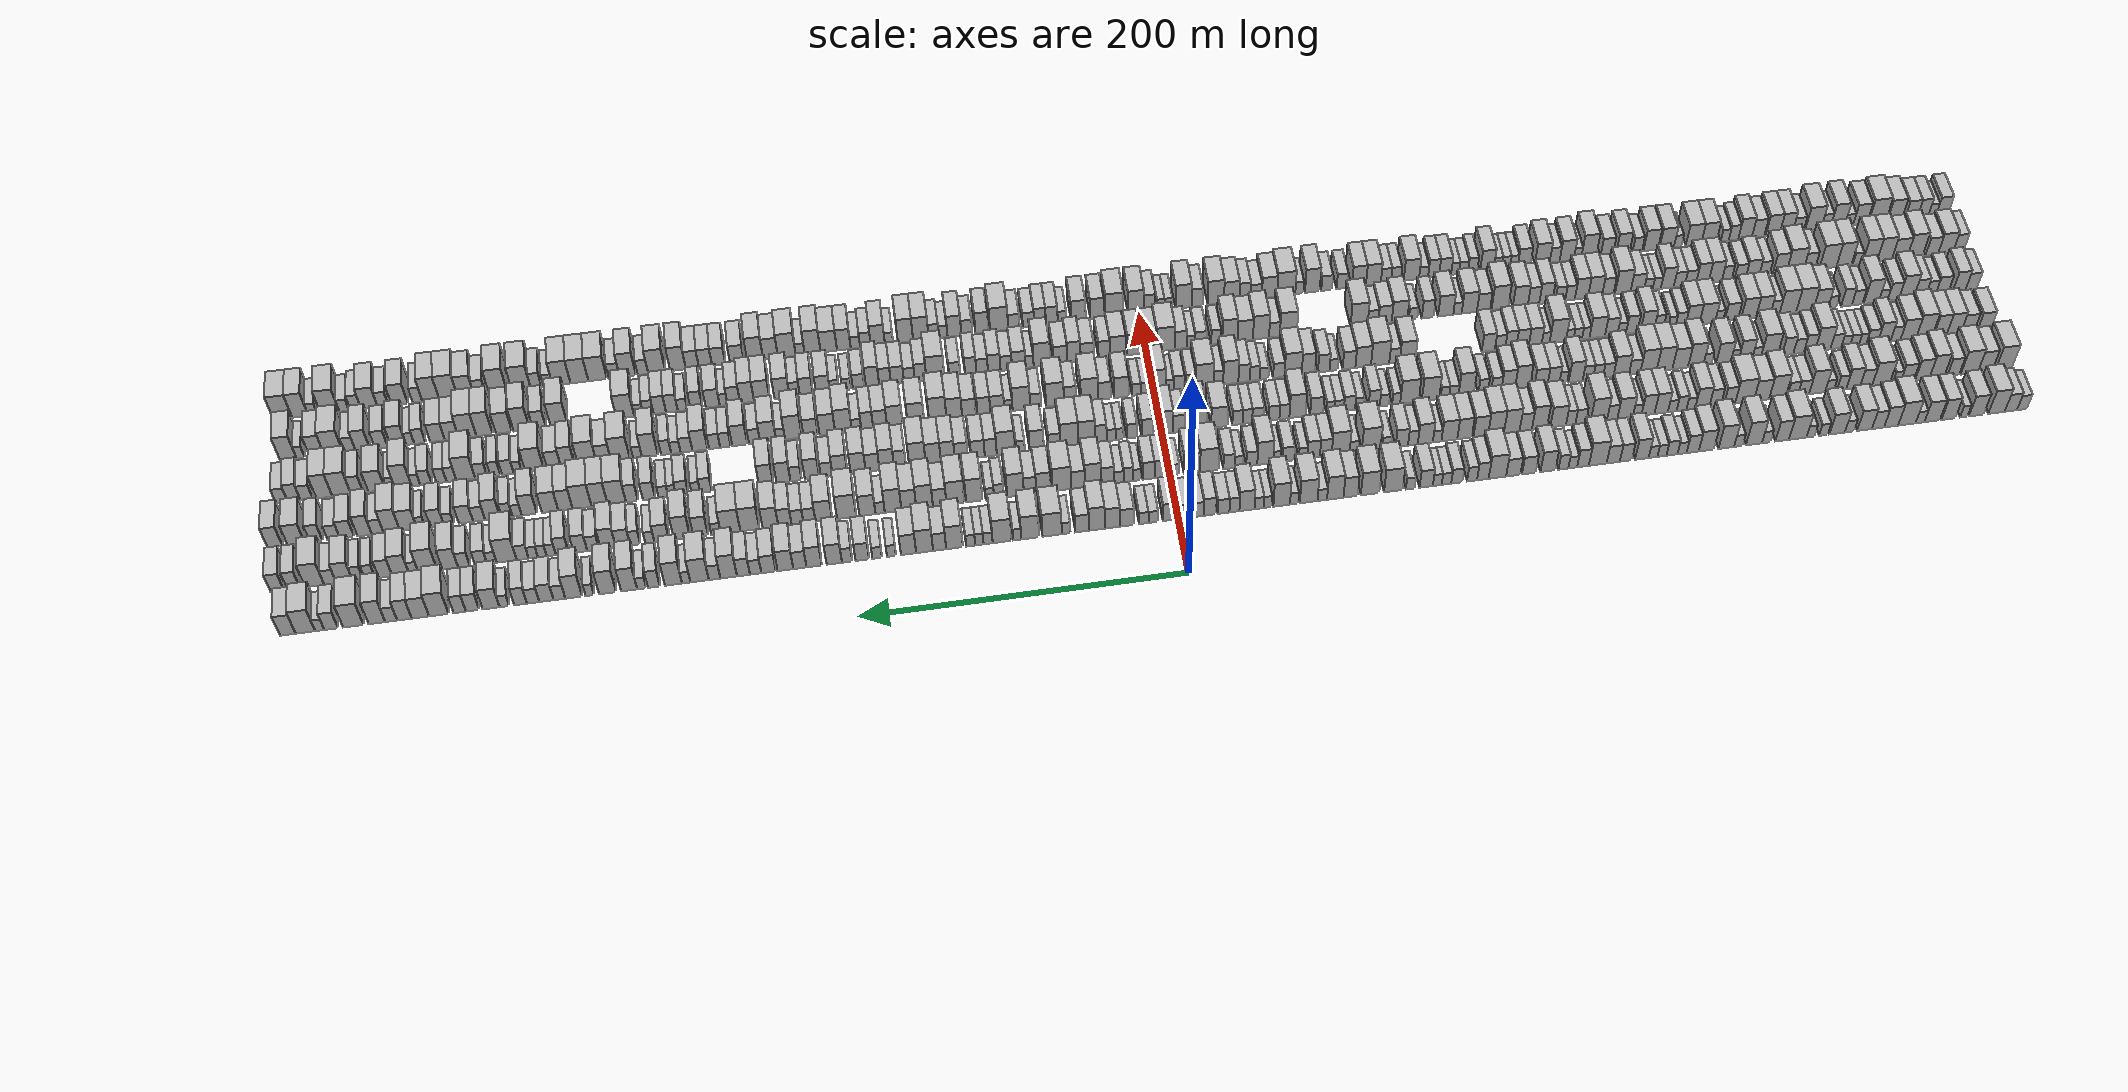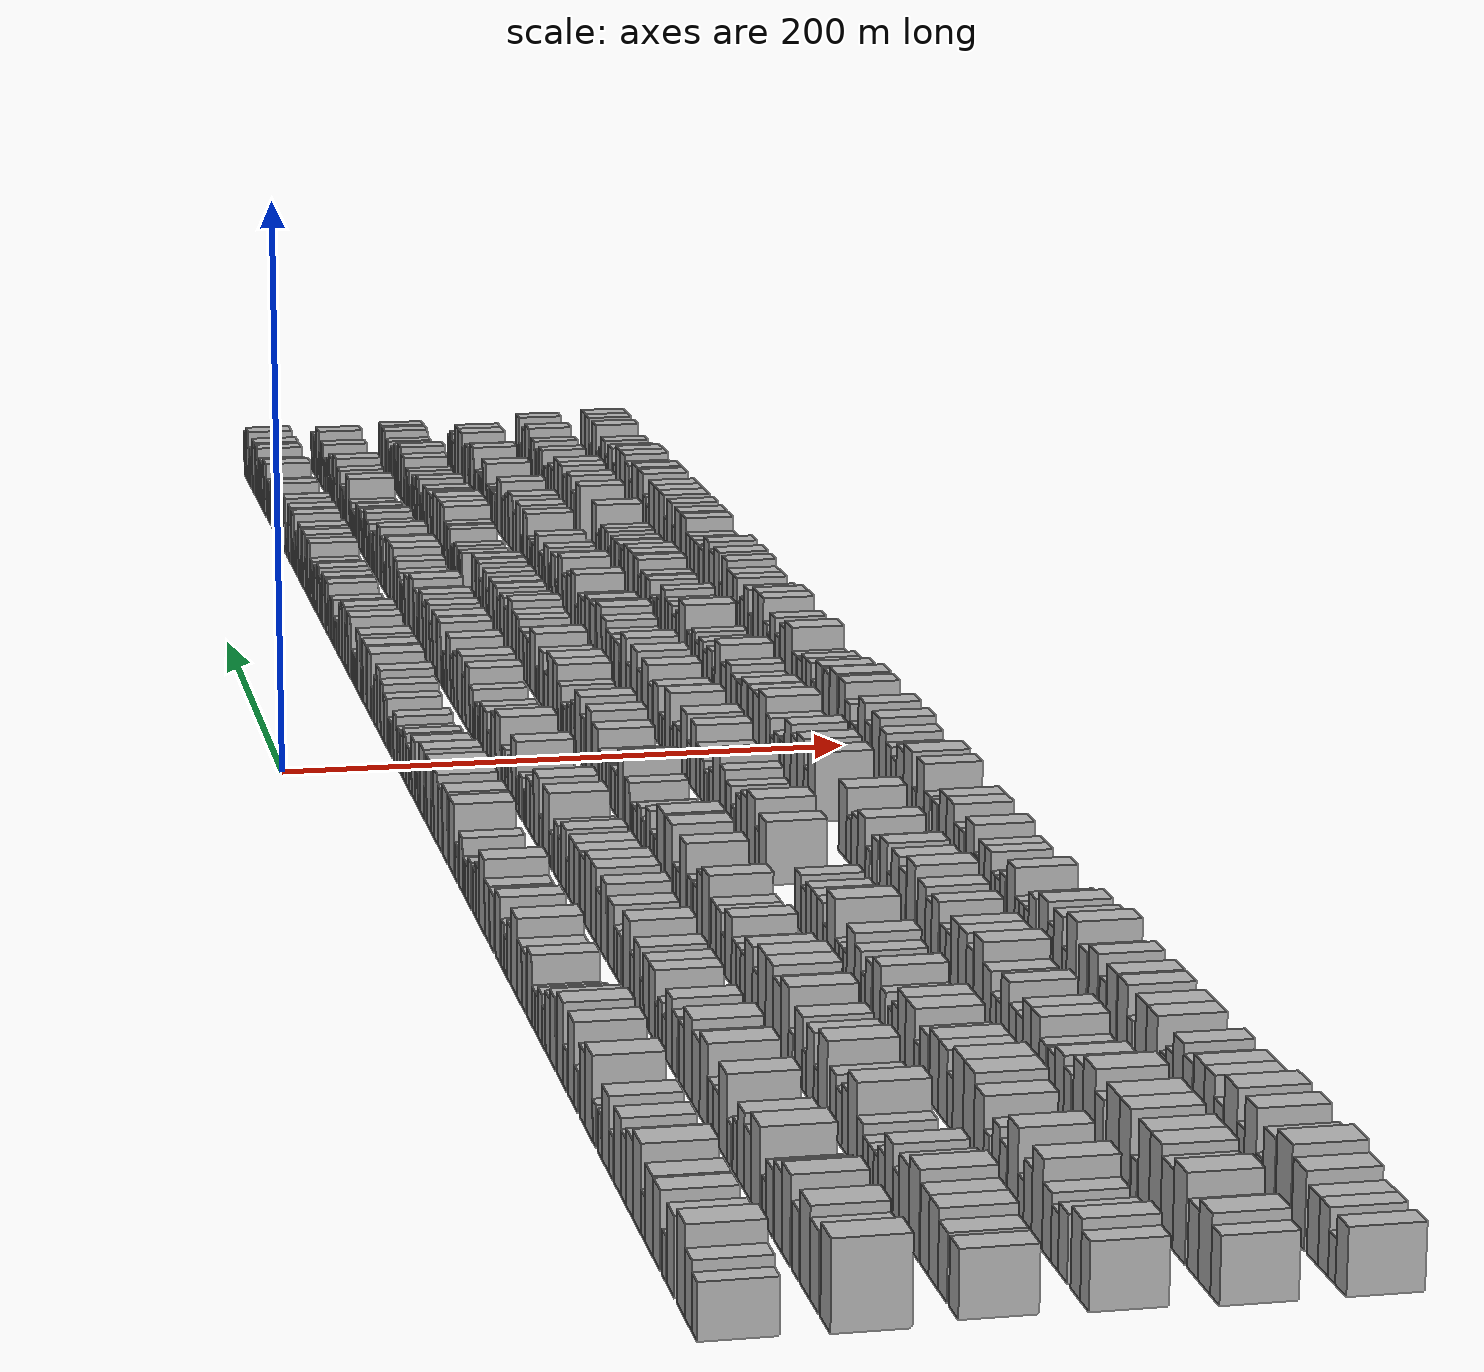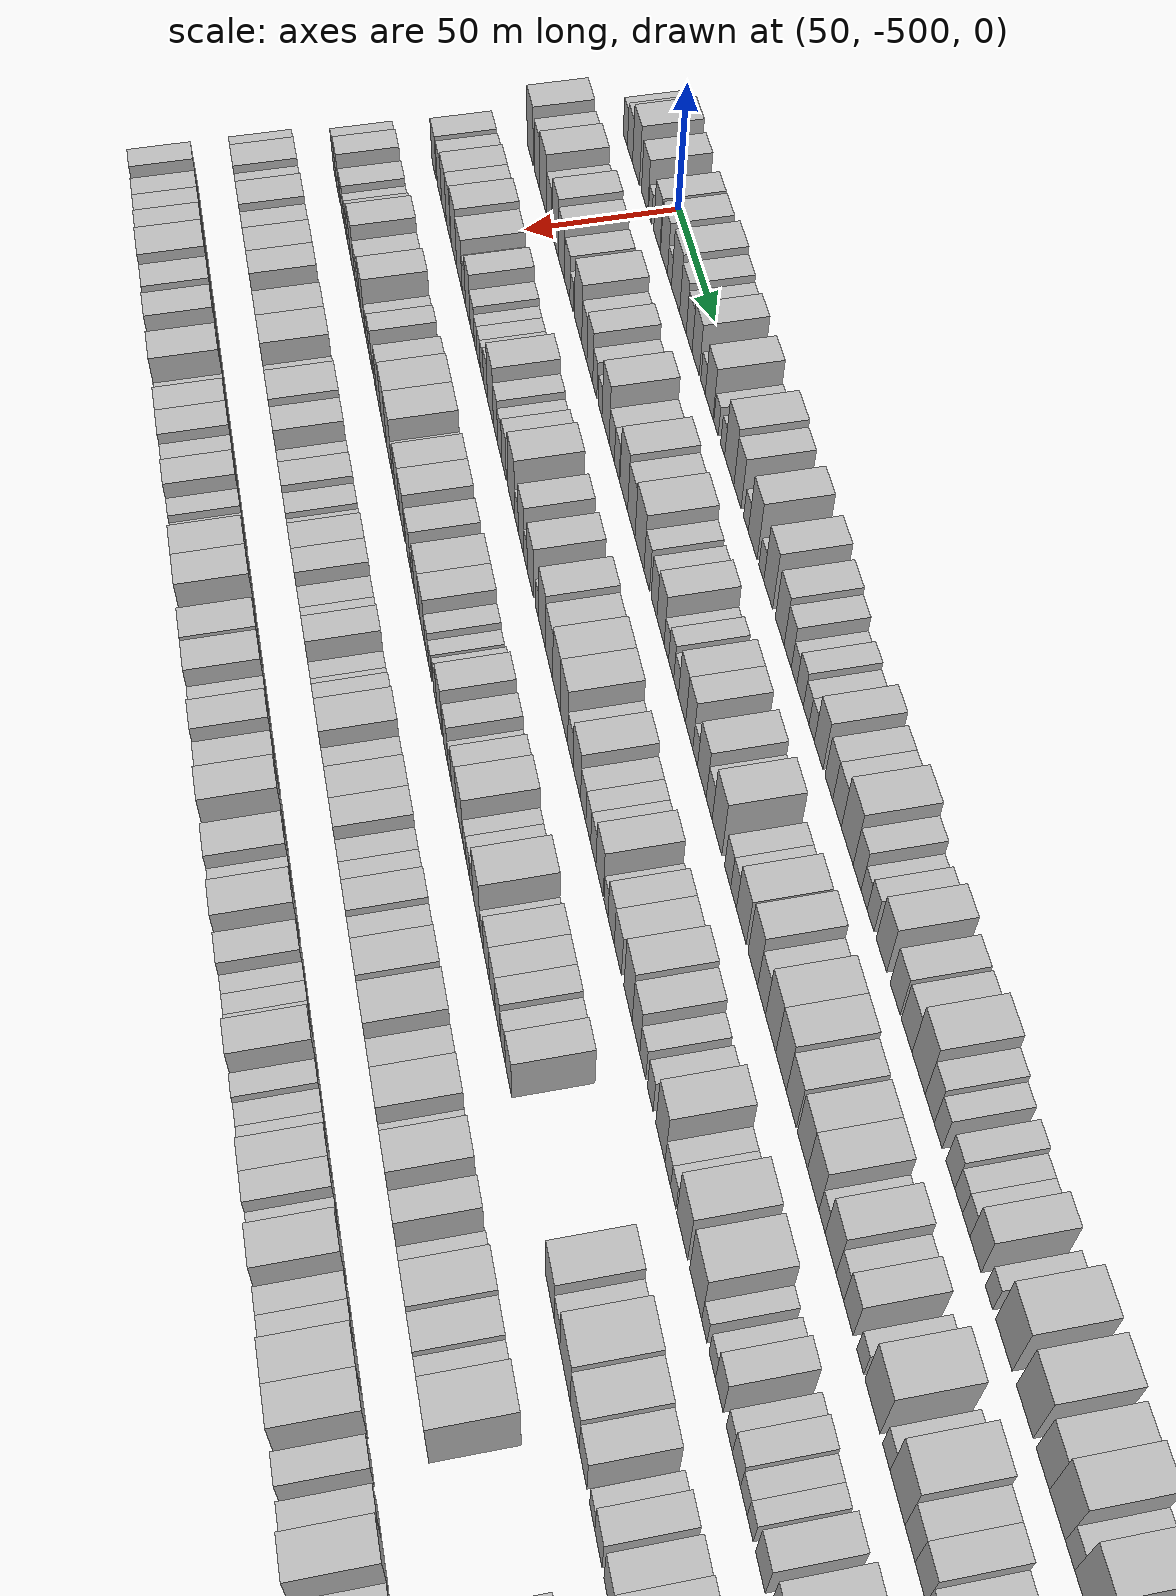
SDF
<sdf version="1.6">
 <world name="default">
  <scene>
   <sky><clouds><speed>12</speed></clouds></sky>
   <ambient>0.4 0.4 0.4 1</ambient>
   <background>0.7 0.7 0.7 1</background>
   <shadows>1</shadows>
  </scene>
  <gravity>0 0 -9.8066</gravity>
  <magnetic_field>6e-06 2.3e-05 -4.2e-05</magnetic_field>
  <physics default="0" name="default_physics" type="ode">
   <ode>
    <solver>
     <type>quick</type>
     <iters>10</iters>
     <sor>1.0</sor>
     <use_dynamic_moi_rescaling>0</use_dynamic_moi_rescaling>
    </solver>
    <constraints>
     <cfm>0</cfm>
     <erp>0.2</erp>
     <contact_max_correcting_vel>100</contact_max_correcting_vel>
     <contact_surface_layer>0.001</contact_surface_layer>
    </constraints>
   </ode>
   <max_step_size>0.004</max_step_size>
   <real_time_factor>1</real_time_factor>
   <real_time_update_rate>250</real_time_update_rate>
  </physics>
  <light name="sun" type="directional">
   <pose>0 0 10 0 0 0</pose>
   <diffuse>0.8 0.8 0.8 1</diffuse>
   <specular>0.2 0.2 0.2 1</specular>
   <attenuation>
    <range>1000</range>
    <constant>0.9</constant>
    <linear>0.01</linear>
    <quadratic>0.001</quadratic>
   </attenuation>
   <direction>-0.5 0.1 -0.9</direction>
  </light>
  <model name="building_1">
   <static>1</static>
   <pose>50.0000 -535.7616 0 0.000000 0.000000 0.000000</pose>
   <link name="link">
    <pose>0 0 7.50 0 0 0</pose>
    <collision name="collision"><geometry><box><size>20.0000 6.4767 15.0000</size></box></geometry></collision>
    <visual name="visual">
     <cast_shadows>0</cast_shadows>
     <geometry><box><size>20.0000 6.4767 15.0000</size></box></geometry>
     <material>
      <script>
       <uri>model://HANNAS_wall/materials/scripts</uri>
       <uri>model://HANNAS_wall/materials/textures</uri>
       <name>vrc/HANNAS_wall</name>
      </script>
     </material>
    </visual>
   </link>
  </model>
  <model name="building_2">
   <static>1</static>
   <pose>50.0000 -528.5074 0 0.000000 0.000000 0.000000</pose>
   <link name="link">
    <pose>0 0 9.00 0 0 0</pose>
    <collision name="collision"><geometry><box><size>20.0000 8.0318 18.0000</size></box></geometry></collision>
    <visual name="visual">
     <cast_shadows>0</cast_shadows>
     <geometry><box><size>20.0000 8.0318 18.0000</size></box></geometry>
     <material>
      <script>
       <uri>model://HANNAS_wall/materials/scripts</uri>
       <uri>model://HANNAS_wall/materials/textures</uri>
       <name>vrc/HANNAS_wall</name>
      </script>
     </material>
    </visual>
   </link>
  </model>
  <model name="building_3">
   <static>1</static>
   <pose>50.0000 -519.1318 0 0.000000 0.000000 0.000000</pose>
   <link name="link">
    <pose>0 0 12.00 0 0 0</pose>
    <collision name="collision"><geometry><box><size>20.0000 10.7195 24.0000</size></box></geometry></collision>
    <visual name="visual">
     <cast_shadows>0</cast_shadows>
     <geometry><box><size>20.0000 10.7195 24.0000</size></box></geometry>
     <material>
      <script>
       <uri>model://HANNAS_wall/materials/scripts</uri>
       <uri>model://HANNAS_wall/materials/textures</uri>
       <name>vrc/HANNAS_wall</name>
      </script>
     </material>
    </visual>
   </link>
  </model>
  <model name="building_4">
   <static>1</static>
   <pose>50.0000 -505.9798 0 0.000000 0.000000 0.000000</pose>
   <link name="link">
    <pose>0 0 10.50 0 0 0</pose>
    <collision name="collision"><geometry><box><size>20.0000 9.5844 21.0000</size></box></geometry></collision>
    <visual name="visual">
     <cast_shadows>0</cast_shadows>
     <geometry><box><size>20.0000 9.5844 21.0000</size></box></geometry>
     <material>
      <script>
       <uri>model://HANNAS_wall/materials/scripts</uri>
       <uri>model://HANNAS_wall/materials/textures</uri>
       <name>vrc/HANNAS_wall</name>
      </script>
     </material>
    </visual>
   </link>
  </model>
  <model name="building_5">
   <static>1</static>
   <pose>50.0000 -497.7741 0 0.000000 0.000000 0.000000</pose>
   <link name="link">
    <pose>0 0 6.00 0 0 0</pose>
    <collision name="collision"><geometry><box><size>20.0000 4.8271 12.0000</size></box></geometry></collision>
    <visual name="visual">
     <cast_shadows>0</cast_shadows>
     <geometry><box><size>20.0000 4.8271 12.0000</size></box></geometry>
     <material>
      <script>
       <uri>model://HANNAS_wall/materials/scripts</uri>
       <uri>model://HANNAS_wall/materials/textures</uri>
       <name>vrc/HANNAS_wall</name>
      </script>
     </material>
    </visual>
   </link>
  </model>
  <model name="building_6">
   <static>1</static>
   <pose>50.0000 -487.8545 0 0.000000 0.000000 0.000000</pose>
   <link name="link">
    <pose>0 0 10.50 0 0 0</pose>
    <collision name="collision"><geometry><box><size>20.0000 9.0120 21.0000</size></box></geometry></collision>
    <visual name="visual">
     <cast_shadows>0</cast_shadows>
     <geometry><box><size>20.0000 9.0120 21.0000</size></box></geometry>
     <material>
      <script>
       <uri>model://HANNAS_wall/materials/scripts</uri>
       <uri>model://HANNAS_wall/materials/textures</uri>
       <name>vrc/HANNAS_wall</name>
      </script>
     </material>
    </visual>
   </link>
  </model>
  <model name="building_7">
   <static>1</static>
   <pose>50.0000 -477.3444 0 0.000000 0.000000 0.000000</pose>
   <link name="link">
    <pose>0 0 10.50 0 0 0</pose>
    <collision name="collision"><geometry><box><size>20.0000 10.0082 21.0000</size></box></geometry></collision>
    <visual name="visual">
     <cast_shadows>0</cast_shadows>
     <geometry><box><size>20.0000 10.0082 21.0000</size></box></geometry>
     <material>
      <script>
       <uri>model://HANNAS_wall/materials/scripts</uri>
       <uri>model://HANNAS_wall/materials/textures</uri>
       <name>vrc/HANNAS_wall</name>
      </script>
     </material>
    </visual>
   </link>
  </model>
  <model name="building_8">
   <static>1</static>
   <pose>50.0000 -469.4702 0 0.000000 0.000000 0.000000</pose>
   <link name="link">
    <pose>0 0 6.00 0 0 0</pose>
    <collision name="collision"><geometry><box><size>20.0000 5.7402 12.0000</size></box></geometry></collision>
    <visual name="visual">
     <cast_shadows>0</cast_shadows>
     <geometry><box><size>20.0000 5.7402 12.0000</size></box></geometry>
     <material>
      <script>
       <uri>model://HANNAS_wall/materials/scripts</uri>
       <uri>model://HANNAS_wall/materials/textures</uri>
       <name>vrc/HANNAS_wall</name>
      </script>
     </material>
    </visual>
   </link>
  </model>
  <model name="building_9">
   <static>1</static>
   <pose>50.0000 -460.9386 0 0.000000 0.000000 0.000000</pose>
   <link name="link">
    <pose>0 0 12.00 0 0 0</pose>
    <collision name="collision"><geometry><box><size>20.0000 11.3230 24.0000</size></box></geometry></collision>
    <visual name="visual">
     <cast_shadows>0</cast_shadows>
     <geometry><box><size>20.0000 11.3230 24.0000</size></box></geometry>
     <material>
      <script>
       <uri>model://HANNAS_wall/materials/scripts</uri>
       <uri>model://HANNAS_wall/materials/textures</uri>
       <name>vrc/HANNAS_wall</name>
      </script>
     </material>
    </visual>
   </link>
  </model>
  <model name="building_10">
   <static>1</static>
   <pose>50.0000 -450.7442 0 0.000000 0.000000 0.000000</pose>
   <link name="link">
    <pose>0 0 10.50 0 0 0</pose>
    <collision name="collision"><geometry><box><size>20.0000 9.0658 21.0000</size></box></geometry></collision>
    <visual name="visual">
     <cast_shadows>0</cast_shadows>
     <geometry><box><size>20.0000 9.0658 21.0000</size></box></geometry>
     <material>
      <script>
       <uri>model://HANNAS_wall/materials/scripts</uri>
       <uri>model://HANNAS_wall/materials/textures</uri>
       <name>vrc/HANNAS_wall</name>
      </script>
     </material>
    </visual>
   </link>
  </model>
  <model name="building_11">
   <static>1</static>
   <pose>50.0000 -442.2611 0 0.000000 0.000000 0.000000</pose>
   <link name="link">
    <pose>0 0 9.00 0 0 0</pose>
    <collision name="collision"><geometry><box><size>20.0000 7.9005 18.0000</size></box></geometry></collision>
    <visual name="visual">
     <cast_shadows>0</cast_shadows>
     <geometry><box><size>20.0000 7.9005 18.0000</size></box></geometry>
     <material>
      <script>
       <uri>model://HANNAS_wall/materials/scripts</uri>
       <uri>model://HANNAS_wall/materials/textures</uri>
       <name>vrc/HANNAS_wall</name>
      </script>
     </material>
    </visual>
   </link>
  </model>
  <model name="building_12">
   <static>1</static>
   <pose>50.0000 -433.5036 0 0.000000 0.000000 0.000000</pose>
   <link name="link">
    <pose>0 0 10.50 0 0 0</pose>
    <collision name="collision"><geometry><box><size>20.0000 9.6145 21.0000</size></box></geometry></collision>
    <visual name="visual">
     <cast_shadows>0</cast_shadows>
     <geometry><box><size>20.0000 9.6145 21.0000</size></box></geometry>
     <material>
      <script>
       <uri>model://HANNAS_wall/materials/scripts</uri>
       <uri>model://HANNAS_wall/materials/textures</uri>
       <name>vrc/HANNAS_wall</name>
      </script>
     </material>
    </visual>
   </link>
  </model>
  <model name="building_13">
   <static>1</static>
   <pose>50.0000 -423.7667 0 0.000000 0.000000 0.000000</pose>
   <link name="link">
    <pose>0 0 6.00 0 0 0</pose>
    <collision name="collision"><geometry><box><size>20.0000 5.8594 12.0000</size></box></geometry></collision>
    <visual name="visual">
     <cast_shadows>0</cast_shadows>
     <geometry><box><size>20.0000 5.8594 12.0000</size></box></geometry>
     <material>
      <script>
       <uri>model://HANNAS_wall/materials/scripts</uri>
       <uri>model://HANNAS_wall/materials/textures</uri>
       <name>vrc/HANNAS_wall</name>
      </script>
     </material>
    </visual>
   </link>
  </model>
  <model name="building_14">
   <static>1</static>
   <pose>50.0000 -415.8251 0 0.000000 0.000000 0.000000</pose>
   <link name="link">
    <pose>0 0 10.50 0 0 0</pose>
    <collision name="collision"><geometry><box><size>20.0000 10.0237 21.0000</size></box></geometry></collision>
    <visual name="visual">
     <cast_shadows>0</cast_shadows>
     <geometry><box><size>20.0000 10.0237 21.0000</size></box></geometry>
     <material>
      <script>
       <uri>model://HANNAS_wall/materials/scripts</uri>
       <uri>model://HANNAS_wall/materials/textures</uri>
       <name>vrc/HANNAS_wall</name>
      </script>
     </material>
    </visual>
   </link>
  </model>
  <model name="building_15">
   <static>1</static>
   <pose>50.0000 -406.9831 0 0.000000 0.000000 0.000000</pose>
   <link name="link">
    <pose>0 0 6.00 0 0 0</pose>
    <collision name="collision"><geometry><box><size>20.0000 5.6603 12.0000</size></box></geometry></collision>
    <visual name="visual">
     <cast_shadows>0</cast_shadows>
     <geometry><box><size>20.0000 5.6603 12.0000</size></box></geometry>
     <material>
      <script>
       <uri>model://HANNAS_wall/materials/scripts</uri>
       <uri>model://HANNAS_wall/materials/textures</uri>
       <name>vrc/HANNAS_wall</name>
      </script>
     </material>
    </visual>
   </link>
  </model>
  <model name="building_16">
   <static>1</static>
   <pose>50.0000 -398.6323 0 0.000000 0.000000 0.000000</pose>
   <link name="link">
    <pose>0 0 6.00 0 0 0</pose>
    <collision name="collision"><geometry><box><size>20.0000 5.0413 12.0000</size></box></geometry></collision>
    <visual name="visual">
     <cast_shadows>0</cast_shadows>
     <geometry><box><size>20.0000 5.0413 12.0000</size></box></geometry>
     <material>
      <script>
       <uri>model://HANNAS_wall/materials/scripts</uri>
       <uri>model://HANNAS_wall/materials/textures</uri>
       <name>vrc/HANNAS_wall</name>
      </script>
     </material>
    </visual>
   </link>
  </model>
  <model name="building_17">
   <static>1</static>
   <pose>50.0000 -390.4212 0 0.000000 0.000000 0.000000</pose>
   <link name="link">
    <pose>0 0 12.00 0 0 0</pose>
    <collision name="collision"><geometry><box><size>20.0000 11.3807 24.0000</size></box></geometry></collision>
    <visual name="visual">
     <cast_shadows>0</cast_shadows>
     <geometry><box><size>20.0000 11.3807 24.0000</size></box></geometry>
     <material>
      <script>
       <uri>model://HANNAS_wall/materials/scripts</uri>
       <uri>model://HANNAS_wall/materials/textures</uri>
       <name>vrc/HANNAS_wall</name>
      </script>
     </material>
    </visual>
   </link>
  </model>
  <model name="building_18">
   <static>1</static>
   <pose>50.0000 -380.3764 0 0.000000 0.000000 0.000000</pose>
   <link name="link">
    <pose>0 0 10.50 0 0 0</pose>
    <collision name="collision"><geometry><box><size>20.0000 8.7089 21.0000</size></box></geometry></collision>
    <visual name="visual">
     <cast_shadows>0</cast_shadows>
     <geometry><box><size>20.0000 8.7089 21.0000</size></box></geometry>
     <material>
      <script>
       <uri>model://HANNAS_wall/materials/scripts</uri>
       <uri>model://HANNAS_wall/materials/textures</uri>
       <name>vrc/HANNAS_wall</name>
      </script>
     </material>
    </visual>
   </link>
  </model>
  <model name="building_19">
   <static>1</static>
   <pose>50.0000 -370.2138 0 0.000000 0.000000 0.000000</pose>
   <link name="link">
    <pose>0 0 6.00 0 0 0</pose>
    <collision name="collision"><geometry><box><size>20.0000 5.6164 12.0000</size></box></geometry></collision>
    <visual name="visual">
     <cast_shadows>0</cast_shadows>
     <geometry><box><size>20.0000 5.6164 12.0000</size></box></geometry>
     <material>
      <script>
       <uri>model://HANNAS_wall/materials/scripts</uri>
       <uri>model://HANNAS_wall/materials/textures</uri>
       <name>vrc/HANNAS_wall</name>
      </script>
     </material>
    </visual>
   </link>
  </model>
  <model name="building_20">
   <static>1</static>
   <pose>50.0000 -362.2607 0 0.000000 0.000000 0.000000</pose>
   <link name="link">
    <pose>0 0 12.00 0 0 0</pose>
    <collision name="collision"><geometry><box><size>20.0000 10.2897 24.0000</size></box></geometry></collision>
    <visual name="visual">
     <cast_shadows>0</cast_shadows>
     <geometry><box><size>20.0000 10.2897 24.0000</size></box></geometry>
     <material>
      <script>
       <uri>model://HANNAS_wall/materials/scripts</uri>
       <uri>model://HANNAS_wall/materials/textures</uri>
       <name>vrc/HANNAS_wall</name>
      </script>
     </material>
    </visual>
   </link>
  </model>
  <model name="building_21">
   <static>1</static>
   <pose>50.0000 -352.3181 0 0.000000 0.000000 0.000000</pose>
   <link name="link">
    <pose>0 0 6.00 0 0 0</pose>
    <collision name="collision"><geometry><box><size>20.0000 5.5954 12.0000</size></box></geometry></collision>
    <visual name="visual">
     <cast_shadows>0</cast_shadows>
     <geometry><box><size>20.0000 5.5954 12.0000</size></box></geometry>
     <material>
      <script>
       <uri>model://HANNAS_wall/materials/scripts</uri>
       <uri>model://HANNAS_wall/materials/textures</uri>
       <name>vrc/HANNAS_wall</name>
      </script>
     </material>
    </visual>
   </link>
  </model>
  <model name="building_22">
   <static>1</static>
   <pose>50.0000 -344.5052 0 0.000000 0.000000 0.000000</pose>
   <link name="link">
    <pose>0 0 12.00 0 0 0</pose>
    <collision name="collision"><geometry><box><size>20.0000 10.0305 24.0000</size></box></geometry></collision>
    <visual name="visual">
     <cast_shadows>0</cast_shadows>
     <geometry><box><size>20.0000 10.0305 24.0000</size></box></geometry>
     <material>
      <script>
       <uri>model://HANNAS_wall/materials/scripts</uri>
       <uri>model://HANNAS_wall/materials/textures</uri>
       <name>vrc/HANNAS_wall</name>
      </script>
     </material>
    </visual>
   </link>
  </model>
  <model name="building_23">
   <static>1</static>
   <pose>50.0000 -331.6770 0 0.000000 0.000000 0.000000</pose>
   <link name="link">
    <pose>0 0 10.50 0 0 0</pose>
    <collision name="collision"><geometry><box><size>20.0000 9.6259 21.0000</size></box></geometry></collision>
    <visual name="visual">
     <cast_shadows>0</cast_shadows>
     <geometry><box><size>20.0000 9.6259 21.0000</size></box></geometry>
     <material>
      <script>
       <uri>model://HANNAS_wall/materials/scripts</uri>
       <uri>model://HANNAS_wall/materials/textures</uri>
       <name>vrc/HANNAS_wall</name>
      </script>
     </material>
    </visual>
   </link>
  </model>
  <model name="building_24">
   <static>1</static>
   <pose>50.0000 -322.9932 0 0.000000 0.000000 0.000000</pose>
   <link name="link">
    <pose>0 0 9.00 0 0 0</pose>
    <collision name="collision"><geometry><box><size>20.0000 7.7417 18.0000</size></box></geometry></collision>
    <visual name="visual">
     <cast_shadows>0</cast_shadows>
     <geometry><box><size>20.0000 7.7417 18.0000</size></box></geometry>
     <material>
      <script>
       <uri>model://HANNAS_wall/materials/scripts</uri>
       <uri>model://HANNAS_wall/materials/textures</uri>
       <name>vrc/HANNAS_wall</name>
      </script>
     </material>
    </visual>
   </link>
  </model>
  <model name="building_25">
   <static>1</static>
   <pose>50.0000 -316.2229 0 0.000000 0.000000 0.000000</pose>
   <link name="link">
    <pose>0 0 6.00 0 0 0</pose>
    <collision name="collision"><geometry><box><size>20.0000 5.7988 12.0000</size></box></geometry></collision>
    <visual name="visual">
     <cast_shadows>0</cast_shadows>
     <geometry><box><size>20.0000 5.7988 12.0000</size></box></geometry>
     <material>
      <script>
       <uri>model://HANNAS_wall/materials/scripts</uri>
       <uri>model://HANNAS_wall/materials/textures</uri>
       <name>vrc/HANNAS_wall</name>
      </script>
     </material>
    </visual>
   </link>
  </model>
  <model name="building_26">
   <static>1</static>
   <pose>50.0000 -309.8086 0 0.000000 0.000000 0.000000</pose>
   <link name="link">
    <pose>0 0 7.50 0 0 0</pose>
    <collision name="collision"><geometry><box><size>20.0000 7.0299 15.0000</size></box></geometry></collision>
    <visual name="visual">
     <cast_shadows>0</cast_shadows>
     <geometry><box><size>20.0000 7.0299 15.0000</size></box></geometry>
     <material>
      <script>
       <uri>model://HANNAS_wall/materials/scripts</uri>
       <uri>model://HANNAS_wall/materials/textures</uri>
       <name>vrc/HANNAS_wall</name>
      </script>
     </material>
    </visual>
   </link>
  </model>
  <model name="building_27">
   <static>1</static>
   <pose>50.0000 -303.3903 0 0.000000 0.000000 0.000000</pose>
   <link name="link">
    <pose>0 0 6.00 0 0 0</pose>
    <collision name="collision"><geometry><box><size>20.0000 5.8066 12.0000</size></box></geometry></collision>
    <visual name="visual">
     <cast_shadows>0</cast_shadows>
     <geometry><box><size>20.0000 5.8066 12.0000</size></box></geometry>
     <material>
      <script>
       <uri>model://HANNAS_wall/materials/scripts</uri>
       <uri>model://HANNAS_wall/materials/textures</uri>
       <name>vrc/HANNAS_wall</name>
      </script>
     </material>
    </visual>
   </link>
  </model>
  <model name="building_28">
   <static>1</static>
   <pose>50.0000 -297.7260 0 0.000000 0.000000 0.000000</pose>
   <link name="link">
    <pose>0 0 6.00 0 0 0</pose>
    <collision name="collision"><geometry><box><size>20.0000 5.5220 12.0000</size></box></geometry></collision>
    <visual name="visual">
     <cast_shadows>0</cast_shadows>
     <geometry><box><size>20.0000 5.5220 12.0000</size></box></geometry>
     <material>
      <script>
       <uri>model://HANNAS_wall/materials/scripts</uri>
       <uri>model://HANNAS_wall/materials/textures</uri>
       <name>vrc/HANNAS_wall</name>
      </script>
     </material>
    </visual>
   </link>
  </model>
  <model name="building_29">
   <static>1</static>
   <pose>50.0000 -290.5696 0 0.000000 0.000000 0.000000</pose>
   <link name="link">
    <pose>0 0 10.50 0 0 0</pose>
    <collision name="collision"><geometry><box><size>20.0000 8.7908 21.0000</size></box></geometry></collision>
    <visual name="visual">
     <cast_shadows>0</cast_shadows>
     <geometry><box><size>20.0000 8.7908 21.0000</size></box></geometry>
     <material>
      <script>
       <uri>model://HANNAS_wall/materials/scripts</uri>
       <uri>model://HANNAS_wall/materials/textures</uri>
       <name>vrc/HANNAS_wall</name>
      </script>
     </material>
    </visual>
   </link>
  </model>
  <model name="building_30">
   <static>1</static>
   <pose>50.0000 -280.3609 0 0.000000 0.000000 0.000000</pose>
   <link name="link">
    <pose>0 0 9.00 0 0 0</pose>
    <collision name="collision"><geometry><box><size>20.0000 7.6265 18.0000</size></box></geometry></collision>
    <visual name="visual">
     <cast_shadows>0</cast_shadows>
     <geometry><box><size>20.0000 7.6265 18.0000</size></box></geometry>
     <material>
      <script>
       <uri>model://HANNAS_wall/materials/scripts</uri>
       <uri>model://HANNAS_wall/materials/textures</uri>
       <name>vrc/HANNAS_wall</name>
      </script>
     </material>
    </visual>
   </link>
  </model>
  <model name="building_31">
   <static>1</static>
   <pose>50.0000 -272.3562 0 0.000000 0.000000 0.000000</pose>
   <link name="link">
    <pose>0 0 9.00 0 0 0</pose>
    <collision name="collision"><geometry><box><size>20.0000 8.3829 18.0000</size></box></geometry></collision>
    <visual name="visual">
     <cast_shadows>0</cast_shadows>
     <geometry><box><size>20.0000 8.3829 18.0000</size></box></geometry>
     <material>
      <script>
       <uri>model://HANNAS_wall/materials/scripts</uri>
       <uri>model://HANNAS_wall/materials/textures</uri>
       <name>vrc/HANNAS_wall</name>
      </script>
     </material>
    </visual>
   </link>
  </model>
  <model name="building_32">
   <static>1</static>
   <pose>50.0000 -262.5028 0 0.000000 0.000000 0.000000</pose>
   <link name="link">
    <pose>0 0 12.00 0 0 0</pose>
    <collision name="collision"><geometry><box><size>20.0000 11.3239 24.0000</size></box></geometry></collision>
    <visual name="visual">
     <cast_shadows>0</cast_shadows>
     <geometry><box><size>20.0000 11.3239 24.0000</size></box></geometry>
     <material>
      <script>
       <uri>model://HANNAS_wall/materials/scripts</uri>
       <uri>model://HANNAS_wall/materials/textures</uri>
       <name>vrc/HANNAS_wall</name>
      </script>
     </material>
    </visual>
   </link>
  </model>
  <model name="building_33">
   <static>1</static>
   <pose>50.0000 -253.1167 0 0.000000 0.000000 0.000000</pose>
   <link name="link">
    <pose>0 0 9.00 0 0 0</pose>
    <collision name="collision"><geometry><box><size>20.0000 7.4485 18.0000</size></box></geometry></collision>
    <visual name="visual">
     <cast_shadows>0</cast_shadows>
     <geometry><box><size>20.0000 7.4485 18.0000</size></box></geometry>
     <material>
      <script>
       <uri>model://HANNAS_wall/materials/scripts</uri>
       <uri>model://HANNAS_wall/materials/textures</uri>
       <name>vrc/HANNAS_wall</name>
      </script>
     </material>
    </visual>
   </link>
  </model>
  <model name="building_34">
   <static>1</static>
   <pose>50.0000 -246.6153 0 0.000000 0.000000 0.000000</pose>
   <link name="link">
    <pose>0 0 6.00 0 0 0</pose>
    <collision name="collision"><geometry><box><size>20.0000 5.5543 12.0000</size></box></geometry></collision>
    <visual name="visual">
     <cast_shadows>0</cast_shadows>
     <geometry><box><size>20.0000 5.5543 12.0000</size></box></geometry>
     <material>
      <script>
       <uri>model://HANNAS_wall/materials/scripts</uri>
       <uri>model://HANNAS_wall/materials/textures</uri>
       <name>vrc/HANNAS_wall</name>
      </script>
     </material>
    </visual>
   </link>
  </model>
  <model name="building_35">
   <static>1</static>
   <pose>50.0000 -240.7044 0 0.000000 0.000000 0.000000</pose>
   <link name="link">
    <pose>0 0 7.50 0 0 0</pose>
    <collision name="collision"><geometry><box><size>20.0000 6.2673 15.0000</size></box></geometry></collision>
    <visual name="visual">
     <cast_shadows>0</cast_shadows>
     <geometry><box><size>20.0000 6.2673 15.0000</size></box></geometry>
     <material>
      <script>
       <uri>model://HANNAS_wall/materials/scripts</uri>
       <uri>model://HANNAS_wall/materials/textures</uri>
       <name>vrc/HANNAS_wall</name>
      </script>
     </material>
    </visual>
   </link>
  </model>
  <model name="building_36">
   <static>1</static>
   <pose>50.0000 -230.8726 0 0.000000 0.000000 0.000000</pose>
   <link name="link">
    <pose>0 0 10.50 0 0 0</pose>
    <collision name="collision"><geometry><box><size>20.0000 9.3964 21.0000</size></box></geometry></collision>
    <visual name="visual">
     <cast_shadows>0</cast_shadows>
     <geometry><box><size>20.0000 9.3964 21.0000</size></box></geometry>
     <material>
      <script>
       <uri>model://HANNAS_wall/materials/scripts</uri>
       <uri>model://HANNAS_wall/materials/textures</uri>
       <name>vrc/HANNAS_wall</name>
      </script>
     </material>
    </visual>
   </link>
  </model>
  <model name="building_37">
   <static>1</static>
   <pose>50.0000 -218.8136 0 0.000000 0.000000 0.000000</pose>
   <link name="link">
    <pose>0 0 9.00 0 0 0</pose>
    <collision name="collision"><geometry><box><size>20.0000 8.7217 18.0000</size></box></geometry></collision>
    <visual name="visual">
     <cast_shadows>0</cast_shadows>
     <geometry><box><size>20.0000 8.7217 18.0000</size></box></geometry>
     <material>
      <script>
       <uri>model://HANNAS_wall/materials/scripts</uri>
       <uri>model://HANNAS_wall/materials/textures</uri>
       <name>vrc/HANNAS_wall</name>
      </script>
     </material>
    </visual>
   </link>
  </model>
  <model name="building_38">
   <static>1</static>
   <pose>50.0000 -208.9542 0 0.000000 0.000000 0.000000</pose>
   <link name="link">
    <pose>0 0 9.00 0 0 0</pose>
    <collision name="collision"><geometry><box><size>20.0000 8.9971 18.0000</size></box></geometry></collision>
    <visual name="visual">
     <cast_shadows>0</cast_shadows>
     <geometry><box><size>20.0000 8.9971 18.0000</size></box></geometry>
     <material>
      <script>
       <uri>model://HANNAS_wall/materials/scripts</uri>
       <uri>model://HANNAS_wall/materials/textures</uri>
       <name>vrc/HANNAS_wall</name>
      </script>
     </material>
    </visual>
   </link>
  </model>
  <model name="building_39">
   <static>1</static>
   <pose>50.0000 -198.9509 0 0.000000 0.000000 0.000000</pose>
   <link name="link">
    <pose>0 0 12.00 0 0 0</pose>
    <collision name="collision"><geometry><box><size>20.0000 11.0095 24.0000</size></box></geometry></collision>
    <visual name="visual">
     <cast_shadows>0</cast_shadows>
     <geometry><box><size>20.0000 11.0095 24.0000</size></box></geometry>
     <material>
      <script>
       <uri>model://HANNAS_wall/materials/scripts</uri>
       <uri>model://HANNAS_wall/materials/textures</uri>
       <name>vrc/HANNAS_wall</name>
      </script>
     </material>
    </visual>
   </link>
  </model>
  <model name="building_40">
   <static>1</static>
   <pose>50.0000 -189.7925 0 0.000000 0.000000 0.000000</pose>
   <link name="link">
    <pose>0 0 9.00 0 0 0</pose>
    <collision name="collision"><geometry><box><size>20.0000 7.3073 18.0000</size></box></geometry></collision>
    <visual name="visual">
     <cast_shadows>0</cast_shadows>
     <geometry><box><size>20.0000 7.3073 18.0000</size></box></geometry>
     <material>
      <script>
       <uri>model://HANNAS_wall/materials/scripts</uri>
       <uri>model://HANNAS_wall/materials/textures</uri>
       <name>vrc/HANNAS_wall</name>
      </script>
     </material>
    </visual>
   </link>
  </model>
  <model name="building_41">
   <static>1</static>
   <pose>50.0000 -182.9778 0 0.000000 0.000000 0.000000</pose>
   <link name="link">
    <pose>0 0 7.50 0 0 0</pose>
    <collision name="collision"><geometry><box><size>20.0000 6.3221 15.0000</size></box></geometry></collision>
    <visual name="visual">
     <cast_shadows>0</cast_shadows>
     <geometry><box><size>20.0000 6.3221 15.0000</size></box></geometry>
     <material>
      <script>
       <uri>model://HANNAS_wall/materials/scripts</uri>
       <uri>model://HANNAS_wall/materials/textures</uri>
       <name>vrc/HANNAS_wall</name>
      </script>
     </material>
    </visual>
   </link>
  </model>
  <model name="building_42">
   <static>1</static>
   <pose>50.0000 -173.3181 0 0.000000 0.000000 0.000000</pose>
   <link name="link">
    <pose>0 0 7.50 0 0 0</pose>
    <collision name="collision"><geometry><box><size>20.0000 6.9972 15.0000</size></box></geometry></collision>
    <visual name="visual">
     <cast_shadows>0</cast_shadows>
     <geometry><box><size>20.0000 6.9972 15.0000</size></box></geometry>
     <material>
      <script>
       <uri>model://HANNAS_wall/materials/scripts</uri>
       <uri>model://HANNAS_wall/materials/textures</uri>
       <name>vrc/HANNAS_wall</name>
      </script>
     </material>
    </visual>
   </link>
  </model>
  <model name="building_43">
   <static>1</static>
   <pose>50.0000 -166.8333 0 0.000000 0.000000 0.000000</pose>
   <link name="link">
    <pose>0 0 6.00 0 0 0</pose>
    <collision name="collision"><geometry><box><size>20.0000 5.9725 12.0000</size></box></geometry></collision>
    <visual name="visual">
     <cast_shadows>0</cast_shadows>
     <geometry><box><size>20.0000 5.9725 12.0000</size></box></geometry>
     <material>
      <script>
       <uri>model://HANNAS_wall/materials/scripts</uri>
       <uri>model://HANNAS_wall/materials/textures</uri>
       <name>vrc/HANNAS_wall</name>
      </script>
     </material>
    </visual>
   </link>
  </model>
  <model name="building_44">
   <static>1</static>
   <pose>50.0000 -161.0498 0 0.000000 0.000000 0.000000</pose>
   <link name="link">
    <pose>0 0 6.00 0 0 0</pose>
    <collision name="collision"><geometry><box><size>20.0000 5.5944 12.0000</size></box></geometry></collision>
    <visual name="visual">
     <cast_shadows>0</cast_shadows>
     <geometry><box><size>20.0000 5.5944 12.0000</size></box></geometry>
     <material>
      <script>
       <uri>model://HANNAS_wall/materials/scripts</uri>
       <uri>model://HANNAS_wall/materials/textures</uri>
       <name>vrc/HANNAS_wall</name>
      </script>
     </material>
    </visual>
   </link>
  </model>
  <model name="building_45">
   <static>1</static>
   <pose>50.0000 -154.0723 0 0.000000 0.000000 0.000000</pose>
   <link name="link">
    <pose>0 0 9.00 0 0 0</pose>
    <collision name="collision"><geometry><box><size>20.0000 8.3606 18.0000</size></box></geometry></collision>
    <visual name="visual">
     <cast_shadows>0</cast_shadows>
     <geometry><box><size>20.0000 8.3606 18.0000</size></box></geometry>
     <material>
      <script>
       <uri>model://HANNAS_wall/materials/scripts</uri>
       <uri>model://HANNAS_wall/materials/textures</uri>
       <name>vrc/HANNAS_wall</name>
      </script>
     </material>
    </visual>
   </link>
  </model>
  <model name="building_46">
   <static>1</static>
   <pose>50.0000 -144.1225 0 0.000000 0.000000 0.000000</pose>
   <link name="link">
    <pose>0 0 6.00 0 0 0</pose>
    <collision name="collision"><geometry><box><size>20.0000 5.5389 12.0000</size></box></geometry></collision>
    <visual name="visual">
     <cast_shadows>0</cast_shadows>
     <geometry><box><size>20.0000 5.5389 12.0000</size></box></geometry>
     <material>
      <script>
       <uri>model://HANNAS_wall/materials/scripts</uri>
       <uri>model://HANNAS_wall/materials/textures</uri>
       <name>vrc/HANNAS_wall</name>
      </script>
     </material>
    </visual>
   </link>
  </model>
  <model name="building_47">
   <static>1</static>
   <pose>50.0000 -133.4879 0 0.000000 0.000000 0.000000</pose>
   <link name="link">
    <pose>0 0 12.00 0 0 0</pose>
    <collision name="collision"><geometry><box><size>20.0000 11.7302 24.0000</size></box></geometry></collision>
    <visual name="visual">
     <cast_shadows>0</cast_shadows>
     <geometry><box><size>20.0000 11.7302 24.0000</size></box></geometry>
     <material>
      <script>
       <uri>model://HANNAS_wall/materials/scripts</uri>
       <uri>model://HANNAS_wall/materials/textures</uri>
       <name>vrc/HANNAS_wall</name>
      </script>
     </material>
    </visual>
   </link>
  </model>
  <model name="building_48">
   <static>1</static>
   <pose>50.0000 -118.8584 0 0.000000 0.000000 0.000000</pose>
   <link name="link">
    <pose>0 0 12.00 0 0 0</pose>
    <collision name="collision"><geometry><box><size>20.0000 11.5290 24.0000</size></box></geometry></collision>
    <visual name="visual">
     <cast_shadows>0</cast_shadows>
     <geometry><box><size>20.0000 11.5290 24.0000</size></box></geometry>
     <material>
      <script>
       <uri>model://HANNAS_wall/materials/scripts</uri>
       <uri>model://HANNAS_wall/materials/textures</uri>
       <name>vrc/HANNAS_wall</name>
      </script>
     </material>
    </visual>
   </link>
  </model>
  <model name="building_49">
   <static>1</static>
   <pose>50.0000 -106.6758 0 0.000000 0.000000 0.000000</pose>
   <link name="link">
    <pose>0 0 10.50 0 0 0</pose>
    <collision name="collision"><geometry><box><size>20.0000 8.8362 21.0000</size></box></geometry></collision>
    <visual name="visual">
     <cast_shadows>0</cast_shadows>
     <geometry><box><size>20.0000 8.8362 21.0000</size></box></geometry>
     <material>
      <script>
       <uri>model://HANNAS_wall/materials/scripts</uri>
       <uri>model://HANNAS_wall/materials/textures</uri>
       <name>vrc/HANNAS_wall</name>
      </script>
     </material>
    </visual>
   </link>
  </model>
  <model name="building_50">
   <static>1</static>
   <pose>50.0000 -97.1224 0 0.000000 0.000000 0.000000</pose>
   <link name="link">
    <pose>0 0 12.00 0 0 0</pose>
    <collision name="collision"><geometry><box><size>20.0000 10.2706 24.0000</size></box></geometry></collision>
    <visual name="visual">
     <cast_shadows>0</cast_shadows>
     <geometry><box><size>20.0000 10.2706 24.0000</size></box></geometry>
     <material>
      <script>
       <uri>model://HANNAS_wall/materials/scripts</uri>
       <uri>model://HANNAS_wall/materials/textures</uri>
       <name>vrc/HANNAS_wall</name>
      </script>
     </material>
    </visual>
   </link>
  </model>
  <model name="building_51">
   <static>1</static>
   <pose>50.0000 -88.9903 0 0.000000 0.000000 0.000000</pose>
   <link name="link">
    <pose>0 0 6.00 0 0 0</pose>
    <collision name="collision"><geometry><box><size>20.0000 5.9936 12.0000</size></box></geometry></collision>
    <visual name="visual">
     <cast_shadows>0</cast_shadows>
     <geometry><box><size>20.0000 5.9936 12.0000</size></box></geometry>
     <material>
      <script>
       <uri>model://HANNAS_wall/materials/scripts</uri>
       <uri>model://HANNAS_wall/materials/textures</uri>
       <name>vrc/HANNAS_wall</name>
      </script>
     </material>
    </visual>
   </link>
  </model>
  <model name="building_52">
   <static>1</static>
   <pose>50.0000 -80.4888 0 0.000000 0.000000 0.000000</pose>
   <link name="link">
    <pose>0 0 12.00 0 0 0</pose>
    <collision name="collision"><geometry><box><size>20.0000 11.0094 24.0000</size></box></geometry></collision>
    <visual name="visual">
     <cast_shadows>0</cast_shadows>
     <geometry><box><size>20.0000 11.0094 24.0000</size></box></geometry>
     <material>
      <script>
       <uri>model://HANNAS_wall/materials/scripts</uri>
       <uri>model://HANNAS_wall/materials/textures</uri>
       <name>vrc/HANNAS_wall</name>
      </script>
     </material>
    </visual>
   </link>
  </model>
  <model name="building_53">
   <static>1</static>
   <pose>50.0000 -71.4390 0 0.000000 0.000000 0.000000</pose>
   <link name="link">
    <pose>0 0 6.00 0 0 0</pose>
    <collision name="collision"><geometry><box><size>20.0000 5.0902 12.0000</size></box></geometry></collision>
    <visual name="visual">
     <cast_shadows>0</cast_shadows>
     <geometry><box><size>20.0000 5.0902 12.0000</size></box></geometry>
     <material>
      <script>
       <uri>model://HANNAS_wall/materials/scripts</uri>
       <uri>model://HANNAS_wall/materials/textures</uri>
       <name>vrc/HANNAS_wall</name>
      </script>
     </material>
    </visual>
   </link>
  </model>
  <model name="building_54">
   <static>1</static>
   <pose>50.0000 -63.7109 0 0.000000 0.000000 0.000000</pose>
   <link name="link">
    <pose>0 0 12.00 0 0 0</pose>
    <collision name="collision"><geometry><box><size>20.0000 10.3659 24.0000</size></box></geometry></collision>
    <visual name="visual">
     <cast_shadows>0</cast_shadows>
     <geometry><box><size>20.0000 10.3659 24.0000</size></box></geometry>
     <material>
      <script>
       <uri>model://HANNAS_wall/materials/scripts</uri>
       <uri>model://HANNAS_wall/materials/textures</uri>
       <name>vrc/HANNAS_wall</name>
      </script>
     </material>
    </visual>
   </link>
  </model>
  <model name="building_55">
   <static>1</static>
   <pose>50.0000 -55.0827 0 0.000000 0.000000 0.000000</pose>
   <link name="link">
    <pose>0 0 6.00 0 0 0</pose>
    <collision name="collision"><geometry><box><size>20.0000 4.8906 12.0000</size></box></geometry></collision>
    <visual name="visual">
     <cast_shadows>0</cast_shadows>
     <geometry><box><size>20.0000 4.8906 12.0000</size></box></geometry>
     <material>
      <script>
       <uri>model://HANNAS_wall/materials/scripts</uri>
       <uri>model://HANNAS_wall/materials/textures</uri>
       <name>vrc/HANNAS_wall</name>
      </script>
     </material>
    </visual>
   </link>
  </model>
  <model name="building_56">
   <static>1</static>
   <pose>50.0000 -49.7061 0 0.000000 0.000000 0.000000</pose>
   <link name="link">
    <pose>0 0 6.00 0 0 0</pose>
    <collision name="collision"><geometry><box><size>20.0000 5.8625 12.0000</size></box></geometry></collision>
    <visual name="visual">
     <cast_shadows>0</cast_shadows>
     <geometry><box><size>20.0000 5.8625 12.0000</size></box></geometry>
     <material>
      <script>
       <uri>model://HANNAS_wall/materials/scripts</uri>
       <uri>model://HANNAS_wall/materials/textures</uri>
       <name>vrc/HANNAS_wall</name>
      </script>
     </material>
    </visual>
   </link>
  </model>
  <model name="building_57">
   <static>1</static>
   <pose>50.0000 -42.0922 0 0.000000 0.000000 0.000000</pose>
   <link name="link">
    <pose>0 0 10.50 0 0 0</pose>
    <collision name="collision"><geometry><box><size>20.0000 9.3654 21.0000</size></box></geometry></collision>
    <visual name="visual">
     <cast_shadows>0</cast_shadows>
     <geometry><box><size>20.0000 9.3654 21.0000</size></box></geometry>
     <material>
      <script>
       <uri>model://HANNAS_wall/materials/scripts</uri>
       <uri>model://HANNAS_wall/materials/textures</uri>
       <name>vrc/HANNAS_wall</name>
      </script>
     </material>
    </visual>
   </link>
  </model>
  <model name="building_58">
   <static>1</static>
   <pose>50.0000 -34.3028 0 0.000000 0.000000 0.000000</pose>
   <link name="link">
    <pose>0 0 7.50 0 0 0</pose>
    <collision name="collision"><geometry><box><size>20.0000 6.2133 15.0000</size></box></geometry></collision>
    <visual name="visual">
     <cast_shadows>0</cast_shadows>
     <geometry><box><size>20.0000 6.2133 15.0000</size></box></geometry>
     <material>
      <script>
       <uri>model://HANNAS_wall/materials/scripts</uri>
       <uri>model://HANNAS_wall/materials/textures</uri>
       <name>vrc/HANNAS_wall</name>
      </script>
     </material>
    </visual>
   </link>
  </model>
  <model name="building_59">
   <static>1</static>
   <pose>50.0000 -27.5855 0 0.000000 0.000000 0.000000</pose>
   <link name="link">
    <pose>0 0 7.50 0 0 0</pose>
    <collision name="collision"><geometry><box><size>20.0000 7.2214 15.0000</size></box></geometry></collision>
    <visual name="visual">
     <cast_shadows>0</cast_shadows>
     <geometry><box><size>20.0000 7.2214 15.0000</size></box></geometry>
     <material>
      <script>
       <uri>model://HANNAS_wall/materials/scripts</uri>
       <uri>model://HANNAS_wall/materials/textures</uri>
       <name>vrc/HANNAS_wall</name>
      </script>
     </material>
    </visual>
   </link>
  </model>
  <model name="building_60">
   <static>1</static>
   <pose>50.0000 -19.1805 0 0.000000 0.000000 0.000000</pose>
   <link name="link">
    <pose>0 0 9.00 0 0 0</pose>
    <collision name="collision"><geometry><box><size>20.0000 7.5884 18.0000</size></box></geometry></collision>
    <visual name="visual">
     <cast_shadows>0</cast_shadows>
     <geometry><box><size>20.0000 7.5884 18.0000</size></box></geometry>
     <material>
      <script>
       <uri>model://HANNAS_wall/materials/scripts</uri>
       <uri>model://HANNAS_wall/materials/textures</uri>
       <name>vrc/HANNAS_wall</name>
      </script>
     </material>
    </visual>
   </link>
  </model>
  <model name="building_61">
   <static>1</static>
   <pose>50.0000 -11.8799 0 0.000000 0.000000 0.000000</pose>
   <link name="link">
    <pose>0 0 7.50 0 0 0</pose>
    <collision name="collision"><geometry><box><size>20.0000 7.0128 15.0000</size></box></geometry></collision>
    <visual name="visual">
     <cast_shadows>0</cast_shadows>
     <geometry><box><size>20.0000 7.0128 15.0000</size></box></geometry>
     <material>
      <script>
       <uri>model://HANNAS_wall/materials/scripts</uri>
       <uri>model://HANNAS_wall/materials/textures</uri>
       <name>vrc/HANNAS_wall</name>
      </script>
     </material>
    </visual>
   </link>
  </model>
  <model name="building_62">
   <static>1</static>
   <pose>50.0000 -3.1687 0 0.000000 0.000000 0.000000</pose>
   <link name="link">
    <pose>0 0 7.50 0 0 0</pose>
    <collision name="collision"><geometry><box><size>20.0000 6.4096 15.0000</size></box></geometry></collision>
    <visual name="visual">
     <cast_shadows>0</cast_shadows>
     <geometry><box><size>20.0000 6.4096 15.0000</size></box></geometry>
     <material>
      <script>
       <uri>model://HANNAS_wall/materials/scripts</uri>
       <uri>model://HANNAS_wall/materials/textures</uri>
       <name>vrc/HANNAS_wall</name>
      </script>
     </material>
    </visual>
   </link>
  </model>
  <model name="building_63">
   <static>1</static>
   <pose>50.0000 5.5113 0 0.000000 0.000000 0.000000</pose>
   <link name="link">
    <pose>0 0 9.00 0 0 0</pose>
    <collision name="collision"><geometry><box><size>20.0000 8.9502 18.0000</size></box></geometry></collision>
    <visual name="visual">
     <cast_shadows>0</cast_shadows>
     <geometry><box><size>20.0000 8.9502 18.0000</size></box></geometry>
     <material>
      <script>
       <uri>model://HANNAS_wall/materials/scripts</uri>
       <uri>model://HANNAS_wall/materials/textures</uri>
       <name>vrc/HANNAS_wall</name>
      </script>
     </material>
    </visual>
   </link>
  </model>
  <model name="building_64">
   <static>1</static>
   <pose>50.0000 15.9355 0 0.000000 0.000000 0.000000</pose>
   <link name="link">
    <pose>0 0 6.00 0 0 0</pose>
    <collision name="collision"><geometry><box><size>20.0000 5.8982 12.0000</size></box></geometry></collision>
    <visual name="visual">
     <cast_shadows>0</cast_shadows>
     <geometry><box><size>20.0000 5.8982 12.0000</size></box></geometry>
     <material>
      <script>
       <uri>model://HANNAS_wall/materials/scripts</uri>
       <uri>model://HANNAS_wall/materials/textures</uri>
       <name>vrc/HANNAS_wall</name>
      </script>
     </material>
    </visual>
   </link>
  </model>
  <model name="building_65">
   <static>1</static>
   <pose>50.0000 21.8032 0 0.000000 0.000000 0.000000</pose>
   <link name="link">
    <pose>0 0 6.00 0 0 0</pose>
    <collision name="collision"><geometry><box><size>20.0000 5.8372 12.0000</size></box></geometry></collision>
    <visual name="visual">
     <cast_shadows>0</cast_shadows>
     <geometry><box><size>20.0000 5.8372 12.0000</size></box></geometry>
     <material>
      <script>
       <uri>model://HANNAS_wall/materials/scripts</uri>
       <uri>model://HANNAS_wall/materials/textures</uri>
       <name>vrc/HANNAS_wall</name>
      </script>
     </material>
    </visual>
   </link>
  </model>
  <model name="building_66">
   <static>1</static>
   <pose>50.0000 32.0114 0 0.000000 0.000000 0.000000</pose>
   <link name="link">
    <pose>0 0 9.00 0 0 0</pose>
    <collision name="collision"><geometry><box><size>20.0000 8.5792 18.0000</size></box></geometry></collision>
    <visual name="visual">
     <cast_shadows>0</cast_shadows>
     <geometry><box><size>20.0000 8.5792 18.0000</size></box></geometry>
     <material>
      <script>
       <uri>model://HANNAS_wall/materials/scripts</uri>
       <uri>model://HANNAS_wall/materials/textures</uri>
       <name>vrc/HANNAS_wall</name>
      </script>
     </material>
    </visual>
   </link>
  </model>
  <model name="building_67">
   <static>1</static>
   <pose>50.0000 41.0126 0 0.000000 0.000000 0.000000</pose>
   <link name="link">
    <pose>0 0 10.50 0 0 0</pose>
    <collision name="collision"><geometry><box><size>20.0000 9.4231 21.0000</size></box></geometry></collision>
    <visual name="visual">
     <cast_shadows>0</cast_shadows>
     <geometry><box><size>20.0000 9.4231 21.0000</size></box></geometry>
     <material>
      <script>
       <uri>model://HANNAS_wall/materials/scripts</uri>
       <uri>model://HANNAS_wall/materials/textures</uri>
       <name>vrc/HANNAS_wall</name>
      </script>
     </material>
    </visual>
   </link>
  </model>
  <model name="building_68">
   <static>1</static>
   <pose>50.0000 50.6212 0 0.000000 0.000000 0.000000</pose>
   <link name="link">
    <pose>0 0 12.00 0 0 0</pose>
    <collision name="collision"><geometry><box><size>20.0000 9.7940 24.0000</size></box></geometry></collision>
    <visual name="visual">
     <cast_shadows>0</cast_shadows>
     <geometry><box><size>20.0000 9.7940 24.0000</size></box></geometry>
     <material>
      <script>
       <uri>model://HANNAS_wall/materials/scripts</uri>
       <uri>model://HANNAS_wall/materials/textures</uri>
       <name>vrc/HANNAS_wall</name>
      </script>
     </material>
    </visual>
   </link>
  </model>
  <model name="building_69">
   <static>1</static>
   <pose>50.0000 59.7070 0 0.000000 0.000000 0.000000</pose>
   <link name="link">
    <pose>0 0 9.00 0 0 0</pose>
    <collision name="collision"><geometry><box><size>20.0000 8.3777 18.0000</size></box></geometry></collision>
    <visual name="visual">
     <cast_shadows>0</cast_shadows>
     <geometry><box><size>20.0000 8.3777 18.0000</size></box></geometry>
     <material>
      <script>
       <uri>model://HANNAS_wall/materials/scripts</uri>
       <uri>model://HANNAS_wall/materials/textures</uri>
       <name>vrc/HANNAS_wall</name>
      </script>
     </material>
    </visual>
   </link>
  </model>
  <model name="building_70">
   <static>1</static>
   <pose>50.0000 69.5193 0 0.000000 0.000000 0.000000</pose>
   <link name="link">
    <pose>0 0 6.00 0 0 0</pose>
    <collision name="collision"><geometry><box><size>20.0000 5.2468 12.0000</size></box></geometry></collision>
    <visual name="visual">
     <cast_shadows>0</cast_shadows>
     <geometry><box><size>20.0000 5.2468 12.0000</size></box></geometry>
     <material>
      <script>
       <uri>model://HANNAS_wall/materials/scripts</uri>
       <uri>model://HANNAS_wall/materials/textures</uri>
       <name>vrc/HANNAS_wall</name>
      </script>
     </material>
    </visual>
   </link>
  </model>
  <model name="building_71">
   <static>1</static>
   <pose>50.0000 78.1094 0 0.000000 0.000000 0.000000</pose>
   <link name="link">
    <pose>0 0 12.00 0 0 0</pose>
    <collision name="collision"><geometry><box><size>20.0000 11.9334 24.0000</size></box></geometry></collision>
    <visual name="visual">
     <cast_shadows>0</cast_shadows>
     <geometry><box><size>20.0000 11.9334 24.0000</size></box></geometry>
     <material>
      <script>
       <uri>model://HANNAS_wall/materials/scripts</uri>
       <uri>model://HANNAS_wall/materials/textures</uri>
       <name>vrc/HANNAS_wall</name>
      </script>
     </material>
    </visual>
   </link>
  </model>
  <model name="building_72">
   <static>1</static>
   <pose>50.0000 91.5852 0 0.000000 0.000000 0.000000</pose>
   <link name="link">
    <pose>0 0 12.00 0 0 0</pose>
    <collision name="collision"><geometry><box><size>20.0000 11.0183 24.0000</size></box></geometry></collision>
    <visual name="visual">
     <cast_shadows>0</cast_shadows>
     <geometry><box><size>20.0000 11.0183 24.0000</size></box></geometry>
     <material>
      <script>
       <uri>model://HANNAS_wall/materials/scripts</uri>
       <uri>model://HANNAS_wall/materials/textures</uri>
       <name>vrc/HANNAS_wall</name>
      </script>
     </material>
    </visual>
   </link>
  </model>
  <model name="building_73">
   <static>1</static>
   <pose>50.0000 99.5503 0 0.000000 0.000000 0.000000</pose>
   <link name="link">
    <pose>0 0 6.00 0 0 0</pose>
    <collision name="collision"><geometry><box><size>20.0000 4.9118 12.0000</size></box></geometry></collision>
    <visual name="visual">
     <cast_shadows>0</cast_shadows>
     <geometry><box><size>20.0000 4.9118 12.0000</size></box></geometry>
     <material>
      <script>
       <uri>model://HANNAS_wall/materials/scripts</uri>
       <uri>model://HANNAS_wall/materials/textures</uri>
       <name>vrc/HANNAS_wall</name>
      </script>
     </material>
    </visual>
   </link>
  </model>
  <model name="building_74">
   <static>1</static>
   <pose>50.0000 108.7821 0 0.000000 0.000000 0.000000</pose>
   <link name="link">
    <pose>0 0 12.00 0 0 0</pose>
    <collision name="collision"><geometry><box><size>20.0000 11.5517 24.0000</size></box></geometry></collision>
    <visual name="visual">
     <cast_shadows>0</cast_shadows>
     <geometry><box><size>20.0000 11.5517 24.0000</size></box></geometry>
     <material>
      <script>
       <uri>model://HANNAS_wall/materials/scripts</uri>
       <uri>model://HANNAS_wall/materials/textures</uri>
       <name>vrc/HANNAS_wall</name>
      </script>
     </material>
    </visual>
   </link>
  </model>
  <model name="building_75">
   <static>1</static>
   <pose>50.0000 117.3369 0 0.000000 0.000000 0.000000</pose>
   <link name="link">
    <pose>0 0 6.00 0 0 0</pose>
    <collision name="collision"><geometry><box><size>20.0000 5.5580 12.0000</size></box></geometry></collision>
    <visual name="visual">
     <cast_shadows>0</cast_shadows>
     <geometry><box><size>20.0000 5.5580 12.0000</size></box></geometry>
     <material>
      <script>
       <uri>model://HANNAS_wall/materials/scripts</uri>
       <uri>model://HANNAS_wall/materials/textures</uri>
       <name>vrc/HANNAS_wall</name>
      </script>
     </material>
    </visual>
   </link>
  </model>
  <model name="building_76">
   <static>1</static>
   <pose>50.0000 122.6863 0 0.000000 0.000000 0.000000</pose>
   <link name="link">
    <pose>0 0 6.00 0 0 0</pose>
    <collision name="collision"><geometry><box><size>20.0000 5.1408 12.0000</size></box></geometry></collision>
    <visual name="visual">
     <cast_shadows>0</cast_shadows>
     <geometry><box><size>20.0000 5.1408 12.0000</size></box></geometry>
     <material>
      <script>
       <uri>model://HANNAS_wall/materials/scripts</uri>
       <uri>model://HANNAS_wall/materials/textures</uri>
       <name>vrc/HANNAS_wall</name>
      </script>
     </material>
    </visual>
   </link>
  </model>
  <model name="building_77">
   <static>1</static>
   <pose>50.0000 128.0056 0 0.000000 0.000000 0.000000</pose>
   <link name="link">
    <pose>0 0 6.00 0 0 0</pose>
    <collision name="collision"><geometry><box><size>20.0000 5.4979 12.0000</size></box></geometry></collision>
    <visual name="visual">
     <cast_shadows>0</cast_shadows>
     <geometry><box><size>20.0000 5.4979 12.0000</size></box></geometry>
     <material>
      <script>
       <uri>model://HANNAS_wall/materials/scripts</uri>
       <uri>model://HANNAS_wall/materials/textures</uri>
       <name>vrc/HANNAS_wall</name>
      </script>
     </material>
    </visual>
   </link>
  </model>
  <model name="building_78">
   <static>1</static>
   <pose>50.0000 137.8556 0 0.000000 0.000000 0.000000</pose>
   <link name="link">
    <pose>0 0 12.00 0 0 0</pose>
    <collision name="collision"><geometry><box><size>20.0000 10.2020 24.0000</size></box></geometry></collision>
    <visual name="visual">
     <cast_shadows>0</cast_shadows>
     <geometry><box><size>20.0000 10.2020 24.0000</size></box></geometry>
     <material>
      <script>
       <uri>model://HANNAS_wall/materials/scripts</uri>
       <uri>model://HANNAS_wall/materials/textures</uri>
       <name>vrc/HANNAS_wall</name>
      </script>
     </material>
    </visual>
   </link>
  </model>
  <model name="building_79">
   <static>1</static>
   <pose>50.0000 146.9290 0 0.000000 0.000000 0.000000</pose>
   <link name="link">
    <pose>0 0 9.00 0 0 0</pose>
    <collision name="collision"><geometry><box><size>20.0000 7.9450 18.0000</size></box></geometry></collision>
    <visual name="visual">
     <cast_shadows>0</cast_shadows>
     <geometry><box><size>20.0000 7.9450 18.0000</size></box></geometry>
     <material>
      <script>
       <uri>model://HANNAS_wall/materials/scripts</uri>
       <uri>model://HANNAS_wall/materials/textures</uri>
       <name>vrc/HANNAS_wall</name>
      </script>
     </material>
    </visual>
   </link>
  </model>
  <model name="building_80">
   <static>1</static>
   <pose>50.0000 156.0578 0 0.000000 0.000000 0.000000</pose>
   <link name="link">
    <pose>0 0 12.00 0 0 0</pose>
    <collision name="collision"><geometry><box><size>20.0000 10.3124 24.0000</size></box></geometry></collision>
    <visual name="visual">
     <cast_shadows>0</cast_shadows>
     <geometry><box><size>20.0000 10.3124 24.0000</size></box></geometry>
     <material>
      <script>
       <uri>model://HANNAS_wall/materials/scripts</uri>
       <uri>model://HANNAS_wall/materials/textures</uri>
       <name>vrc/HANNAS_wall</name>
      </script>
     </material>
    </visual>
   </link>
  </model>
  <model name="building_81">
   <static>1</static>
   <pose>50.0000 165.8486 0 0.000000 0.000000 0.000000</pose>
   <link name="link">
    <pose>0 0 10.50 0 0 0</pose>
    <collision name="collision"><geometry><box><size>20.0000 9.2693 21.0000</size></box></geometry></collision>
    <visual name="visual">
     <cast_shadows>0</cast_shadows>
     <geometry><box><size>20.0000 9.2693 21.0000</size></box></geometry>
     <material>
      <script>
       <uri>model://HANNAS_wall/materials/scripts</uri>
       <uri>model://HANNAS_wall/materials/textures</uri>
       <name>vrc/HANNAS_wall</name>
      </script>
     </material>
    </visual>
   </link>
  </model>
  <model name="building_82">
   <static>1</static>
   <pose>50.0000 176.2390 0 0.000000 0.000000 0.000000</pose>
   <link name="link">
    <pose>0 0 6.00 0 0 0</pose>
    <collision name="collision"><geometry><box><size>20.0000 5.5116 12.0000</size></box></geometry></collision>
    <visual name="visual">
     <cast_shadows>0</cast_shadows>
     <geometry><box><size>20.0000 5.5116 12.0000</size></box></geometry>
     <material>
      <script>
       <uri>model://HANNAS_wall/materials/scripts</uri>
       <uri>model://HANNAS_wall/materials/textures</uri>
       <name>vrc/HANNAS_wall</name>
      </script>
     </material>
    </visual>
   </link>
  </model>
  <model name="building_83">
   <static>1</static>
   <pose>50.0000 184.8971 0 0.000000 0.000000 0.000000</pose>
   <link name="link">
    <pose>0 0 6.00 0 0 0</pose>
    <collision name="collision"><geometry><box><size>20.0000 5.8045 12.0000</size></box></geometry></collision>
    <visual name="visual">
     <cast_shadows>0</cast_shadows>
     <geometry><box><size>20.0000 5.8045 12.0000</size></box></geometry>
     <material>
      <script>
       <uri>model://HANNAS_wall/materials/scripts</uri>
       <uri>model://HANNAS_wall/materials/textures</uri>
       <name>vrc/HANNAS_wall</name>
      </script>
     </material>
    </visual>
   </link>
  </model>
  <model name="building_84">
   <static>1</static>
   <pose>50.0000 193.9030 0 0.000000 0.000000 0.000000</pose>
   <link name="link">
    <pose>0 0 9.00 0 0 0</pose>
    <collision name="collision"><geometry><box><size>20.0000 8.2074 18.0000</size></box></geometry></collision>
    <visual name="visual">
     <cast_shadows>0</cast_shadows>
     <geometry><box><size>20.0000 8.2074 18.0000</size></box></geometry>
     <material>
      <script>
       <uri>model://HANNAS_wall/materials/scripts</uri>
       <uri>model://HANNAS_wall/materials/textures</uri>
       <name>vrc/HANNAS_wall</name>
      </script>
     </material>
    </visual>
   </link>
  </model>
  <model name="building_85">
   <static>1</static>
   <pose>50.0000 203.1125 0 0.000000 0.000000 0.000000</pose>
   <link name="link">
    <pose>0 0 7.50 0 0 0</pose>
    <collision name="collision"><geometry><box><size>20.0000 6.2116 15.0000</size></box></geometry></collision>
    <visual name="visual">
     <cast_shadows>0</cast_shadows>
     <geometry><box><size>20.0000 6.2116 15.0000</size></box></geometry>
     <material>
      <script>
       <uri>model://HANNAS_wall/materials/scripts</uri>
       <uri>model://HANNAS_wall/materials/textures</uri>
       <name>vrc/HANNAS_wall</name>
      </script>
     </material>
    </visual>
   </link>
  </model>
  <model name="building_86">
   <static>1</static>
   <pose>50.0000 210.8709 0 0.000000 0.000000 0.000000</pose>
   <link name="link">
    <pose>0 0 10.50 0 0 0</pose>
    <collision name="collision"><geometry><box><size>20.0000 9.3050 21.0000</size></box></geometry></collision>
    <visual name="visual">
     <cast_shadows>0</cast_shadows>
     <geometry><box><size>20.0000 9.3050 21.0000</size></box></geometry>
     <material>
      <script>
       <uri>model://HANNAS_wall/materials/scripts</uri>
       <uri>model://HANNAS_wall/materials/textures</uri>
       <name>vrc/HANNAS_wall</name>
      </script>
     </material>
    </visual>
   </link>
  </model>
  <model name="building_87">
   <static>1</static>
   <pose>50.0000 223.1033 0 0.000000 0.000000 0.000000</pose>
   <link name="link">
    <pose>0 0 10.50 0 0 0</pose>
    <collision name="collision"><geometry><box><size>20.0000 9.1599 21.0000</size></box></geometry></collision>
    <visual name="visual">
     <cast_shadows>0</cast_shadows>
     <geometry><box><size>20.0000 9.1599 21.0000</size></box></geometry>
     <material>
      <script>
       <uri>model://HANNAS_wall/materials/scripts</uri>
       <uri>model://HANNAS_wall/materials/textures</uri>
       <name>vrc/HANNAS_wall</name>
      </script>
     </material>
    </visual>
   </link>
  </model>
  <model name="building_88">
   <static>1</static>
   <pose>50.0000 231.6786 0 0.000000 0.000000 0.000000</pose>
   <link name="link">
    <pose>0 0 9.00 0 0 0</pose>
    <collision name="collision"><geometry><box><size>20.0000 7.9906 18.0000</size></box></geometry></collision>
    <visual name="visual">
     <cast_shadows>0</cast_shadows>
     <geometry><box><size>20.0000 7.9906 18.0000</size></box></geometry>
     <material>
      <script>
       <uri>model://HANNAS_wall/materials/scripts</uri>
       <uri>model://HANNAS_wall/materials/textures</uri>
       <name>vrc/HANNAS_wall</name>
      </script>
     </material>
    </visual>
   </link>
  </model>
  <model name="building_89">
   <static>1</static>
   <pose>50.0000 240.4279 0 0.000000 0.000000 0.000000</pose>
   <link name="link">
    <pose>0 0 10.50 0 0 0</pose>
    <collision name="collision"><geometry><box><size>20.0000 9.5080 21.0000</size></box></geometry></collision>
    <visual name="visual">
     <cast_shadows>0</cast_shadows>
     <geometry><box><size>20.0000 9.5080 21.0000</size></box></geometry>
     <material>
      <script>
       <uri>model://HANNAS_wall/materials/scripts</uri>
       <uri>model://HANNAS_wall/materials/textures</uri>
       <name>vrc/HANNAS_wall</name>
      </script>
     </material>
    </visual>
   </link>
  </model>
  <model name="building_90">
   <static>1</static>
   <pose>50.0000 250.5385 0 0.000000 0.000000 0.000000</pose>
   <link name="link">
    <pose>0 0 9.00 0 0 0</pose>
    <collision name="collision"><geometry><box><size>20.0000 8.7133 18.0000</size></box></geometry></collision>
    <visual name="visual">
     <cast_shadows>0</cast_shadows>
     <geometry><box><size>20.0000 8.7133 18.0000</size></box></geometry>
     <material>
      <script>
       <uri>model://HANNAS_wall/materials/scripts</uri>
       <uri>model://HANNAS_wall/materials/textures</uri>
       <name>vrc/HANNAS_wall</name>
      </script>
     </material>
    </visual>
   </link>
  </model>
  <model name="building_91">
   <static>1</static>
   <pose>50.0000 258.3397 0 0.000000 0.000000 0.000000</pose>
   <link name="link">
    <pose>0 0 7.50 0 0 0</pose>
    <collision name="collision"><geometry><box><size>20.0000 6.8891 15.0000</size></box></geometry></collision>
    <visual name="visual">
     <cast_shadows>0</cast_shadows>
     <geometry><box><size>20.0000 6.8891 15.0000</size></box></geometry>
     <material>
      <script>
       <uri>model://HANNAS_wall/materials/scripts</uri>
       <uri>model://HANNAS_wall/materials/textures</uri>
       <name>vrc/HANNAS_wall</name>
      </script>
     </material>
    </visual>
   </link>
  </model>
  <model name="building_92">
   <static>1</static>
   <pose>50.0000 265.6655 0 0.000000 0.000000 0.000000</pose>
   <link name="link">
    <pose>0 0 9.00 0 0 0</pose>
    <collision name="collision"><geometry><box><size>20.0000 7.7623 18.0000</size></box></geometry></collision>
    <visual name="visual">
     <cast_shadows>0</cast_shadows>
     <geometry><box><size>20.0000 7.7623 18.0000</size></box></geometry>
     <material>
      <script>
       <uri>model://HANNAS_wall/materials/scripts</uri>
       <uri>model://HANNAS_wall/materials/textures</uri>
       <name>vrc/HANNAS_wall</name>
      </script>
     </material>
    </visual>
   </link>
  </model>
  <model name="building_93">
   <static>1</static>
   <pose>50.0000 274.5606 0 0.000000 0.000000 0.000000</pose>
   <link name="link">
    <pose>0 0 12.00 0 0 0</pose>
    <collision name="collision"><geometry><box><size>20.0000 10.0280 24.0000</size></box></geometry></collision>
    <visual name="visual">
     <cast_shadows>0</cast_shadows>
     <geometry><box><size>20.0000 10.0280 24.0000</size></box></geometry>
     <material>
      <script>
       <uri>model://HANNAS_wall/materials/scripts</uri>
       <uri>model://HANNAS_wall/materials/textures</uri>
       <name>vrc/HANNAS_wall</name>
      </script>
     </material>
    </visual>
   </link>
  </model>
  <model name="building_94">
   <static>1</static>
   <pose>50.0000 283.0407 0 0.000000 0.000000 0.000000</pose>
   <link name="link">
    <pose>0 0 7.50 0 0 0</pose>
    <collision name="collision"><geometry><box><size>20.0000 6.9321 15.0000</size></box></geometry></collision>
    <visual name="visual">
     <cast_shadows>0</cast_shadows>
     <geometry><box><size>20.0000 6.9321 15.0000</size></box></geometry>
     <material>
      <script>
       <uri>model://HANNAS_wall/materials/scripts</uri>
       <uri>model://HANNAS_wall/materials/textures</uri>
       <name>vrc/HANNAS_wall</name>
      </script>
     </material>
    </visual>
   </link>
  </model>
  <model name="building_95">
   <static>1</static>
   <pose>50.0000 292.0374 0 0.000000 0.000000 0.000000</pose>
   <link name="link">
    <pose>0 0 12.00 0 0 0</pose>
    <collision name="collision"><geometry><box><size>20.0000 11.0614 24.0000</size></box></geometry></collision>
    <visual name="visual">
     <cast_shadows>0</cast_shadows>
     <geometry><box><size>20.0000 11.0614 24.0000</size></box></geometry>
     <material>
      <script>
       <uri>model://HANNAS_wall/materials/scripts</uri>
       <uri>model://HANNAS_wall/materials/textures</uri>
       <name>vrc/HANNAS_wall</name>
      </script>
     </material>
    </visual>
   </link>
  </model>
  <model name="building_96">
   <static>1</static>
   <pose>50.0000 300.1126 0 0.000000 0.000000 0.000000</pose>
   <link name="link">
    <pose>0 0 6.00 0 0 0</pose>
    <collision name="collision"><geometry><box><size>20.0000 5.0889 12.0000</size></box></geometry></collision>
    <visual name="visual">
     <cast_shadows>0</cast_shadows>
     <geometry><box><size>20.0000 5.0889 12.0000</size></box></geometry>
     <material>
      <script>
       <uri>model://HANNAS_wall/materials/scripts</uri>
       <uri>model://HANNAS_wall/materials/textures</uri>
       <name>vrc/HANNAS_wall</name>
      </script>
     </material>
    </visual>
   </link>
  </model>
  <model name="building_97">
   <static>1</static>
   <pose>50.0000 307.7394 0 0.000000 0.000000 0.000000</pose>
   <link name="link">
    <pose>0 0 12.00 0 0 0</pose>
    <collision name="collision"><geometry><box><size>20.0000 10.1646 24.0000</size></box></geometry></collision>
    <visual name="visual">
     <cast_shadows>0</cast_shadows>
     <geometry><box><size>20.0000 10.1646 24.0000</size></box></geometry>
     <material>
      <script>
       <uri>model://HANNAS_wall/materials/scripts</uri>
       <uri>model://HANNAS_wall/materials/textures</uri>
       <name>vrc/HANNAS_wall</name>
      </script>
     </material>
    </visual>
   </link>
  </model>
  <model name="building_98">
   <static>1</static>
   <pose>50.0000 319.4234 0 0.000000 0.000000 0.000000</pose>
   <link name="link">
    <pose>0 0 9.00 0 0 0</pose>
    <collision name="collision"><geometry><box><size>20.0000 7.2035 18.0000</size></box></geometry></collision>
    <visual name="visual">
     <cast_shadows>0</cast_shadows>
     <geometry><box><size>20.0000 7.2035 18.0000</size></box></geometry>
     <material>
      <script>
       <uri>model://HANNAS_wall/materials/scripts</uri>
       <uri>model://HANNAS_wall/materials/textures</uri>
       <name>vrc/HANNAS_wall</name>
      </script>
     </material>
    </visual>
   </link>
  </model>
  <model name="building_99">
   <static>1</static>
   <pose>50.0000 326.7137 0 0.000000 0.000000 0.000000</pose>
   <link name="link">
    <pose>0 0 6.00 0 0 0</pose>
    <collision name="collision"><geometry><box><size>20.0000 5.3771 12.0000</size></box></geometry></collision>
    <visual name="visual">
     <cast_shadows>0</cast_shadows>
     <geometry><box><size>20.0000 5.3771 12.0000</size></box></geometry>
     <material>
      <script>
       <uri>model://HANNAS_wall/materials/scripts</uri>
       <uri>model://HANNAS_wall/materials/textures</uri>
       <name>vrc/HANNAS_wall</name>
      </script>
     </material>
    </visual>
   </link>
  </model>
  <model name="building_100">
   <static>1</static>
   <pose>50.0000 334.2207 0 0.000000 0.000000 0.000000</pose>
   <link name="link">
    <pose>0 0 12.00 0 0 0</pose>
    <collision name="collision"><geometry><box><size>20.0000 9.6369 24.0000</size></box></geometry></collision>
    <visual name="visual">
     <cast_shadows>0</cast_shadows>
     <geometry><box><size>20.0000 9.6369 24.0000</size></box></geometry>
     <material>
      <script>
       <uri>model://HANNAS_wall/materials/scripts</uri>
       <uri>model://HANNAS_wall/materials/textures</uri>
       <name>vrc/HANNAS_wall</name>
      </script>
     </material>
    </visual>
   </link>
  </model>
  <model name="building_101">
   <static>1</static>
   <pose>50.0000 347.1260 0 0.000000 0.000000 0.000000</pose>
   <link name="link">
    <pose>0 0 12.00 0 0 0</pose>
    <collision name="collision"><geometry><box><size>20.0000 10.1736 24.0000</size></box></geometry></collision>
    <visual name="visual">
     <cast_shadows>0</cast_shadows>
     <geometry><box><size>20.0000 10.1736 24.0000</size></box></geometry>
     <material>
      <script>
       <uri>model://HANNAS_wall/materials/scripts</uri>
       <uri>model://HANNAS_wall/materials/textures</uri>
       <name>vrc/HANNAS_wall</name>
      </script>
     </material>
    </visual>
   </link>
  </model>
  <model name="building_102">
   <static>1</static>
   <pose>50.0000 357.7272 0 0.000000 0.000000 0.000000</pose>
   <link name="link">
    <pose>0 0 6.00 0 0 0</pose>
    <collision name="collision"><geometry><box><size>20.0000 5.0288 12.0000</size></box></geometry></collision>
    <visual name="visual">
     <cast_shadows>0</cast_shadows>
     <geometry><box><size>20.0000 5.0288 12.0000</size></box></geometry>
     <material>
      <script>
       <uri>model://HANNAS_wall/materials/scripts</uri>
       <uri>model://HANNAS_wall/materials/textures</uri>
       <name>vrc/HANNAS_wall</name>
      </script>
     </material>
    </visual>
   </link>
  </model>
  <model name="building_103">
   <static>1</static>
   <pose>50.0000 367.2500 0 0.000000 0.000000 0.000000</pose>
   <link name="link">
    <pose>0 0 12.00 0 0 0</pose>
    <collision name="collision"><geometry><box><size>20.0000 10.0168 24.0000</size></box></geometry></collision>
    <visual name="visual">
     <cast_shadows>0</cast_shadows>
     <geometry><box><size>20.0000 10.0168 24.0000</size></box></geometry>
     <material>
      <script>
       <uri>model://HANNAS_wall/materials/scripts</uri>
       <uri>model://HANNAS_wall/materials/textures</uri>
       <name>vrc/HANNAS_wall</name>
      </script>
     </material>
    </visual>
   </link>
  </model>
  <model name="building_104">
   <static>1</static>
   <pose>50.0000 375.7567 0 0.000000 0.000000 0.000000</pose>
   <link name="link">
    <pose>0 0 7.50 0 0 0</pose>
    <collision name="collision"><geometry><box><size>20.0000 6.9966 15.0000</size></box></geometry></collision>
    <visual name="visual">
     <cast_shadows>0</cast_shadows>
     <geometry><box><size>20.0000 6.9966 15.0000</size></box></geometry>
     <material>
      <script>
       <uri>model://HANNAS_wall/materials/scripts</uri>
       <uri>model://HANNAS_wall/materials/textures</uri>
       <name>vrc/HANNAS_wall</name>
      </script>
     </material>
    </visual>
   </link>
  </model>
  <model name="building_105">
   <static>1</static>
   <pose>50.0000 383.4544 0 0.000000 0.000000 0.000000</pose>
   <link name="link">
    <pose>0 0 9.00 0 0 0</pose>
    <collision name="collision"><geometry><box><size>20.0000 8.3987 18.0000</size></box></geometry></collision>
    <visual name="visual">
     <cast_shadows>0</cast_shadows>
     <geometry><box><size>20.0000 8.3987 18.0000</size></box></geometry>
     <material>
      <script>
       <uri>model://HANNAS_wall/materials/scripts</uri>
       <uri>model://HANNAS_wall/materials/textures</uri>
       <name>vrc/HANNAS_wall</name>
      </script>
     </material>
    </visual>
   </link>
  </model>
  <model name="building_106">
   <static>1</static>
   <pose>50.0000 391.3857 0 0.000000 0.000000 0.000000</pose>
   <link name="link">
    <pose>0 0 7.50 0 0 0</pose>
    <collision name="collision"><geometry><box><size>20.0000 7.4639 15.0000</size></box></geometry></collision>
    <visual name="visual">
     <cast_shadows>0</cast_shadows>
     <geometry><box><size>20.0000 7.4639 15.0000</size></box></geometry>
     <material>
      <script>
       <uri>model://HANNAS_wall/materials/scripts</uri>
       <uri>model://HANNAS_wall/materials/textures</uri>
       <name>vrc/HANNAS_wall</name>
      </script>
     </material>
    </visual>
   </link>
  </model>
  <model name="building_107">
   <static>1</static>
   <pose>50.0000 398.8738 0 0.000000 0.000000 0.000000</pose>
   <link name="link">
    <pose>0 0 9.00 0 0 0</pose>
    <collision name="collision"><geometry><box><size>20.0000 7.5124 18.0000</size></box></geometry></collision>
    <visual name="visual">
     <cast_shadows>0</cast_shadows>
     <geometry><box><size>20.0000 7.5124 18.0000</size></box></geometry>
     <material>
      <script>
       <uri>model://HANNAS_wall/materials/scripts</uri>
       <uri>model://HANNAS_wall/materials/textures</uri>
       <name>vrc/HANNAS_wall</name>
      </script>
     </material>
    </visual>
   </link>
  </model>
  <model name="building_108">
   <static>1</static>
   <pose>50.0000 408.4587 0 0.000000 0.000000 0.000000</pose>
   <link name="link">
    <pose>0 0 6.00 0 0 0</pose>
    <collision name="collision"><geometry><box><size>20.0000 5.6574 12.0000</size></box></geometry></collision>
    <visual name="visual">
     <cast_shadows>0</cast_shadows>
     <geometry><box><size>20.0000 5.6574 12.0000</size></box></geometry>
     <material>
      <script>
       <uri>model://HANNAS_wall/materials/scripts</uri>
       <uri>model://HANNAS_wall/materials/textures</uri>
       <name>vrc/HANNAS_wall</name>
      </script>
     </material>
    </visual>
   </link>
  </model>
  <model name="building_109">
   <static>1</static>
   <pose>50.0000 416.3159 0 0.000000 0.000000 0.000000</pose>
   <link name="link">
    <pose>0 0 10.50 0 0 0</pose>
    <collision name="collision"><geometry><box><size>20.0000 10.0570 21.0000</size></box></geometry></collision>
    <visual name="visual">
     <cast_shadows>0</cast_shadows>
     <geometry><box><size>20.0000 10.0570 21.0000</size></box></geometry>
     <material>
      <script>
       <uri>model://HANNAS_wall/materials/scripts</uri>
       <uri>model://HANNAS_wall/materials/textures</uri>
       <name>vrc/HANNAS_wall</name>
      </script>
     </material>
    </visual>
   </link>
  </model>
  <model name="building_110">
   <static>1</static>
   <pose>50.0000 427.3001 0 0.000000 0.000000 0.000000</pose>
   <link name="link">
    <pose>0 0 9.00 0 0 0</pose>
    <collision name="collision"><geometry><box><size>20.0000 7.9112 18.0000</size></box></geometry></collision>
    <visual name="visual">
     <cast_shadows>0</cast_shadows>
     <geometry><box><size>20.0000 7.9112 18.0000</size></box></geometry>
     <material>
      <script>
       <uri>model://HANNAS_wall/materials/scripts</uri>
       <uri>model://HANNAS_wall/materials/textures</uri>
       <name>vrc/HANNAS_wall</name>
      </script>
     </material>
    </visual>
   </link>
  </model>
  <model name="building_111">
   <static>1</static>
   <pose>50.0000 434.8874 0 0.000000 0.000000 0.000000</pose>
   <link name="link">
    <pose>0 0 9.00 0 0 0</pose>
    <collision name="collision"><geometry><box><size>20.0000 7.2635 18.0000</size></box></geometry></collision>
    <visual name="visual">
     <cast_shadows>0</cast_shadows>
     <geometry><box><size>20.0000 7.2635 18.0000</size></box></geometry>
     <material>
      <script>
       <uri>model://HANNAS_wall/materials/scripts</uri>
       <uri>model://HANNAS_wall/materials/textures</uri>
       <name>vrc/HANNAS_wall</name>
      </script>
     </material>
    </visual>
   </link>
  </model>
  <model name="building_112">
   <static>1</static>
   <pose>50.0000 447.2695 0 0.000000 0.000000 0.000000</pose>
   <link name="link">
    <pose>0 0 12.00 0 0 0</pose>
    <collision name="collision"><geometry><box><size>20.0000 11.5007 24.0000</size></box></geometry></collision>
    <visual name="visual">
     <cast_shadows>0</cast_shadows>
     <geometry><box><size>20.0000 11.5007 24.0000</size></box></geometry>
     <material>
      <script>
       <uri>model://HANNAS_wall/materials/scripts</uri>
       <uri>model://HANNAS_wall/materials/textures</uri>
       <name>vrc/HANNAS_wall</name>
      </script>
     </material>
    </visual>
   </link>
  </model>
  <model name="building_113">
   <static>1</static>
   <pose>50.0000 458.1062 0 0.000000 0.000000 0.000000</pose>
   <link name="link">
    <pose>0 0 10.50 0 0 0</pose>
    <collision name="collision"><geometry><box><size>20.0000 10.1726 21.0000</size></box></geometry></collision>
    <visual name="visual">
     <cast_shadows>0</cast_shadows>
     <geometry><box><size>20.0000 10.1726 21.0000</size></box></geometry>
     <material>
      <script>
       <uri>model://HANNAS_wall/materials/scripts</uri>
       <uri>model://HANNAS_wall/materials/textures</uri>
       <name>vrc/HANNAS_wall</name>
      </script>
     </material>
    </visual>
   </link>
  </model>
  <model name="building_114">
   <static>1</static>
   <pose>50.0000 467.4929 0 0.000000 0.000000 0.000000</pose>
   <link name="link">
    <pose>0 0 10.50 0 0 0</pose>
    <collision name="collision"><geometry><box><size>20.0000 8.6009 21.0000</size></box></geometry></collision>
    <visual name="visual">
     <cast_shadows>0</cast_shadows>
     <geometry><box><size>20.0000 8.6009 21.0000</size></box></geometry>
     <material>
      <script>
       <uri>model://HANNAS_wall/materials/scripts</uri>
       <uri>model://HANNAS_wall/materials/textures</uri>
       <name>vrc/HANNAS_wall</name>
      </script>
     </material>
    </visual>
   </link>
  </model>
  <model name="building_115">
   <static>1</static>
   <pose>50.0000 475.3122 0 0.000000 0.000000 0.000000</pose>
   <link name="link">
    <pose>0 0 7.50 0 0 0</pose>
    <collision name="collision"><geometry><box><size>20.0000 7.0378 15.0000</size></box></geometry></collision>
    <visual name="visual">
     <cast_shadows>0</cast_shadows>
     <geometry><box><size>20.0000 7.0378 15.0000</size></box></geometry>
     <material>
      <script>
       <uri>model://HANNAS_wall/materials/scripts</uri>
       <uri>model://HANNAS_wall/materials/textures</uri>
       <name>vrc/HANNAS_wall</name>
      </script>
     </material>
    </visual>
   </link>
  </model>
  <model name="building_116">
   <static>1</static>
   <pose>50.0000 483.7409 0 0.000000 0.000000 0.000000</pose>
   <link name="link">
    <pose>0 0 12.00 0 0 0</pose>
    <collision name="collision"><geometry><box><size>20.0000 9.8197 24.0000</size></box></geometry></collision>
    <visual name="visual">
     <cast_shadows>0</cast_shadows>
     <geometry><box><size>20.0000 9.8197 24.0000</size></box></geometry>
     <material>
      <script>
       <uri>model://HANNAS_wall/materials/scripts</uri>
       <uri>model://HANNAS_wall/materials/textures</uri>
       <name>vrc/HANNAS_wall</name>
      </script>
     </material>
    </visual>
   </link>
  </model>
  <model name="building_117">
   <static>1</static>
   <pose>50.0000 497.6180 0 0.000000 0.000000 0.000000</pose>
   <link name="link">
    <pose>0 0 12.00 0 0 0</pose>
    <collision name="collision"><geometry><box><size>20.0000 11.9344 24.0000</size></box></geometry></collision>
    <visual name="visual">
     <cast_shadows>0</cast_shadows>
     <geometry><box><size>20.0000 11.9344 24.0000</size></box></geometry>
     <material>
      <script>
       <uri>model://HANNAS_wall/materials/scripts</uri>
       <uri>model://HANNAS_wall/materials/textures</uri>
       <name>vrc/HANNAS_wall</name>
      </script>
     </material>
    </visual>
   </link>
  </model>
  <model name="building_118">
   <static>1</static>
   <pose>50.0000 510.6129 0 0.000000 0.000000 0.000000</pose>
   <link name="link">
    <pose>0 0 9.00 0 0 0</pose>
    <collision name="collision"><geometry><box><size>20.0000 8.0555 18.0000</size></box></geometry></collision>
    <visual name="visual">
     <cast_shadows>0</cast_shadows>
     <geometry><box><size>20.0000 8.0555 18.0000</size></box></geometry>
     <material>
      <script>
       <uri>model://HANNAS_wall/materials/scripts</uri>
       <uri>model://HANNAS_wall/materials/textures</uri>
       <name>vrc/HANNAS_wall</name>
      </script>
     </material>
    </visual>
   </link>
  </model>
  <model name="building_119">
   <static>1</static>
   <pose>50.0000 517.3009 0 0.000000 0.000000 0.000000</pose>
   <link name="link">
    <pose>0 0 6.00 0 0 0</pose>
    <collision name="collision"><geometry><box><size>20.0000 5.3206 12.0000</size></box></geometry></collision>
    <visual name="visual">
     <cast_shadows>0</cast_shadows>
     <geometry><box><size>20.0000 5.3206 12.0000</size></box></geometry>
     <material>
      <script>
       <uri>model://HANNAS_wall/materials/scripts</uri>
       <uri>model://HANNAS_wall/materials/textures</uri>
       <name>vrc/HANNAS_wall</name>
      </script>
     </material>
    </visual>
   </link>
  </model>
  <model name="building_120">
   <static>1</static>
   <pose>50.0000 525.6884 0 0.000000 0.000000 0.000000</pose>
   <link name="link">
    <pose>0 0 12.00 0 0 0</pose>
    <collision name="collision"><geometry><box><size>20.0000 11.4544 24.0000</size></box></geometry></collision>
    <visual name="visual">
     <cast_shadows>0</cast_shadows>
     <geometry><box><size>20.0000 11.4544 24.0000</size></box></geometry>
     <material>
      <script>
       <uri>model://HANNAS_wall/materials/scripts</uri>
       <uri>model://HANNAS_wall/materials/textures</uri>
       <name>vrc/HANNAS_wall</name>
      </script>
     </material>
    </visual>
   </link>
  </model>
  <model name="building_121">
   <static>1</static>
   <pose>50.0000 535.9910 0 0.000000 0.000000 0.000000</pose>
   <link name="link">
    <pose>0 0 10.50 0 0 0</pose>
    <collision name="collision"><geometry><box><size>20.0000 9.1508 21.0000</size></box></geometry></collision>
    <visual name="visual">
     <cast_shadows>0</cast_shadows>
     <geometry><box><size>20.0000 9.1508 21.0000</size></box></geometry>
     <material>
      <script>
       <uri>model://HANNAS_wall/materials/scripts</uri>
       <uri>model://HANNAS_wall/materials/textures</uri>
       <name>vrc/HANNAS_wall</name>
      </script>
     </material>
    </visual>
   </link>
  </model>
  <model name="building_122">
   <static>1</static>
   <pose>82.0000 -534.5853 0 0.000000 0.000000 0.000000</pose>
   <link name="link">
    <pose>0 0 12.00 0 0 0</pose>
    <collision name="collision"><geometry><box><size>20.0000 10.8295 24.0000</size></box></geometry></collision>
    <visual name="visual">
     <cast_shadows>0</cast_shadows>
     <geometry><box><size>20.0000 10.8295 24.0000</size></box></geometry>
     <material>
      <script>
       <uri>model://HANNAS_wall/materials/scripts</uri>
       <uri>model://HANNAS_wall/materials/textures</uri>
       <name>vrc/HANNAS_wall</name>
      </script>
     </material>
    </visual>
   </link>
  </model>
  <model name="building_123">
   <static>1</static>
   <pose>82.0000 -522.4095 0 0.000000 0.000000 0.000000</pose>
   <link name="link">
    <pose>0 0 10.50 0 0 0</pose>
    <collision name="collision"><geometry><box><size>20.0000 9.5220 21.0000</size></box></geometry></collision>
    <visual name="visual">
     <cast_shadows>0</cast_shadows>
     <geometry><box><size>20.0000 9.5220 21.0000</size></box></geometry>
     <material>
      <script>
       <uri>model://HANNAS_wall/materials/scripts</uri>
       <uri>model://HANNAS_wall/materials/textures</uri>
       <name>vrc/HANNAS_wall</name>
      </script>
     </material>
    </visual>
   </link>
  </model>
  <model name="building_124">
   <static>1</static>
   <pose>82.0000 -511.9846 0 0.000000 0.000000 0.000000</pose>
   <link name="link">
    <pose>0 0 12.00 0 0 0</pose>
    <collision name="collision"><geometry><box><size>20.0000 11.3277 24.0000</size></box></geometry></collision>
    <visual name="visual">
     <cast_shadows>0</cast_shadows>
     <geometry><box><size>20.0000 11.3277 24.0000</size></box></geometry>
     <material>
      <script>
       <uri>model://HANNAS_wall/materials/scripts</uri>
       <uri>model://HANNAS_wall/materials/textures</uri>
       <name>vrc/HANNAS_wall</name>
      </script>
     </material>
    </visual>
   </link>
  </model>
  <model name="building_125">
   <static>1</static>
   <pose>82.0000 -501.4196 0 0.000000 0.000000 0.000000</pose>
   <link name="link">
    <pose>0 0 9.00 0 0 0</pose>
    <collision name="collision"><geometry><box><size>20.0000 7.8023 18.0000</size></box></geometry></collision>
    <visual name="visual">
     <cast_shadows>0</cast_shadows>
     <geometry><box><size>20.0000 7.8023 18.0000</size></box></geometry>
     <material>
      <script>
       <uri>model://HANNAS_wall/materials/scripts</uri>
       <uri>model://HANNAS_wall/materials/textures</uri>
       <name>vrc/HANNAS_wall</name>
      </script>
     </material>
    </visual>
   </link>
  </model>
  <model name="building_126">
   <static>1</static>
   <pose>82.0000 -490.6313 0 0.000000 0.000000 0.000000</pose>
   <link name="link">
    <pose>0 0 12.00 0 0 0</pose>
    <collision name="collision"><geometry><box><size>20.0000 9.7744 24.0000</size></box></geometry></collision>
    <visual name="visual">
     <cast_shadows>0</cast_shadows>
     <geometry><box><size>20.0000 9.7744 24.0000</size></box></geometry>
     <material>
      <script>
       <uri>model://HANNAS_wall/materials/scripts</uri>
       <uri>model://HANNAS_wall/materials/textures</uri>
       <name>vrc/HANNAS_wall</name>
      </script>
     </material>
    </visual>
   </link>
  </model>
  <model name="building_127">
   <static>1</static>
   <pose>82.0000 -481.1085 0 0.000000 0.000000 0.000000</pose>
   <link name="link">
    <pose>0 0 10.50 0 0 0</pose>
    <collision name="collision"><geometry><box><size>20.0000 9.2711 21.0000</size></box></geometry></collision>
    <visual name="visual">
     <cast_shadows>0</cast_shadows>
     <geometry><box><size>20.0000 9.2711 21.0000</size></box></geometry>
     <material>
      <script>
       <uri>model://HANNAS_wall/materials/scripts</uri>
       <uri>model://HANNAS_wall/materials/textures</uri>
       <name>vrc/HANNAS_wall</name>
      </script>
     </material>
    </visual>
   </link>
  </model>
  <model name="building_128">
   <static>1</static>
   <pose>82.0000 -471.2200 0 0.000000 0.000000 0.000000</pose>
   <link name="link">
    <pose>0 0 9.00 0 0 0</pose>
    <collision name="collision"><geometry><box><size>20.0000 8.5059 18.0000</size></box></geometry></collision>
    <visual name="visual">
     <cast_shadows>0</cast_shadows>
     <geometry><box><size>20.0000 8.5059 18.0000</size></box></geometry>
     <material>
      <script>
       <uri>model://HANNAS_wall/materials/scripts</uri>
       <uri>model://HANNAS_wall/materials/textures</uri>
       <name>vrc/HANNAS_wall</name>
      </script>
     </material>
    </visual>
   </link>
  </model>
  <model name="building_129">
   <static>1</static>
   <pose>82.0000 -464.3770 0 0.000000 0.000000 0.000000</pose>
   <link name="link">
    <pose>0 0 6.00 0 0 0</pose>
    <collision name="collision"><geometry><box><size>20.0000 5.1802 12.0000</size></box></geometry></collision>
    <visual name="visual">
     <cast_shadows>0</cast_shadows>
     <geometry><box><size>20.0000 5.1802 12.0000</size></box></geometry>
     <material>
      <script>
       <uri>model://HANNAS_wall/materials/scripts</uri>
       <uri>model://HANNAS_wall/materials/textures</uri>
       <name>vrc/HANNAS_wall</name>
      </script>
     </material>
    </visual>
   </link>
  </model>
  <model name="building_130">
   <static>1</static>
   <pose>82.0000 -454.0213 0 0.000000 0.000000 0.000000</pose>
   <link name="link">
    <pose>0 0 12.00 0 0 0</pose>
    <collision name="collision"><geometry><box><size>20.0000 11.5312 24.0000</size></box></geometry></collision>
    <visual name="visual">
     <cast_shadows>0</cast_shadows>
     <geometry><box><size>20.0000 11.5312 24.0000</size></box></geometry>
     <material>
      <script>
       <uri>model://HANNAS_wall/materials/scripts</uri>
       <uri>model://HANNAS_wall/materials/textures</uri>
       <name>vrc/HANNAS_wall</name>
      </script>
     </material>
    </visual>
   </link>
  </model>
  <model name="building_131">
   <static>1</static>
   <pose>82.0000 -444.2135 0 0.000000 0.000000 0.000000</pose>
   <link name="link">
    <pose>0 0 9.00 0 0 0</pose>
    <collision name="collision"><geometry><box><size>20.0000 8.0842 18.0000</size></box></geometry></collision>
    <visual name="visual">
     <cast_shadows>0</cast_shadows>
     <geometry><box><size>20.0000 8.0842 18.0000</size></box></geometry>
     <material>
      <script>
       <uri>model://HANNAS_wall/materials/scripts</uri>
       <uri>model://HANNAS_wall/materials/textures</uri>
       <name>vrc/HANNAS_wall</name>
      </script>
     </material>
    </visual>
   </link>
  </model>
  <model name="building_132">
   <static>1</static>
   <pose>82.0000 -435.7846 0 0.000000 0.000000 0.000000</pose>
   <link name="link">
    <pose>0 0 10.50 0 0 0</pose>
    <collision name="collision"><geometry><box><size>20.0000 8.7737 21.0000</size></box></geometry></collision>
    <visual name="visual">
     <cast_shadows>0</cast_shadows>
     <geometry><box><size>20.0000 8.7737 21.0000</size></box></geometry>
     <material>
      <script>
       <uri>model://HANNAS_wall/materials/scripts</uri>
       <uri>model://HANNAS_wall/materials/textures</uri>
       <name>vrc/HANNAS_wall</name>
      </script>
     </material>
    </visual>
   </link>
  </model>
  <model name="building_133">
   <static>1</static>
   <pose>82.0000 -428.3252 0 0.000000 0.000000 0.000000</pose>
   <link name="link">
    <pose>0 0 7.50 0 0 0</pose>
    <collision name="collision"><geometry><box><size>20.0000 6.1451 15.0000</size></box></geometry></collision>
    <visual name="visual">
     <cast_shadows>0</cast_shadows>
     <geometry><box><size>20.0000 6.1451 15.0000</size></box></geometry>
     <material>
      <script>
       <uri>model://HANNAS_wall/materials/scripts</uri>
       <uri>model://HANNAS_wall/materials/textures</uri>
       <name>vrc/HANNAS_wall</name>
      </script>
     </material>
    </visual>
   </link>
  </model>
  <model name="building_134">
   <static>1</static>
   <pose>82.0000 -420.4327 0 0.000000 0.000000 0.000000</pose>
   <link name="link">
    <pose>0 0 6.00 0 0 0</pose>
    <collision name="collision"><geometry><box><size>20.0000 5.6399 12.0000</size></box></geometry></collision>
    <visual name="visual">
     <cast_shadows>0</cast_shadows>
     <geometry><box><size>20.0000 5.6399 12.0000</size></box></geometry>
     <material>
      <script>
       <uri>model://HANNAS_wall/materials/scripts</uri>
       <uri>model://HANNAS_wall/materials/textures</uri>
       <name>vrc/HANNAS_wall</name>
      </script>
     </material>
    </visual>
   </link>
  </model>
  <model name="building_135">
   <static>1</static>
   <pose>82.0000 -412.3763 0 0.000000 0.000000 0.000000</pose>
   <link name="link">
    <pose>0 0 12.00 0 0 0</pose>
    <collision name="collision"><geometry><box><size>20.0000 10.4729 24.0000</size></box></geometry></collision>
    <visual name="visual">
     <cast_shadows>0</cast_shadows>
     <geometry><box><size>20.0000 10.4729 24.0000</size></box></geometry>
     <material>
      <script>
       <uri>model://HANNAS_wall/materials/scripts</uri>
       <uri>model://HANNAS_wall/materials/textures</uri>
       <name>vrc/HANNAS_wall</name>
      </script>
     </material>
    </visual>
   </link>
  </model>
  <model name="building_136">
   <static>1</static>
   <pose>82.0000 -403.4247 0 0.000000 0.000000 0.000000</pose>
   <link name="link">
    <pose>0 0 7.50 0 0 0</pose>
    <collision name="collision"><geometry><box><size>20.0000 7.4302 15.0000</size></box></geometry></collision>
    <visual name="visual">
     <cast_shadows>0</cast_shadows>
     <geometry><box><size>20.0000 7.4302 15.0000</size></box></geometry>
     <material>
      <script>
       <uri>model://HANNAS_wall/materials/scripts</uri>
       <uri>model://HANNAS_wall/materials/textures</uri>
       <name>vrc/HANNAS_wall</name>
      </script>
     </material>
    </visual>
   </link>
  </model>
  <model name="building_137">
   <static>1</static>
   <pose>82.0000 -396.3195 0 0.000000 0.000000 0.000000</pose>
   <link name="link">
    <pose>0 0 7.50 0 0 0</pose>
    <collision name="collision"><geometry><box><size>20.0000 6.7802 15.0000</size></box></geometry></collision>
    <visual name="visual">
     <cast_shadows>0</cast_shadows>
     <geometry><box><size>20.0000 6.7802 15.0000</size></box></geometry>
     <material>
      <script>
       <uri>model://HANNAS_wall/materials/scripts</uri>
       <uri>model://HANNAS_wall/materials/textures</uri>
       <name>vrc/HANNAS_wall</name>
      </script>
     </material>
    </visual>
   </link>
  </model>
  <model name="building_138">
   <static>1</static>
   <pose>82.0000 -386.5137 0 0.000000 0.000000 0.000000</pose>
   <link name="link">
    <pose>0 0 12.00 0 0 0</pose>
    <collision name="collision"><geometry><box><size>20.0000 10.8312 24.0000</size></box></geometry></collision>
    <visual name="visual">
     <cast_shadows>0</cast_shadows>
     <geometry><box><size>20.0000 10.8312 24.0000</size></box></geometry>
     <material>
      <script>
       <uri>model://HANNAS_wall/materials/scripts</uri>
       <uri>model://HANNAS_wall/materials/textures</uri>
       <name>vrc/HANNAS_wall</name>
      </script>
     </material>
    </visual>
   </link>
  </model>
  <model name="building_139">
   <static>1</static>
   <pose>82.0000 -376.0908 0 0.000000 0.000000 0.000000</pose>
   <link name="link">
    <pose>0 0 10.50 0 0 0</pose>
    <collision name="collision"><geometry><box><size>20.0000 10.0147 21.0000</size></box></geometry></collision>
    <visual name="visual">
     <cast_shadows>0</cast_shadows>
     <geometry><box><size>20.0000 10.0147 21.0000</size></box></geometry>
     <material>
      <script>
       <uri>model://HANNAS_wall/materials/scripts</uri>
       <uri>model://HANNAS_wall/materials/textures</uri>
       <name>vrc/HANNAS_wall</name>
      </script>
     </material>
    </visual>
   </link>
  </model>
  <model name="building_140">
   <static>1</static>
   <pose>82.0000 -365.0867 0 0.000000 0.000000 0.000000</pose>
   <link name="link">
    <pose>0 0 12.00 0 0 0</pose>
    <collision name="collision"><geometry><box><size>20.0000 11.9934 24.0000</size></box></geometry></collision>
    <visual name="visual">
     <cast_shadows>0</cast_shadows>
     <geometry><box><size>20.0000 11.9934 24.0000</size></box></geometry>
     <material>
      <script>
       <uri>model://HANNAS_wall/materials/scripts</uri>
       <uri>model://HANNAS_wall/materials/textures</uri>
       <name>vrc/HANNAS_wall</name>
      </script>
     </material>
    </visual>
   </link>
  </model>
  <model name="building_141">
   <static>1</static>
   <pose>82.0000 -355.4600 0 0.000000 0.000000 0.000000</pose>
   <link name="link">
    <pose>0 0 9.00 0 0 0</pose>
    <collision name="collision"><geometry><box><size>20.0000 7.2601 18.0000</size></box></geometry></collision>
    <visual name="visual">
     <cast_shadows>0</cast_shadows>
     <geometry><box><size>20.0000 7.2601 18.0000</size></box></geometry>
     <material>
      <script>
       <uri>model://HANNAS_wall/materials/scripts</uri>
       <uri>model://HANNAS_wall/materials/textures</uri>
       <name>vrc/HANNAS_wall</name>
      </script>
     </material>
    </visual>
   </link>
  </model>
  <model name="building_142">
   <static>1</static>
   <pose>82.0000 -346.1117 0 0.000000 0.000000 0.000000</pose>
   <link name="link">
    <pose>0 0 9.00 0 0 0</pose>
    <collision name="collision"><geometry><box><size>20.0000 7.4363 18.0000</size></box></geometry></collision>
    <visual name="visual">
     <cast_shadows>0</cast_shadows>
     <geometry><box><size>20.0000 7.4363 18.0000</size></box></geometry>
     <material>
      <script>
       <uri>model://HANNAS_wall/materials/scripts</uri>
       <uri>model://HANNAS_wall/materials/textures</uri>
       <name>vrc/HANNAS_wall</name>
      </script>
     </material>
    </visual>
   </link>
  </model>
  <model name="building_143">
   <static>1</static>
   <pose>82.0000 -337.8104 0 0.000000 0.000000 0.000000</pose>
   <link name="link">
    <pose>0 0 10.50 0 0 0</pose>
    <collision name="collision"><geometry><box><size>20.0000 9.1663 21.0000</size></box></geometry></collision>
    <visual name="visual">
     <cast_shadows>0</cast_shadows>
     <geometry><box><size>20.0000 9.1663 21.0000</size></box></geometry>
     <material>
      <script>
       <uri>model://HANNAS_wall/materials/scripts</uri>
       <uri>model://HANNAS_wall/materials/textures</uri>
       <name>vrc/HANNAS_wall</name>
      </script>
     </material>
    </visual>
   </link>
  </model>
  <model name="building_144">
   <static>1</static>
   <pose>82.0000 -330.4458 0 0.000000 0.000000 0.000000</pose>
   <link name="link">
    <pose>0 0 6.00 0 0 0</pose>
    <collision name="collision"><geometry><box><size>20.0000 5.5631 12.0000</size></box></geometry></collision>
    <visual name="visual">
     <cast_shadows>0</cast_shadows>
     <geometry><box><size>20.0000 5.5631 12.0000</size></box></geometry>
     <material>
      <script>
       <uri>model://HANNAS_wall/materials/scripts</uri>
       <uri>model://HANNAS_wall/materials/textures</uri>
       <name>vrc/HANNAS_wall</name>
      </script>
     </material>
    </visual>
   </link>
  </model>
  <model name="building_145">
   <static>1</static>
   <pose>82.0000 -324.4980 0 0.000000 0.000000 0.000000</pose>
   <link name="link">
    <pose>0 0 7.50 0 0 0</pose>
    <collision name="collision"><geometry><box><size>20.0000 6.3324 15.0000</size></box></geometry></collision>
    <visual name="visual">
     <cast_shadows>0</cast_shadows>
     <geometry><box><size>20.0000 6.3324 15.0000</size></box></geometry>
     <material>
      <script>
       <uri>model://HANNAS_wall/materials/scripts</uri>
       <uri>model://HANNAS_wall/materials/textures</uri>
       <name>vrc/HANNAS_wall</name>
      </script>
     </material>
    </visual>
   </link>
  </model>
  <model name="building_146">
   <static>1</static>
   <pose>82.0000 -318.4754 0 0.000000 0.000000 0.000000</pose>
   <link name="link">
    <pose>0 0 6.00 0 0 0</pose>
    <collision name="collision"><geometry><box><size>20.0000 5.7127 12.0000</size></box></geometry></collision>
    <visual name="visual">
     <cast_shadows>0</cast_shadows>
     <geometry><box><size>20.0000 5.7127 12.0000</size></box></geometry>
     <material>
      <script>
       <uri>model://HANNAS_wall/materials/scripts</uri>
       <uri>model://HANNAS_wall/materials/textures</uri>
       <name>vrc/HANNAS_wall</name>
      </script>
     </material>
    </visual>
   </link>
  </model>
  <model name="building_147">
   <static>1</static>
   <pose>82.0000 -311.3048 0 0.000000 0.000000 0.000000</pose>
   <link name="link">
    <pose>0 0 10.50 0 0 0</pose>
    <collision name="collision"><geometry><box><size>20.0000 8.6284 21.0000</size></box></geometry></collision>
    <visual name="visual">
     <cast_shadows>0</cast_shadows>
     <geometry><box><size>20.0000 8.6284 21.0000</size></box></geometry>
     <material>
      <script>
       <uri>model://HANNAS_wall/materials/scripts</uri>
       <uri>model://HANNAS_wall/materials/textures</uri>
       <name>vrc/HANNAS_wall</name>
      </script>
     </material>
    </visual>
   </link>
  </model>
  <model name="building_148">
   <static>1</static>
   <pose>82.0000 -302.7556 0 0.000000 0.000000 0.000000</pose>
   <link name="link">
    <pose>0 0 10.50 0 0 0</pose>
    <collision name="collision"><geometry><box><size>20.0000 8.4700 21.0000</size></box></geometry></collision>
    <visual name="visual">
     <cast_shadows>0</cast_shadows>
     <geometry><box><size>20.0000 8.4700 21.0000</size></box></geometry>
     <material>
      <script>
       <uri>model://HANNAS_wall/materials/scripts</uri>
       <uri>model://HANNAS_wall/materials/textures</uri>
       <name>vrc/HANNAS_wall</name>
      </script>
     </material>
    </visual>
   </link>
  </model>
  <model name="building_149">
   <static>1</static>
   <pose>82.0000 -295.7956 0 0.000000 0.000000 0.000000</pose>
   <link name="link">
    <pose>0 0 6.00 0 0 0</pose>
    <collision name="collision"><geometry><box><size>20.0000 5.4501 12.0000</size></box></geometry></collision>
    <visual name="visual">
     <cast_shadows>0</cast_shadows>
     <geometry><box><size>20.0000 5.4501 12.0000</size></box></geometry>
     <material>
      <script>
       <uri>model://HANNAS_wall/materials/scripts</uri>
       <uri>model://HANNAS_wall/materials/textures</uri>
       <name>vrc/HANNAS_wall</name>
      </script>
     </material>
    </visual>
   </link>
  </model>
  <model name="building_150">
   <static>1</static>
   <pose>82.0000 -288.0998 0 0.000000 0.000000 0.000000</pose>
   <link name="link">
    <pose>0 0 10.50 0 0 0</pose>
    <collision name="collision"><geometry><box><size>20.0000 9.9416 21.0000</size></box></geometry></collision>
    <visual name="visual">
     <cast_shadows>0</cast_shadows>
     <geometry><box><size>20.0000 9.9416 21.0000</size></box></geometry>
     <material>
      <script>
       <uri>model://HANNAS_wall/materials/scripts</uri>
       <uri>model://HANNAS_wall/materials/textures</uri>
       <name>vrc/HANNAS_wall</name>
      </script>
     </material>
    </visual>
   </link>
  </model>
  <model name="building_151">
   <static>1</static>
   <pose>82.0000 -279.7803 0 0.000000 0.000000 0.000000</pose>
   <link name="link">
    <pose>0 0 7.50 0 0 0</pose>
    <collision name="collision"><geometry><box><size>20.0000 6.6973 15.0000</size></box></geometry></collision>
    <visual name="visual">
     <cast_shadows>0</cast_shadows>
     <geometry><box><size>20.0000 6.6973 15.0000</size></box></geometry>
     <material>
      <script>
       <uri>model://HANNAS_wall/materials/scripts</uri>
       <uri>model://HANNAS_wall/materials/textures</uri>
       <name>vrc/HANNAS_wall</name>
      </script>
     </material>
    </visual>
   </link>
  </model>
  <model name="building_152">
   <static>1</static>
   <pose>82.0000 -271.0943 0 0.000000 0.000000 0.000000</pose>
   <link name="link">
    <pose>0 0 12.00 0 0 0</pose>
    <collision name="collision"><geometry><box><size>20.0000 10.6749 24.0000</size></box></geometry></collision>
    <visual name="visual">
     <cast_shadows>0</cast_shadows>
     <geometry><box><size>20.0000 10.6749 24.0000</size></box></geometry>
     <material>
      <script>
       <uri>model://HANNAS_wall/materials/scripts</uri>
       <uri>model://HANNAS_wall/materials/textures</uri>
       <name>vrc/HANNAS_wall</name>
      </script>
     </material>
    </visual>
   </link>
  </model>
  <model name="building_153">
   <static>1</static>
   <pose>82.0000 -259.4603 0 0.000000 0.000000 0.000000</pose>
   <link name="link">
    <pose>0 0 7.50 0 0 0</pose>
    <collision name="collision"><geometry><box><size>20.0000 6.5931 15.0000</size></box></geometry></collision>
    <visual name="visual">
     <cast_shadows>0</cast_shadows>
     <geometry><box><size>20.0000 6.5931 15.0000</size></box></geometry>
     <material>
      <script>
       <uri>model://HANNAS_wall/materials/scripts</uri>
       <uri>model://HANNAS_wall/materials/textures</uri>
       <name>vrc/HANNAS_wall</name>
      </script>
     </material>
    </visual>
   </link>
  </model>
  <model name="building_154">
   <static>1</static>
   <pose>82.0000 -253.1320 0 0.000000 0.000000 0.000000</pose>
   <link name="link">
    <pose>0 0 7.50 0 0 0</pose>
    <collision name="collision"><geometry><box><size>20.0000 6.0636 15.0000</size></box></geometry></collision>
    <visual name="visual">
     <cast_shadows>0</cast_shadows>
     <geometry><box><size>20.0000 6.0636 15.0000</size></box></geometry>
     <material>
      <script>
       <uri>model://HANNAS_wall/materials/scripts</uri>
       <uri>model://HANNAS_wall/materials/textures</uri>
       <name>vrc/HANNAS_wall</name>
      </script>
     </material>
    </visual>
   </link>
  </model>
  <model name="building_155">
   <static>1</static>
   <pose>82.0000 -245.0280 0 0.000000 0.000000 0.000000</pose>
   <link name="link">
    <pose>0 0 10.50 0 0 0</pose>
    <collision name="collision"><geometry><box><size>20.0000 10.1445 21.0000</size></box></geometry></collision>
    <visual name="visual">
     <cast_shadows>0</cast_shadows>
     <geometry><box><size>20.0000 10.1445 21.0000</size></box></geometry>
     <material>
      <script>
       <uri>model://HANNAS_wall/materials/scripts</uri>
       <uri>model://HANNAS_wall/materials/textures</uri>
       <name>vrc/HANNAS_wall</name>
      </script>
     </material>
    </visual>
   </link>
  </model>
  <model name="building_156">
   <static>1</static>
   <pose>82.0000 -233.1219 0 0.000000 0.000000 0.000000</pose>
   <link name="link">
    <pose>0 0 12.00 0 0 0</pose>
    <collision name="collision"><geometry><box><size>20.0000 9.6677 24.0000</size></box></geometry></collision>
    <visual name="visual">
     <cast_shadows>0</cast_shadows>
     <geometry><box><size>20.0000 9.6677 24.0000</size></box></geometry>
     <material>
      <script>
       <uri>model://HANNAS_wall/materials/scripts</uri>
       <uri>model://HANNAS_wall/materials/textures</uri>
       <name>vrc/HANNAS_wall</name>
      </script>
     </material>
    </visual>
   </link>
  </model>
  <model name="building_157">
   <static>1</static>
   <pose>82.0000 -224.3511 0 0.000000 0.000000 0.000000</pose>
   <link name="link">
    <pose>0 0 9.00 0 0 0</pose>
    <collision name="collision"><geometry><box><size>20.0000 7.8740 18.0000</size></box></geometry></collision>
    <visual name="visual">
     <cast_shadows>0</cast_shadows>
     <geometry><box><size>20.0000 7.8740 18.0000</size></box></geometry>
     <material>
      <script>
       <uri>model://HANNAS_wall/materials/scripts</uri>
       <uri>model://HANNAS_wall/materials/textures</uri>
       <name>vrc/HANNAS_wall</name>
      </script>
     </material>
    </visual>
   </link>
  </model>
  <model name="building_158">
   <static>1</static>
   <pose>82.0000 -215.4041 0 0.000000 0.000000 0.000000</pose>
   <link name="link">
    <pose>0 0 12.00 0 0 0</pose>
    <collision name="collision"><geometry><box><size>20.0000 10.0199 24.0000</size></box></geometry></collision>
    <visual name="visual">
     <cast_shadows>0</cast_shadows>
     <geometry><box><size>20.0000 10.0199 24.0000</size></box></geometry>
     <material>
      <script>
       <uri>model://HANNAS_wall/materials/scripts</uri>
       <uri>model://HANNAS_wall/materials/textures</uri>
       <name>vrc/HANNAS_wall</name>
      </script>
     </material>
    </visual>
   </link>
  </model>
  <model name="building_159">
   <static>1</static>
   <pose>82.0000 -205.3446 0 0.000000 0.000000 0.000000</pose>
   <link name="link">
    <pose>0 0 12.00 0 0 0</pose>
    <collision name="collision"><geometry><box><size>20.0000 10.0991 24.0000</size></box></geometry></collision>
    <visual name="visual">
     <cast_shadows>0</cast_shadows>
     <geometry><box><size>20.0000 10.0991 24.0000</size></box></geometry>
     <material>
      <script>
       <uri>model://HANNAS_wall/materials/scripts</uri>
       <uri>model://HANNAS_wall/materials/textures</uri>
       <name>vrc/HANNAS_wall</name>
      </script>
     </material>
    </visual>
   </link>
  </model>
  <model name="building_160">
   <static>1</static>
   <pose>82.0000 -195.6320 0 0.000000 0.000000 0.000000</pose>
   <link name="link">
    <pose>0 0 10.50 0 0 0</pose>
    <collision name="collision"><geometry><box><size>20.0000 9.3261 21.0000</size></box></geometry></collision>
    <visual name="visual">
     <cast_shadows>0</cast_shadows>
     <geometry><box><size>20.0000 9.3261 21.0000</size></box></geometry>
     <material>
      <script>
       <uri>model://HANNAS_wall/materials/scripts</uri>
       <uri>model://HANNAS_wall/materials/textures</uri>
       <name>vrc/HANNAS_wall</name>
      </script>
     </material>
    </visual>
   </link>
  </model>
  <model name="building_161">
   <static>1</static>
   <pose>82.0000 -185.3292 0 0.000000 0.000000 0.000000</pose>
   <link name="link">
    <pose>0 0 10.50 0 0 0</pose>
    <collision name="collision"><geometry><box><size>20.0000 9.2794 21.0000</size></box></geometry></collision>
    <visual name="visual">
     <cast_shadows>0</cast_shadows>
     <geometry><box><size>20.0000 9.2794 21.0000</size></box></geometry>
     <material>
      <script>
       <uri>model://HANNAS_wall/materials/scripts</uri>
       <uri>model://HANNAS_wall/materials/textures</uri>
       <name>vrc/HANNAS_wall</name>
      </script>
     </material>
    </visual>
   </link>
  </model>
  <model name="building_162">
   <static>1</static>
   <pose>82.0000 -175.6567 0 0.000000 0.000000 0.000000</pose>
   <link name="link">
    <pose>0 0 10.50 0 0 0</pose>
    <collision name="collision"><geometry><box><size>20.0000 10.0657 21.0000</size></box></geometry></collision>
    <visual name="visual">
     <cast_shadows>0</cast_shadows>
     <geometry><box><size>20.0000 10.0657 21.0000</size></box></geometry>
     <material>
      <script>
       <uri>model://HANNAS_wall/materials/scripts</uri>
       <uri>model://HANNAS_wall/materials/textures</uri>
       <name>vrc/HANNAS_wall</name>
      </script>
     </material>
    </visual>
   </link>
  </model>
  <model name="building_163">
   <static>1</static>
   <pose>82.0000 -167.8870 0 0.000000 0.000000 0.000000</pose>
   <link name="link">
    <pose>0 0 6.00 0 0 0</pose>
    <collision name="collision"><geometry><box><size>20.0000 5.4738 12.0000</size></box></geometry></collision>
    <visual name="visual">
     <cast_shadows>0</cast_shadows>
     <geometry><box><size>20.0000 5.4738 12.0000</size></box></geometry>
     <material>
      <script>
       <uri>model://HANNAS_wall/materials/scripts</uri>
       <uri>model://HANNAS_wall/materials/textures</uri>
       <name>vrc/HANNAS_wall</name>
      </script>
     </material>
    </visual>
   </link>
  </model>
  <model name="building_164">
   <static>1</static>
   <pose>82.0000 -160.3617 0 0.000000 0.000000 0.000000</pose>
   <link name="link">
    <pose>0 0 10.50 0 0 0</pose>
    <collision name="collision"><geometry><box><size>20.0000 9.5767 21.0000</size></box></geometry></collision>
    <visual name="visual">
     <cast_shadows>0</cast_shadows>
     <geometry><box><size>20.0000 9.5767 21.0000</size></box></geometry>
     <material>
      <script>
       <uri>model://HANNAS_wall/materials/scripts</uri>
       <uri>model://HANNAS_wall/materials/textures</uri>
       <name>vrc/HANNAS_wall</name>
      </script>
     </material>
    </visual>
   </link>
  </model>
  <model name="building_165">
   <static>1</static>
   <pose>82.0000 -152.4715 0 0.000000 0.000000 0.000000</pose>
   <link name="link">
    <pose>0 0 7.50 0 0 0</pose>
    <collision name="collision"><geometry><box><size>20.0000 6.2038 15.0000</size></box></geometry></collision>
    <visual name="visual">
     <cast_shadows>0</cast_shadows>
     <geometry><box><size>20.0000 6.2038 15.0000</size></box></geometry>
     <material>
      <script>
       <uri>model://HANNAS_wall/materials/scripts</uri>
       <uri>model://HANNAS_wall/materials/textures</uri>
       <name>vrc/HANNAS_wall</name>
      </script>
     </material>
    </visual>
   </link>
  </model>
  <model name="building_166">
   <static>1</static>
   <pose>82.0000 -145.4424 0 0.000000 0.000000 0.000000</pose>
   <link name="link">
    <pose>0 0 9.00 0 0 0</pose>
    <collision name="collision"><geometry><box><size>20.0000 7.8543 18.0000</size></box></geometry></collision>
    <visual name="visual">
     <cast_shadows>0</cast_shadows>
     <geometry><box><size>20.0000 7.8543 18.0000</size></box></geometry>
     <material>
      <script>
       <uri>model://HANNAS_wall/materials/scripts</uri>
       <uri>model://HANNAS_wall/materials/textures</uri>
       <name>vrc/HANNAS_wall</name>
      </script>
     </material>
    </visual>
   </link>
  </model>
  <model name="building_167">
   <static>1</static>
   <pose>82.0000 -135.7061 0 0.000000 0.000000 0.000000</pose>
   <link name="link">
    <pose>0 0 6.00 0 0 0</pose>
    <collision name="collision"><geometry><box><size>20.0000 5.6183 12.0000</size></box></geometry></collision>
    <visual name="visual">
     <cast_shadows>0</cast_shadows>
     <geometry><box><size>20.0000 5.6183 12.0000</size></box></geometry>
     <material>
      <script>
       <uri>model://HANNAS_wall/materials/scripts</uri>
       <uri>model://HANNAS_wall/materials/textures</uri>
       <name>vrc/HANNAS_wall</name>
      </script>
     </material>
    </visual>
   </link>
  </model>
  <model name="building_168">
   <static>1</static>
   <pose>82.0000 -125.9696 0 0.000000 0.000000 0.000000</pose>
   <link name="link">
    <pose>0 0 12.00 0 0 0</pose>
    <collision name="collision"><geometry><box><size>20.0000 11.8546 24.0000</size></box></geometry></collision>
    <visual name="visual">
     <cast_shadows>0</cast_shadows>
     <geometry><box><size>20.0000 11.8546 24.0000</size></box></geometry>
     <material>
      <script>
       <uri>model://HANNAS_wall/materials/scripts</uri>
       <uri>model://HANNAS_wall/materials/textures</uri>
       <name>vrc/HANNAS_wall</name>
      </script>
     </material>
    </visual>
   </link>
  </model>
  <model name="building_169">
   <static>1</static>
   <pose>82.0000 -115.1992 0 0.000000 0.000000 0.000000</pose>
   <link name="link">
    <pose>0 0 6.00 0 0 0</pose>
    <collision name="collision"><geometry><box><size>20.0000 5.6862 12.0000</size></box></geometry></collision>
    <visual name="visual">
     <cast_shadows>0</cast_shadows>
     <geometry><box><size>20.0000 5.6862 12.0000</size></box></geometry>
     <material>
      <script>
       <uri>model://HANNAS_wall/materials/scripts</uri>
       <uri>model://HANNAS_wall/materials/textures</uri>
       <name>vrc/HANNAS_wall</name>
      </script>
     </material>
    </visual>
   </link>
  </model>
  <model name="building_170">
   <static>1</static>
   <pose>82.0000 -106.6949 0 0.000000 0.000000 0.000000</pose>
   <link name="link">
    <pose>0 0 12.00 0 0 0</pose>
    <collision name="collision"><geometry><box><size>20.0000 11.3223 24.0000</size></box></geometry></collision>
    <visual name="visual">
     <cast_shadows>0</cast_shadows>
     <geometry><box><size>20.0000 11.3223 24.0000</size></box></geometry>
     <material>
      <script>
       <uri>model://HANNAS_wall/materials/scripts</uri>
       <uri>model://HANNAS_wall/materials/textures</uri>
       <name>vrc/HANNAS_wall</name>
      </script>
     </material>
    </visual>
   </link>
  </model>
  <model name="building_171">
   <static>1</static>
   <pose>82.0000 -97.3209 0 0.000000 0.000000 0.000000</pose>
   <link name="link">
    <pose>0 0 9.00 0 0 0</pose>
    <collision name="collision"><geometry><box><size>20.0000 7.4257 18.0000</size></box></geometry></collision>
    <visual name="visual">
     <cast_shadows>0</cast_shadows>
     <geometry><box><size>20.0000 7.4257 18.0000</size></box></geometry>
     <material>
      <script>
       <uri>model://HANNAS_wall/materials/scripts</uri>
       <uri>model://HANNAS_wall/materials/textures</uri>
       <name>vrc/HANNAS_wall</name>
      </script>
     </material>
    </visual>
   </link>
  </model>
  <model name="building_172">
   <static>1</static>
   <pose>82.0000 -89.6643 0 0.000000 0.000000 0.000000</pose>
   <link name="link">
    <pose>0 0 9.00 0 0 0</pose>
    <collision name="collision"><geometry><box><size>20.0000 7.8875 18.0000</size></box></geometry></collision>
    <visual name="visual">
     <cast_shadows>0</cast_shadows>
     <geometry><box><size>20.0000 7.8875 18.0000</size></box></geometry>
     <material>
      <script>
       <uri>model://HANNAS_wall/materials/scripts</uri>
       <uri>model://HANNAS_wall/materials/textures</uri>
       <name>vrc/HANNAS_wall</name>
      </script>
     </material>
    </visual>
   </link>
  </model>
  <model name="building_173">
   <static>1</static>
   <pose>82.0000 -83.0372 0 0.000000 0.000000 0.000000</pose>
   <link name="link">
    <pose>0 0 6.00 0 0 0</pose>
    <collision name="collision"><geometry><box><size>20.0000 5.3668 12.0000</size></box></geometry></collision>
    <visual name="visual">
     <cast_shadows>0</cast_shadows>
     <geometry><box><size>20.0000 5.3668 12.0000</size></box></geometry>
     <material>
      <script>
       <uri>model://HANNAS_wall/materials/scripts</uri>
       <uri>model://HANNAS_wall/materials/textures</uri>
       <name>vrc/HANNAS_wall</name>
      </script>
     </material>
    </visual>
   </link>
  </model>
  <model name="building_174">
   <static>1</static>
   <pose>82.0000 -73.7047 0 0.000000 0.000000 0.000000</pose>
   <link name="link">
    <pose>0 0 7.50 0 0 0</pose>
    <collision name="collision"><geometry><box><size>20.0000 7.2982 15.0000</size></box></geometry></collision>
    <visual name="visual">
     <cast_shadows>0</cast_shadows>
     <geometry><box><size>20.0000 7.2982 15.0000</size></box></geometry>
     <material>
      <script>
       <uri>model://HANNAS_wall/materials/scripts</uri>
       <uri>model://HANNAS_wall/materials/textures</uri>
       <name>vrc/HANNAS_wall</name>
      </script>
     </material>
    </visual>
   </link>
  </model>
  <model name="building_175">
   <static>1</static>
   <pose>82.0000 -66.6245 0 0.000000 0.000000 0.000000</pose>
   <link name="link">
    <pose>0 0 6.00 0 0 0</pose>
    <collision name="collision"><geometry><box><size>20.0000 4.8620 12.0000</size></box></geometry></collision>
    <visual name="visual">
     <cast_shadows>0</cast_shadows>
     <geometry><box><size>20.0000 4.8620 12.0000</size></box></geometry>
     <material>
      <script>
       <uri>model://HANNAS_wall/materials/scripts</uri>
       <uri>model://HANNAS_wall/materials/textures</uri>
       <name>vrc/HANNAS_wall</name>
      </script>
     </material>
    </visual>
   </link>
  </model>
  <model name="building_176">
   <static>1</static>
   <pose>82.0000 -59.1993 0 0.000000 0.000000 0.000000</pose>
   <link name="link">
    <pose>0 0 12.00 0 0 0</pose>
    <collision name="collision"><geometry><box><size>20.0000 9.9884 24.0000</size></box></geometry></collision>
    <visual name="visual">
     <cast_shadows>0</cast_shadows>
     <geometry><box><size>20.0000 9.9884 24.0000</size></box></geometry>
     <material>
      <script>
       <uri>model://HANNAS_wall/materials/scripts</uri>
       <uri>model://HANNAS_wall/materials/textures</uri>
       <name>vrc/HANNAS_wall</name>
      </script>
     </material>
    </visual>
   </link>
  </model>
  <model name="building_177">
   <static>1</static>
   <pose>82.0000 -50.7267 0 0.000000 0.000000 0.000000</pose>
   <link name="link">
    <pose>0 0 7.50 0 0 0</pose>
    <collision name="collision"><geometry><box><size>20.0000 6.9568 15.0000</size></box></geometry></collision>
    <visual name="visual">
     <cast_shadows>0</cast_shadows>
     <geometry><box><size>20.0000 6.9568 15.0000</size></box></geometry>
     <material>
      <script>
       <uri>model://HANNAS_wall/materials/scripts</uri>
       <uri>model://HANNAS_wall/materials/textures</uri>
       <name>vrc/HANNAS_wall</name>
      </script>
     </material>
    </visual>
   </link>
  </model>
  <model name="building_178">
   <static>1</static>
   <pose>82.0000 -42.5700 0 0.000000 0.000000 0.000000</pose>
   <link name="link">
    <pose>0 0 6.00 0 0 0</pose>
    <collision name="collision"><geometry><box><size>20.0000 5.3566 12.0000</size></box></geometry></collision>
    <visual name="visual">
     <cast_shadows>0</cast_shadows>
     <geometry><box><size>20.0000 5.3566 12.0000</size></box></geometry>
     <material>
      <script>
       <uri>model://HANNAS_wall/materials/scripts</uri>
       <uri>model://HANNAS_wall/materials/textures</uri>
       <name>vrc/HANNAS_wall</name>
      </script>
     </material>
    </visual>
   </link>
  </model>
  <model name="building_179">
   <static>1</static>
   <pose>82.0000 -36.3921 0 0.000000 0.000000 0.000000</pose>
   <link name="link">
    <pose>0 0 7.50 0 0 0</pose>
    <collision name="collision"><geometry><box><size>20.0000 6.9991 15.0000</size></box></geometry></collision>
    <visual name="visual">
     <cast_shadows>0</cast_shadows>
     <geometry><box><size>20.0000 6.9991 15.0000</size></box></geometry>
     <material>
      <script>
       <uri>model://HANNAS_wall/materials/scripts</uri>
       <uri>model://HANNAS_wall/materials/textures</uri>
       <name>vrc/HANNAS_wall</name>
      </script>
     </material>
    </visual>
   </link>
  </model>
  <model name="building_180">
   <static>1</static>
   <pose>82.0000 -24.1122 0 0.000000 0.000000 0.000000</pose>
   <link name="link">
    <pose>0 0 12.00 0 0 0</pose>
    <collision name="collision"><geometry><box><size>20.0000 11.5607 24.0000</size></box></geometry></collision>
    <visual name="visual">
     <cast_shadows>0</cast_shadows>
     <geometry><box><size>20.0000 11.5607 24.0000</size></box></geometry>
     <material>
      <script>
       <uri>model://HANNAS_wall/materials/scripts</uri>
       <uri>model://HANNAS_wall/materials/textures</uri>
       <name>vrc/HANNAS_wall</name>
      </script>
     </material>
    </visual>
   </link>
  </model>
  <model name="building_181">
   <static>1</static>
   <pose>82.0000 -13.2742 0 0.000000 0.000000 0.000000</pose>
   <link name="link">
    <pose>0 0 10.50 0 0 0</pose>
    <collision name="collision"><geometry><box><size>20.0000 10.1153 21.0000</size></box></geometry></collision>
    <visual name="visual">
     <cast_shadows>0</cast_shadows>
     <geometry><box><size>20.0000 10.1153 21.0000</size></box></geometry>
     <material>
      <script>
       <uri>model://HANNAS_wall/materials/scripts</uri>
       <uri>model://HANNAS_wall/materials/textures</uri>
       <name>vrc/HANNAS_wall</name>
      </script>
     </material>
    </visual>
   </link>
  </model>
  <model name="building_182">
   <static>1</static>
   <pose>82.0000 -2.3805 0 0.000000 0.000000 0.000000</pose>
   <link name="link">
    <pose>0 0 6.00 0 0 0</pose>
    <collision name="collision"><geometry><box><size>20.0000 5.6722 12.0000</size></box></geometry></collision>
    <visual name="visual">
     <cast_shadows>0</cast_shadows>
     <geometry><box><size>20.0000 5.6722 12.0000</size></box></geometry>
     <material>
      <script>
       <uri>model://HANNAS_wall/materials/scripts</uri>
       <uri>model://HANNAS_wall/materials/textures</uri>
       <name>vrc/HANNAS_wall</name>
      </script>
     </material>
    </visual>
   </link>
  </model>
  <model name="building_183">
   <static>1</static>
   <pose>82.0000 5.8020 0 0.000000 0.000000 0.000000</pose>
   <link name="link">
    <pose>0 0 9.00 0 0 0</pose>
    <collision name="collision"><geometry><box><size>20.0000 8.6927 18.0000</size></box></geometry></collision>
    <visual name="visual">
     <cast_shadows>0</cast_shadows>
     <geometry><box><size>20.0000 8.6927 18.0000</size></box></geometry>
     <material>
      <script>
       <uri>model://HANNAS_wall/materials/scripts</uri>
       <uri>model://HANNAS_wall/materials/textures</uri>
       <name>vrc/HANNAS_wall</name>
      </script>
     </material>
    </visual>
   </link>
  </model>
  <model name="building_184">
   <static>1</static>
   <pose>82.0000 13.8567 0 0.000000 0.000000 0.000000</pose>
   <link name="link">
    <pose>0 0 9.00 0 0 0</pose>
    <collision name="collision"><geometry><box><size>20.0000 7.4168 18.0000</size></box></geometry></collision>
    <visual name="visual">
     <cast_shadows>0</cast_shadows>
     <geometry><box><size>20.0000 7.4168 18.0000</size></box></geometry>
     <material>
      <script>
       <uri>model://HANNAS_wall/materials/scripts</uri>
       <uri>model://HANNAS_wall/materials/textures</uri>
       <name>vrc/HANNAS_wall</name>
      </script>
     </material>
    </visual>
   </link>
  </model>
  <model name="building_185">
   <static>1</static>
   <pose>82.0000 20.9724 0 0.000000 0.000000 0.000000</pose>
   <link name="link">
    <pose>0 0 6.00 0 0 0</pose>
    <collision name="collision"><geometry><box><size>20.0000 4.8146 12.0000</size></box></geometry></collision>
    <visual name="visual">
     <cast_shadows>0</cast_shadows>
     <geometry><box><size>20.0000 4.8146 12.0000</size></box></geometry>
     <material>
      <script>
       <uri>model://HANNAS_wall/materials/scripts</uri>
       <uri>model://HANNAS_wall/materials/textures</uri>
       <name>vrc/HANNAS_wall</name>
      </script>
     </material>
    </visual>
   </link>
  </model>
  <model name="building_186">
   <static>1</static>
   <pose>82.0000 26.3966 0 0.000000 0.000000 0.000000</pose>
   <link name="link">
    <pose>0 0 7.50 0 0 0</pose>
    <collision name="collision"><geometry><box><size>20.0000 6.0336 15.0000</size></box></geometry></collision>
    <visual name="visual">
     <cast_shadows>0</cast_shadows>
     <geometry><box><size>20.0000 6.0336 15.0000</size></box></geometry>
     <material>
      <script>
       <uri>model://HANNAS_wall/materials/scripts</uri>
       <uri>model://HANNAS_wall/materials/textures</uri>
       <name>vrc/HANNAS_wall</name>
      </script>
     </material>
    </visual>
   </link>
  </model>
  <model name="building_187">
   <static>1</static>
   <pose>82.0000 32.3226 0 0.000000 0.000000 0.000000</pose>
   <link name="link">
    <pose>0 0 6.00 0 0 0</pose>
    <collision name="collision"><geometry><box><size>20.0000 5.8184 12.0000</size></box></geometry></collision>
    <visual name="visual">
     <cast_shadows>0</cast_shadows>
     <geometry><box><size>20.0000 5.8184 12.0000</size></box></geometry>
     <material>
      <script>
       <uri>model://HANNAS_wall/materials/scripts</uri>
       <uri>model://HANNAS_wall/materials/textures</uri>
       <name>vrc/HANNAS_wall</name>
      </script>
     </material>
    </visual>
   </link>
  </model>
  <model name="building_188">
   <static>1</static>
   <pose>82.0000 39.1834 0 0.000000 0.000000 0.000000</pose>
   <link name="link">
    <pose>0 0 9.00 0 0 0</pose>
    <collision name="collision"><geometry><box><size>20.0000 7.9033 18.0000</size></box></geometry></collision>
    <visual name="visual">
     <cast_shadows>0</cast_shadows>
     <geometry><box><size>20.0000 7.9033 18.0000</size></box></geometry>
     <material>
      <script>
       <uri>model://HANNAS_wall/materials/scripts</uri>
       <uri>model://HANNAS_wall/materials/textures</uri>
       <name>vrc/HANNAS_wall</name>
      </script>
     </material>
    </visual>
   </link>
  </model>
  <model name="building_189">
   <static>1</static>
   <pose>82.0000 48.2809 0 0.000000 0.000000 0.000000</pose>
   <link name="link">
    <pose>0 0 12.00 0 0 0</pose>
    <collision name="collision"><geometry><box><size>20.0000 10.2916 24.0000</size></box></geometry></collision>
    <visual name="visual">
     <cast_shadows>0</cast_shadows>
     <geometry><box><size>20.0000 10.2916 24.0000</size></box></geometry>
     <material>
      <script>
       <uri>model://HANNAS_wall/materials/scripts</uri>
       <uri>model://HANNAS_wall/materials/textures</uri>
       <name>vrc/HANNAS_wall</name>
      </script>
     </material>
    </visual>
   </link>
  </model>
  <model name="building_190">
   <static>1</static>
   <pose>82.0000 57.6789 0 0.000000 0.000000 0.000000</pose>
   <link name="link">
    <pose>0 0 9.00 0 0 0</pose>
    <collision name="collision"><geometry><box><size>20.0000 8.5044 18.0000</size></box></geometry></collision>
    <visual name="visual">
     <cast_shadows>0</cast_shadows>
     <geometry><box><size>20.0000 8.5044 18.0000</size></box></geometry>
     <material>
      <script>
       <uri>model://HANNAS_wall/materials/scripts</uri>
       <uri>model://HANNAS_wall/materials/textures</uri>
       <name>vrc/HANNAS_wall</name>
      </script>
     </material>
    </visual>
   </link>
  </model>
  <model name="building_191">
   <static>1</static>
   <pose>82.0000 67.7408 0 0.000000 0.000000 0.000000</pose>
   <link name="link">
    <pose>0 0 12.00 0 0 0</pose>
    <collision name="collision"><geometry><box><size>20.0000 11.6195 24.0000</size></box></geometry></collision>
    <visual name="visual">
     <cast_shadows>0</cast_shadows>
     <geometry><box><size>20.0000 11.6195 24.0000</size></box></geometry>
     <material>
      <script>
       <uri>model://HANNAS_wall/materials/scripts</uri>
       <uri>model://HANNAS_wall/materials/textures</uri>
       <name>vrc/HANNAS_wall</name>
      </script>
     </material>
    </visual>
   </link>
  </model>
  <model name="building_192">
   <static>1</static>
   <pose>82.0000 79.0883 0 0.000000 0.000000 0.000000</pose>
   <link name="link">
    <pose>0 0 10.50 0 0 0</pose>
    <collision name="collision"><geometry><box><size>20.0000 9.0754 21.0000</size></box></geometry></collision>
    <visual name="visual">
     <cast_shadows>0</cast_shadows>
     <geometry><box><size>20.0000 9.0754 21.0000</size></box></geometry>
     <material>
      <script>
       <uri>model://HANNAS_wall/materials/scripts</uri>
       <uri>model://HANNAS_wall/materials/textures</uri>
       <name>vrc/HANNAS_wall</name>
      </script>
     </material>
    </visual>
   </link>
  </model>
  <model name="building_193">
   <static>1</static>
   <pose>82.0000 87.4748 0 0.000000 0.000000 0.000000</pose>
   <link name="link">
    <pose>0 0 9.00 0 0 0</pose>
    <collision name="collision"><geometry><box><size>20.0000 7.6976 18.0000</size></box></geometry></collision>
    <visual name="visual">
     <cast_shadows>0</cast_shadows>
     <geometry><box><size>20.0000 7.6976 18.0000</size></box></geometry>
     <material>
      <script>
       <uri>model://HANNAS_wall/materials/scripts</uri>
       <uri>model://HANNAS_wall/materials/textures</uri>
       <name>vrc/HANNAS_wall</name>
      </script>
     </material>
    </visual>
   </link>
  </model>
  <model name="building_194">
   <static>1</static>
   <pose>82.0000 96.5035 0 0.000000 0.000000 0.000000</pose>
   <link name="link">
    <pose>0 0 12.00 0 0 0</pose>
    <collision name="collision"><geometry><box><size>20.0000 10.3599 24.0000</size></box></geometry></collision>
    <visual name="visual">
     <cast_shadows>0</cast_shadows>
     <geometry><box><size>20.0000 10.3599 24.0000</size></box></geometry>
     <material>
      <script>
       <uri>model://HANNAS_wall/materials/scripts</uri>
       <uri>model://HANNAS_wall/materials/textures</uri>
       <name>vrc/HANNAS_wall</name>
      </script>
     </material>
    </visual>
   </link>
  </model>
  <model name="building_195">
   <static>1</static>
   <pose>82.0000 106.7155 0 0.000000 0.000000 0.000000</pose>
   <link name="link">
    <pose>0 0 7.50 0 0 0</pose>
    <collision name="collision"><geometry><box><size>20.0000 6.0641 15.0000</size></box></geometry></collision>
    <visual name="visual">
     <cast_shadows>0</cast_shadows>
     <geometry><box><size>20.0000 6.0641 15.0000</size></box></geometry>
     <material>
      <script>
       <uri>model://HANNAS_wall/materials/scripts</uri>
       <uri>model://HANNAS_wall/materials/textures</uri>
       <name>vrc/HANNAS_wall</name>
      </script>
     </material>
    </visual>
   </link>
  </model>
  <model name="building_196">
   <static>1</static>
   <pose>82.0000 112.3480 0 0.000000 0.000000 0.000000</pose>
   <link name="link">
    <pose>0 0 6.00 0 0 0</pose>
    <collision name="collision"><geometry><box><size>20.0000 5.2009 12.0000</size></box></geometry></collision>
    <visual name="visual">
     <cast_shadows>0</cast_shadows>
     <geometry><box><size>20.0000 5.2009 12.0000</size></box></geometry>
     <material>
      <script>
       <uri>model://HANNAS_wall/materials/scripts</uri>
       <uri>model://HANNAS_wall/materials/textures</uri>
       <name>vrc/HANNAS_wall</name>
      </script>
     </material>
    </visual>
   </link>
  </model>
  <model name="building_197">
   <static>1</static>
   <pose>82.0000 122.0043 0 0.000000 0.000000 0.000000</pose>
   <link name="link">
    <pose>0 0 12.00 0 0 0</pose>
    <collision name="collision"><geometry><box><size>20.0000 10.1119 24.0000</size></box></geometry></collision>
    <visual name="visual">
     <cast_shadows>0</cast_shadows>
     <geometry><box><size>20.0000 10.1119 24.0000</size></box></geometry>
     <material>
      <script>
       <uri>model://HANNAS_wall/materials/scripts</uri>
       <uri>model://HANNAS_wall/materials/textures</uri>
       <name>vrc/HANNAS_wall</name>
      </script>
     </material>
    </visual>
   </link>
  </model>
  <model name="building_198">
   <static>1</static>
   <pose>82.0000 133.5884 0 0.000000 0.000000 0.000000</pose>
   <link name="link">
    <pose>0 0 12.00 0 0 0</pose>
    <collision name="collision"><geometry><box><size>20.0000 11.0563 24.0000</size></box></geometry></collision>
    <visual name="visual">
     <cast_shadows>0</cast_shadows>
     <geometry><box><size>20.0000 11.0563 24.0000</size></box></geometry>
     <material>
      <script>
       <uri>model://HANNAS_wall/materials/scripts</uri>
       <uri>model://HANNAS_wall/materials/textures</uri>
       <name>vrc/HANNAS_wall</name>
      </script>
     </material>
    </visual>
   </link>
  </model>
  <model name="building_199">
   <static>1</static>
   <pose>82.0000 143.2935 0 0.000000 0.000000 0.000000</pose>
   <link name="link">
    <pose>0 0 9.00 0 0 0</pose>
    <collision name="collision"><geometry><box><size>20.0000 8.3539 18.0000</size></box></geometry></collision>
    <visual name="visual">
     <cast_shadows>0</cast_shadows>
     <geometry><box><size>20.0000 8.3539 18.0000</size></box></geometry>
     <material>
      <script>
       <uri>model://HANNAS_wall/materials/scripts</uri>
       <uri>model://HANNAS_wall/materials/textures</uri>
       <name>vrc/HANNAS_wall</name>
      </script>
     </material>
    </visual>
   </link>
  </model>
  <model name="building_200">
   <static>1</static>
   <pose>82.0000 152.5615 0 0.000000 0.000000 0.000000</pose>
   <link name="link">
    <pose>0 0 12.00 0 0 0</pose>
    <collision name="collision"><geometry><box><size>20.0000 10.1821 24.0000</size></box></geometry></collision>
    <visual name="visual">
     <cast_shadows>0</cast_shadows>
     <geometry><box><size>20.0000 10.1821 24.0000</size></box></geometry>
     <material>
      <script>
       <uri>model://HANNAS_wall/materials/scripts</uri>
       <uri>model://HANNAS_wall/materials/textures</uri>
       <name>vrc/HANNAS_wall</name>
      </script>
     </material>
    </visual>
   </link>
  </model>
  <model name="building_201">
   <static>1</static>
   <pose>82.0000 162.2130 0 0.000000 0.000000 0.000000</pose>
   <link name="link">
    <pose>0 0 10.50 0 0 0</pose>
    <collision name="collision"><geometry><box><size>20.0000 9.1208 21.0000</size></box></geometry></collision>
    <visual name="visual">
     <cast_shadows>0</cast_shadows>
     <geometry><box><size>20.0000 9.1208 21.0000</size></box></geometry>
     <material>
      <script>
       <uri>model://HANNAS_wall/materials/scripts</uri>
       <uri>model://HANNAS_wall/materials/textures</uri>
       <name>vrc/HANNAS_wall</name>
      </script>
     </material>
    </visual>
   </link>
  </model>
  <model name="building_202">
   <static>1</static>
   <pose>82.0000 171.9114 0 0.000000 0.000000 0.000000</pose>
   <link name="link">
    <pose>0 0 12.00 0 0 0</pose>
    <collision name="collision"><geometry><box><size>20.0000 10.2761 24.0000</size></box></geometry></collision>
    <visual name="visual">
     <cast_shadows>0</cast_shadows>
     <geometry><box><size>20.0000 10.2761 24.0000</size></box></geometry>
     <material>
      <script>
       <uri>model://HANNAS_wall/materials/scripts</uri>
       <uri>model://HANNAS_wall/materials/textures</uri>
       <name>vrc/HANNAS_wall</name>
      </script>
     </material>
    </visual>
   </link>
  </model>
  <model name="building_203">
   <static>1</static>
   <pose>82.0000 179.8812 0 0.000000 0.000000 0.000000</pose>
   <link name="link">
    <pose>0 0 6.00 0 0 0</pose>
    <collision name="collision"><geometry><box><size>20.0000 5.6636 12.0000</size></box></geometry></collision>
    <visual name="visual">
     <cast_shadows>0</cast_shadows>
     <geometry><box><size>20.0000 5.6636 12.0000</size></box></geometry>
     <material>
      <script>
       <uri>model://HANNAS_wall/materials/scripts</uri>
       <uri>model://HANNAS_wall/materials/textures</uri>
       <name>vrc/HANNAS_wall</name>
      </script>
     </material>
    </visual>
   </link>
  </model>
  <model name="building_204">
   <static>1</static>
   <pose>82.0000 187.6397 0 0.000000 0.000000 0.000000</pose>
   <link name="link">
    <pose>0 0 10.50 0 0 0</pose>
    <collision name="collision"><geometry><box><size>20.0000 9.8532 21.0000</size></box></geometry></collision>
    <visual name="visual">
     <cast_shadows>0</cast_shadows>
     <geometry><box><size>20.0000 9.8532 21.0000</size></box></geometry>
     <material>
      <script>
       <uri>model://HANNAS_wall/materials/scripts</uri>
       <uri>model://HANNAS_wall/materials/textures</uri>
       <name>vrc/HANNAS_wall</name>
      </script>
     </material>
    </visual>
   </link>
  </model>
  <model name="building_205">
   <static>1</static>
   <pose>82.0000 200.4413 0 0.000000 0.000000 0.000000</pose>
   <link name="link">
    <pose>0 0 12.00 0 0 0</pose>
    <collision name="collision"><geometry><box><size>20.0000 11.7501 24.0000</size></box></geometry></collision>
    <visual name="visual">
     <cast_shadows>0</cast_shadows>
     <geometry><box><size>20.0000 11.7501 24.0000</size></box></geometry>
     <material>
      <script>
       <uri>model://HANNAS_wall/materials/scripts</uri>
       <uri>model://HANNAS_wall/materials/textures</uri>
       <name>vrc/HANNAS_wall</name>
      </script>
     </material>
    </visual>
   </link>
  </model>
  <model name="building_206">
   <static>1</static>
   <pose>82.0000 214.4088 0 0.000000 0.000000 0.000000</pose>
   <link name="link">
    <pose>0 0 10.50 0 0 0</pose>
    <collision name="collision"><geometry><box><size>20.0000 10.1849 21.0000</size></box></geometry></collision>
    <visual name="visual">
     <cast_shadows>0</cast_shadows>
     <geometry><box><size>20.0000 10.1849 21.0000</size></box></geometry>
     <material>
      <script>
       <uri>model://HANNAS_wall/materials/scripts</uri>
       <uri>model://HANNAS_wall/materials/textures</uri>
       <name>vrc/HANNAS_wall</name>
      </script>
     </material>
    </visual>
   </link>
  </model>
  <model name="building_207">
   <static>1</static>
   <pose>82.0000 223.1774 0 0.000000 0.000000 0.000000</pose>
   <link name="link">
    <pose>0 0 7.50 0 0 0</pose>
    <collision name="collision"><geometry><box><size>20.0000 7.3523 15.0000</size></box></geometry></collision>
    <visual name="visual">
     <cast_shadows>0</cast_shadows>
     <geometry><box><size>20.0000 7.3523 15.0000</size></box></geometry>
     <material>
      <script>
       <uri>model://HANNAS_wall/materials/scripts</uri>
       <uri>model://HANNAS_wall/materials/textures</uri>
       <name>vrc/HANNAS_wall</name>
      </script>
     </material>
    </visual>
   </link>
  </model>
  <model name="building_208">
   <static>1</static>
   <pose>82.0000 230.4560 0 0.000000 0.000000 0.000000</pose>
   <link name="link">
    <pose>0 0 7.50 0 0 0</pose>
    <collision name="collision"><geometry><box><size>20.0000 7.2049 15.0000</size></box></geometry></collision>
    <visual name="visual">
     <cast_shadows>0</cast_shadows>
     <geometry><box><size>20.0000 7.2049 15.0000</size></box></geometry>
     <material>
      <script>
       <uri>model://HANNAS_wall/materials/scripts</uri>
       <uri>model://HANNAS_wall/materials/textures</uri>
       <name>vrc/HANNAS_wall</name>
      </script>
     </material>
    </visual>
   </link>
  </model>
  <model name="building_209">
   <static>1</static>
   <pose>82.0000 238.0811 0 0.000000 0.000000 0.000000</pose>
   <link name="link">
    <pose>0 0 9.00 0 0 0</pose>
    <collision name="collision"><geometry><box><size>20.0000 8.0453 18.0000</size></box></geometry></collision>
    <visual name="visual">
     <cast_shadows>0</cast_shadows>
     <geometry><box><size>20.0000 8.0453 18.0000</size></box></geometry>
     <material>
      <script>
       <uri>model://HANNAS_wall/materials/scripts</uri>
       <uri>model://HANNAS_wall/materials/textures</uri>
       <name>vrc/HANNAS_wall</name>
      </script>
     </material>
    </visual>
   </link>
  </model>
  <model name="building_210">
   <static>1</static>
   <pose>82.0000 246.9107 0 0.000000 0.000000 0.000000</pose>
   <link name="link">
    <pose>0 0 10.50 0 0 0</pose>
    <collision name="collision"><geometry><box><size>20.0000 9.6140 21.0000</size></box></geometry></collision>
    <visual name="visual">
     <cast_shadows>0</cast_shadows>
     <geometry><box><size>20.0000 9.6140 21.0000</size></box></geometry>
     <material>
      <script>
       <uri>model://HANNAS_wall/materials/scripts</uri>
       <uri>model://HANNAS_wall/materials/textures</uri>
       <name>vrc/HANNAS_wall</name>
      </script>
     </material>
    </visual>
   </link>
  </model>
  <model name="building_211">
   <static>1</static>
   <pose>82.0000 259.4785 0 0.000000 0.000000 0.000000</pose>
   <link name="link">
    <pose>0 0 12.00 0 0 0</pose>
    <collision name="collision"><geometry><box><size>20.0000 11.5215 24.0000</size></box></geometry></collision>
    <visual name="visual">
     <cast_shadows>0</cast_shadows>
     <geometry><box><size>20.0000 11.5215 24.0000</size></box></geometry>
     <material>
      <script>
       <uri>model://HANNAS_wall/materials/scripts</uri>
       <uri>model://HANNAS_wall/materials/textures</uri>
       <name>vrc/HANNAS_wall</name>
      </script>
     </material>
    </visual>
   </link>
  </model>
  <model name="building_212">
   <static>1</static>
   <pose>82.0000 271.1553 0 0.000000 0.000000 0.000000</pose>
   <link name="link">
    <pose>0 0 12.00 0 0 0</pose>
    <collision name="collision"><geometry><box><size>20.0000 11.8322 24.0000</size></box></geometry></collision>
    <visual name="visual">
     <cast_shadows>0</cast_shadows>
     <geometry><box><size>20.0000 11.8322 24.0000</size></box></geometry>
     <material>
      <script>
       <uri>model://HANNAS_wall/materials/scripts</uri>
       <uri>model://HANNAS_wall/materials/textures</uri>
       <name>vrc/HANNAS_wall</name>
      </script>
     </material>
    </visual>
   </link>
  </model>
  <model name="building_213">
   <static>1</static>
   <pose>82.0000 279.9826 0 0.000000 0.000000 0.000000</pose>
   <link name="link">
    <pose>0 0 6.00 0 0 0</pose>
    <collision name="collision"><geometry><box><size>20.0000 5.8225 12.0000</size></box></geometry></collision>
    <visual name="visual">
     <cast_shadows>0</cast_shadows>
     <geometry><box><size>20.0000 5.8225 12.0000</size></box></geometry>
     <material>
      <script>
       <uri>model://HANNAS_wall/materials/scripts</uri>
       <uri>model://HANNAS_wall/materials/textures</uri>
       <name>vrc/HANNAS_wall</name>
      </script>
     </material>
    </visual>
   </link>
  </model>
  <model name="building_214">
   <static>1</static>
   <pose>82.0000 289.2925 0 0.000000 0.000000 0.000000</pose>
   <link name="link">
    <pose>0 0 10.50 0 0 0</pose>
    <collision name="collision"><geometry><box><size>20.0000 8.7972 21.0000</size></box></geometry></collision>
    <visual name="visual">
     <cast_shadows>0</cast_shadows>
     <geometry><box><size>20.0000 8.7972 21.0000</size></box></geometry>
     <material>
      <script>
       <uri>model://HANNAS_wall/materials/scripts</uri>
       <uri>model://HANNAS_wall/materials/textures</uri>
       <name>vrc/HANNAS_wall</name>
      </script>
     </material>
    </visual>
   </link>
  </model>
  <model name="building_215">
   <static>1</static>
   <pose>82.0000 300.5843 0 0.000000 0.000000 0.000000</pose>
   <link name="link">
    <pose>0 0 12.00 0 0 0</pose>
    <collision name="collision"><geometry><box><size>20.0000 9.7864 24.0000</size></box></geometry></collision>
    <visual name="visual">
     <cast_shadows>0</cast_shadows>
     <geometry><box><size>20.0000 9.7864 24.0000</size></box></geometry>
     <material>
      <script>
       <uri>model://HANNAS_wall/materials/scripts</uri>
       <uri>model://HANNAS_wall/materials/textures</uri>
       <name>vrc/HANNAS_wall</name>
      </script>
     </material>
    </visual>
   </link>
  </model>
  <model name="building_216">
   <static>1</static>
   <pose>82.0000 312.9188 0 0.000000 0.000000 0.000000</pose>
   <link name="link">
    <pose>0 0 9.00 0 0 0</pose>
    <collision name="collision"><geometry><box><size>20.0000 8.8826 18.0000</size></box></geometry></collision>
    <visual name="visual">
     <cast_shadows>0</cast_shadows>
     <geometry><box><size>20.0000 8.8826 18.0000</size></box></geometry>
     <material>
      <script>
       <uri>model://HANNAS_wall/materials/scripts</uri>
       <uri>model://HANNAS_wall/materials/textures</uri>
       <name>vrc/HANNAS_wall</name>
      </script>
     </material>
    </visual>
   </link>
  </model>
  <model name="building_217">
   <static>1</static>
   <pose>82.0000 320.1504 0 0.000000 0.000000 0.000000</pose>
   <link name="link">
    <pose>0 0 6.00 0 0 0</pose>
    <collision name="collision"><geometry><box><size>20.0000 5.5806 12.0000</size></box></geometry></collision>
    <visual name="visual">
     <cast_shadows>0</cast_shadows>
     <geometry><box><size>20.0000 5.5806 12.0000</size></box></geometry>
     <material>
      <script>
       <uri>model://HANNAS_wall/materials/scripts</uri>
       <uri>model://HANNAS_wall/materials/textures</uri>
       <name>vrc/HANNAS_wall</name>
      </script>
     </material>
    </visual>
   </link>
  </model>
  <model name="building_218">
   <static>1</static>
   <pose>82.0000 328.9632 0 0.000000 0.000000 0.000000</pose>
   <link name="link">
    <pose>0 0 7.50 0 0 0</pose>
    <collision name="collision"><geometry><box><size>20.0000 6.0450 15.0000</size></box></geometry></collision>
    <visual name="visual">
     <cast_shadows>0</cast_shadows>
     <geometry><box><size>20.0000 6.0450 15.0000</size></box></geometry>
     <material>
      <script>
       <uri>model://HANNAS_wall/materials/scripts</uri>
       <uri>model://HANNAS_wall/materials/textures</uri>
       <name>vrc/HANNAS_wall</name>
      </script>
     </material>
    </visual>
   </link>
  </model>
  <model name="building_219">
   <static>1</static>
   <pose>82.0000 336.3390 0 0.000000 0.000000 0.000000</pose>
   <link name="link">
    <pose>0 0 9.00 0 0 0</pose>
    <collision name="collision"><geometry><box><size>20.0000 8.7066 18.0000</size></box></geometry></collision>
    <visual name="visual">
     <cast_shadows>0</cast_shadows>
     <geometry><box><size>20.0000 8.7066 18.0000</size></box></geometry>
     <material>
      <script>
       <uri>model://HANNAS_wall/materials/scripts</uri>
       <uri>model://HANNAS_wall/materials/textures</uri>
       <name>vrc/HANNAS_wall</name>
      </script>
     </material>
    </visual>
   </link>
  </model>
  <model name="building_220">
   <static>1</static>
   <pose>82.0000 345.2234 0 0.000000 0.000000 0.000000</pose>
   <link name="link">
    <pose>0 0 10.50 0 0 0</pose>
    <collision name="collision"><geometry><box><size>20.0000 9.0622 21.0000</size></box></geometry></collision>
    <visual name="visual">
     <cast_shadows>0</cast_shadows>
     <geometry><box><size>20.0000 9.0622 21.0000</size></box></geometry>
     <material>
      <script>
       <uri>model://HANNAS_wall/materials/scripts</uri>
       <uri>model://HANNAS_wall/materials/textures</uri>
       <name>vrc/HANNAS_wall</name>
      </script>
     </material>
    </visual>
   </link>
  </model>
  <model name="building_221">
   <static>1</static>
   <pose>82.0000 354.3234 0 0.000000 0.000000 0.000000</pose>
   <link name="link">
    <pose>0 0 7.50 0 0 0</pose>
    <collision name="collision"><geometry><box><size>20.0000 7.1379 15.0000</size></box></geometry></collision>
    <visual name="visual">
     <cast_shadows>0</cast_shadows>
     <geometry><box><size>20.0000 7.1379 15.0000</size></box></geometry>
     <material>
      <script>
       <uri>model://HANNAS_wall/materials/scripts</uri>
       <uri>model://HANNAS_wall/materials/textures</uri>
       <name>vrc/HANNAS_wall</name>
      </script>
     </material>
    </visual>
   </link>
  </model>
  <model name="building_222">
   <static>1</static>
   <pose>82.0000 361.9955 0 0.000000 0.000000 0.000000</pose>
   <link name="link">
    <pose>0 0 9.00 0 0 0</pose>
    <collision name="collision"><geometry><box><size>20.0000 8.2062 18.0000</size></box></geometry></collision>
    <visual name="visual">
     <cast_shadows>0</cast_shadows>
     <geometry><box><size>20.0000 8.2062 18.0000</size></box></geometry>
     <material>
      <script>
       <uri>model://HANNAS_wall/materials/scripts</uri>
       <uri>model://HANNAS_wall/materials/textures</uri>
       <name>vrc/HANNAS_wall</name>
      </script>
     </material>
    </visual>
   </link>
  </model>
  <model name="building_223">
   <static>1</static>
   <pose>82.0000 372.9574 0 0.000000 0.000000 0.000000</pose>
   <link name="link">
    <pose>0 0 9.00 0 0 0</pose>
    <collision name="collision"><geometry><box><size>20.0000 7.7176 18.0000</size></box></geometry></collision>
    <visual name="visual">
     <cast_shadows>0</cast_shadows>
     <geometry><box><size>20.0000 7.7176 18.0000</size></box></geometry>
     <material>
      <script>
       <uri>model://HANNAS_wall/materials/scripts</uri>
       <uri>model://HANNAS_wall/materials/textures</uri>
       <name>vrc/HANNAS_wall</name>
      </script>
     </material>
    </visual>
   </link>
  </model>
  <model name="building_224">
   <static>1</static>
   <pose>82.0000 379.5483 0 0.000000 0.000000 0.000000</pose>
   <link name="link">
    <pose>0 0 6.00 0 0 0</pose>
    <collision name="collision"><geometry><box><size>20.0000 5.4642 12.0000</size></box></geometry></collision>
    <visual name="visual">
     <cast_shadows>0</cast_shadows>
     <geometry><box><size>20.0000 5.4642 12.0000</size></box></geometry>
     <material>
      <script>
       <uri>model://HANNAS_wall/materials/scripts</uri>
       <uri>model://HANNAS_wall/materials/textures</uri>
       <name>vrc/HANNAS_wall</name>
      </script>
     </material>
    </visual>
   </link>
  </model>
  <model name="building_225">
   <static>1</static>
   <pose>82.0000 384.9498 0 0.000000 0.000000 0.000000</pose>
   <link name="link">
    <pose>0 0 6.00 0 0 0</pose>
    <collision name="collision"><geometry><box><size>20.0000 5.3387 12.0000</size></box></geometry></collision>
    <visual name="visual">
     <cast_shadows>0</cast_shadows>
     <geometry><box><size>20.0000 5.3387 12.0000</size></box></geometry>
     <material>
      <script>
       <uri>model://HANNAS_wall/materials/scripts</uri>
       <uri>model://HANNAS_wall/materials/textures</uri>
       <name>vrc/HANNAS_wall</name>
      </script>
     </material>
    </visual>
   </link>
  </model>
  <model name="building_226">
   <static>1</static>
   <pose>82.0000 390.3880 0 0.000000 0.000000 0.000000</pose>
   <link name="link">
    <pose>0 0 6.00 0 0 0</pose>
    <collision name="collision"><geometry><box><size>20.0000 5.5377 12.0000</size></box></geometry></collision>
    <visual name="visual">
     <cast_shadows>0</cast_shadows>
     <geometry><box><size>20.0000 5.5377 12.0000</size></box></geometry>
     <material>
      <script>
       <uri>model://HANNAS_wall/materials/scripts</uri>
       <uri>model://HANNAS_wall/materials/textures</uri>
       <name>vrc/HANNAS_wall</name>
      </script>
     </material>
    </visual>
   </link>
  </model>
  <model name="building_227">
   <static>1</static>
   <pose>82.0000 396.7594 0 0.000000 0.000000 0.000000</pose>
   <link name="link">
    <pose>0 0 7.50 0 0 0</pose>
    <collision name="collision"><geometry><box><size>20.0000 7.2050 15.0000</size></box></geometry></collision>
    <visual name="visual">
     <cast_shadows>0</cast_shadows>
     <geometry><box><size>20.0000 7.2050 15.0000</size></box></geometry>
     <material>
      <script>
       <uri>model://HANNAS_wall/materials/scripts</uri>
       <uri>model://HANNAS_wall/materials/textures</uri>
       <name>vrc/HANNAS_wall</name>
      </script>
     </material>
    </visual>
   </link>
  </model>
  <model name="building_228">
   <static>1</static>
   <pose>82.0000 406.3269 0 0.000000 0.000000 0.000000</pose>
   <link name="link">
    <pose>0 0 12.00 0 0 0</pose>
    <collision name="collision"><geometry><box><size>20.0000 11.9299 24.0000</size></box></geometry></collision>
    <visual name="visual">
     <cast_shadows>0</cast_shadows>
     <geometry><box><size>20.0000 11.9299 24.0000</size></box></geometry>
     <material>
      <script>
       <uri>model://HANNAS_wall/materials/scripts</uri>
       <uri>model://HANNAS_wall/materials/textures</uri>
       <name>vrc/HANNAS_wall</name>
      </script>
     </material>
    </visual>
   </link>
  </model>
  <model name="building_229">
   <static>1</static>
   <pose>82.0000 415.1421 0 0.000000 0.000000 0.000000</pose>
   <link name="link">
    <pose>0 0 6.00 0 0 0</pose>
    <collision name="collision"><geometry><box><size>20.0000 5.7005 12.0000</size></box></geometry></collision>
    <visual name="visual">
     <cast_shadows>0</cast_shadows>
     <geometry><box><size>20.0000 5.7005 12.0000</size></box></geometry>
     <material>
      <script>
       <uri>model://HANNAS_wall/materials/scripts</uri>
       <uri>model://HANNAS_wall/materials/textures</uri>
       <name>vrc/HANNAS_wall</name>
      </script>
     </material>
    </visual>
   </link>
  </model>
  <model name="building_230">
   <static>1</static>
   <pose>82.0000 421.6486 0 0.000000 0.000000 0.000000</pose>
   <link name="link">
    <pose>0 0 7.50 0 0 0</pose>
    <collision name="collision"><geometry><box><size>20.0000 7.3124 15.0000</size></box></geometry></collision>
    <visual name="visual">
     <cast_shadows>0</cast_shadows>
     <geometry><box><size>20.0000 7.3124 15.0000</size></box></geometry>
     <material>
      <script>
       <uri>model://HANNAS_wall/materials/scripts</uri>
       <uri>model://HANNAS_wall/materials/textures</uri>
       <name>vrc/HANNAS_wall</name>
      </script>
     </material>
    </visual>
   </link>
  </model>
  <model name="building_231">
   <static>1</static>
   <pose>82.0000 431.8260 0 0.000000 0.000000 0.000000</pose>
   <link name="link">
    <pose>0 0 7.50 0 0 0</pose>
    <collision name="collision"><geometry><box><size>20.0000 7.0425 15.0000</size></box></geometry></collision>
    <visual name="visual">
     <cast_shadows>0</cast_shadows>
     <geometry><box><size>20.0000 7.0425 15.0000</size></box></geometry>
     <material>
      <script>
       <uri>model://HANNAS_wall/materials/scripts</uri>
       <uri>model://HANNAS_wall/materials/textures</uri>
       <name>vrc/HANNAS_wall</name>
      </script>
     </material>
    </visual>
   </link>
  </model>
  <model name="building_232">
   <static>1</static>
   <pose>82.0000 440.0731 0 0.000000 0.000000 0.000000</pose>
   <link name="link">
    <pose>0 0 10.50 0 0 0</pose>
    <collision name="collision"><geometry><box><size>20.0000 9.4516 21.0000</size></box></geometry></collision>
    <visual name="visual">
     <cast_shadows>0</cast_shadows>
     <geometry><box><size>20.0000 9.4516 21.0000</size></box></geometry>
     <material>
      <script>
       <uri>model://HANNAS_wall/materials/scripts</uri>
       <uri>model://HANNAS_wall/materials/textures</uri>
       <name>vrc/HANNAS_wall</name>
      </script>
     </material>
    </visual>
   </link>
  </model>
  <model name="building_233">
   <static>1</static>
   <pose>82.0000 453.4378 0 0.000000 0.000000 0.000000</pose>
   <link name="link">
    <pose>0 0 12.00 0 0 0</pose>
    <collision name="collision"><geometry><box><size>20.0000 11.2779 24.0000</size></box></geometry></collision>
    <visual name="visual">
     <cast_shadows>0</cast_shadows>
     <geometry><box><size>20.0000 11.2779 24.0000</size></box></geometry>
     <material>
      <script>
       <uri>model://HANNAS_wall/materials/scripts</uri>
       <uri>model://HANNAS_wall/materials/textures</uri>
       <name>vrc/HANNAS_wall</name>
      </script>
     </material>
    </visual>
   </link>
  </model>
  <model name="building_234">
   <static>1</static>
   <pose>82.0000 461.8499 0 0.000000 0.000000 0.000000</pose>
   <link name="link">
    <pose>0 0 6.00 0 0 0</pose>
    <collision name="collision"><geometry><box><size>20.0000 5.5462 12.0000</size></box></geometry></collision>
    <visual name="visual">
     <cast_shadows>0</cast_shadows>
     <geometry><box><size>20.0000 5.5462 12.0000</size></box></geometry>
     <material>
      <script>
       <uri>model://HANNAS_wall/materials/scripts</uri>
       <uri>model://HANNAS_wall/materials/textures</uri>
       <name>vrc/HANNAS_wall</name>
      </script>
     </material>
    </visual>
   </link>
  </model>
  <model name="building_235">
   <static>1</static>
   <pose>82.0000 469.6278 0 0.000000 0.000000 0.000000</pose>
   <link name="link">
    <pose>0 0 10.50 0 0 0</pose>
    <collision name="collision"><geometry><box><size>20.0000 10.0094 21.0000</size></box></geometry></collision>
    <visual name="visual">
     <cast_shadows>0</cast_shadows>
     <geometry><box><size>20.0000 10.0094 21.0000</size></box></geometry>
     <material>
      <script>
       <uri>model://HANNAS_wall/materials/scripts</uri>
       <uri>model://HANNAS_wall/materials/textures</uri>
       <name>vrc/HANNAS_wall</name>
      </script>
     </material>
    </visual>
   </link>
  </model>
  <model name="building_236">
   <static>1</static>
   <pose>82.0000 478.7152 0 0.000000 0.000000 0.000000</pose>
   <link name="link">
    <pose>0 0 9.00 0 0 0</pose>
    <collision name="collision"><geometry><box><size>20.0000 8.1654 18.0000</size></box></geometry></collision>
    <visual name="visual">
     <cast_shadows>0</cast_shadows>
     <geometry><box><size>20.0000 8.1654 18.0000</size></box></geometry>
     <material>
      <script>
       <uri>model://HANNAS_wall/materials/scripts</uri>
       <uri>model://HANNAS_wall/materials/textures</uri>
       <name>vrc/HANNAS_wall</name>
      </script>
     </material>
    </visual>
   </link>
  </model>
  <model name="building_237">
   <static>1</static>
   <pose>82.0000 487.8254 0 0.000000 0.000000 0.000000</pose>
   <link name="link">
    <pose>0 0 7.50 0 0 0</pose>
    <collision name="collision"><geometry><box><size>20.0000 6.0551 15.0000</size></box></geometry></collision>
    <visual name="visual">
     <cast_shadows>0</cast_shadows>
     <geometry><box><size>20.0000 6.0551 15.0000</size></box></geometry>
     <material>
      <script>
       <uri>model://HANNAS_wall/materials/scripts</uri>
       <uri>model://HANNAS_wall/materials/textures</uri>
       <name>vrc/HANNAS_wall</name>
      </script>
     </material>
    </visual>
   </link>
  </model>
  <model name="building_238">
   <static>1</static>
   <pose>82.0000 494.9484 0 0.000000 0.000000 0.000000</pose>
   <link name="link">
    <pose>0 0 7.50 0 0 0</pose>
    <collision name="collision"><geometry><box><size>20.0000 6.1908 15.0000</size></box></geometry></collision>
    <visual name="visual">
     <cast_shadows>0</cast_shadows>
     <geometry><box><size>20.0000 6.1908 15.0000</size></box></geometry>
     <material>
      <script>
       <uri>model://HANNAS_wall/materials/scripts</uri>
       <uri>model://HANNAS_wall/materials/textures</uri>
       <name>vrc/HANNAS_wall</name>
      </script>
     </material>
    </visual>
   </link>
  </model>
  <model name="building_239">
   <static>1</static>
   <pose>82.0000 502.9239 0 0.000000 0.000000 0.000000</pose>
   <link name="link">
    <pose>0 0 10.50 0 0 0</pose>
    <collision name="collision"><geometry><box><size>20.0000 9.7602 21.0000</size></box></geometry></collision>
    <visual name="visual">
     <cast_shadows>0</cast_shadows>
     <geometry><box><size>20.0000 9.7602 21.0000</size></box></geometry>
     <material>
      <script>
       <uri>model://HANNAS_wall/materials/scripts</uri>
       <uri>model://HANNAS_wall/materials/textures</uri>
       <name>vrc/HANNAS_wall</name>
      </script>
     </material>
    </visual>
   </link>
  </model>
  <model name="building_240">
   <static>1</static>
   <pose>82.0000 511.4365 0 0.000000 0.000000 0.000000</pose>
   <link name="link">
    <pose>0 0 7.50 0 0 0</pose>
    <collision name="collision"><geometry><box><size>20.0000 7.2652 15.0000</size></box></geometry></collision>
    <visual name="visual">
     <cast_shadows>0</cast_shadows>
     <geometry><box><size>20.0000 7.2652 15.0000</size></box></geometry>
     <material>
      <script>
       <uri>model://HANNAS_wall/materials/scripts</uri>
       <uri>model://HANNAS_wall/materials/textures</uri>
       <name>vrc/HANNAS_wall</name>
      </script>
     </material>
    </visual>
   </link>
  </model>
  <model name="building_241">
   <static>1</static>
   <pose>82.0000 520.7633 0 0.000000 0.000000 0.000000</pose>
   <link name="link">
    <pose>0 0 12.00 0 0 0</pose>
    <collision name="collision"><geometry><box><size>20.0000 11.3882 24.0000</size></box></geometry></collision>
    <visual name="visual">
     <cast_shadows>0</cast_shadows>
     <geometry><box><size>20.0000 11.3882 24.0000</size></box></geometry>
     <material>
      <script>
       <uri>model://HANNAS_wall/materials/scripts</uri>
       <uri>model://HANNAS_wall/materials/textures</uri>
       <name>vrc/HANNAS_wall</name>
      </script>
     </material>
    </visual>
   </link>
  </model>
  <model name="building_242">
   <static>1</static>
   <pose>82.0000 533.2321 0 0.000000 0.000000 0.000000</pose>
   <link name="link">
    <pose>0 0 9.00 0 0 0</pose>
    <collision name="collision"><geometry><box><size>20.0000 7.5494 18.0000</size></box></geometry></collision>
    <visual name="visual">
     <cast_shadows>0</cast_shadows>
     <geometry><box><size>20.0000 7.5494 18.0000</size></box></geometry>
     <material>
      <script>
       <uri>model://HANNAS_wall/materials/scripts</uri>
       <uri>model://HANNAS_wall/materials/textures</uri>
       <name>vrc/HANNAS_wall</name>
      </script>
     </material>
    </visual>
   </link>
  </model>
  <model name="building_243">
   <static>1</static>
   <pose>82.0000 542.9568 0 0.000000 0.000000 0.000000</pose>
   <link name="link">
    <pose>0 0 9.00 0 0 0</pose>
    <collision name="collision"><geometry><box><size>20.0000 7.9002 18.0000</size></box></geometry></collision>
    <visual name="visual">
     <cast_shadows>0</cast_shadows>
     <geometry><box><size>20.0000 7.9002 18.0000</size></box></geometry>
     <material>
      <script>
       <uri>model://HANNAS_wall/materials/scripts</uri>
       <uri>model://HANNAS_wall/materials/textures</uri>
       <name>vrc/HANNAS_wall</name>
      </script>
     </material>
    </visual>
   </link>
  </model>
  <model name="building_244">
   <static>1</static>
   <pose>114.0000 -532.5374 0 0.000000 0.000000 0.000000</pose>
   <link name="link">
    <pose>0 0 9.00 0 0 0</pose>
    <collision name="collision"><geometry><box><size>20.0000 8.9252 18.0000</size></box></geometry></collision>
    <visual name="visual">
     <cast_shadows>0</cast_shadows>
     <geometry><box><size>20.0000 8.9252 18.0000</size></box></geometry>
     <material>
      <script>
       <uri>model://HANNAS_wall/materials/scripts</uri>
       <uri>model://HANNAS_wall/materials/textures</uri>
       <name>vrc/HANNAS_wall</name>
      </script>
     </material>
    </visual>
   </link>
  </model>
  <model name="building_245">
   <static>1</static>
   <pose>114.0000 -521.5871 0 0.000000 0.000000 0.000000</pose>
   <link name="link">
    <pose>0 0 9.00 0 0 0</pose>
    <collision name="collision"><geometry><box><size>20.0000 8.9754 18.0000</size></box></geometry></collision>
    <visual name="visual">
     <cast_shadows>0</cast_shadows>
     <geometry><box><size>20.0000 8.9754 18.0000</size></box></geometry>
     <material>
      <script>
       <uri>model://HANNAS_wall/materials/scripts</uri>
       <uri>model://HANNAS_wall/materials/textures</uri>
       <name>vrc/HANNAS_wall</name>
      </script>
     </material>
    </visual>
   </link>
  </model>
  <model name="building_246">
   <static>1</static>
   <pose>114.0000 -512.4173 0 0.000000 0.000000 0.000000</pose>
   <link name="link">
    <pose>0 0 10.50 0 0 0</pose>
    <collision name="collision"><geometry><box><size>20.0000 9.3642 21.0000</size></box></geometry></collision>
    <visual name="visual">
     <cast_shadows>0</cast_shadows>
     <geometry><box><size>20.0000 9.3642 21.0000</size></box></geometry>
     <material>
      <script>
       <uri>model://HANNAS_wall/materials/scripts</uri>
       <uri>model://HANNAS_wall/materials/textures</uri>
       <name>vrc/HANNAS_wall</name>
      </script>
     </material>
    </visual>
   </link>
  </model>
  <model name="building_247">
   <static>1</static>
   <pose>114.0000 -503.3660 0 0.000000 0.000000 0.000000</pose>
   <link name="link">
    <pose>0 0 10.50 0 0 0</pose>
    <collision name="collision"><geometry><box><size>20.0000 8.7384 21.0000</size></box></geometry></collision>
    <visual name="visual">
     <cast_shadows>0</cast_shadows>
     <geometry><box><size>20.0000 8.7384 21.0000</size></box></geometry>
     <material>
      <script>
       <uri>model://HANNAS_wall/materials/scripts</uri>
       <uri>model://HANNAS_wall/materials/textures</uri>
       <name>vrc/HANNAS_wall</name>
      </script>
     </material>
    </visual>
   </link>
  </model>
  <model name="building_248">
   <static>1</static>
   <pose>114.0000 -492.6556 0 0.000000 0.000000 0.000000</pose>
   <link name="link">
    <pose>0 0 12.00 0 0 0</pose>
    <collision name="collision"><geometry><box><size>20.0000 10.6823 24.0000</size></box></geometry></collision>
    <visual name="visual">
     <cast_shadows>0</cast_shadows>
     <geometry><box><size>20.0000 10.6823 24.0000</size></box></geometry>
     <material>
      <script>
       <uri>model://HANNAS_wall/materials/scripts</uri>
       <uri>model://HANNAS_wall/materials/textures</uri>
       <name>vrc/HANNAS_wall</name>
      </script>
     </material>
    </visual>
   </link>
  </model>
  <model name="building_249">
   <static>1</static>
   <pose>114.0000 -482.0952 0 0.000000 0.000000 0.000000</pose>
   <link name="link">
    <pose>0 0 10.50 0 0 0</pose>
    <collision name="collision"><geometry><box><size>20.0000 10.4384 21.0000</size></box></geometry></collision>
    <visual name="visual">
     <cast_shadows>0</cast_shadows>
     <geometry><box><size>20.0000 10.4384 21.0000</size></box></geometry>
     <material>
      <script>
       <uri>model://HANNAS_wall/materials/scripts</uri>
       <uri>model://HANNAS_wall/materials/textures</uri>
       <name>vrc/HANNAS_wall</name>
      </script>
     </material>
    </visual>
   </link>
  </model>
  <model name="building_250">
   <static>1</static>
   <pose>114.0000 -473.5950 0 0.000000 0.000000 0.000000</pose>
   <link name="link">
    <pose>0 0 7.50 0 0 0</pose>
    <collision name="collision"><geometry><box><size>20.0000 6.5620 15.0000</size></box></geometry></collision>
    <visual name="visual">
     <cast_shadows>0</cast_shadows>
     <geometry><box><size>20.0000 6.5620 15.0000</size></box></geometry>
     <material>
      <script>
       <uri>model://HANNAS_wall/materials/scripts</uri>
       <uri>model://HANNAS_wall/materials/textures</uri>
       <name>vrc/HANNAS_wall</name>
      </script>
     </material>
    </visual>
   </link>
  </model>
  <model name="building_251">
   <static>1</static>
   <pose>114.0000 -466.0283 0 0.000000 0.000000 0.000000</pose>
   <link name="link">
    <pose>0 0 10.50 0 0 0</pose>
    <collision name="collision"><geometry><box><size>20.0000 8.5715 21.0000</size></box></geometry></collision>
    <visual name="visual">
     <cast_shadows>0</cast_shadows>
     <geometry><box><size>20.0000 8.5715 21.0000</size></box></geometry>
     <material>
      <script>
       <uri>model://HANNAS_wall/materials/scripts</uri>
       <uri>model://HANNAS_wall/materials/textures</uri>
       <name>vrc/HANNAS_wall</name>
      </script>
     </material>
    </visual>
   </link>
  </model>
  <model name="building_252">
   <static>1</static>
   <pose>114.0000 -458.0474 0 0.000000 0.000000 0.000000</pose>
   <link name="link">
    <pose>0 0 7.50 0 0 0</pose>
    <collision name="collision"><geometry><box><size>20.0000 7.3904 15.0000</size></box></geometry></collision>
    <visual name="visual">
     <cast_shadows>0</cast_shadows>
     <geometry><box><size>20.0000 7.3904 15.0000</size></box></geometry>
     <material>
      <script>
       <uri>model://HANNAS_wall/materials/scripts</uri>
       <uri>model://HANNAS_wall/materials/textures</uri>
       <name>vrc/HANNAS_wall</name>
      </script>
     </material>
    </visual>
   </link>
  </model>
  <model name="building_253">
   <static>1</static>
   <pose>114.0000 -451.8449 0 0.000000 0.000000 0.000000</pose>
   <link name="link">
    <pose>0 0 6.00 0 0 0</pose>
    <collision name="collision"><geometry><box><size>20.0000 5.0148 12.0000</size></box></geometry></collision>
    <visual name="visual">
     <cast_shadows>0</cast_shadows>
     <geometry><box><size>20.0000 5.0148 12.0000</size></box></geometry>
     <material>
      <script>
       <uri>model://HANNAS_wall/materials/scripts</uri>
       <uri>model://HANNAS_wall/materials/textures</uri>
       <name>vrc/HANNAS_wall</name>
      </script>
     </material>
    </visual>
   </link>
  </model>
  <model name="building_254">
   <static>1</static>
   <pose>114.0000 -446.4474 0 0.000000 0.000000 0.000000</pose>
   <link name="link">
    <pose>0 0 6.00 0 0 0</pose>
    <collision name="collision"><geometry><box><size>20.0000 5.7802 12.0000</size></box></geometry></collision>
    <visual name="visual">
     <cast_shadows>0</cast_shadows>
     <geometry><box><size>20.0000 5.7802 12.0000</size></box></geometry>
     <material>
      <script>
       <uri>model://HANNAS_wall/materials/scripts</uri>
       <uri>model://HANNAS_wall/materials/textures</uri>
       <name>vrc/HANNAS_wall</name>
      </script>
     </material>
    </visual>
   </link>
  </model>
  <model name="building_255">
   <static>1</static>
   <pose>114.0000 -440.6217 0 0.000000 0.000000 0.000000</pose>
   <link name="link">
    <pose>0 0 6.00 0 0 0</pose>
    <collision name="collision"><geometry><box><size>20.0000 5.8711 12.0000</size></box></geometry></collision>
    <visual name="visual">
     <cast_shadows>0</cast_shadows>
     <geometry><box><size>20.0000 5.8711 12.0000</size></box></geometry>
     <material>
      <script>
       <uri>model://HANNAS_wall/materials/scripts</uri>
       <uri>model://HANNAS_wall/materials/textures</uri>
       <name>vrc/HANNAS_wall</name>
      </script>
     </material>
    </visual>
   </link>
  </model>
  <model name="building_256">
   <static>1</static>
   <pose>114.0000 -434.1788 0 0.000000 0.000000 0.000000</pose>
   <link name="link">
    <pose>0 0 7.50 0 0 0</pose>
    <collision name="collision"><geometry><box><size>20.0000 7.0148 15.0000</size></box></geometry></collision>
    <visual name="visual">
     <cast_shadows>0</cast_shadows>
     <geometry><box><size>20.0000 7.0148 15.0000</size></box></geometry>
     <material>
      <script>
       <uri>model://HANNAS_wall/materials/scripts</uri>
       <uri>model://HANNAS_wall/materials/textures</uri>
       <name>vrc/HANNAS_wall</name>
      </script>
     </material>
    </visual>
   </link>
  </model>
  <model name="building_257">
   <static>1</static>
   <pose>114.0000 -425.5355 0 0.000000 0.000000 0.000000</pose>
   <link name="link">
    <pose>0 0 12.00 0 0 0</pose>
    <collision name="collision"><geometry><box><size>20.0000 10.2717 24.0000</size></box></geometry></collision>
    <visual name="visual">
     <cast_shadows>0</cast_shadows>
     <geometry><box><size>20.0000 10.2717 24.0000</size></box></geometry>
     <material>
      <script>
       <uri>model://HANNAS_wall/materials/scripts</uri>
       <uri>model://HANNAS_wall/materials/textures</uri>
       <name>vrc/HANNAS_wall</name>
      </script>
     </material>
    </visual>
   </link>
  </model>
  <model name="building_258">
   <static>1</static>
   <pose>114.0000 -416.7930 0 0.000000 0.000000 0.000000</pose>
   <link name="link">
    <pose>0 0 9.00 0 0 0</pose>
    <collision name="collision"><geometry><box><size>20.0000 7.2132 18.0000</size></box></geometry></collision>
    <visual name="visual">
     <cast_shadows>0</cast_shadows>
     <geometry><box><size>20.0000 7.2132 18.0000</size></box></geometry>
     <material>
      <script>
       <uri>model://HANNAS_wall/materials/scripts</uri>
       <uri>model://HANNAS_wall/materials/textures</uri>
       <name>vrc/HANNAS_wall</name>
      </script>
     </material>
    </visual>
   </link>
  </model>
  <model name="building_259">
   <static>1</static>
   <pose>114.0000 -409.7258 0 0.000000 0.000000 0.000000</pose>
   <link name="link">
    <pose>0 0 7.50 0 0 0</pose>
    <collision name="collision"><geometry><box><size>20.0000 6.9212 15.0000</size></box></geometry></collision>
    <visual name="visual">
     <cast_shadows>0</cast_shadows>
     <geometry><box><size>20.0000 6.9212 15.0000</size></box></geometry>
     <material>
      <script>
       <uri>model://HANNAS_wall/materials/scripts</uri>
       <uri>model://HANNAS_wall/materials/textures</uri>
       <name>vrc/HANNAS_wall</name>
      </script>
     </material>
    </visual>
   </link>
  </model>
  <model name="building_260">
   <static>1</static>
   <pose>114.0000 -402.5256 0 0.000000 0.000000 0.000000</pose>
   <link name="link">
    <pose>0 0 9.00 0 0 0</pose>
    <collision name="collision"><geometry><box><size>20.0000 7.4793 18.0000</size></box></geometry></collision>
    <visual name="visual">
     <cast_shadows>0</cast_shadows>
     <geometry><box><size>20.0000 7.4793 18.0000</size></box></geometry>
     <material>
      <script>
       <uri>model://HANNAS_wall/materials/scripts</uri>
       <uri>model://HANNAS_wall/materials/textures</uri>
       <name>vrc/HANNAS_wall</name>
      </script>
     </material>
    </visual>
   </link>
  </model>
  <model name="building_261">
   <static>1</static>
   <pose>114.0000 -390.3199 0 0.000000 0.000000 0.000000</pose>
   <link name="link">
    <pose>0 0 12.00 0 0 0</pose>
    <collision name="collision"><geometry><box><size>20.0000 10.9321 24.0000</size></box></geometry></collision>
    <visual name="visual">
     <cast_shadows>0</cast_shadows>
     <geometry><box><size>20.0000 10.9321 24.0000</size></box></geometry>
     <material>
      <script>
       <uri>model://HANNAS_wall/materials/scripts</uri>
       <uri>model://HANNAS_wall/materials/textures</uri>
       <name>vrc/HANNAS_wall</name>
      </script>
     </material>
    </visual>
   </link>
  </model>
  <model name="building_262">
   <static>1</static>
   <pose>114.0000 -382.0272 0 0.000000 0.000000 0.000000</pose>
   <link name="link">
    <pose>0 0 6.00 0 0 0</pose>
    <collision name="collision"><geometry><box><size>20.0000 5.6532 12.0000</size></box></geometry></collision>
    <visual name="visual">
     <cast_shadows>0</cast_shadows>
     <geometry><box><size>20.0000 5.6532 12.0000</size></box></geometry>
     <material>
      <script>
       <uri>model://HANNAS_wall/materials/scripts</uri>
       <uri>model://HANNAS_wall/materials/textures</uri>
       <name>vrc/HANNAS_wall</name>
      </script>
     </material>
    </visual>
   </link>
  </model>
  <model name="building_263">
   <static>1</static>
   <pose>114.0000 -374.6960 0 0.000000 0.000000 0.000000</pose>
   <link name="link">
    <pose>0 0 10.50 0 0 0</pose>
    <collision name="collision"><geometry><box><size>20.0000 9.0093 21.0000</size></box></geometry></collision>
    <visual name="visual">
     <cast_shadows>0</cast_shadows>
     <geometry><box><size>20.0000 9.0093 21.0000</size></box></geometry>
     <material>
      <script>
       <uri>model://HANNAS_wall/materials/scripts</uri>
       <uri>model://HANNAS_wall/materials/textures</uri>
       <name>vrc/HANNAS_wall</name>
      </script>
     </material>
    </visual>
   </link>
  </model>
  <model name="building_264">
   <static>1</static>
   <pose>114.0000 -367.6970 0 0.000000 0.000000 0.000000</pose>
   <link name="link">
    <pose>0 0 6.00 0 0 0</pose>
    <collision name="collision"><geometry><box><size>20.0000 4.9887 12.0000</size></box></geometry></collision>
    <visual name="visual">
     <cast_shadows>0</cast_shadows>
     <geometry><box><size>20.0000 4.9887 12.0000</size></box></geometry>
     <material>
      <script>
       <uri>model://HANNAS_wall/materials/scripts</uri>
       <uri>model://HANNAS_wall/materials/textures</uri>
       <name>vrc/HANNAS_wall</name>
      </script>
     </material>
    </visual>
   </link>
  </model>
  <model name="building_265">
   <static>1</static>
   <pose>114.0000 -360.3869 0 0.000000 0.000000 0.000000</pose>
   <link name="link">
    <pose>0 0 10.50 0 0 0</pose>
    <collision name="collision"><geometry><box><size>20.0000 9.6316 21.0000</size></box></geometry></collision>
    <visual name="visual">
     <cast_shadows>0</cast_shadows>
     <geometry><box><size>20.0000 9.6316 21.0000</size></box></geometry>
     <material>
      <script>
       <uri>model://HANNAS_wall/materials/scripts</uri>
       <uri>model://HANNAS_wall/materials/textures</uri>
       <name>vrc/HANNAS_wall</name>
      </script>
     </material>
    </visual>
   </link>
  </model>
  <model name="building_266">
   <static>1</static>
   <pose>114.0000 -349.9247 0 0.000000 0.000000 0.000000</pose>
   <link name="link">
    <pose>0 0 6.00 0 0 0</pose>
    <collision name="collision"><geometry><box><size>20.0000 5.2928 12.0000</size></box></geometry></collision>
    <visual name="visual">
     <cast_shadows>0</cast_shadows>
     <geometry><box><size>20.0000 5.2928 12.0000</size></box></geometry>
     <material>
      <script>
       <uri>model://HANNAS_wall/materials/scripts</uri>
       <uri>model://HANNAS_wall/materials/textures</uri>
       <name>vrc/HANNAS_wall</name>
      </script>
     </material>
    </visual>
   </link>
  </model>
  <model name="building_267">
   <static>1</static>
   <pose>114.0000 -342.2519 0 0.000000 0.000000 0.000000</pose>
   <link name="link">
    <pose>0 0 12.00 0 0 0</pose>
    <collision name="collision"><geometry><box><size>20.0000 10.0527 24.0000</size></box></geometry></collision>
    <visual name="visual">
     <cast_shadows>0</cast_shadows>
     <geometry><box><size>20.0000 10.0527 24.0000</size></box></geometry>
     <material>
      <script>
       <uri>model://HANNAS_wall/materials/scripts</uri>
       <uri>model://HANNAS_wall/materials/textures</uri>
       <name>vrc/HANNAS_wall</name>
      </script>
     </material>
    </visual>
   </link>
  </model>
  <model name="building_268">
   <static>1</static>
   <pose>114.0000 -332.1342 0 0.000000 0.000000 0.000000</pose>
   <link name="link">
    <pose>0 0 10.50 0 0 0</pose>
    <collision name="collision"><geometry><box><size>20.0000 10.1827 21.0000</size></box></geometry></collision>
    <visual name="visual">
     <cast_shadows>0</cast_shadows>
     <geometry><box><size>20.0000 10.1827 21.0000</size></box></geometry>
     <material>
      <script>
       <uri>model://HANNAS_wall/materials/scripts</uri>
       <uri>model://HANNAS_wall/materials/textures</uri>
       <name>vrc/HANNAS_wall</name>
      </script>
     </material>
    </visual>
   </link>
  </model>
  <model name="building_269">
   <static>1</static>
   <pose>114.0000 -321.8526 0 0.000000 0.000000 0.000000</pose>
   <link name="link">
    <pose>0 0 12.00 0 0 0</pose>
    <collision name="collision"><geometry><box><size>20.0000 10.3805 24.0000</size></box></geometry></collision>
    <visual name="visual">
     <cast_shadows>0</cast_shadows>
     <geometry><box><size>20.0000 10.3805 24.0000</size></box></geometry>
     <material>
      <script>
       <uri>model://HANNAS_wall/materials/scripts</uri>
       <uri>model://HANNAS_wall/materials/textures</uri>
       <name>vrc/HANNAS_wall</name>
      </script>
     </material>
    </visual>
   </link>
  </model>
  <model name="building_270">
   <static>1</static>
   <pose>114.0000 -311.3780 0 0.000000 0.000000 0.000000</pose>
   <link name="link">
    <pose>0 0 12.00 0 0 0</pose>
    <collision name="collision"><geometry><box><size>20.0000 10.5687 24.0000</size></box></geometry></collision>
    <visual name="visual">
     <cast_shadows>0</cast_shadows>
     <geometry><box><size>20.0000 10.5687 24.0000</size></box></geometry>
     <material>
      <script>
       <uri>model://HANNAS_wall/materials/scripts</uri>
       <uri>model://HANNAS_wall/materials/textures</uri>
       <name>vrc/HANNAS_wall</name>
      </script>
     </material>
    </visual>
   </link>
  </model>
  <model name="building_271">
   <static>1</static>
   <pose>114.0000 -302.3711 0 0.000000 0.000000 0.000000</pose>
   <link name="link">
    <pose>0 0 7.50 0 0 0</pose>
    <collision name="collision"><geometry><box><size>20.0000 7.4452 15.0000</size></box></geometry></collision>
    <visual name="visual">
     <cast_shadows>0</cast_shadows>
     <geometry><box><size>20.0000 7.4452 15.0000</size></box></geometry>
     <material>
      <script>
       <uri>model://HANNAS_wall/materials/scripts</uri>
       <uri>model://HANNAS_wall/materials/textures</uri>
       <name>vrc/HANNAS_wall</name>
      </script>
     </material>
    </visual>
   </link>
  </model>
  <model name="building_272">
   <static>1</static>
   <pose>114.0000 -293.6309 0 0.000000 0.000000 0.000000</pose>
   <link name="link">
    <pose>0 0 10.50 0 0 0</pose>
    <collision name="collision"><geometry><box><size>20.0000 10.0352 21.0000</size></box></geometry></collision>
    <visual name="visual">
     <cast_shadows>0</cast_shadows>
     <geometry><box><size>20.0000 10.0352 21.0000</size></box></geometry>
     <material>
      <script>
       <uri>model://HANNAS_wall/materials/scripts</uri>
       <uri>model://HANNAS_wall/materials/textures</uri>
       <name>vrc/HANNAS_wall</name>
      </script>
     </material>
    </visual>
   </link>
  </model>
  <model name="building_273">
   <static>1</static>
   <pose>114.0000 -285.1408 0 0.000000 0.000000 0.000000</pose>
   <link name="link">
    <pose>0 0 7.50 0 0 0</pose>
    <collision name="collision"><geometry><box><size>20.0000 6.9450 15.0000</size></box></geometry></collision>
    <visual name="visual">
     <cast_shadows>0</cast_shadows>
     <geometry><box><size>20.0000 6.9450 15.0000</size></box></geometry>
     <material>
      <script>
       <uri>model://HANNAS_wall/materials/scripts</uri>
       <uri>model://HANNAS_wall/materials/textures</uri>
       <name>vrc/HANNAS_wall</name>
      </script>
     </material>
    </visual>
   </link>
  </model>
  <model name="building_274">
   <static>1</static>
   <pose>114.0000 -278.5317 0 0.000000 0.000000 0.000000</pose>
   <link name="link">
    <pose>0 0 7.50 0 0 0</pose>
    <collision name="collision"><geometry><box><size>20.0000 6.2732 15.0000</size></box></geometry></collision>
    <visual name="visual">
     <cast_shadows>0</cast_shadows>
     <geometry><box><size>20.0000 6.2732 15.0000</size></box></geometry>
     <material>
      <script>
       <uri>model://HANNAS_wall/materials/scripts</uri>
       <uri>model://HANNAS_wall/materials/textures</uri>
       <name>vrc/HANNAS_wall</name>
      </script>
     </material>
    </visual>
   </link>
  </model>
  <model name="building_275">
   <static>1</static>
   <pose>114.0000 -272.0496 0 0.000000 0.000000 0.000000</pose>
   <link name="link">
    <pose>0 0 7.50 0 0 0</pose>
    <collision name="collision"><geometry><box><size>20.0000 6.6910 15.0000</size></box></geometry></collision>
    <visual name="visual">
     <cast_shadows>0</cast_shadows>
     <geometry><box><size>20.0000 6.6910 15.0000</size></box></geometry>
     <material>
      <script>
       <uri>model://HANNAS_wall/materials/scripts</uri>
       <uri>model://HANNAS_wall/materials/textures</uri>
       <name>vrc/HANNAS_wall</name>
      </script>
     </material>
    </visual>
   </link>
  </model>
  <model name="building_276">
   <static>1</static>
   <pose>114.0000 -264.1493 0 0.000000 0.000000 0.000000</pose>
   <link name="link">
    <pose>0 0 10.50 0 0 0</pose>
    <collision name="collision"><geometry><box><size>20.0000 9.1096 21.0000</size></box></geometry></collision>
    <visual name="visual">
     <cast_shadows>0</cast_shadows>
     <geometry><box><size>20.0000 9.1096 21.0000</size></box></geometry>
     <material>
      <script>
       <uri>model://HANNAS_wall/materials/scripts</uri>
       <uri>model://HANNAS_wall/materials/textures</uri>
       <name>vrc/HANNAS_wall</name>
      </script>
     </material>
    </visual>
   </link>
  </model>
  <model name="building_277">
   <static>1</static>
   <pose>114.0000 -256.1129 0 0.000000 0.000000 0.000000</pose>
   <link name="link">
    <pose>0 0 6.00 0 0 0</pose>
    <collision name="collision"><geometry><box><size>20.0000 4.9632 12.0000</size></box></geometry></collision>
    <visual name="visual">
     <cast_shadows>0</cast_shadows>
     <geometry><box><size>20.0000 4.9632 12.0000</size></box></geometry>
     <material>
      <script>
       <uri>model://HANNAS_wall/materials/scripts</uri>
       <uri>model://HANNAS_wall/materials/textures</uri>
       <name>vrc/HANNAS_wall</name>
      </script>
     </material>
    </visual>
   </link>
  </model>
  <model name="building_278">
   <static>1</static>
   <pose>114.0000 -249.7897 0 0.000000 0.000000 0.000000</pose>
   <link name="link">
    <pose>0 0 9.00 0 0 0</pose>
    <collision name="collision"><geometry><box><size>20.0000 7.6833 18.0000</size></box></geometry></collision>
    <visual name="visual">
     <cast_shadows>0</cast_shadows>
     <geometry><box><size>20.0000 7.6833 18.0000</size></box></geometry>
     <material>
      <script>
       <uri>model://HANNAS_wall/materials/scripts</uri>
       <uri>model://HANNAS_wall/materials/textures</uri>
       <name>vrc/HANNAS_wall</name>
      </script>
     </material>
    </visual>
   </link>
  </model>
  <model name="building_279">
   <static>1</static>
   <pose>114.0000 -241.6819 0 0.000000 0.000000 0.000000</pose>
   <link name="link">
    <pose>0 0 9.00 0 0 0</pose>
    <collision name="collision"><geometry><box><size>20.0000 8.5323 18.0000</size></box></geometry></collision>
    <visual name="visual">
     <cast_shadows>0</cast_shadows>
     <geometry><box><size>20.0000 8.5323 18.0000</size></box></geometry>
     <material>
      <script>
       <uri>model://HANNAS_wall/materials/scripts</uri>
       <uri>model://HANNAS_wall/materials/textures</uri>
       <name>vrc/HANNAS_wall</name>
      </script>
     </material>
    </visual>
   </link>
  </model>
  <model name="building_280">
   <static>1</static>
   <pose>114.0000 -229.5955 0 0.000000 0.000000 0.000000</pose>
   <link name="link">
    <pose>0 0 12.00 0 0 0</pose>
    <collision name="collision"><geometry><box><size>20.0000 9.6406 24.0000</size></box></geometry></collision>
    <visual name="visual">
     <cast_shadows>0</cast_shadows>
     <geometry><box><size>20.0000 9.6406 24.0000</size></box></geometry>
     <material>
      <script>
       <uri>model://HANNAS_wall/materials/scripts</uri>
       <uri>model://HANNAS_wall/materials/textures</uri>
       <name>vrc/HANNAS_wall</name>
      </script>
     </material>
    </visual>
   </link>
  </model>
  <model name="building_281">
   <static>1</static>
   <pose>114.0000 -220.4033 0 0.000000 0.000000 0.000000</pose>
   <link name="link">
    <pose>0 0 10.50 0 0 0</pose>
    <collision name="collision"><geometry><box><size>20.0000 8.7437 21.0000</size></box></geometry></collision>
    <visual name="visual">
     <cast_shadows>0</cast_shadows>
     <geometry><box><size>20.0000 8.7437 21.0000</size></box></geometry>
     <material>
      <script>
       <uri>model://HANNAS_wall/materials/scripts</uri>
       <uri>model://HANNAS_wall/materials/textures</uri>
       <name>vrc/HANNAS_wall</name>
      </script>
     </material>
    </visual>
   </link>
  </model>
  <model name="building_282">
   <static>1</static>
   <pose>114.0000 -212.7180 0 0.000000 0.000000 0.000000</pose>
   <link name="link">
    <pose>0 0 7.50 0 0 0</pose>
    <collision name="collision"><geometry><box><size>20.0000 6.6269 15.0000</size></box></geometry></collision>
    <visual name="visual">
     <cast_shadows>0</cast_shadows>
     <geometry><box><size>20.0000 6.6269 15.0000</size></box></geometry>
     <material>
      <script>
       <uri>model://HANNAS_wall/materials/scripts</uri>
       <uri>model://HANNAS_wall/materials/textures</uri>
       <name>vrc/HANNAS_wall</name>
      </script>
     </material>
    </visual>
   </link>
  </model>
  <model name="building_283">
   <static>1</static>
   <pose>114.0000 -204.3263 0 0.000000 0.000000 0.000000</pose>
   <link name="link">
    <pose>0 0 7.50 0 0 0</pose>
    <collision name="collision"><geometry><box><size>20.0000 6.1565 15.0000</size></box></geometry></collision>
    <visual name="visual">
     <cast_shadows>0</cast_shadows>
     <geometry><box><size>20.0000 6.1565 15.0000</size></box></geometry>
     <material>
      <script>
       <uri>model://HANNAS_wall/materials/scripts</uri>
       <uri>model://HANNAS_wall/materials/textures</uri>
       <name>vrc/HANNAS_wall</name>
      </script>
     </material>
    </visual>
   </link>
  </model>
  <model name="building_284">
   <static>1</static>
   <pose>114.0000 -193.3181 0 0.000000 0.000000 0.000000</pose>
   <link name="link">
    <pose>0 0 12.00 0 0 0</pose>
    <collision name="collision"><geometry><box><size>20.0000 9.8600 24.0000</size></box></geometry></collision>
    <visual name="visual">
     <cast_shadows>0</cast_shadows>
     <geometry><box><size>20.0000 9.8600 24.0000</size></box></geometry>
     <material>
      <script>
       <uri>model://HANNAS_wall/materials/scripts</uri>
       <uri>model://HANNAS_wall/materials/textures</uri>
       <name>vrc/HANNAS_wall</name>
      </script>
     </material>
    </visual>
   </link>
  </model>
  <model name="building_285">
   <static>1</static>
   <pose>114.0000 -185.4224 0 0.000000 0.000000 0.000000</pose>
   <link name="link">
    <pose>0 0 6.00 0 0 0</pose>
    <collision name="collision"><geometry><box><size>20.0000 5.9312 12.0000</size></box></geometry></collision>
    <visual name="visual">
     <cast_shadows>0</cast_shadows>
     <geometry><box><size>20.0000 5.9312 12.0000</size></box></geometry>
     <material>
      <script>
       <uri>model://HANNAS_wall/materials/scripts</uri>
       <uri>model://HANNAS_wall/materials/textures</uri>
       <name>vrc/HANNAS_wall</name>
      </script>
     </material>
    </visual>
   </link>
  </model>
  <model name="building_286">
   <static>1</static>
   <pose>114.0000 -179.7169 0 0.000000 0.000000 0.000000</pose>
   <link name="link">
    <pose>0 0 6.00 0 0 0</pose>
    <collision name="collision"><geometry><box><size>20.0000 5.4798 12.0000</size></box></geometry></collision>
    <visual name="visual">
     <cast_shadows>0</cast_shadows>
     <geometry><box><size>20.0000 5.4798 12.0000</size></box></geometry>
     <material>
      <script>
       <uri>model://HANNAS_wall/materials/scripts</uri>
       <uri>model://HANNAS_wall/materials/textures</uri>
       <name>vrc/HANNAS_wall</name>
      </script>
     </material>
    </visual>
   </link>
  </model>
  <model name="building_287">
   <static>1</static>
   <pose>114.0000 -170.4242 0 0.000000 0.000000 0.000000</pose>
   <link name="link">
    <pose>0 0 12.00 0 0 0</pose>
    <collision name="collision"><geometry><box><size>20.0000 11.1057 24.0000</size></box></geometry></collision>
    <visual name="visual">
     <cast_shadows>0</cast_shadows>
     <geometry><box><size>20.0000 11.1057 24.0000</size></box></geometry>
     <material>
      <script>
       <uri>model://HANNAS_wall/materials/scripts</uri>
       <uri>model://HANNAS_wall/materials/textures</uri>
       <name>vrc/HANNAS_wall</name>
      </script>
     </material>
    </visual>
   </link>
  </model>
  <model name="building_288">
   <static>1</static>
   <pose>114.0000 -156.9574 0 0.000000 0.000000 0.000000</pose>
   <link name="link">
    <pose>0 0 12.00 0 0 0</pose>
    <collision name="collision"><geometry><box><size>20.0000 11.8280 24.0000</size></box></geometry></collision>
    <visual name="visual">
     <cast_shadows>0</cast_shadows>
     <geometry><box><size>20.0000 11.8280 24.0000</size></box></geometry>
     <material>
      <script>
       <uri>model://HANNAS_wall/materials/scripts</uri>
       <uri>model://HANNAS_wall/materials/textures</uri>
       <name>vrc/HANNAS_wall</name>
      </script>
     </material>
    </visual>
   </link>
  </model>
  <model name="building_289">
   <static>1</static>
   <pose>114.0000 -148.4713 0 0.000000 0.000000 0.000000</pose>
   <link name="link">
    <pose>0 0 6.00 0 0 0</pose>
    <collision name="collision"><geometry><box><size>20.0000 5.1443 12.0000</size></box></geometry></collision>
    <visual name="visual">
     <cast_shadows>0</cast_shadows>
     <geometry><box><size>20.0000 5.1443 12.0000</size></box></geometry>
     <material>
      <script>
       <uri>model://HANNAS_wall/materials/scripts</uri>
       <uri>model://HANNAS_wall/materials/textures</uri>
       <name>vrc/HANNAS_wall</name>
      </script>
     </material>
    </visual>
   </link>
  </model>
  <model name="building_290">
   <static>1</static>
   <pose>114.0000 -140.9201 0 0.000000 0.000000 0.000000</pose>
   <link name="link">
    <pose>0 0 6.00 0 0 0</pose>
    <collision name="collision"><geometry><box><size>20.0000 5.9581 12.0000</size></box></geometry></collision>
    <visual name="visual">
     <cast_shadows>0</cast_shadows>
     <geometry><box><size>20.0000 5.9581 12.0000</size></box></geometry>
     <material>
      <script>
       <uri>model://HANNAS_wall/materials/scripts</uri>
       <uri>model://HANNAS_wall/materials/textures</uri>
       <name>vrc/HANNAS_wall</name>
      </script>
     </material>
    </visual>
   </link>
  </model>
  <model name="building_291">
   <static>1</static>
   <pose>114.0000 -134.3191 0 0.000000 0.000000 0.000000</pose>
   <link name="link">
    <pose>0 0 9.00 0 0 0</pose>
    <collision name="collision"><geometry><box><size>20.0000 7.2440 18.0000</size></box></geometry></collision>
    <visual name="visual">
     <cast_shadows>0</cast_shadows>
     <geometry><box><size>20.0000 7.2440 18.0000</size></box></geometry>
     <material>
      <script>
       <uri>model://HANNAS_wall/materials/scripts</uri>
       <uri>model://HANNAS_wall/materials/textures</uri>
       <name>vrc/HANNAS_wall</name>
      </script>
     </material>
    </visual>
   </link>
  </model>
  <model name="building_292">
   <static>1</static>
   <pose>114.0000 -124.9095 0 0.000000 0.000000 0.000000</pose>
   <link name="link">
    <pose>0 0 6.00 0 0 0</pose>
    <collision name="collision"><geometry><box><size>20.0000 5.5752 12.0000</size></box></geometry></collision>
    <visual name="visual">
     <cast_shadows>0</cast_shadows>
     <geometry><box><size>20.0000 5.5752 12.0000</size></box></geometry>
     <material>
      <script>
       <uri>model://HANNAS_wall/materials/scripts</uri>
       <uri>model://HANNAS_wall/materials/textures</uri>
       <name>vrc/HANNAS_wall</name>
      </script>
     </material>
    </visual>
   </link>
  </model>
  <model name="building_293">
   <static>1</static>
   <pose>114.0000 -118.5237 0 0.000000 0.000000 0.000000</pose>
   <link name="link">
    <pose>0 0 7.50 0 0 0</pose>
    <collision name="collision"><geometry><box><size>20.0000 7.1963 15.0000</size></box></geometry></collision>
    <visual name="visual">
     <cast_shadows>0</cast_shadows>
     <geometry><box><size>20.0000 7.1963 15.0000</size></box></geometry>
     <material>
      <script>
       <uri>model://HANNAS_wall/materials/scripts</uri>
       <uri>model://HANNAS_wall/materials/textures</uri>
       <name>vrc/HANNAS_wall</name>
      </script>
     </material>
    </visual>
   </link>
  </model>
  <model name="building_294">
   <static>1</static>
   <pose>114.0000 -111.9720 0 0.000000 0.000000 0.000000</pose>
   <link name="link">
    <pose>0 0 6.00 0 0 0</pose>
    <collision name="collision"><geometry><box><size>20.0000 5.9072 12.0000</size></box></geometry></collision>
    <visual name="visual">
     <cast_shadows>0</cast_shadows>
     <geometry><box><size>20.0000 5.9072 12.0000</size></box></geometry>
     <material>
      <script>
       <uri>model://HANNAS_wall/materials/scripts</uri>
       <uri>model://HANNAS_wall/materials/textures</uri>
       <name>vrc/HANNAS_wall</name>
      </script>
     </material>
    </visual>
   </link>
  </model>
  <model name="building_295">
   <static>1</static>
   <pose>114.0000 -106.4032 0 0.000000 0.000000 0.000000</pose>
   <link name="link">
    <pose>0 0 6.00 0 0 0</pose>
    <collision name="collision"><geometry><box><size>20.0000 5.2304 12.0000</size></box></geometry></collision>
    <visual name="visual">
     <cast_shadows>0</cast_shadows>
     <geometry><box><size>20.0000 5.2304 12.0000</size></box></geometry>
     <material>
      <script>
       <uri>model://HANNAS_wall/materials/scripts</uri>
       <uri>model://HANNAS_wall/materials/textures</uri>
       <name>vrc/HANNAS_wall</name>
      </script>
     </material>
    </visual>
   </link>
  </model>
  <model name="building_296">
   <static>1</static>
   <pose>114.0000 -97.6557 0 0.000000 0.000000 0.000000</pose>
   <link name="link">
    <pose>0 0 9.00 0 0 0</pose>
    <collision name="collision"><geometry><box><size>20.0000 8.2647 18.0000</size></box></geometry></collision>
    <visual name="visual">
     <cast_shadows>0</cast_shadows>
     <geometry><box><size>20.0000 8.2647 18.0000</size></box></geometry>
     <material>
      <script>
       <uri>model://HANNAS_wall/materials/scripts</uri>
       <uri>model://HANNAS_wall/materials/textures</uri>
       <name>vrc/HANNAS_wall</name>
      </script>
     </material>
    </visual>
   </link>
  </model>
  <model name="building_297">
   <static>1</static>
   <pose>114.0000 -85.3993 0 0.000000 0.000000 0.000000</pose>
   <link name="link">
    <pose>0 0 12.00 0 0 0</pose>
    <collision name="collision"><geometry><box><size>20.0000 10.2481 24.0000</size></box></geometry></collision>
    <visual name="visual">
     <cast_shadows>0</cast_shadows>
     <geometry><box><size>20.0000 10.2481 24.0000</size></box></geometry>
     <material>
      <script>
       <uri>model://HANNAS_wall/materials/scripts</uri>
       <uri>model://HANNAS_wall/materials/textures</uri>
       <name>vrc/HANNAS_wall</name>
      </script>
     </material>
    </visual>
   </link>
  </model>
  <model name="building_298">
   <static>1</static>
   <pose>114.0000 -77.1096 0 0.000000 0.000000 0.000000</pose>
   <link name="link">
    <pose>0 0 7.50 0 0 0</pose>
    <collision name="collision"><geometry><box><size>20.0000 6.3313 15.0000</size></box></geometry></collision>
    <visual name="visual">
     <cast_shadows>0</cast_shadows>
     <geometry><box><size>20.0000 6.3313 15.0000</size></box></geometry>
     <material>
      <script>
       <uri>model://HANNAS_wall/materials/scripts</uri>
       <uri>model://HANNAS_wall/materials/textures</uri>
       <name>vrc/HANNAS_wall</name>
      </script>
     </material>
    </visual>
   </link>
  </model>
  <model name="building_299">
   <static>1</static>
   <pose>114.0000 -70.4872 0 0.000000 0.000000 0.000000</pose>
   <link name="link">
    <pose>0 0 7.50 0 0 0</pose>
    <collision name="collision"><geometry><box><size>20.0000 6.9136 15.0000</size></box></geometry></collision>
    <visual name="visual">
     <cast_shadows>0</cast_shadows>
     <geometry><box><size>20.0000 6.9136 15.0000</size></box></geometry>
     <material>
      <script>
       <uri>model://HANNAS_wall/materials/scripts</uri>
       <uri>model://HANNAS_wall/materials/textures</uri>
       <name>vrc/HANNAS_wall</name>
      </script>
     </material>
    </visual>
   </link>
  </model>
  <model name="building_300">
   <static>1</static>
   <pose>114.0000 -60.3048 0 0.000000 0.000000 0.000000</pose>
   <link name="link">
    <pose>0 0 7.50 0 0 0</pose>
    <collision name="collision"><geometry><box><size>20.0000 7.4512 15.0000</size></box></geometry></collision>
    <visual name="visual">
     <cast_shadows>0</cast_shadows>
     <geometry><box><size>20.0000 7.4512 15.0000</size></box></geometry>
     <material>
      <script>
       <uri>model://HANNAS_wall/materials/scripts</uri>
       <uri>model://HANNAS_wall/materials/textures</uri>
       <name>vrc/HANNAS_wall</name>
      </script>
     </material>
    </visual>
   </link>
  </model>
  <model name="building_301">
   <static>1</static>
   <pose>114.0000 -53.5393 0 0.000000 0.000000 0.000000</pose>
   <link name="link">
    <pose>0 0 7.50 0 0 0</pose>
    <collision name="collision"><geometry><box><size>20.0000 6.0798 15.0000</size></box></geometry></collision>
    <visual name="visual">
     <cast_shadows>0</cast_shadows>
     <geometry><box><size>20.0000 6.0798 15.0000</size></box></geometry>
     <material>
      <script>
       <uri>model://HANNAS_wall/materials/scripts</uri>
       <uri>model://HANNAS_wall/materials/textures</uri>
       <name>vrc/HANNAS_wall</name>
      </script>
     </material>
    </visual>
   </link>
  </model>
  <model name="building_302">
   <static>1</static>
   <pose>114.0000 -47.2823 0 0.000000 0.000000 0.000000</pose>
   <link name="link">
    <pose>0 0 7.50 0 0 0</pose>
    <collision name="collision"><geometry><box><size>20.0000 6.4341 15.0000</size></box></geometry></collision>
    <visual name="visual">
     <cast_shadows>0</cast_shadows>
     <geometry><box><size>20.0000 6.4341 15.0000</size></box></geometry>
     <material>
      <script>
       <uri>model://HANNAS_wall/materials/scripts</uri>
       <uri>model://HANNAS_wall/materials/textures</uri>
       <name>vrc/HANNAS_wall</name>
      </script>
     </material>
    </visual>
   </link>
  </model>
  <model name="building_303">
   <static>1</static>
   <pose>114.0000 -35.8407 0 0.000000 0.000000 0.000000</pose>
   <link name="link">
    <pose>0 0 10.50 0 0 0</pose>
    <collision name="collision"><geometry><box><size>20.0000 10.4492 21.0000</size></box></geometry></collision>
    <visual name="visual">
     <cast_shadows>0</cast_shadows>
     <geometry><box><size>20.0000 10.4492 21.0000</size></box></geometry>
     <material>
      <script>
       <uri>model://HANNAS_wall/materials/scripts</uri>
       <uri>model://HANNAS_wall/materials/textures</uri>
       <name>vrc/HANNAS_wall</name>
      </script>
     </material>
    </visual>
   </link>
  </model>
  <model name="building_304">
   <static>1</static>
   <pose>114.0000 -22.3549 0 0.000000 0.000000 0.000000</pose>
   <link name="link">
    <pose>0 0 12.00 0 0 0</pose>
    <collision name="collision"><geometry><box><size>20.0000 10.5223 24.0000</size></box></geometry></collision>
    <visual name="visual">
     <cast_shadows>0</cast_shadows>
     <geometry><box><size>20.0000 10.5223 24.0000</size></box></geometry>
     <material>
      <script>
       <uri>model://HANNAS_wall/materials/scripts</uri>
       <uri>model://HANNAS_wall/materials/textures</uri>
       <name>vrc/HANNAS_wall</name>
      </script>
     </material>
    </visual>
   </link>
  </model>
  <model name="building_305">
   <static>1</static>
   <pose>114.0000 -10.3544 0 0.000000 0.000000 0.000000</pose>
   <link name="link">
    <pose>0 0 9.00 0 0 0</pose>
    <collision name="collision"><geometry><box><size>20.0000 7.4786 18.0000</size></box></geometry></collision>
    <visual name="visual">
     <cast_shadows>0</cast_shadows>
     <geometry><box><size>20.0000 7.4786 18.0000</size></box></geometry>
     <material>
      <script>
       <uri>model://HANNAS_wall/materials/scripts</uri>
       <uri>model://HANNAS_wall/materials/textures</uri>
       <name>vrc/HANNAS_wall</name>
      </script>
     </material>
    </visual>
   </link>
  </model>
  <model name="building_306">
   <static>1</static>
   <pose>114.0000 -1.3001 0 0.000000 0.000000 0.000000</pose>
   <link name="link">
    <pose>0 0 12.00 0 0 0</pose>
    <collision name="collision"><geometry><box><size>20.0000 10.6299 24.0000</size></box></geometry></collision>
    <visual name="visual">
     <cast_shadows>0</cast_shadows>
     <geometry><box><size>20.0000 10.6299 24.0000</size></box></geometry>
     <material>
      <script>
       <uri>model://HANNAS_wall/materials/scripts</uri>
       <uri>model://HANNAS_wall/materials/textures</uri>
       <name>vrc/HANNAS_wall</name>
      </script>
     </material>
    </visual>
   </link>
  </model>
  <model name="building_307">
   <static>1</static>
   <pose>114.0000 9.6383 0 0.000000 0.000000 0.000000</pose>
   <link name="link">
    <pose>0 0 9.00 0 0 0</pose>
    <collision name="collision"><geometry><box><size>20.0000 7.2469 18.0000</size></box></geometry></collision>
    <visual name="visual">
     <cast_shadows>0</cast_shadows>
     <geometry><box><size>20.0000 7.2469 18.0000</size></box></geometry>
     <material>
      <script>
       <uri>model://HANNAS_wall/materials/scripts</uri>
       <uri>model://HANNAS_wall/materials/textures</uri>
       <name>vrc/HANNAS_wall</name>
      </script>
     </material>
    </visual>
   </link>
  </model>
  <model name="building_308">
   <static>1</static>
   <pose>114.0000 19.4652 0 0.000000 0.000000 0.000000</pose>
   <link name="link">
    <pose>0 0 7.50 0 0 0</pose>
    <collision name="collision"><geometry><box><size>20.0000 6.4070 15.0000</size></box></geometry></collision>
    <visual name="visual">
     <cast_shadows>0</cast_shadows>
     <geometry><box><size>20.0000 6.4070 15.0000</size></box></geometry>
     <material>
      <script>
       <uri>model://HANNAS_wall/materials/scripts</uri>
       <uri>model://HANNAS_wall/materials/textures</uri>
       <name>vrc/HANNAS_wall</name>
      </script>
     </material>
    </visual>
   </link>
  </model>
  <model name="building_309">
   <static>1</static>
   <pose>114.0000 27.1573 0 0.000000 0.000000 0.000000</pose>
   <link name="link">
    <pose>0 0 6.00 0 0 0</pose>
    <collision name="collision"><geometry><box><size>20.0000 4.9774 12.0000</size></box></geometry></collision>
    <visual name="visual">
     <cast_shadows>0</cast_shadows>
     <geometry><box><size>20.0000 4.9774 12.0000</size></box></geometry>
     <material>
      <script>
       <uri>model://HANNAS_wall/materials/scripts</uri>
       <uri>model://HANNAS_wall/materials/textures</uri>
       <name>vrc/HANNAS_wall</name>
      </script>
     </material>
    </visual>
   </link>
  </model>
  <model name="building_310">
   <static>1</static>
   <pose>114.0000 32.4495 0 0.000000 0.000000 0.000000</pose>
   <link name="link">
    <pose>0 0 6.00 0 0 0</pose>
    <collision name="collision"><geometry><box><size>20.0000 5.6070 12.0000</size></box></geometry></collision>
    <visual name="visual">
     <cast_shadows>0</cast_shadows>
     <geometry><box><size>20.0000 5.6070 12.0000</size></box></geometry>
     <material>
      <script>
       <uri>model://HANNAS_wall/materials/scripts</uri>
       <uri>model://HANNAS_wall/materials/textures</uri>
       <name>vrc/HANNAS_wall</name>
      </script>
     </material>
    </visual>
   </link>
  </model>
  <model name="building_311">
   <static>1</static>
   <pose>114.0000 38.8557 0 0.000000 0.000000 0.000000</pose>
   <link name="link">
    <pose>0 0 9.00 0 0 0</pose>
    <collision name="collision"><geometry><box><size>20.0000 7.2054 18.0000</size></box></geometry></collision>
    <visual name="visual">
     <cast_shadows>0</cast_shadows>
     <geometry><box><size>20.0000 7.2054 18.0000</size></box></geometry>
     <material>
      <script>
       <uri>model://HANNAS_wall/materials/scripts</uri>
       <uri>model://HANNAS_wall/materials/textures</uri>
       <name>vrc/HANNAS_wall</name>
      </script>
     </material>
    </visual>
   </link>
  </model>
  <model name="building_312">
   <static>1</static>
   <pose>114.0000 47.7189 0 0.000000 0.000000 0.000000</pose>
   <link name="link">
    <pose>0 0 12.00 0 0 0</pose>
    <collision name="collision"><geometry><box><size>20.0000 10.5210 24.0000</size></box></geometry></collision>
    <visual name="visual">
     <cast_shadows>0</cast_shadows>
     <geometry><box><size>20.0000 10.5210 24.0000</size></box></geometry>
     <material>
      <script>
       <uri>model://HANNAS_wall/materials/scripts</uri>
       <uri>model://HANNAS_wall/materials/textures</uri>
       <name>vrc/HANNAS_wall</name>
      </script>
     </material>
    </visual>
   </link>
  </model>
  <model name="building_313">
   <static>1</static>
   <pose>114.0000 58.6120 0 0.000000 0.000000 0.000000</pose>
   <link name="link">
    <pose>0 0 12.00 0 0 0</pose>
    <collision name="collision"><geometry><box><size>20.0000 11.2652 24.0000</size></box></geometry></collision>
    <visual name="visual">
     <cast_shadows>0</cast_shadows>
     <geometry><box><size>20.0000 11.2652 24.0000</size></box></geometry>
     <material>
      <script>
       <uri>model://HANNAS_wall/materials/scripts</uri>
       <uri>model://HANNAS_wall/materials/textures</uri>
       <name>vrc/HANNAS_wall</name>
      </script>
     </material>
    </visual>
   </link>
  </model>
  <model name="building_314">
   <static>1</static>
   <pose>114.0000 67.9713 0 0.000000 0.000000 0.000000</pose>
   <link name="link">
    <pose>0 0 7.50 0 0 0</pose>
    <collision name="collision"><geometry><box><size>20.0000 7.4534 15.0000</size></box></geometry></collision>
    <visual name="visual">
     <cast_shadows>0</cast_shadows>
     <geometry><box><size>20.0000 7.4534 15.0000</size></box></geometry>
     <material>
      <script>
       <uri>model://HANNAS_wall/materials/scripts</uri>
       <uri>model://HANNAS_wall/materials/textures</uri>
       <name>vrc/HANNAS_wall</name>
      </script>
     </material>
    </visual>
   </link>
  </model>
  <model name="building_315">
   <static>1</static>
   <pose>114.0000 79.1511 0 0.000000 0.000000 0.000000</pose>
   <link name="link">
    <pose>0 0 10.50 0 0 0</pose>
    <collision name="collision"><geometry><box><size>20.0000 8.9062 21.0000</size></box></geometry></collision>
    <visual name="visual">
     <cast_shadows>0</cast_shadows>
     <geometry><box><size>20.0000 8.9062 21.0000</size></box></geometry>
     <material>
      <script>
       <uri>model://HANNAS_wall/materials/scripts</uri>
       <uri>model://HANNAS_wall/materials/textures</uri>
       <name>vrc/HANNAS_wall</name>
      </script>
     </material>
    </visual>
   </link>
  </model>
  <model name="building_316">
   <static>1</static>
   <pose>114.0000 89.2187 0 0.000000 0.000000 0.000000</pose>
   <link name="link">
    <pose>0 0 6.00 0 0 0</pose>
    <collision name="collision"><geometry><box><size>20.0000 5.2290 12.0000</size></box></geometry></collision>
    <visual name="visual">
     <cast_shadows>0</cast_shadows>
     <geometry><box><size>20.0000 5.2290 12.0000</size></box></geometry>
     <material>
      <script>
       <uri>model://HANNAS_wall/materials/scripts</uri>
       <uri>model://HANNAS_wall/materials/textures</uri>
       <name>vrc/HANNAS_wall</name>
      </script>
     </material>
    </visual>
   </link>
  </model>
  <model name="building_317">
   <static>1</static>
   <pose>114.0000 98.4865 0 0.000000 0.000000 0.000000</pose>
   <link name="link">
    <pose>0 0 12.00 0 0 0</pose>
    <collision name="collision"><geometry><box><size>20.0000 11.3066 24.0000</size></box></geometry></collision>
    <visual name="visual">
     <cast_shadows>0</cast_shadows>
     <geometry><box><size>20.0000 11.3066 24.0000</size></box></geometry>
     <material>
      <script>
       <uri>model://HANNAS_wall/materials/scripts</uri>
       <uri>model://HANNAS_wall/materials/textures</uri>
       <name>vrc/HANNAS_wall</name>
      </script>
     </material>
    </visual>
   </link>
  </model>
  <model name="building_318">
   <static>1</static>
   <pose>114.0000 107.8709 0 0.000000 0.000000 0.000000</pose>
   <link name="link">
    <pose>0 0 9.00 0 0 0</pose>
    <collision name="collision"><geometry><box><size>20.0000 7.4623 18.0000</size></box></geometry></collision>
    <visual name="visual">
     <cast_shadows>0</cast_shadows>
     <geometry><box><size>20.0000 7.4623 18.0000</size></box></geometry>
     <material>
      <script>
       <uri>model://HANNAS_wall/materials/scripts</uri>
       <uri>model://HANNAS_wall/materials/textures</uri>
       <name>vrc/HANNAS_wall</name>
      </script>
     </material>
    </visual>
   </link>
  </model>
  <model name="building_319">
   <static>1</static>
   <pose>114.0000 115.8743 0 0.000000 0.000000 0.000000</pose>
   <link name="link">
    <pose>0 0 9.00 0 0 0</pose>
    <collision name="collision"><geometry><box><size>20.0000 8.5445 18.0000</size></box></geometry></collision>
    <visual name="visual">
     <cast_shadows>0</cast_shadows>
     <geometry><box><size>20.0000 8.5445 18.0000</size></box></geometry>
     <material>
      <script>
       <uri>model://HANNAS_wall/materials/scripts</uri>
       <uri>model://HANNAS_wall/materials/textures</uri>
       <name>vrc/HANNAS_wall</name>
      </script>
     </material>
    </visual>
   </link>
  </model>
  <model name="building_320">
   <static>1</static>
   <pose>114.0000 126.1958 0 0.000000 0.000000 0.000000</pose>
   <link name="link">
    <pose>0 0 9.00 0 0 0</pose>
    <collision name="collision"><geometry><box><size>20.0000 8.0985 18.0000</size></box></geometry></collision>
    <visual name="visual">
     <cast_shadows>0</cast_shadows>
     <geometry><box><size>20.0000 8.0985 18.0000</size></box></geometry>
     <material>
      <script>
       <uri>model://HANNAS_wall/materials/scripts</uri>
       <uri>model://HANNAS_wall/materials/textures</uri>
       <name>vrc/HANNAS_wall</name>
      </script>
     </material>
    </visual>
   </link>
  </model>
  <model name="building_321">
   <static>1</static>
   <pose>114.0000 134.6047 0 0.000000 0.000000 0.000000</pose>
   <link name="link">
    <pose>0 0 10.50 0 0 0</pose>
    <collision name="collision"><geometry><box><size>20.0000 8.7194 21.0000</size></box></geometry></collision>
    <visual name="visual">
     <cast_shadows>0</cast_shadows>
     <geometry><box><size>20.0000 8.7194 21.0000</size></box></geometry>
     <material>
      <script>
       <uri>model://HANNAS_wall/materials/scripts</uri>
       <uri>model://HANNAS_wall/materials/textures</uri>
       <name>vrc/HANNAS_wall</name>
      </script>
     </material>
    </visual>
   </link>
  </model>
  <model name="building_322">
   <static>1</static>
   <pose>114.0000 143.6874 0 0.000000 0.000000 0.000000</pose>
   <link name="link">
    <pose>0 0 10.50 0 0 0</pose>
    <collision name="collision"><geometry><box><size>20.0000 9.4460 21.0000</size></box></geometry></collision>
    <visual name="visual">
     <cast_shadows>0</cast_shadows>
     <geometry><box><size>20.0000 9.4460 21.0000</size></box></geometry>
     <material>
      <script>
       <uri>model://HANNAS_wall/materials/scripts</uri>
       <uri>model://HANNAS_wall/materials/textures</uri>
       <name>vrc/HANNAS_wall</name>
      </script>
     </material>
    </visual>
   </link>
  </model>
  <model name="building_323">
   <static>1</static>
   <pose>114.0000 153.5409 0 0.000000 0.000000 0.000000</pose>
   <link name="link">
    <pose>0 0 12.00 0 0 0</pose>
    <collision name="collision"><geometry><box><size>20.0000 10.2610 24.0000</size></box></geometry></collision>
    <visual name="visual">
     <cast_shadows>0</cast_shadows>
     <geometry><box><size>20.0000 10.2610 24.0000</size></box></geometry>
     <material>
      <script>
       <uri>model://HANNAS_wall/materials/scripts</uri>
       <uri>model://HANNAS_wall/materials/textures</uri>
       <name>vrc/HANNAS_wall</name>
      </script>
     </material>
    </visual>
   </link>
  </model>
  <model name="building_324">
   <static>1</static>
   <pose>114.0000 164.3223 0 0.000000 0.000000 0.000000</pose>
   <link name="link">
    <pose>0 0 9.00 0 0 0</pose>
    <collision name="collision"><geometry><box><size>20.0000 7.3020 18.0000</size></box></geometry></collision>
    <visual name="visual">
     <cast_shadows>0</cast_shadows>
     <geometry><box><size>20.0000 7.3020 18.0000</size></box></geometry>
     <material>
      <script>
       <uri>model://HANNAS_wall/materials/scripts</uri>
       <uri>model://HANNAS_wall/materials/textures</uri>
       <name>vrc/HANNAS_wall</name>
      </script>
     </material>
    </visual>
   </link>
  </model>
  <model name="building_325">
   <static>1</static>
   <pose>114.0000 172.5319 0 0.000000 0.000000 0.000000</pose>
   <link name="link">
    <pose>0 0 10.50 0 0 0</pose>
    <collision name="collision"><geometry><box><size>20.0000 9.1172 21.0000</size></box></geometry></collision>
    <visual name="visual">
     <cast_shadows>0</cast_shadows>
     <geometry><box><size>20.0000 9.1172 21.0000</size></box></geometry>
     <material>
      <script>
       <uri>model://HANNAS_wall/materials/scripts</uri>
       <uri>model://HANNAS_wall/materials/textures</uri>
       <name>vrc/HANNAS_wall</name>
      </script>
     </material>
    </visual>
   </link>
  </model>
  <model name="building_326">
   <static>1</static>
   <pose>114.0000 181.3450 0 0.000000 0.000000 0.000000</pose>
   <link name="link">
    <pose>0 0 9.00 0 0 0</pose>
    <collision name="collision"><geometry><box><size>20.0000 8.5088 18.0000</size></box></geometry></collision>
    <visual name="visual">
     <cast_shadows>0</cast_shadows>
     <geometry><box><size>20.0000 8.5088 18.0000</size></box></geometry>
     <material>
      <script>
       <uri>model://HANNAS_wall/materials/scripts</uri>
       <uri>model://HANNAS_wall/materials/textures</uri>
       <name>vrc/HANNAS_wall</name>
      </script>
     </material>
    </visual>
   </link>
  </model>
  <model name="building_327">
   <static>1</static>
   <pose>114.0000 190.2698 0 0.000000 0.000000 0.000000</pose>
   <link name="link">
    <pose>0 0 10.50 0 0 0</pose>
    <collision name="collision"><geometry><box><size>20.0000 9.3409 21.0000</size></box></geometry></collision>
    <visual name="visual">
     <cast_shadows>0</cast_shadows>
     <geometry><box><size>20.0000 9.3409 21.0000</size></box></geometry>
     <material>
      <script>
       <uri>model://HANNAS_wall/materials/scripts</uri>
       <uri>model://HANNAS_wall/materials/textures</uri>
       <name>vrc/HANNAS_wall</name>
      </script>
     </material>
    </visual>
   </link>
  </model>
  <model name="building_328">
   <static>1</static>
   <pose>114.0000 201.5316 0 0.000000 0.000000 0.000000</pose>
   <link name="link">
    <pose>0 0 10.50 0 0 0</pose>
    <collision name="collision"><geometry><box><size>20.0000 9.1827 21.0000</size></box></geometry></collision>
    <visual name="visual">
     <cast_shadows>0</cast_shadows>
     <geometry><box><size>20.0000 9.1827 21.0000</size></box></geometry>
     <material>
      <script>
       <uri>model://HANNAS_wall/materials/scripts</uri>
       <uri>model://HANNAS_wall/materials/textures</uri>
       <name>vrc/HANNAS_wall</name>
      </script>
     </material>
    </visual>
   </link>
  </model>
  <model name="building_329">
   <static>1</static>
   <pose>114.0000 209.7534 0 0.000000 0.000000 0.000000</pose>
   <link name="link">
    <pose>0 0 7.50 0 0 0</pose>
    <collision name="collision"><geometry><box><size>20.0000 7.2609 15.0000</size></box></geometry></collision>
    <visual name="visual">
     <cast_shadows>0</cast_shadows>
     <geometry><box><size>20.0000 7.2609 15.0000</size></box></geometry>
     <material>
      <script>
       <uri>model://HANNAS_wall/materials/scripts</uri>
       <uri>model://HANNAS_wall/materials/textures</uri>
       <name>vrc/HANNAS_wall</name>
      </script>
     </material>
    </visual>
   </link>
  </model>
  <model name="building_330">
   <static>1</static>
   <pose>114.0000 218.8555 0 0.000000 0.000000 0.000000</pose>
   <link name="link">
    <pose>0 0 10.50 0 0 0</pose>
    <collision name="collision"><geometry><box><size>20.0000 8.9432 21.0000</size></box></geometry></collision>
    <visual name="visual">
     <cast_shadows>0</cast_shadows>
     <geometry><box><size>20.0000 8.9432 21.0000</size></box></geometry>
     <material>
      <script>
       <uri>model://HANNAS_wall/materials/scripts</uri>
       <uri>model://HANNAS_wall/materials/textures</uri>
       <name>vrc/HANNAS_wall</name>
      </script>
     </material>
    </visual>
   </link>
  </model>
  <model name="building_331">
   <static>1</static>
   <pose>114.0000 228.7389 0 0.000000 0.000000 0.000000</pose>
   <link name="link">
    <pose>0 0 7.50 0 0 0</pose>
    <collision name="collision"><geometry><box><size>20.0000 6.8235 15.0000</size></box></geometry></collision>
    <visual name="visual">
     <cast_shadows>0</cast_shadows>
     <geometry><box><size>20.0000 6.8235 15.0000</size></box></geometry>
     <material>
      <script>
       <uri>model://HANNAS_wall/materials/scripts</uri>
       <uri>model://HANNAS_wall/materials/textures</uri>
       <name>vrc/HANNAS_wall</name>
      </script>
     </material>
    </visual>
   </link>
  </model>
  <model name="building_332">
   <static>1</static>
   <pose>114.0000 236.4679 0 0.000000 0.000000 0.000000</pose>
   <link name="link">
    <pose>0 0 10.50 0 0 0</pose>
    <collision name="collision"><geometry><box><size>20.0000 8.6347 21.0000</size></box></geometry></collision>
    <visual name="visual">
     <cast_shadows>0</cast_shadows>
     <geometry><box><size>20.0000 8.6347 21.0000</size></box></geometry>
     <material>
      <script>
       <uri>model://HANNAS_wall/materials/scripts</uri>
       <uri>model://HANNAS_wall/materials/textures</uri>
       <name>vrc/HANNAS_wall</name>
      </script>
     </material>
    </visual>
   </link>
  </model>
  <model name="building_333">
   <static>1</static>
   <pose>114.0000 247.1889 0 0.000000 0.000000 0.000000</pose>
   <link name="link">
    <pose>0 0 10.50 0 0 0</pose>
    <collision name="collision"><geometry><box><size>20.0000 8.8072 21.0000</size></box></geometry></collision>
    <visual name="visual">
     <cast_shadows>0</cast_shadows>
     <geometry><box><size>20.0000 8.8072 21.0000</size></box></geometry>
     <material>
      <script>
       <uri>model://HANNAS_wall/materials/scripts</uri>
       <uri>model://HANNAS_wall/materials/textures</uri>
       <name>vrc/HANNAS_wall</name>
      </script>
     </material>
    </visual>
   </link>
  </model>
  <model name="building_334">
   <static>1</static>
   <pose>114.0000 284.0909 0 0.000000 0.000000 0.000000</pose>
   <link name="link">
    <pose>0 0 7.50 0 0 0</pose>
    <collision name="collision"><geometry><box><size>20.0000 6.9989 15.0000</size></box></geometry></collision>
    <visual name="visual">
     <cast_shadows>0</cast_shadows>
     <geometry><box><size>20.0000 6.9989 15.0000</size></box></geometry>
     <material>
      <script>
       <uri>model://HANNAS_wall/materials/scripts</uri>
       <uri>model://HANNAS_wall/materials/textures</uri>
       <name>vrc/HANNAS_wall</name>
      </script>
     </material>
    </visual>
   </link>
  </model>
  <model name="building_335">
   <static>1</static>
   <pose>114.0000 290.2425 0 0.000000 0.000000 0.000000</pose>
   <link name="link">
    <pose>0 0 6.00 0 0 0</pose>
    <collision name="collision"><geometry><box><size>20.0000 5.3043 12.0000</size></box></geometry></collision>
    <visual name="visual">
     <cast_shadows>0</cast_shadows>
     <geometry><box><size>20.0000 5.3043 12.0000</size></box></geometry>
     <material>
      <script>
       <uri>model://HANNAS_wall/materials/scripts</uri>
       <uri>model://HANNAS_wall/materials/textures</uri>
       <name>vrc/HANNAS_wall</name>
      </script>
     </material>
    </visual>
   </link>
  </model>
  <model name="building_336">
   <static>1</static>
   <pose>114.0000 298.6446 0 0.000000 0.000000 0.000000</pose>
   <link name="link">
    <pose>0 0 7.50 0 0 0</pose>
    <collision name="collision"><geometry><box><size>20.0000 7.4999 15.0000</size></box></geometry></collision>
    <visual name="visual">
     <cast_shadows>0</cast_shadows>
     <geometry><box><size>20.0000 7.4999 15.0000</size></box></geometry>
     <material>
      <script>
       <uri>model://HANNAS_wall/materials/scripts</uri>
       <uri>model://HANNAS_wall/materials/textures</uri>
       <name>vrc/HANNAS_wall</name>
      </script>
     </material>
    </visual>
   </link>
  </model>
  <model name="building_337">
   <static>1</static>
   <pose>114.0000 304.8210 0 0.000000 0.000000 0.000000</pose>
   <link name="link">
    <pose>0 0 6.00 0 0 0</pose>
    <collision name="collision"><geometry><box><size>20.0000 4.8528 12.0000</size></box></geometry></collision>
    <visual name="visual">
     <cast_shadows>0</cast_shadows>
     <geometry><box><size>20.0000 4.8528 12.0000</size></box></geometry>
     <material>
      <script>
       <uri>model://HANNAS_wall/materials/scripts</uri>
       <uri>model://HANNAS_wall/materials/textures</uri>
       <name>vrc/HANNAS_wall</name>
      </script>
     </material>
    </visual>
   </link>
  </model>
  <model name="building_338">
   <static>1</static>
   <pose>114.0000 310.2039 0 0.000000 0.000000 0.000000</pose>
   <link name="link">
    <pose>0 0 6.00 0 0 0</pose>
    <collision name="collision"><geometry><box><size>20.0000 5.9131 12.0000</size></box></geometry></collision>
    <visual name="visual">
     <cast_shadows>0</cast_shadows>
     <geometry><box><size>20.0000 5.9131 12.0000</size></box></geometry>
     <material>
      <script>
       <uri>model://HANNAS_wall/materials/scripts</uri>
       <uri>model://HANNAS_wall/materials/textures</uri>
       <name>vrc/HANNAS_wall</name>
      </script>
     </material>
    </visual>
   </link>
  </model>
  <model name="building_339">
   <static>1</static>
   <pose>114.0000 318.9632 0 0.000000 0.000000 0.000000</pose>
   <link name="link">
    <pose>0 0 9.00 0 0 0</pose>
    <collision name="collision"><geometry><box><size>20.0000 7.6055 18.0000</size></box></geometry></collision>
    <visual name="visual">
     <cast_shadows>0</cast_shadows>
     <geometry><box><size>20.0000 7.6055 18.0000</size></box></geometry>
     <material>
      <script>
       <uri>model://HANNAS_wall/materials/scripts</uri>
       <uri>model://HANNAS_wall/materials/textures</uri>
       <name>vrc/HANNAS_wall</name>
      </script>
     </material>
    </visual>
   </link>
  </model>
  <model name="building_340">
   <static>1</static>
   <pose>114.0000 329.4167 0 0.000000 0.000000 0.000000</pose>
   <link name="link">
    <pose>0 0 9.00 0 0 0</pose>
    <collision name="collision"><geometry><box><size>20.0000 7.3015 18.0000</size></box></geometry></collision>
    <visual name="visual">
     <cast_shadows>0</cast_shadows>
     <geometry><box><size>20.0000 7.3015 18.0000</size></box></geometry>
     <material>
      <script>
       <uri>model://HANNAS_wall/materials/scripts</uri>
       <uri>model://HANNAS_wall/materials/textures</uri>
       <name>vrc/HANNAS_wall</name>
      </script>
     </material>
    </visual>
   </link>
  </model>
  <model name="building_341">
   <static>1</static>
   <pose>114.0000 338.6593 0 0.000000 0.000000 0.000000</pose>
   <link name="link">
    <pose>0 0 12.00 0 0 0</pose>
    <collision name="collision"><geometry><box><size>20.0000 11.1837 24.0000</size></box></geometry></collision>
    <visual name="visual">
     <cast_shadows>0</cast_shadows>
     <geometry><box><size>20.0000 11.1837 24.0000</size></box></geometry>
     <material>
      <script>
       <uri>model://HANNAS_wall/materials/scripts</uri>
       <uri>model://HANNAS_wall/materials/textures</uri>
       <name>vrc/HANNAS_wall</name>
      </script>
     </material>
    </visual>
   </link>
  </model>
  <model name="building_342">
   <static>1</static>
   <pose>114.0000 349.1422 0 0.000000 0.000000 0.000000</pose>
   <link name="link">
    <pose>0 0 12.00 0 0 0</pose>
    <collision name="collision"><geometry><box><size>20.0000 9.7821 24.0000</size></box></geometry></collision>
    <visual name="visual">
     <cast_shadows>0</cast_shadows>
     <geometry><box><size>20.0000 9.7821 24.0000</size></box></geometry>
     <material>
      <script>
       <uri>model://HANNAS_wall/materials/scripts</uri>
       <uri>model://HANNAS_wall/materials/textures</uri>
       <name>vrc/HANNAS_wall</name>
      </script>
     </material>
    </visual>
   </link>
  </model>
  <model name="building_343">
   <static>1</static>
   <pose>114.0000 359.7794 0 0.000000 0.000000 0.000000</pose>
   <link name="link">
    <pose>0 0 12.00 0 0 0</pose>
    <collision name="collision"><geometry><box><size>20.0000 11.4923 24.0000</size></box></geometry></collision>
    <visual name="visual">
     <cast_shadows>0</cast_shadows>
     <geometry><box><size>20.0000 11.4923 24.0000</size></box></geometry>
     <material>
      <script>
       <uri>model://HANNAS_wall/materials/scripts</uri>
       <uri>model://HANNAS_wall/materials/textures</uri>
       <name>vrc/HANNAS_wall</name>
      </script>
     </material>
    </visual>
   </link>
  </model>
  <model name="building_344">
   <static>1</static>
   <pose>114.0000 369.8839 0 0.000000 0.000000 0.000000</pose>
   <link name="link">
    <pose>0 0 10.50 0 0 0</pose>
    <collision name="collision"><geometry><box><size>20.0000 8.7167 21.0000</size></box></geometry></collision>
    <visual name="visual">
     <cast_shadows>0</cast_shadows>
     <geometry><box><size>20.0000 8.7167 21.0000</size></box></geometry>
     <material>
      <script>
       <uri>model://HANNAS_wall/materials/scripts</uri>
       <uri>model://HANNAS_wall/materials/textures</uri>
       <name>vrc/HANNAS_wall</name>
      </script>
     </material>
    </visual>
   </link>
  </model>
  <model name="building_345">
   <static>1</static>
   <pose>114.0000 379.2423 0 0.000000 0.000000 0.000000</pose>
   <link name="link">
    <pose>0 0 10.50 0 0 0</pose>
    <collision name="collision"><geometry><box><size>20.0000 10.0000 21.0000</size></box></geometry></collision>
    <visual name="visual">
     <cast_shadows>0</cast_shadows>
     <geometry><box><size>20.0000 10.0000 21.0000</size></box></geometry>
     <material>
      <script>
       <uri>model://HANNAS_wall/materials/scripts</uri>
       <uri>model://HANNAS_wall/materials/textures</uri>
       <name>vrc/HANNAS_wall</name>
      </script>
     </material>
    </visual>
   </link>
  </model>
  <model name="building_346">
   <static>1</static>
   <pose>114.0000 391.8754 0 0.000000 0.000000 0.000000</pose>
   <link name="link">
    <pose>0 0 10.50 0 0 0</pose>
    <collision name="collision"><geometry><box><size>20.0000 9.2662 21.0000</size></box></geometry></collision>
    <visual name="visual">
     <cast_shadows>0</cast_shadows>
     <geometry><box><size>20.0000 9.2662 21.0000</size></box></geometry>
     <material>
      <script>
       <uri>model://HANNAS_wall/materials/scripts</uri>
       <uri>model://HANNAS_wall/materials/textures</uri>
       <name>vrc/HANNAS_wall</name>
      </script>
     </material>
    </visual>
   </link>
  </model>
  <model name="building_347">
   <static>1</static>
   <pose>114.0000 399.2876 0 0.000000 0.000000 0.000000</pose>
   <link name="link">
    <pose>0 0 6.00 0 0 0</pose>
    <collision name="collision"><geometry><box><size>20.0000 5.5583 12.0000</size></box></geometry></collision>
    <visual name="visual">
     <cast_shadows>0</cast_shadows>
     <geometry><box><size>20.0000 5.5583 12.0000</size></box></geometry>
     <material>
      <script>
       <uri>model://HANNAS_wall/materials/scripts</uri>
       <uri>model://HANNAS_wall/materials/textures</uri>
       <name>vrc/HANNAS_wall</name>
      </script>
     </material>
    </visual>
   </link>
  </model>
  <model name="building_348">
   <static>1</static>
   <pose>114.0000 405.1894 0 0.000000 0.000000 0.000000</pose>
   <link name="link">
    <pose>0 0 7.50 0 0 0</pose>
    <collision name="collision"><geometry><box><size>20.0000 6.2451 15.0000</size></box></geometry></collision>
    <visual name="visual">
     <cast_shadows>0</cast_shadows>
     <geometry><box><size>20.0000 6.2451 15.0000</size></box></geometry>
     <material>
      <script>
       <uri>model://HANNAS_wall/materials/scripts</uri>
       <uri>model://HANNAS_wall/materials/textures</uri>
       <name>vrc/HANNAS_wall</name>
      </script>
     </material>
    </visual>
   </link>
  </model>
  <model name="building_349">
   <static>1</static>
   <pose>114.0000 413.9465 0 0.000000 0.000000 0.000000</pose>
   <link name="link">
    <pose>0 0 10.50 0 0 0</pose>
    <collision name="collision"><geometry><box><size>20.0000 9.2692 21.0000</size></box></geometry></collision>
    <visual name="visual">
     <cast_shadows>0</cast_shadows>
     <geometry><box><size>20.0000 9.2692 21.0000</size></box></geometry>
     <material>
      <script>
       <uri>model://HANNAS_wall/materials/scripts</uri>
       <uri>model://HANNAS_wall/materials/textures</uri>
       <name>vrc/HANNAS_wall</name>
      </script>
     </material>
    </visual>
   </link>
  </model>
  <model name="building_350">
   <static>1</static>
   <pose>114.0000 422.2194 0 0.000000 0.000000 0.000000</pose>
   <link name="link">
    <pose>0 0 7.50 0 0 0</pose>
    <collision name="collision"><geometry><box><size>20.0000 7.2765 15.0000</size></box></geometry></collision>
    <visual name="visual">
     <cast_shadows>0</cast_shadows>
     <geometry><box><size>20.0000 7.2765 15.0000</size></box></geometry>
     <material>
      <script>
       <uri>model://HANNAS_wall/materials/scripts</uri>
       <uri>model://HANNAS_wall/materials/textures</uri>
       <name>vrc/HANNAS_wall</name>
      </script>
     </material>
    </visual>
   </link>
  </model>
  <model name="building_351">
   <static>1</static>
   <pose>114.0000 430.2244 0 0.000000 0.000000 0.000000</pose>
   <link name="link">
    <pose>0 0 9.00 0 0 0</pose>
    <collision name="collision"><geometry><box><size>20.0000 8.7334 18.0000</size></box></geometry></collision>
    <visual name="visual">
     <cast_shadows>0</cast_shadows>
     <geometry><box><size>20.0000 8.7334 18.0000</size></box></geometry>
     <material>
      <script>
       <uri>model://HANNAS_wall/materials/scripts</uri>
       <uri>model://HANNAS_wall/materials/textures</uri>
       <name>vrc/HANNAS_wall</name>
      </script>
     </material>
    </visual>
   </link>
  </model>
  <model name="building_352">
   <static>1</static>
   <pose>114.0000 440.5430 0 0.000000 0.000000 0.000000</pose>
   <link name="link">
    <pose>0 0 6.00 0 0 0</pose>
    <collision name="collision"><geometry><box><size>20.0000 5.9038 12.0000</size></box></geometry></collision>
    <visual name="visual">
     <cast_shadows>0</cast_shadows>
     <geometry><box><size>20.0000 5.9038 12.0000</size></box></geometry>
     <material>
      <script>
       <uri>model://HANNAS_wall/materials/scripts</uri>
       <uri>model://HANNAS_wall/materials/textures</uri>
       <name>vrc/HANNAS_wall</name>
      </script>
     </material>
    </visual>
   </link>
  </model>
  <model name="building_353">
   <static>1</static>
   <pose>114.0000 447.6449 0 0.000000 0.000000 0.000000</pose>
   <link name="link">
    <pose>0 0 9.00 0 0 0</pose>
    <collision name="collision"><geometry><box><size>20.0000 8.3000 18.0000</size></box></geometry></collision>
    <visual name="visual">
     <cast_shadows>0</cast_shadows>
     <geometry><box><size>20.0000 8.3000 18.0000</size></box></geometry>
     <material>
      <script>
       <uri>model://HANNAS_wall/materials/scripts</uri>
       <uri>model://HANNAS_wall/materials/textures</uri>
       <name>vrc/HANNAS_wall</name>
      </script>
     </material>
    </visual>
   </link>
  </model>
  <model name="building_354">
   <static>1</static>
   <pose>114.0000 457.2031 0 0.000000 0.000000 0.000000</pose>
   <link name="link">
    <pose>0 0 6.00 0 0 0</pose>
    <collision name="collision"><geometry><box><size>20.0000 4.8163 12.0000</size></box></geometry></collision>
    <visual name="visual">
     <cast_shadows>0</cast_shadows>
     <geometry><box><size>20.0000 4.8163 12.0000</size></box></geometry>
     <material>
      <script>
       <uri>model://HANNAS_wall/materials/scripts</uri>
       <uri>model://HANNAS_wall/materials/textures</uri>
       <name>vrc/HANNAS_wall</name>
      </script>
     </material>
    </visual>
   </link>
  </model>
  <model name="building_355">
   <static>1</static>
   <pose>114.0000 464.7822 0 0.000000 0.000000 0.000000</pose>
   <link name="link">
    <pose>0 0 10.50 0 0 0</pose>
    <collision name="collision"><geometry><box><size>20.0000 10.3421 21.0000</size></box></geometry></collision>
    <visual name="visual">
     <cast_shadows>0</cast_shadows>
     <geometry><box><size>20.0000 10.3421 21.0000</size></box></geometry>
     <material>
      <script>
       <uri>model://HANNAS_wall/materials/scripts</uri>
       <uri>model://HANNAS_wall/materials/textures</uri>
       <name>vrc/HANNAS_wall</name>
      </script>
     </material>
    </visual>
   </link>
  </model>
  <model name="building_356">
   <static>1</static>
   <pose>114.0000 474.8697 0 0.000000 0.000000 0.000000</pose>
   <link name="link">
    <pose>0 0 12.00 0 0 0</pose>
    <collision name="collision"><geometry><box><size>20.0000 9.8328 24.0000</size></box></geometry></collision>
    <visual name="visual">
     <cast_shadows>0</cast_shadows>
     <geometry><box><size>20.0000 9.8328 24.0000</size></box></geometry>
     <material>
      <script>
       <uri>model://HANNAS_wall/materials/scripts</uri>
       <uri>model://HANNAS_wall/materials/textures</uri>
       <name>vrc/HANNAS_wall</name>
      </script>
     </material>
    </visual>
   </link>
  </model>
  <model name="building_357">
   <static>1</static>
   <pose>114.0000 483.3516 0 0.000000 0.000000 0.000000</pose>
   <link name="link">
    <pose>0 0 7.50 0 0 0</pose>
    <collision name="collision"><geometry><box><size>20.0000 7.1312 15.0000</size></box></geometry></collision>
    <visual name="visual">
     <cast_shadows>0</cast_shadows>
     <geometry><box><size>20.0000 7.1312 15.0000</size></box></geometry>
     <material>
      <script>
       <uri>model://HANNAS_wall/materials/scripts</uri>
       <uri>model://HANNAS_wall/materials/textures</uri>
       <name>vrc/HANNAS_wall</name>
      </script>
     </material>
    </visual>
   </link>
  </model>
  <model name="building_358">
   <static>1</static>
   <pose>114.0000 491.2294 0 0.000000 0.000000 0.000000</pose>
   <link name="link">
    <pose>0 0 10.50 0 0 0</pose>
    <collision name="collision"><geometry><box><size>20.0000 8.6244 21.0000</size></box></geometry></collision>
    <visual name="visual">
     <cast_shadows>0</cast_shadows>
     <geometry><box><size>20.0000 8.6244 21.0000</size></box></geometry>
     <material>
      <script>
       <uri>model://HANNAS_wall/materials/scripts</uri>
       <uri>model://HANNAS_wall/materials/textures</uri>
       <name>vrc/HANNAS_wall</name>
      </script>
     </material>
    </visual>
   </link>
  </model>
  <model name="building_359">
   <static>1</static>
   <pose>114.0000 501.7713 0 0.000000 0.000000 0.000000</pose>
   <link name="link">
    <pose>0 0 9.00 0 0 0</pose>
    <collision name="collision"><geometry><box><size>20.0000 8.4593 18.0000</size></box></geometry></collision>
    <visual name="visual">
     <cast_shadows>0</cast_shadows>
     <geometry><box><size>20.0000 8.4593 18.0000</size></box></geometry>
     <material>
      <script>
       <uri>model://HANNAS_wall/materials/scripts</uri>
       <uri>model://HANNAS_wall/materials/textures</uri>
       <name>vrc/HANNAS_wall</name>
      </script>
     </material>
    </visual>
   </link>
  </model>
  <model name="building_360">
   <static>1</static>
   <pose>114.0000 509.7356 0 0.000000 0.000000 0.000000</pose>
   <link name="link">
    <pose>0 0 7.50 0 0 0</pose>
    <collision name="collision"><geometry><box><size>20.0000 7.4693 15.0000</size></box></geometry></collision>
    <visual name="visual">
     <cast_shadows>0</cast_shadows>
     <geometry><box><size>20.0000 7.4693 15.0000</size></box></geometry>
     <material>
      <script>
       <uri>model://HANNAS_wall/materials/scripts</uri>
       <uri>model://HANNAS_wall/materials/textures</uri>
       <name>vrc/HANNAS_wall</name>
      </script>
     </material>
    </visual>
   </link>
  </model>
  <model name="building_361">
   <static>1</static>
   <pose>114.0000 520.2838 0 0.000000 0.000000 0.000000</pose>
   <link name="link">
    <pose>0 0 9.00 0 0 0</pose>
    <collision name="collision"><geometry><box><size>20.0000 7.6270 18.0000</size></box></geometry></collision>
    <visual name="visual">
     <cast_shadows>0</cast_shadows>
     <geometry><box><size>20.0000 7.6270 18.0000</size></box></geometry>
     <material>
      <script>
       <uri>model://HANNAS_wall/materials/scripts</uri>
       <uri>model://HANNAS_wall/materials/textures</uri>
       <name>vrc/HANNAS_wall</name>
      </script>
     </material>
    </visual>
   </link>
  </model>
  <model name="building_362">
   <static>1</static>
   <pose>114.0000 532.2781 0 0.000000 0.000000 0.000000</pose>
   <link name="link">
    <pose>0 0 10.50 0 0 0</pose>
    <collision name="collision"><geometry><box><size>20.0000 10.3618 21.0000</size></box></geometry></collision>
    <visual name="visual">
     <cast_shadows>0</cast_shadows>
     <geometry><box><size>20.0000 10.3618 21.0000</size></box></geometry>
     <material>
      <script>
       <uri>model://HANNAS_wall/materials/scripts</uri>
       <uri>model://HANNAS_wall/materials/textures</uri>
       <name>vrc/HANNAS_wall</name>
      </script>
     </material>
    </visual>
   </link>
  </model>
  <model name="building_363">
   <static>1</static>
   <pose>114.0000 544.9211 0 0.000000 0.000000 0.000000</pose>
   <link name="link">
    <pose>0 0 10.50 0 0 0</pose>
    <collision name="collision"><geometry><box><size>20.0000 8.9242 21.0000</size></box></geometry></collision>
    <visual name="visual">
     <cast_shadows>0</cast_shadows>
     <geometry><box><size>20.0000 8.9242 21.0000</size></box></geometry>
     <material>
      <script>
       <uri>model://HANNAS_wall/materials/scripts</uri>
       <uri>model://HANNAS_wall/materials/textures</uri>
       <name>vrc/HANNAS_wall</name>
      </script>
     </material>
    </visual>
   </link>
  </model>
  <model name="building_364">
   <static>1</static>
   <pose>146.0000 -534.2531 0 0.000000 0.000000 0.000000</pose>
   <link name="link">
    <pose>0 0 9.00 0 0 0</pose>
    <collision name="collision"><geometry><box><size>20.0000 7.4938 18.0000</size></box></geometry></collision>
    <visual name="visual">
     <cast_shadows>0</cast_shadows>
     <geometry><box><size>20.0000 7.4938 18.0000</size></box></geometry>
     <material>
      <script>
       <uri>model://HANNAS_wall/materials/scripts</uri>
       <uri>model://HANNAS_wall/materials/textures</uri>
       <name>vrc/HANNAS_wall</name>
      </script>
     </material>
    </visual>
   </link>
  </model>
  <model name="building_365">
   <static>1</static>
   <pose>146.0000 -526.2146 0 0.000000 0.000000 0.000000</pose>
   <link name="link">
    <pose>0 0 10.50 0 0 0</pose>
    <collision name="collision"><geometry><box><size>20.0000 8.5830 21.0000</size></box></geometry></collision>
    <visual name="visual">
     <cast_shadows>0</cast_shadows>
     <geometry><box><size>20.0000 8.5830 21.0000</size></box></geometry>
     <material>
      <script>
       <uri>model://HANNAS_wall/materials/scripts</uri>
       <uri>model://HANNAS_wall/materials/textures</uri>
       <name>vrc/HANNAS_wall</name>
      </script>
     </material>
    </visual>
   </link>
  </model>
  <model name="building_366">
   <static>1</static>
   <pose>146.0000 -514.7753 0 0.000000 0.000000 0.000000</pose>
   <link name="link">
    <pose>0 0 9.00 0 0 0</pose>
    <collision name="collision"><geometry><box><size>20.0000 8.2956 18.0000</size></box></geometry></collision>
    <visual name="visual">
     <cast_shadows>0</cast_shadows>
     <geometry><box><size>20.0000 8.2956 18.0000</size></box></geometry>
     <material>
      <script>
       <uri>model://HANNAS_wall/materials/scripts</uri>
       <uri>model://HANNAS_wall/materials/textures</uri>
       <name>vrc/HANNAS_wall</name>
      </script>
     </material>
    </visual>
   </link>
  </model>
  <model name="building_367">
   <static>1</static>
   <pose>146.0000 -507.3210 0 0.000000 0.000000 0.000000</pose>
   <link name="link">
    <pose>0 0 7.50 0 0 0</pose>
    <collision name="collision"><geometry><box><size>20.0000 6.6129 15.0000</size></box></geometry></collision>
    <visual name="visual">
     <cast_shadows>0</cast_shadows>
     <geometry><box><size>20.0000 6.6129 15.0000</size></box></geometry>
     <material>
      <script>
       <uri>model://HANNAS_wall/materials/scripts</uri>
       <uri>model://HANNAS_wall/materials/textures</uri>
       <name>vrc/HANNAS_wall</name>
      </script>
     </material>
    </visual>
   </link>
  </model>
  <model name="building_368">
   <static>1</static>
   <pose>146.0000 -500.0067 0 0.000000 0.000000 0.000000</pose>
   <link name="link">
    <pose>0 0 9.00 0 0 0</pose>
    <collision name="collision"><geometry><box><size>20.0000 8.0157 18.0000</size></box></geometry></collision>
    <visual name="visual">
     <cast_shadows>0</cast_shadows>
     <geometry><box><size>20.0000 8.0157 18.0000</size></box></geometry>
     <material>
      <script>
       <uri>model://HANNAS_wall/materials/scripts</uri>
       <uri>model://HANNAS_wall/materials/textures</uri>
       <name>vrc/HANNAS_wall</name>
      </script>
     </material>
    </visual>
   </link>
  </model>
  <model name="building_369">
   <static>1</static>
   <pose>146.0000 -491.0179 0 0.000000 0.000000 0.000000</pose>
   <link name="link">
    <pose>0 0 12.00 0 0 0</pose>
    <collision name="collision"><geometry><box><size>20.0000 9.9620 24.0000</size></box></geometry></collision>
    <visual name="visual">
     <cast_shadows>0</cast_shadows>
     <geometry><box><size>20.0000 9.9620 24.0000</size></box></geometry>
     <material>
      <script>
       <uri>model://HANNAS_wall/materials/scripts</uri>
       <uri>model://HANNAS_wall/materials/textures</uri>
       <name>vrc/HANNAS_wall</name>
      </script>
     </material>
    </visual>
   </link>
  </model>
  <model name="building_370">
   <static>1</static>
   <pose>146.0000 -482.2350 0 0.000000 0.000000 0.000000</pose>
   <link name="link">
    <pose>0 0 9.00 0 0 0</pose>
    <collision name="collision"><geometry><box><size>20.0000 7.6039 18.0000</size></box></geometry></collision>
    <visual name="visual">
     <cast_shadows>0</cast_shadows>
     <geometry><box><size>20.0000 7.6039 18.0000</size></box></geometry>
     <material>
      <script>
       <uri>model://HANNAS_wall/materials/scripts</uri>
       <uri>model://HANNAS_wall/materials/textures</uri>
       <name>vrc/HANNAS_wall</name>
      </script>
     </material>
    </visual>
   </link>
  </model>
  <model name="building_371">
   <static>1</static>
   <pose>146.0000 -475.4896 0 0.000000 0.000000 0.000000</pose>
   <link name="link">
    <pose>0 0 6.00 0 0 0</pose>
    <collision name="collision"><geometry><box><size>20.0000 5.8870 12.0000</size></box></geometry></collision>
    <visual name="visual">
     <cast_shadows>0</cast_shadows>
     <geometry><box><size>20.0000 5.8870 12.0000</size></box></geometry>
     <material>
      <script>
       <uri>model://HANNAS_wall/materials/scripts</uri>
       <uri>model://HANNAS_wall/materials/textures</uri>
       <name>vrc/HANNAS_wall</name>
      </script>
     </material>
    </visual>
   </link>
  </model>
  <model name="building_372">
   <static>1</static>
   <pose>146.0000 -467.5953 0 0.000000 0.000000 0.000000</pose>
   <link name="link">
    <pose>0 0 12.00 0 0 0</pose>
    <collision name="collision"><geometry><box><size>20.0000 9.9016 24.0000</size></box></geometry></collision>
    <visual name="visual">
     <cast_shadows>0</cast_shadows>
     <geometry><box><size>20.0000 9.9016 24.0000</size></box></geometry>
     <material>
      <script>
       <uri>model://HANNAS_wall/materials/scripts</uri>
       <uri>model://HANNAS_wall/materials/textures</uri>
       <name>vrc/HANNAS_wall</name>
      </script>
     </material>
    </visual>
   </link>
  </model>
  <model name="building_373">
   <static>1</static>
   <pose>146.0000 -458.1217 0 0.000000 0.000000 0.000000</pose>
   <link name="link">
    <pose>0 0 7.50 0 0 0</pose>
    <collision name="collision"><geometry><box><size>20.0000 7.0456 15.0000</size></box></geometry></collision>
    <visual name="visual">
     <cast_shadows>0</cast_shadows>
     <geometry><box><size>20.0000 7.0456 15.0000</size></box></geometry>
     <material>
      <script>
       <uri>model://HANNAS_wall/materials/scripts</uri>
       <uri>model://HANNAS_wall/materials/textures</uri>
       <name>vrc/HANNAS_wall</name>
      </script>
     </material>
    </visual>
   </link>
  </model>
  <model name="building_374">
   <static>1</static>
   <pose>146.0000 -450.9936 0 0.000000 0.000000 0.000000</pose>
   <link name="link">
    <pose>0 0 9.00 0 0 0</pose>
    <collision name="collision"><geometry><box><size>20.0000 7.2107 18.0000</size></box></geometry></collision>
    <visual name="visual">
     <cast_shadows>0</cast_shadows>
     <geometry><box><size>20.0000 7.2107 18.0000</size></box></geometry>
     <material>
      <script>
       <uri>model://HANNAS_wall/materials/scripts</uri>
       <uri>model://HANNAS_wall/materials/textures</uri>
       <name>vrc/HANNAS_wall</name>
      </script>
     </material>
    </visual>
   </link>
  </model>
  <model name="building_375">
   <static>1</static>
   <pose>146.0000 -441.5499 0 0.000000 0.000000 0.000000</pose>
   <link name="link">
    <pose>0 0 6.00 0 0 0</pose>
    <collision name="collision"><geometry><box><size>20.0000 5.6768 12.0000</size></box></geometry></collision>
    <visual name="visual">
     <cast_shadows>0</cast_shadows>
     <geometry><box><size>20.0000 5.6768 12.0000</size></box></geometry>
     <material>
      <script>
       <uri>model://HANNAS_wall/materials/scripts</uri>
       <uri>model://HANNAS_wall/materials/textures</uri>
       <name>vrc/HANNAS_wall</name>
      </script>
     </material>
    </visual>
   </link>
  </model>
  <model name="building_376">
   <static>1</static>
   <pose>146.0000 -433.7812 0 0.000000 0.000000 0.000000</pose>
   <link name="link">
    <pose>0 0 10.50 0 0 0</pose>
    <collision name="collision"><geometry><box><size>20.0000 9.8606 21.0000</size></box></geometry></collision>
    <visual name="visual">
     <cast_shadows>0</cast_shadows>
     <geometry><box><size>20.0000 9.8606 21.0000</size></box></geometry>
     <material>
      <script>
       <uri>model://HANNAS_wall/materials/scripts</uri>
       <uri>model://HANNAS_wall/materials/textures</uri>
       <name>vrc/HANNAS_wall</name>
      </script>
     </material>
    </visual>
   </link>
  </model>
  <model name="building_377">
   <static>1</static>
   <pose>146.0000 -423.1779 0 0.000000 0.000000 0.000000</pose>
   <link name="link">
    <pose>0 0 12.00 0 0 0</pose>
    <collision name="collision"><geometry><box><size>20.0000 11.3460 24.0000</size></box></geometry></collision>
    <visual name="visual">
     <cast_shadows>0</cast_shadows>
     <geometry><box><size>20.0000 11.3460 24.0000</size></box></geometry>
     <material>
      <script>
       <uri>model://HANNAS_wall/materials/scripts</uri>
       <uri>model://HANNAS_wall/materials/textures</uri>
       <name>vrc/HANNAS_wall</name>
      </script>
     </material>
    </visual>
   </link>
  </model>
  <model name="building_378">
   <static>1</static>
   <pose>146.0000 -411.9239 0 0.000000 0.000000 0.000000</pose>
   <link name="link">
    <pose>0 0 12.00 0 0 0</pose>
    <collision name="collision"><geometry><box><size>20.0000 11.1620 24.0000</size></box></geometry></collision>
    <visual name="visual">
     <cast_shadows>0</cast_shadows>
     <geometry><box><size>20.0000 11.1620 24.0000</size></box></geometry>
     <material>
      <script>
       <uri>model://HANNAS_wall/materials/scripts</uri>
       <uri>model://HANNAS_wall/materials/textures</uri>
       <name>vrc/HANNAS_wall</name>
      </script>
     </material>
    </visual>
   </link>
  </model>
  <model name="building_379">
   <static>1</static>
   <pose>146.0000 -403.2958 0 0.000000 0.000000 0.000000</pose>
   <link name="link">
    <pose>0 0 7.50 0 0 0</pose>
    <collision name="collision"><geometry><box><size>20.0000 6.0943 15.0000</size></box></geometry></collision>
    <visual name="visual">
     <cast_shadows>0</cast_shadows>
     <geometry><box><size>20.0000 6.0943 15.0000</size></box></geometry>
     <material>
      <script>
       <uri>model://HANNAS_wall/materials/scripts</uri>
       <uri>model://HANNAS_wall/materials/textures</uri>
       <name>vrc/HANNAS_wall</name>
      </script>
     </material>
    </visual>
   </link>
  </model>
  <model name="building_380">
   <static>1</static>
   <pose>146.0000 -395.5533 0 0.000000 0.000000 0.000000</pose>
   <link name="link">
    <pose>0 0 10.50 0 0 0</pose>
    <collision name="collision"><geometry><box><size>20.0000 9.3907 21.0000</size></box></geometry></collision>
    <visual name="visual">
     <cast_shadows>0</cast_shadows>
     <geometry><box><size>20.0000 9.3907 21.0000</size></box></geometry>
     <material>
      <script>
       <uri>model://HANNAS_wall/materials/scripts</uri>
       <uri>model://HANNAS_wall/materials/textures</uri>
       <name>vrc/HANNAS_wall</name>
      </script>
     </material>
    </visual>
   </link>
  </model>
  <model name="building_381">
   <static>1</static>
   <pose>146.0000 -385.8842 0 0.000000 0.000000 0.000000</pose>
   <link name="link">
    <pose>0 0 10.50 0 0 0</pose>
    <collision name="collision"><geometry><box><size>20.0000 9.9476 21.0000</size></box></geometry></collision>
    <visual name="visual">
     <cast_shadows>0</cast_shadows>
     <geometry><box><size>20.0000 9.9476 21.0000</size></box></geometry>
     <material>
      <script>
       <uri>model://HANNAS_wall/materials/scripts</uri>
       <uri>model://HANNAS_wall/materials/textures</uri>
       <name>vrc/HANNAS_wall</name>
      </script>
     </material>
    </visual>
   </link>
  </model>
  <model name="building_382">
   <static>1</static>
   <pose>146.0000 -374.4800 0 0.000000 0.000000 0.000000</pose>
   <link name="link">
    <pose>0 0 9.00 0 0 0</pose>
    <collision name="collision"><geometry><box><size>20.0000 8.8607 18.0000</size></box></geometry></collision>
    <visual name="visual">
     <cast_shadows>0</cast_shadows>
     <geometry><box><size>20.0000 8.8607 18.0000</size></box></geometry>
     <material>
      <script>
       <uri>model://HANNAS_wall/materials/scripts</uri>
       <uri>model://HANNAS_wall/materials/textures</uri>
       <name>vrc/HANNAS_wall</name>
      </script>
     </material>
    </visual>
   </link>
  </model>
  <model name="building_383">
   <static>1</static>
   <pose>146.0000 -366.3963 0 0.000000 0.000000 0.000000</pose>
   <link name="link">
    <pose>0 0 6.00 0 0 0</pose>
    <collision name="collision"><geometry><box><size>20.0000 5.3067 12.0000</size></box></geometry></collision>
    <visual name="visual">
     <cast_shadows>0</cast_shadows>
     <geometry><box><size>20.0000 5.3067 12.0000</size></box></geometry>
     <material>
      <script>
       <uri>model://HANNAS_wall/materials/scripts</uri>
       <uri>model://HANNAS_wall/materials/textures</uri>
       <name>vrc/HANNAS_wall</name>
      </script>
     </material>
    </visual>
   </link>
  </model>
  <model name="building_384">
   <static>1</static>
   <pose>146.0000 -358.5133 0 0.000000 0.000000 0.000000</pose>
   <link name="link">
    <pose>0 0 10.50 0 0 0</pose>
    <collision name="collision"><geometry><box><size>20.0000 10.4593 21.0000</size></box></geometry></collision>
    <visual name="visual">
     <cast_shadows>0</cast_shadows>
     <geometry><box><size>20.0000 10.4593 21.0000</size></box></geometry>
     <material>
      <script>
       <uri>model://HANNAS_wall/materials/scripts</uri>
       <uri>model://HANNAS_wall/materials/textures</uri>
       <name>vrc/HANNAS_wall</name>
      </script>
     </material>
    </visual>
   </link>
  </model>
  <model name="building_385">
   <static>1</static>
   <pose>146.0000 -348.7199 0 0.000000 0.000000 0.000000</pose>
   <link name="link">
    <pose>0 0 10.50 0 0 0</pose>
    <collision name="collision"><geometry><box><size>20.0000 9.1275 21.0000</size></box></geometry></collision>
    <visual name="visual">
     <cast_shadows>0</cast_shadows>
     <geometry><box><size>20.0000 9.1275 21.0000</size></box></geometry>
     <material>
      <script>
       <uri>model://HANNAS_wall/materials/scripts</uri>
       <uri>model://HANNAS_wall/materials/textures</uri>
       <name>vrc/HANNAS_wall</name>
      </script>
     </material>
    </visual>
   </link>
  </model>
  <model name="building_386">
   <static>1</static>
   <pose>146.0000 -340.8869 0 0.000000 0.000000 0.000000</pose>
   <link name="link">
    <pose>0 0 7.50 0 0 0</pose>
    <collision name="collision"><geometry><box><size>20.0000 6.5385 15.0000</size></box></geometry></collision>
    <visual name="visual">
     <cast_shadows>0</cast_shadows>
     <geometry><box><size>20.0000 6.5385 15.0000</size></box></geometry>
     <material>
      <script>
       <uri>model://HANNAS_wall/materials/scripts</uri>
       <uri>model://HANNAS_wall/materials/textures</uri>
       <name>vrc/HANNAS_wall</name>
      </script>
     </material>
    </visual>
   </link>
  </model>
  <model name="building_387">
   <static>1</static>
   <pose>146.0000 -335.0943 0 0.000000 0.000000 0.000000</pose>
   <link name="link">
    <pose>0 0 6.00 0 0 0</pose>
    <collision name="collision"><geometry><box><size>20.0000 5.0469 12.0000</size></box></geometry></collision>
    <visual name="visual">
     <cast_shadows>0</cast_shadows>
     <geometry><box><size>20.0000 5.0469 12.0000</size></box></geometry>
     <material>
      <script>
       <uri>model://HANNAS_wall/materials/scripts</uri>
       <uri>model://HANNAS_wall/materials/textures</uri>
       <name>vrc/HANNAS_wall</name>
      </script>
     </material>
    </visual>
   </link>
  </model>
  <model name="building_388">
   <static>1</static>
   <pose>146.0000 -326.5273 0 0.000000 0.000000 0.000000</pose>
   <link name="link">
    <pose>0 0 7.50 0 0 0</pose>
    <collision name="collision"><geometry><box><size>20.0000 6.0870 15.0000</size></box></geometry></collision>
    <visual name="visual">
     <cast_shadows>0</cast_shadows>
     <geometry><box><size>20.0000 6.0870 15.0000</size></box></geometry>
     <material>
      <script>
       <uri>model://HANNAS_wall/materials/scripts</uri>
       <uri>model://HANNAS_wall/materials/textures</uri>
       <name>vrc/HANNAS_wall</name>
      </script>
     </material>
    </visual>
   </link>
  </model>
  <model name="building_389">
   <static>1</static>
   <pose>146.0000 -319.0149 0 0.000000 0.000000 0.000000</pose>
   <link name="link">
    <pose>0 0 10.50 0 0 0</pose>
    <collision name="collision"><geometry><box><size>20.0000 8.9378 21.0000</size></box></geometry></collision>
    <visual name="visual">
     <cast_shadows>0</cast_shadows>
     <geometry><box><size>20.0000 8.9378 21.0000</size></box></geometry>
     <material>
      <script>
       <uri>model://HANNAS_wall/materials/scripts</uri>
       <uri>model://HANNAS_wall/materials/textures</uri>
       <name>vrc/HANNAS_wall</name>
      </script>
     </material>
    </visual>
   </link>
  </model>
  <model name="building_390">
   <static>1</static>
   <pose>146.0000 -308.7647 0 0.000000 0.000000 0.000000</pose>
   <link name="link">
    <pose>0 0 9.00 0 0 0</pose>
    <collision name="collision"><geometry><box><size>20.0000 7.5625 18.0000</size></box></geometry></collision>
    <visual name="visual">
     <cast_shadows>0</cast_shadows>
     <geometry><box><size>20.0000 7.5625 18.0000</size></box></geometry>
     <material>
      <script>
       <uri>model://HANNAS_wall/materials/scripts</uri>
       <uri>model://HANNAS_wall/materials/textures</uri>
       <name>vrc/HANNAS_wall</name>
      </script>
     </material>
    </visual>
   </link>
  </model>
  <model name="building_391">
   <static>1</static>
   <pose>146.0000 -302.2310 0 0.000000 0.000000 0.000000</pose>
   <link name="link">
    <pose>0 0 6.00 0 0 0</pose>
    <collision name="collision"><geometry><box><size>20.0000 5.5048 12.0000</size></box></geometry></collision>
    <visual name="visual">
     <cast_shadows>0</cast_shadows>
     <geometry><box><size>20.0000 5.5048 12.0000</size></box></geometry>
     <material>
      <script>
       <uri>model://HANNAS_wall/materials/scripts</uri>
       <uri>model://HANNAS_wall/materials/textures</uri>
       <name>vrc/HANNAS_wall</name>
      </script>
     </material>
    </visual>
   </link>
  </model>
  <model name="building_392">
   <static>1</static>
   <pose>146.0000 -295.3212 0 0.000000 0.000000 0.000000</pose>
   <link name="link">
    <pose>0 0 9.00 0 0 0</pose>
    <collision name="collision"><geometry><box><size>20.0000 8.3147 18.0000</size></box></geometry></collision>
    <visual name="visual">
     <cast_shadows>0</cast_shadows>
     <geometry><box><size>20.0000 8.3147 18.0000</size></box></geometry>
     <material>
      <script>
       <uri>model://HANNAS_wall/materials/scripts</uri>
       <uri>model://HANNAS_wall/materials/textures</uri>
       <name>vrc/HANNAS_wall</name>
      </script>
     </material>
    </visual>
   </link>
  </model>
  <model name="building_393">
   <static>1</static>
   <pose>146.0000 -286.0774 0 0.000000 0.000000 0.000000</pose>
   <link name="link">
    <pose>0 0 10.50 0 0 0</pose>
    <collision name="collision"><geometry><box><size>20.0000 10.1730 21.0000</size></box></geometry></collision>
    <visual name="visual">
     <cast_shadows>0</cast_shadows>
     <geometry><box><size>20.0000 10.1730 21.0000</size></box></geometry>
     <material>
      <script>
       <uri>model://HANNAS_wall/materials/scripts</uri>
       <uri>model://HANNAS_wall/materials/textures</uri>
       <name>vrc/HANNAS_wall</name>
      </script>
     </material>
    </visual>
   </link>
  </model>
  <model name="building_394">
   <static>1</static>
   <pose>146.0000 -278.5793 0 0.000000 0.000000 0.000000</pose>
   <link name="link">
    <pose>0 0 6.00 0 0 0</pose>
    <collision name="collision"><geometry><box><size>20.0000 4.8231 12.0000</size></box></geometry></collision>
    <visual name="visual">
     <cast_shadows>0</cast_shadows>
     <geometry><box><size>20.0000 4.8231 12.0000</size></box></geometry>
     <material>
      <script>
       <uri>model://HANNAS_wall/materials/scripts</uri>
       <uri>model://HANNAS_wall/materials/textures</uri>
       <name>vrc/HANNAS_wall</name>
      </script>
     </material>
    </visual>
   </link>
  </model>
  <model name="building_395">
   <static>1</static>
   <pose>146.0000 -273.3423 0 0.000000 0.000000 0.000000</pose>
   <link name="link">
    <pose>0 0 6.00 0 0 0</pose>
    <collision name="collision"><geometry><box><size>20.0000 5.6510 12.0000</size></box></geometry></collision>
    <visual name="visual">
     <cast_shadows>0</cast_shadows>
     <geometry><box><size>20.0000 5.6510 12.0000</size></box></geometry>
     <material>
      <script>
       <uri>model://HANNAS_wall/materials/scripts</uri>
       <uri>model://HANNAS_wall/materials/textures</uri>
       <name>vrc/HANNAS_wall</name>
      </script>
     </material>
    </visual>
   </link>
  </model>
  <model name="building_396">
   <static>1</static>
   <pose>146.0000 -268.0725 0 0.000000 0.000000 0.000000</pose>
   <link name="link">
    <pose>0 0 6.00 0 0 0</pose>
    <collision name="collision"><geometry><box><size>20.0000 4.8886 12.0000</size></box></geometry></collision>
    <visual name="visual">
     <cast_shadows>0</cast_shadows>
     <geometry><box><size>20.0000 4.8886 12.0000</size></box></geometry>
     <material>
      <script>
       <uri>model://HANNAS_wall/materials/scripts</uri>
       <uri>model://HANNAS_wall/materials/textures</uri>
       <name>vrc/HANNAS_wall</name>
      </script>
     </material>
    </visual>
   </link>
  </model>
  <model name="building_397">
   <static>1</static>
   <pose>146.0000 -260.2406 0 0.000000 0.000000 0.000000</pose>
   <link name="link">
    <pose>0 0 12.00 0 0 0</pose>
    <collision name="collision"><geometry><box><size>20.0000 10.7751 24.0000</size></box></geometry></collision>
    <visual name="visual">
     <cast_shadows>0</cast_shadows>
     <geometry><box><size>20.0000 10.7751 24.0000</size></box></geometry>
     <material>
      <script>
       <uri>model://HANNAS_wall/materials/scripts</uri>
       <uri>model://HANNAS_wall/materials/textures</uri>
       <name>vrc/HANNAS_wall</name>
      </script>
     </material>
    </visual>
   </link>
  </model>
  <model name="building_398">
   <static>1</static>
   <pose>146.0000 -252.3107 0 0.000000 0.000000 0.000000</pose>
   <link name="link">
    <pose>0 0 6.00 0 0 0</pose>
    <collision name="collision"><geometry><box><size>20.0000 5.0847 12.0000</size></box></geometry></collision>
    <visual name="visual">
     <cast_shadows>0</cast_shadows>
     <geometry><box><size>20.0000 5.0847 12.0000</size></box></geometry>
     <material>
      <script>
       <uri>model://HANNAS_wall/materials/scripts</uri>
       <uri>model://HANNAS_wall/materials/textures</uri>
       <name>vrc/HANNAS_wall</name>
      </script>
     </material>
    </visual>
   </link>
  </model>
  <model name="building_399">
   <static>1</static>
   <pose>146.0000 -245.5551 0 0.000000 0.000000 0.000000</pose>
   <link name="link">
    <pose>0 0 9.00 0 0 0</pose>
    <collision name="collision"><geometry><box><size>20.0000 8.4265 18.0000</size></box></geometry></collision>
    <visual name="visual">
     <cast_shadows>0</cast_shadows>
     <geometry><box><size>20.0000 8.4265 18.0000</size></box></geometry>
     <material>
      <script>
       <uri>model://HANNAS_wall/materials/scripts</uri>
       <uri>model://HANNAS_wall/materials/textures</uri>
       <name>vrc/HANNAS_wall</name>
      </script>
     </material>
    </visual>
   </link>
  </model>
  <model name="building_400">
   <static>1</static>
   <pose>146.0000 -237.2576 0 0.000000 0.000000 0.000000</pose>
   <link name="link">
    <pose>0 0 9.00 0 0 0</pose>
    <collision name="collision"><geometry><box><size>20.0000 8.1686 18.0000</size></box></geometry></collision>
    <visual name="visual">
     <cast_shadows>0</cast_shadows>
     <geometry><box><size>20.0000 8.1686 18.0000</size></box></geometry>
     <material>
      <script>
       <uri>model://HANNAS_wall/materials/scripts</uri>
       <uri>model://HANNAS_wall/materials/textures</uri>
       <name>vrc/HANNAS_wall</name>
      </script>
     </material>
    </visual>
   </link>
  </model>
  <model name="building_401">
   <static>1</static>
   <pose>146.0000 -229.5546 0 0.000000 0.000000 0.000000</pose>
   <link name="link">
    <pose>0 0 9.00 0 0 0</pose>
    <collision name="collision"><geometry><box><size>20.0000 7.2374 18.0000</size></box></geometry></collision>
    <visual name="visual">
     <cast_shadows>0</cast_shadows>
     <geometry><box><size>20.0000 7.2374 18.0000</size></box></geometry>
     <material>
      <script>
       <uri>model://HANNAS_wall/materials/scripts</uri>
       <uri>model://HANNAS_wall/materials/textures</uri>
       <name>vrc/HANNAS_wall</name>
      </script>
     </material>
    </visual>
   </link>
  </model>
  <model name="building_402">
   <static>1</static>
   <pose>146.0000 -222.5397 0 0.000000 0.000000 0.000000</pose>
   <link name="link">
    <pose>0 0 7.50 0 0 0</pose>
    <collision name="collision"><geometry><box><size>20.0000 6.7925 15.0000</size></box></geometry></collision>
    <visual name="visual">
     <cast_shadows>0</cast_shadows>
     <geometry><box><size>20.0000 6.7925 15.0000</size></box></geometry>
     <material>
      <script>
       <uri>model://HANNAS_wall/materials/scripts</uri>
       <uri>model://HANNAS_wall/materials/textures</uri>
       <name>vrc/HANNAS_wall</name>
      </script>
     </material>
    </visual>
   </link>
  </model>
  <model name="building_403">
   <static>1</static>
   <pose>146.0000 -214.9189 0 0.000000 0.000000 0.000000</pose>
   <link name="link">
    <pose>0 0 9.00 0 0 0</pose>
    <collision name="collision"><geometry><box><size>20.0000 8.4490 18.0000</size></box></geometry></collision>
    <visual name="visual">
     <cast_shadows>0</cast_shadows>
     <geometry><box><size>20.0000 8.4490 18.0000</size></box></geometry>
     <material>
      <script>
       <uri>model://HANNAS_wall/materials/scripts</uri>
       <uri>model://HANNAS_wall/materials/textures</uri>
       <name>vrc/HANNAS_wall</name>
      </script>
     </material>
    </visual>
   </link>
  </model>
  <model name="building_404">
   <static>1</static>
   <pose>146.0000 -162.4751 0 0.000000 0.000000 0.000000</pose>
   <link name="link">
    <pose>0 0 10.50 0 0 0</pose>
    <collision name="collision"><geometry><box><size>20.0000 10.1461 21.0000</size></box></geometry></collision>
    <visual name="visual">
     <cast_shadows>0</cast_shadows>
     <geometry><box><size>20.0000 10.1461 21.0000</size></box></geometry>
     <material>
      <script>
       <uri>model://HANNAS_wall/materials/scripts</uri>
       <uri>model://HANNAS_wall/materials/textures</uri>
       <name>vrc/HANNAS_wall</name>
      </script>
     </material>
    </visual>
   </link>
  </model>
  <model name="building_405">
   <static>1</static>
   <pose>146.0000 -154.0193 0 0.000000 0.000000 0.000000</pose>
   <link name="link">
    <pose>0 0 7.50 0 0 0</pose>
    <collision name="collision"><geometry><box><size>20.0000 6.7656 15.0000</size></box></geometry></collision>
    <visual name="visual">
     <cast_shadows>0</cast_shadows>
     <geometry><box><size>20.0000 6.7656 15.0000</size></box></geometry>
     <material>
      <script>
       <uri>model://HANNAS_wall/materials/scripts</uri>
       <uri>model://HANNAS_wall/materials/textures</uri>
       <name>vrc/HANNAS_wall</name>
      </script>
     </material>
    </visual>
   </link>
  </model>
  <model name="building_406">
   <static>1</static>
   <pose>146.0000 -144.7193 0 0.000000 0.000000 0.000000</pose>
   <link name="link">
    <pose>0 0 12.00 0 0 0</pose>
    <collision name="collision"><geometry><box><size>20.0000 11.8344 24.0000</size></box></geometry></collision>
    <visual name="visual">
     <cast_shadows>0</cast_shadows>
     <geometry><box><size>20.0000 11.8344 24.0000</size></box></geometry>
     <material>
      <script>
       <uri>model://HANNAS_wall/materials/scripts</uri>
       <uri>model://HANNAS_wall/materials/textures</uri>
       <name>vrc/HANNAS_wall</name>
      </script>
     </material>
    </visual>
   </link>
  </model>
  <model name="building_407">
   <static>1</static>
   <pose>146.0000 -133.7647 0 0.000000 0.000000 0.000000</pose>
   <link name="link">
    <pose>0 0 10.50 0 0 0</pose>
    <collision name="collision"><geometry><box><size>20.0000 10.0747 21.0000</size></box></geometry></collision>
    <visual name="visual">
     <cast_shadows>0</cast_shadows>
     <geometry><box><size>20.0000 10.0747 21.0000</size></box></geometry>
     <material>
      <script>
       <uri>model://HANNAS_wall/materials/scripts</uri>
       <uri>model://HANNAS_wall/materials/textures</uri>
       <name>vrc/HANNAS_wall</name>
      </script>
     </material>
    </visual>
   </link>
  </model>
  <model name="building_408">
   <static>1</static>
   <pose>146.0000 -124.5983 0 0.000000 0.000000 0.000000</pose>
   <link name="link">
    <pose>0 0 9.00 0 0 0</pose>
    <collision name="collision"><geometry><box><size>20.0000 8.2581 18.0000</size></box></geometry></collision>
    <visual name="visual">
     <cast_shadows>0</cast_shadows>
     <geometry><box><size>20.0000 8.2581 18.0000</size></box></geometry>
     <material>
      <script>
       <uri>model://HANNAS_wall/materials/scripts</uri>
       <uri>model://HANNAS_wall/materials/textures</uri>
       <name>vrc/HANNAS_wall</name>
      </script>
     </material>
    </visual>
   </link>
  </model>
  <model name="building_409">
   <static>1</static>
   <pose>146.0000 -114.7355 0 0.000000 0.000000 0.000000</pose>
   <link name="link">
    <pose>0 0 6.00 0 0 0</pose>
    <collision name="collision"><geometry><box><size>20.0000 5.4674 12.0000</size></box></geometry></collision>
    <visual name="visual">
     <cast_shadows>0</cast_shadows>
     <geometry><box><size>20.0000 5.4674 12.0000</size></box></geometry>
     <material>
      <script>
       <uri>model://HANNAS_wall/materials/scripts</uri>
       <uri>model://HANNAS_wall/materials/textures</uri>
       <name>vrc/HANNAS_wall</name>
      </script>
     </material>
    </visual>
   </link>
  </model>
  <model name="building_410">
   <static>1</static>
   <pose>146.0000 -108.2855 0 0.000000 0.000000 0.000000</pose>
   <link name="link">
    <pose>0 0 9.00 0 0 0</pose>
    <collision name="collision"><geometry><box><size>20.0000 7.4325 18.0000</size></box></geometry></collision>
    <visual name="visual">
     <cast_shadows>0</cast_shadows>
     <geometry><box><size>20.0000 7.4325 18.0000</size></box></geometry>
     <material>
      <script>
       <uri>model://HANNAS_wall/materials/scripts</uri>
       <uri>model://HANNAS_wall/materials/textures</uri>
       <name>vrc/HANNAS_wall</name>
      </script>
     </material>
    </visual>
   </link>
  </model>
  <model name="building_411">
   <static>1</static>
   <pose>146.0000 -98.3204 0 0.000000 0.000000 0.000000</pose>
   <link name="link">
    <pose>0 0 10.50 0 0 0</pose>
    <collision name="collision"><geometry><box><size>20.0000 8.4978 21.0000</size></box></geometry></collision>
    <visual name="visual">
     <cast_shadows>0</cast_shadows>
     <geometry><box><size>20.0000 8.4978 21.0000</size></box></geometry>
     <material>
      <script>
       <uri>model://HANNAS_wall/materials/scripts</uri>
       <uri>model://HANNAS_wall/materials/textures</uri>
       <name>vrc/HANNAS_wall</name>
      </script>
     </material>
    </visual>
   </link>
  </model>
  <model name="building_412">
   <static>1</static>
   <pose>146.0000 -88.5543 0 0.000000 0.000000 0.000000</pose>
   <link name="link">
    <pose>0 0 12.00 0 0 0</pose>
    <collision name="collision"><geometry><box><size>20.0000 11.0344 24.0000</size></box></geometry></collision>
    <visual name="visual">
     <cast_shadows>0</cast_shadows>
     <geometry><box><size>20.0000 11.0344 24.0000</size></box></geometry>
     <material>
      <script>
       <uri>model://HANNAS_wall/materials/scripts</uri>
       <uri>model://HANNAS_wall/materials/textures</uri>
       <name>vrc/HANNAS_wall</name>
      </script>
     </material>
    </visual>
   </link>
  </model>
  <model name="building_413">
   <static>1</static>
   <pose>146.0000 -79.3712 0 0.000000 0.000000 0.000000</pose>
   <link name="link">
    <pose>0 0 7.50 0 0 0</pose>
    <collision name="collision"><geometry><box><size>20.0000 7.3317 15.0000</size></box></geometry></collision>
    <visual name="visual">
     <cast_shadows>0</cast_shadows>
     <geometry><box><size>20.0000 7.3317 15.0000</size></box></geometry>
     <material>
      <script>
       <uri>model://HANNAS_wall/materials/scripts</uri>
       <uri>model://HANNAS_wall/materials/textures</uri>
       <name>vrc/HANNAS_wall</name>
      </script>
     </material>
    </visual>
   </link>
  </model>
  <model name="building_414">
   <static>1</static>
   <pose>146.0000 -69.9144 0 0.000000 0.000000 0.000000</pose>
   <link name="link">
    <pose>0 0 6.00 0 0 0</pose>
    <collision name="collision"><geometry><box><size>20.0000 5.5820 12.0000</size></box></geometry></collision>
    <visual name="visual">
     <cast_shadows>0</cast_shadows>
     <geometry><box><size>20.0000 5.5820 12.0000</size></box></geometry>
     <material>
      <script>
       <uri>model://HANNAS_wall/materials/scripts</uri>
       <uri>model://HANNAS_wall/materials/textures</uri>
       <name>vrc/HANNAS_wall</name>
      </script>
     </material>
    </visual>
   </link>
  </model>
  <model name="building_415">
   <static>1</static>
   <pose>146.0000 -63.9844 0 0.000000 0.000000 0.000000</pose>
   <link name="link">
    <pose>0 0 7.50 0 0 0</pose>
    <collision name="collision"><geometry><box><size>20.0000 6.2781 15.0000</size></box></geometry></collision>
    <visual name="visual">
     <cast_shadows>0</cast_shadows>
     <geometry><box><size>20.0000 6.2781 15.0000</size></box></geometry>
     <material>
      <script>
       <uri>model://HANNAS_wall/materials/scripts</uri>
       <uri>model://HANNAS_wall/materials/textures</uri>
       <name>vrc/HANNAS_wall</name>
      </script>
     </material>
    </visual>
   </link>
  </model>
  <model name="building_416">
   <static>1</static>
   <pose>146.0000 -57.1418 0 0.000000 0.000000 0.000000</pose>
   <link name="link">
    <pose>0 0 9.00 0 0 0</pose>
    <collision name="collision"><geometry><box><size>20.0000 7.4070 18.0000</size></box></geometry></collision>
    <visual name="visual">
     <cast_shadows>0</cast_shadows>
     <geometry><box><size>20.0000 7.4070 18.0000</size></box></geometry>
     <material>
      <script>
       <uri>model://HANNAS_wall/materials/scripts</uri>
       <uri>model://HANNAS_wall/materials/textures</uri>
       <name>vrc/HANNAS_wall</name>
      </script>
     </material>
    </visual>
   </link>
  </model>
  <model name="building_417">
   <static>1</static>
   <pose>146.0000 -48.5632 0 0.000000 0.000000 0.000000</pose>
   <link name="link">
    <pose>0 0 12.00 0 0 0</pose>
    <collision name="collision"><geometry><box><size>20.0000 9.7503 24.0000</size></box></geometry></collision>
    <visual name="visual">
     <cast_shadows>0</cast_shadows>
     <geometry><box><size>20.0000 9.7503 24.0000</size></box></geometry>
     <material>
      <script>
       <uri>model://HANNAS_wall/materials/scripts</uri>
       <uri>model://HANNAS_wall/materials/textures</uri>
       <name>vrc/HANNAS_wall</name>
      </script>
     </material>
    </visual>
   </link>
  </model>
  <model name="building_418">
   <static>1</static>
   <pose>146.0000 -40.6836 0 0.000000 0.000000 0.000000</pose>
   <link name="link">
    <pose>0 0 7.50 0 0 0</pose>
    <collision name="collision"><geometry><box><size>20.0000 6.0090 15.0000</size></box></geometry></collision>
    <visual name="visual">
     <cast_shadows>0</cast_shadows>
     <geometry><box><size>20.0000 6.0090 15.0000</size></box></geometry>
     <material>
      <script>
       <uri>model://HANNAS_wall/materials/scripts</uri>
       <uri>model://HANNAS_wall/materials/textures</uri>
       <name>vrc/HANNAS_wall</name>
      </script>
     </material>
    </visual>
   </link>
  </model>
  <model name="building_419">
   <static>1</static>
   <pose>146.0000 -31.8502 0 0.000000 0.000000 0.000000</pose>
   <link name="link">
    <pose>0 0 12.00 0 0 0</pose>
    <collision name="collision"><geometry><box><size>20.0000 11.6579 24.0000</size></box></geometry></collision>
    <visual name="visual">
     <cast_shadows>0</cast_shadows>
     <geometry><box><size>20.0000 11.6579 24.0000</size></box></geometry>
     <material>
      <script>
       <uri>model://HANNAS_wall/materials/scripts</uri>
       <uri>model://HANNAS_wall/materials/textures</uri>
       <name>vrc/HANNAS_wall</name>
      </script>
     </material>
    </visual>
   </link>
  </model>
  <model name="building_420">
   <static>1</static>
   <pose>146.0000 -22.9560 0 0.000000 0.000000 0.000000</pose>
   <link name="link">
    <pose>0 0 7.50 0 0 0</pose>
    <collision name="collision"><geometry><box><size>20.0000 6.1304 15.0000</size></box></geometry></collision>
    <visual name="visual">
     <cast_shadows>0</cast_shadows>
     <geometry><box><size>20.0000 6.1304 15.0000</size></box></geometry>
     <material>
      <script>
       <uri>model://HANNAS_wall/materials/scripts</uri>
       <uri>model://HANNAS_wall/materials/textures</uri>
       <name>vrc/HANNAS_wall</name>
      </script>
     </material>
    </visual>
   </link>
  </model>
  <model name="building_421">
   <static>1</static>
   <pose>146.0000 -15.4389 0 0.000000 0.000000 0.000000</pose>
   <link name="link">
    <pose>0 0 7.50 0 0 0</pose>
    <collision name="collision"><geometry><box><size>20.0000 6.9038 15.0000</size></box></geometry></collision>
    <visual name="visual">
     <cast_shadows>0</cast_shadows>
     <geometry><box><size>20.0000 6.9038 15.0000</size></box></geometry>
     <material>
      <script>
       <uri>model://HANNAS_wall/materials/scripts</uri>
       <uri>model://HANNAS_wall/materials/textures</uri>
       <name>vrc/HANNAS_wall</name>
      </script>
     </material>
    </visual>
   </link>
  </model>
  <model name="building_422">
   <static>1</static>
   <pose>146.0000 -9.4893 0 0.000000 0.000000 0.000000</pose>
   <link name="link">
    <pose>0 0 6.00 0 0 0</pose>
    <collision name="collision"><geometry><box><size>20.0000 4.9953 12.0000</size></box></geometry></collision>
    <visual name="visual">
     <cast_shadows>0</cast_shadows>
     <geometry><box><size>20.0000 4.9953 12.0000</size></box></geometry>
     <material>
      <script>
       <uri>model://HANNAS_wall/materials/scripts</uri>
       <uri>model://HANNAS_wall/materials/textures</uri>
       <name>vrc/HANNAS_wall</name>
      </script>
     </material>
    </visual>
   </link>
  </model>
  <model name="building_423">
   <static>1</static>
   <pose>146.0000 -1.5550 0 0.000000 0.000000 0.000000</pose>
   <link name="link">
    <pose>0 0 12.00 0 0 0</pose>
    <collision name="collision"><geometry><box><size>20.0000 10.8734 24.0000</size></box></geometry></collision>
    <visual name="visual">
     <cast_shadows>0</cast_shadows>
     <geometry><box><size>20.0000 10.8734 24.0000</size></box></geometry>
     <material>
      <script>
       <uri>model://HANNAS_wall/materials/scripts</uri>
       <uri>model://HANNAS_wall/materials/textures</uri>
       <name>vrc/HANNAS_wall</name>
      </script>
     </material>
    </visual>
   </link>
  </model>
  <model name="building_424">
   <static>1</static>
   <pose>146.0000 6.3754 0 0.000000 0.000000 0.000000</pose>
   <link name="link">
    <pose>0 0 6.00 0 0 0</pose>
    <collision name="collision"><geometry><box><size>20.0000 4.9874 12.0000</size></box></geometry></collision>
    <visual name="visual">
     <cast_shadows>0</cast_shadows>
     <geometry><box><size>20.0000 4.9874 12.0000</size></box></geometry>
     <material>
      <script>
       <uri>model://HANNAS_wall/materials/scripts</uri>
       <uri>model://HANNAS_wall/materials/textures</uri>
       <name>vrc/HANNAS_wall</name>
      </script>
     </material>
    </visual>
   </link>
  </model>
  <model name="building_425">
   <static>1</static>
   <pose>146.0000 11.6806 0 0.000000 0.000000 0.000000</pose>
   <link name="link">
    <pose>0 0 6.00 0 0 0</pose>
    <collision name="collision"><geometry><box><size>20.0000 5.6230 12.0000</size></box></geometry></collision>
    <visual name="visual">
     <cast_shadows>0</cast_shadows>
     <geometry><box><size>20.0000 5.6230 12.0000</size></box></geometry>
     <material>
      <script>
       <uri>model://HANNAS_wall/materials/scripts</uri>
       <uri>model://HANNAS_wall/materials/textures</uri>
       <name>vrc/HANNAS_wall</name>
      </script>
     </material>
    </visual>
   </link>
  </model>
  <model name="building_426">
   <static>1</static>
   <pose>146.0000 21.1675 0 0.000000 0.000000 0.000000</pose>
   <link name="link">
    <pose>0 0 10.50 0 0 0</pose>
    <collision name="collision"><geometry><box><size>20.0000 9.3507 21.0000</size></box></geometry></collision>
    <visual name="visual">
     <cast_shadows>0</cast_shadows>
     <geometry><box><size>20.0000 9.3507 21.0000</size></box></geometry>
     <material>
      <script>
       <uri>model://HANNAS_wall/materials/scripts</uri>
       <uri>model://HANNAS_wall/materials/textures</uri>
       <name>vrc/HANNAS_wall</name>
      </script>
     </material>
    </visual>
   </link>
  </model>
  <model name="building_427">
   <static>1</static>
   <pose>146.0000 31.8472 0 0.000000 0.000000 0.000000</pose>
   <link name="link">
    <pose>0 0 9.00 0 0 0</pose>
    <collision name="collision"><geometry><box><size>20.0000 8.0089 18.0000</size></box></geometry></collision>
    <visual name="visual">
     <cast_shadows>0</cast_shadows>
     <geometry><box><size>20.0000 8.0089 18.0000</size></box></geometry>
     <material>
      <script>
       <uri>model://HANNAS_wall/materials/scripts</uri>
       <uri>model://HANNAS_wall/materials/textures</uri>
       <name>vrc/HANNAS_wall</name>
      </script>
     </material>
    </visual>
   </link>
  </model>
  <model name="building_428">
   <static>1</static>
   <pose>146.0000 41.4174 0 0.000000 0.000000 0.000000</pose>
   <link name="link">
    <pose>0 0 12.00 0 0 0</pose>
    <collision name="collision"><geometry><box><size>20.0000 11.1314 24.0000</size></box></geometry></collision>
    <visual name="visual">
     <cast_shadows>0</cast_shadows>
     <geometry><box><size>20.0000 11.1314 24.0000</size></box></geometry>
     <material>
      <script>
       <uri>model://HANNAS_wall/materials/scripts</uri>
       <uri>model://HANNAS_wall/materials/textures</uri>
       <name>vrc/HANNAS_wall</name>
      </script>
     </material>
    </visual>
   </link>
  </model>
  <model name="building_429">
   <static>1</static>
   <pose>146.0000 53.8142 0 0.000000 0.000000 0.000000</pose>
   <link name="link">
    <pose>0 0 9.00 0 0 0</pose>
    <collision name="collision"><geometry><box><size>20.0000 7.6622 18.0000</size></box></geometry></collision>
    <visual name="visual">
     <cast_shadows>0</cast_shadows>
     <geometry><box><size>20.0000 7.6622 18.0000</size></box></geometry>
     <material>
      <script>
       <uri>model://HANNAS_wall/materials/scripts</uri>
       <uri>model://HANNAS_wall/materials/textures</uri>
       <name>vrc/HANNAS_wall</name>
      </script>
     </material>
    </visual>
   </link>
  </model>
  <model name="building_430">
   <static>1</static>
   <pose>146.0000 63.3608 0 0.000000 0.000000 0.000000</pose>
   <link name="link">
    <pose>0 0 12.00 0 0 0</pose>
    <collision name="collision"><geometry><box><size>20.0000 11.4310 24.0000</size></box></geometry></collision>
    <visual name="visual">
     <cast_shadows>0</cast_shadows>
     <geometry><box><size>20.0000 11.4310 24.0000</size></box></geometry>
     <material>
      <script>
       <uri>model://HANNAS_wall/materials/scripts</uri>
       <uri>model://HANNAS_wall/materials/textures</uri>
       <name>vrc/HANNAS_wall</name>
      </script>
     </material>
    </visual>
   </link>
  </model>
  <model name="building_431">
   <static>1</static>
   <pose>146.0000 75.5468 0 0.000000 0.000000 0.000000</pose>
   <link name="link">
    <pose>0 0 7.50 0 0 0</pose>
    <collision name="collision"><geometry><box><size>20.0000 6.9409 15.0000</size></box></geometry></collision>
    <visual name="visual">
     <cast_shadows>0</cast_shadows>
     <geometry><box><size>20.0000 6.9409 15.0000</size></box></geometry>
     <material>
      <script>
       <uri>model://HANNAS_wall/materials/scripts</uri>
       <uri>model://HANNAS_wall/materials/textures</uri>
       <name>vrc/HANNAS_wall</name>
      </script>
     </material>
    </visual>
   </link>
  </model>
  <model name="building_432">
   <static>1</static>
   <pose>146.0000 84.6144 0 0.000000 0.000000 0.000000</pose>
   <link name="link">
    <pose>0 0 12.00 0 0 0</pose>
    <collision name="collision"><geometry><box><size>20.0000 11.1942 24.0000</size></box></geometry></collision>
    <visual name="visual">
     <cast_shadows>0</cast_shadows>
     <geometry><box><size>20.0000 11.1942 24.0000</size></box></geometry>
     <material>
      <script>
       <uri>model://HANNAS_wall/materials/scripts</uri>
       <uri>model://HANNAS_wall/materials/textures</uri>
       <name>vrc/HANNAS_wall</name>
      </script>
     </material>
    </visual>
   </link>
  </model>
  <model name="building_433">
   <static>1</static>
   <pose>146.0000 92.8080 0 0.000000 0.000000 0.000000</pose>
   <link name="link">
    <pose>0 0 6.00 0 0 0</pose>
    <collision name="collision"><geometry><box><size>20.0000 5.1931 12.0000</size></box></geometry></collision>
    <visual name="visual">
     <cast_shadows>0</cast_shadows>
     <geometry><box><size>20.0000 5.1931 12.0000</size></box></geometry>
     <material>
      <script>
       <uri>model://HANNAS_wall/materials/scripts</uri>
       <uri>model://HANNAS_wall/materials/textures</uri>
       <name>vrc/HANNAS_wall</name>
      </script>
     </material>
    </visual>
   </link>
  </model>
  <model name="building_434">
   <static>1</static>
   <pose>146.0000 99.8166 0 0.000000 0.000000 0.000000</pose>
   <link name="link">
    <pose>0 0 9.00 0 0 0</pose>
    <collision name="collision"><geometry><box><size>20.0000 8.8242 18.0000</size></box></geometry></collision>
    <visual name="visual">
     <cast_shadows>0</cast_shadows>
     <geometry><box><size>20.0000 8.8242 18.0000</size></box></geometry>
     <material>
      <script>
       <uri>model://HANNAS_wall/materials/scripts</uri>
       <uri>model://HANNAS_wall/materials/textures</uri>
       <name>vrc/HANNAS_wall</name>
      </script>
     </material>
    </visual>
   </link>
  </model>
  <model name="building_435">
   <static>1</static>
   <pose>146.0000 108.2772 0 0.000000 0.000000 0.000000</pose>
   <link name="link">
    <pose>0 0 9.00 0 0 0</pose>
    <collision name="collision"><geometry><box><size>20.0000 8.0969 18.0000</size></box></geometry></collision>
    <visual name="visual">
     <cast_shadows>0</cast_shadows>
     <geometry><box><size>20.0000 8.0969 18.0000</size></box></geometry>
     <material>
      <script>
       <uri>model://HANNAS_wall/materials/scripts</uri>
       <uri>model://HANNAS_wall/materials/textures</uri>
       <name>vrc/HANNAS_wall</name>
      </script>
     </material>
    </visual>
   </link>
  </model>
  <model name="building_436">
   <static>1</static>
   <pose>146.0000 117.6802 0 0.000000 0.000000 0.000000</pose>
   <link name="link">
    <pose>0 0 9.00 0 0 0</pose>
    <collision name="collision"><geometry><box><size>20.0000 8.7090 18.0000</size></box></geometry></collision>
    <visual name="visual">
     <cast_shadows>0</cast_shadows>
     <geometry><box><size>20.0000 8.7090 18.0000</size></box></geometry>
     <material>
      <script>
       <uri>model://HANNAS_wall/materials/scripts</uri>
       <uri>model://HANNAS_wall/materials/textures</uri>
       <name>vrc/HANNAS_wall</name>
      </script>
     </material>
    </visual>
   </link>
  </model>
  <model name="building_437">
   <static>1</static>
   <pose>146.0000 126.9446 0 0.000000 0.000000 0.000000</pose>
   <link name="link">
    <pose>0 0 10.50 0 0 0</pose>
    <collision name="collision"><geometry><box><size>20.0000 9.8199 21.0000</size></box></geometry></collision>
    <visual name="visual">
     <cast_shadows>0</cast_shadows>
     <geometry><box><size>20.0000 9.8199 21.0000</size></box></geometry>
     <material>
      <script>
       <uri>model://HANNAS_wall/materials/scripts</uri>
       <uri>model://HANNAS_wall/materials/textures</uri>
       <name>vrc/HANNAS_wall</name>
      </script>
     </material>
    </visual>
   </link>
  </model>
  <model name="building_438">
   <static>1</static>
   <pose>146.0000 137.3584 0 0.000000 0.000000 0.000000</pose>
   <link name="link">
    <pose>0 0 12.00 0 0 0</pose>
    <collision name="collision"><geometry><box><size>20.0000 11.0076 24.0000</size></box></geometry></collision>
    <visual name="visual">
     <cast_shadows>0</cast_shadows>
     <geometry><box><size>20.0000 11.0076 24.0000</size></box></geometry>
     <material>
      <script>
       <uri>model://HANNAS_wall/materials/scripts</uri>
       <uri>model://HANNAS_wall/materials/textures</uri>
       <name>vrc/HANNAS_wall</name>
      </script>
     </material>
    </visual>
   </link>
  </model>
  <model name="building_439">
   <static>1</static>
   <pose>146.0000 151.1048 0 0.000000 0.000000 0.000000</pose>
   <link name="link">
    <pose>0 0 10.50 0 0 0</pose>
    <collision name="collision"><geometry><box><size>20.0000 10.4850 21.0000</size></box></geometry></collision>
    <visual name="visual">
     <cast_shadows>0</cast_shadows>
     <geometry><box><size>20.0000 10.4850 21.0000</size></box></geometry>
     <material>
      <script>
       <uri>model://HANNAS_wall/materials/scripts</uri>
       <uri>model://HANNAS_wall/materials/textures</uri>
       <name>vrc/HANNAS_wall</name>
      </script>
     </material>
    </visual>
   </link>
  </model>
  <model name="building_440">
   <static>1</static>
   <pose>146.0000 164.2531 0 0.000000 0.000000 0.000000</pose>
   <link name="link">
    <pose>0 0 10.50 0 0 0</pose>
    <collision name="collision"><geometry><box><size>20.0000 9.8117 21.0000</size></box></geometry></collision>
    <visual name="visual">
     <cast_shadows>0</cast_shadows>
     <geometry><box><size>20.0000 9.8117 21.0000</size></box></geometry>
     <material>
      <script>
       <uri>model://HANNAS_wall/materials/scripts</uri>
       <uri>model://HANNAS_wall/materials/textures</uri>
       <name>vrc/HANNAS_wall</name>
      </script>
     </material>
    </visual>
   </link>
  </model>
  <model name="building_441">
   <static>1</static>
   <pose>146.0000 173.5276 0 0.000000 0.000000 0.000000</pose>
   <link name="link">
    <pose>0 0 9.00 0 0 0</pose>
    <collision name="collision"><geometry><box><size>20.0000 8.7372 18.0000</size></box></geometry></collision>
    <visual name="visual">
     <cast_shadows>0</cast_shadows>
     <geometry><box><size>20.0000 8.7372 18.0000</size></box></geometry>
     <material>
      <script>
       <uri>model://HANNAS_wall/materials/scripts</uri>
       <uri>model://HANNAS_wall/materials/textures</uri>
       <name>vrc/HANNAS_wall</name>
      </script>
     </material>
    </visual>
   </link>
  </model>
  <model name="building_442">
   <static>1</static>
   <pose>146.0000 181.5960 0 0.000000 0.000000 0.000000</pose>
   <link name="link">
    <pose>0 0 9.00 0 0 0</pose>
    <collision name="collision"><geometry><box><size>20.0000 7.3995 18.0000</size></box></geometry></collision>
    <visual name="visual">
     <cast_shadows>0</cast_shadows>
     <geometry><box><size>20.0000 7.3995 18.0000</size></box></geometry>
     <material>
      <script>
       <uri>model://HANNAS_wall/materials/scripts</uri>
       <uri>model://HANNAS_wall/materials/textures</uri>
       <name>vrc/HANNAS_wall</name>
      </script>
     </material>
    </visual>
   </link>
  </model>
  <model name="building_443">
   <static>1</static>
   <pose>146.0000 188.2167 0 0.000000 0.000000 0.000000</pose>
   <link name="link">
    <pose>0 0 6.00 0 0 0</pose>
    <collision name="collision"><geometry><box><size>20.0000 5.8419 12.0000</size></box></geometry></collision>
    <visual name="visual">
     <cast_shadows>0</cast_shadows>
     <geometry><box><size>20.0000 5.8419 12.0000</size></box></geometry>
     <material>
      <script>
       <uri>model://HANNAS_wall/materials/scripts</uri>
       <uri>model://HANNAS_wall/materials/textures</uri>
       <name>vrc/HANNAS_wall</name>
      </script>
     </material>
    </visual>
   </link>
  </model>
  <model name="building_444">
   <static>1</static>
   <pose>146.0000 196.3773 0 0.000000 0.000000 0.000000</pose>
   <link name="link">
    <pose>0 0 12.00 0 0 0</pose>
    <collision name="collision"><geometry><box><size>20.0000 10.4793 24.0000</size></box></geometry></collision>
    <visual name="visual">
     <cast_shadows>0</cast_shadows>
     <geometry><box><size>20.0000 10.4793 24.0000</size></box></geometry>
     <material>
      <script>
       <uri>model://HANNAS_wall/materials/scripts</uri>
       <uri>model://HANNAS_wall/materials/textures</uri>
       <name>vrc/HANNAS_wall</name>
      </script>
     </material>
    </visual>
   </link>
  </model>
  <model name="building_445">
   <static>1</static>
   <pose>146.0000 206.5132 0 0.000000 0.000000 0.000000</pose>
   <link name="link">
    <pose>0 0 10.50 0 0 0</pose>
    <collision name="collision"><geometry><box><size>20.0000 9.7925 21.0000</size></box></geometry></collision>
    <visual name="visual">
     <cast_shadows>0</cast_shadows>
     <geometry><box><size>20.0000 9.7925 21.0000</size></box></geometry>
     <material>
      <script>
       <uri>model://HANNAS_wall/materials/scripts</uri>
       <uri>model://HANNAS_wall/materials/textures</uri>
       <name>vrc/HANNAS_wall</name>
      </script>
     </material>
    </visual>
   </link>
  </model>
  <model name="building_446">
   <static>1</static>
   <pose>146.0000 216.8978 0 0.000000 0.000000 0.000000</pose>
   <link name="link">
    <pose>0 0 9.00 0 0 0</pose>
    <collision name="collision"><geometry><box><size>20.0000 8.9767 18.0000</size></box></geometry></collision>
    <visual name="visual">
     <cast_shadows>0</cast_shadows>
     <geometry><box><size>20.0000 8.9767 18.0000</size></box></geometry>
     <material>
      <script>
       <uri>model://HANNAS_wall/materials/scripts</uri>
       <uri>model://HANNAS_wall/materials/textures</uri>
       <name>vrc/HANNAS_wall</name>
      </script>
     </material>
    </visual>
   </link>
  </model>
  <model name="building_447">
   <static>1</static>
   <pose>146.0000 227.6696 0 0.000000 0.000000 0.000000</pose>
   <link name="link">
    <pose>0 0 12.00 0 0 0</pose>
    <collision name="collision"><geometry><box><size>20.0000 10.5668 24.0000</size></box></geometry></collision>
    <visual name="visual">
     <cast_shadows>0</cast_shadows>
     <geometry><box><size>20.0000 10.5668 24.0000</size></box></geometry>
     <material>
      <script>
       <uri>model://HANNAS_wall/materials/scripts</uri>
       <uri>model://HANNAS_wall/materials/textures</uri>
       <name>vrc/HANNAS_wall</name>
      </script>
     </material>
    </visual>
   </link>
  </model>
  <model name="building_448">
   <static>1</static>
   <pose>146.0000 235.7002 0 0.000000 0.000000 0.000000</pose>
   <link name="link">
    <pose>0 0 6.00 0 0 0</pose>
    <collision name="collision"><geometry><box><size>20.0000 5.4943 12.0000</size></box></geometry></collision>
    <visual name="visual">
     <cast_shadows>0</cast_shadows>
     <geometry><box><size>20.0000 5.4943 12.0000</size></box></geometry>
     <material>
      <script>
       <uri>model://HANNAS_wall/materials/scripts</uri>
       <uri>model://HANNAS_wall/materials/textures</uri>
       <name>vrc/HANNAS_wall</name>
      </script>
     </material>
    </visual>
   </link>
  </model>
  <model name="building_449">
   <static>1</static>
   <pose>146.0000 243.4178 0 0.000000 0.000000 0.000000</pose>
   <link name="link">
    <pose>0 0 10.50 0 0 0</pose>
    <collision name="collision"><geometry><box><size>20.0000 9.9409 21.0000</size></box></geometry></collision>
    <visual name="visual">
     <cast_shadows>0</cast_shadows>
     <geometry><box><size>20.0000 9.9409 21.0000</size></box></geometry>
     <material>
      <script>
       <uri>model://HANNAS_wall/materials/scripts</uri>
       <uri>model://HANNAS_wall/materials/textures</uri>
       <name>vrc/HANNAS_wall</name>
      </script>
     </material>
    </visual>
   </link>
  </model>
  <model name="building_450">
   <static>1</static>
   <pose>146.0000 251.9027 0 0.000000 0.000000 0.000000</pose>
   <link name="link">
    <pose>0 0 7.50 0 0 0</pose>
    <collision name="collision"><geometry><box><size>20.0000 7.0290 15.0000</size></box></geometry></collision>
    <visual name="visual">
     <cast_shadows>0</cast_shadows>
     <geometry><box><size>20.0000 7.0290 15.0000</size></box></geometry>
     <material>
      <script>
       <uri>model://HANNAS_wall/materials/scripts</uri>
       <uri>model://HANNAS_wall/materials/textures</uri>
       <name>vrc/HANNAS_wall</name>
      </script>
     </material>
    </visual>
   </link>
  </model>
  <model name="building_451">
   <static>1</static>
   <pose>146.0000 261.0871 0 0.000000 0.000000 0.000000</pose>
   <link name="link">
    <pose>0 0 10.50 0 0 0</pose>
    <collision name="collision"><geometry><box><size>20.0000 9.3398 21.0000</size></box></geometry></collision>
    <visual name="visual">
     <cast_shadows>0</cast_shadows>
     <geometry><box><size>20.0000 9.3398 21.0000</size></box></geometry>
     <material>
      <script>
       <uri>model://HANNAS_wall/materials/scripts</uri>
       <uri>model://HANNAS_wall/materials/textures</uri>
       <name>vrc/HANNAS_wall</name>
      </script>
     </material>
    </visual>
   </link>
  </model>
  <model name="building_452">
   <static>1</static>
   <pose>146.0000 270.0043 0 0.000000 0.000000 0.000000</pose>
   <link name="link">
    <pose>0 0 7.50 0 0 0</pose>
    <collision name="collision"><geometry><box><size>20.0000 6.4947 15.0000</size></box></geometry></collision>
    <visual name="visual">
     <cast_shadows>0</cast_shadows>
     <geometry><box><size>20.0000 6.4947 15.0000</size></box></geometry>
     <material>
      <script>
       <uri>model://HANNAS_wall/materials/scripts</uri>
       <uri>model://HANNAS_wall/materials/textures</uri>
       <name>vrc/HANNAS_wall</name>
      </script>
     </material>
    </visual>
   </link>
  </model>
  <model name="building_453">
   <static>1</static>
   <pose>146.0000 276.6869 0 0.000000 0.000000 0.000000</pose>
   <link name="link">
    <pose>0 0 7.50 0 0 0</pose>
    <collision name="collision"><geometry><box><size>20.0000 6.8703 15.0000</size></box></geometry></collision>
    <visual name="visual">
     <cast_shadows>0</cast_shadows>
     <geometry><box><size>20.0000 6.8703 15.0000</size></box></geometry>
     <material>
      <script>
       <uri>model://HANNAS_wall/materials/scripts</uri>
       <uri>model://HANNAS_wall/materials/textures</uri>
       <name>vrc/HANNAS_wall</name>
      </script>
     </material>
    </visual>
   </link>
  </model>
  <model name="building_454">
   <static>1</static>
   <pose>146.0000 285.7940 0 0.000000 0.000000 0.000000</pose>
   <link name="link">
    <pose>0 0 10.50 0 0 0</pose>
    <collision name="collision"><geometry><box><size>20.0000 9.3439 21.0000</size></box></geometry></collision>
    <visual name="visual">
     <cast_shadows>0</cast_shadows>
     <geometry><box><size>20.0000 9.3439 21.0000</size></box></geometry>
     <material>
      <script>
       <uri>model://HANNAS_wall/materials/scripts</uri>
       <uri>model://HANNAS_wall/materials/textures</uri>
       <name>vrc/HANNAS_wall</name>
      </script>
     </material>
    </visual>
   </link>
  </model>
  <model name="building_455">
   <static>1</static>
   <pose>146.0000 294.1418 0 0.000000 0.000000 0.000000</pose>
   <link name="link">
    <pose>0 0 7.50 0 0 0</pose>
    <collision name="collision"><geometry><box><size>20.0000 7.3519 15.0000</size></box></geometry></collision>
    <visual name="visual">
     <cast_shadows>0</cast_shadows>
     <geometry><box><size>20.0000 7.3519 15.0000</size></box></geometry>
     <material>
      <script>
       <uri>model://HANNAS_wall/materials/scripts</uri>
       <uri>model://HANNAS_wall/materials/textures</uri>
       <name>vrc/HANNAS_wall</name>
      </script>
     </material>
    </visual>
   </link>
  </model>
  <model name="building_456">
   <static>1</static>
   <pose>146.0000 300.7060 0 0.000000 0.000000 0.000000</pose>
   <link name="link">
    <pose>0 0 6.00 0 0 0</pose>
    <collision name="collision"><geometry><box><size>20.0000 5.7764 12.0000</size></box></geometry></collision>
    <visual name="visual">
     <cast_shadows>0</cast_shadows>
     <geometry><box><size>20.0000 5.7764 12.0000</size></box></geometry>
     <material>
      <script>
       <uri>model://HANNAS_wall/materials/scripts</uri>
       <uri>model://HANNAS_wall/materials/textures</uri>
       <name>vrc/HANNAS_wall</name>
      </script>
     </material>
    </visual>
   </link>
  </model>
  <model name="building_457">
   <static>1</static>
   <pose>146.0000 306.7237 0 0.000000 0.000000 0.000000</pose>
   <link name="link">
    <pose>0 0 7.50 0 0 0</pose>
    <collision name="collision"><geometry><box><size>20.0000 6.2591 15.0000</size></box></geometry></collision>
    <visual name="visual">
     <cast_shadows>0</cast_shadows>
     <geometry><box><size>20.0000 6.2591 15.0000</size></box></geometry>
     <material>
      <script>
       <uri>model://HANNAS_wall/materials/scripts</uri>
       <uri>model://HANNAS_wall/materials/textures</uri>
       <name>vrc/HANNAS_wall</name>
      </script>
     </material>
    </visual>
   </link>
  </model>
  <model name="building_458">
   <static>1</static>
   <pose>146.0000 316.7548 0 0.000000 0.000000 0.000000</pose>
   <link name="link">
    <pose>0 0 12.00 0 0 0</pose>
    <collision name="collision"><geometry><box><size>20.0000 9.8031 24.0000</size></box></geometry></collision>
    <visual name="visual">
     <cast_shadows>0</cast_shadows>
     <geometry><box><size>20.0000 9.8031 24.0000</size></box></geometry>
     <material>
      <script>
       <uri>model://HANNAS_wall/materials/scripts</uri>
       <uri>model://HANNAS_wall/materials/textures</uri>
       <name>vrc/HANNAS_wall</name>
      </script>
     </material>
    </visual>
   </link>
  </model>
  <model name="building_459">
   <static>1</static>
   <pose>146.0000 324.3936 0 0.000000 0.000000 0.000000</pose>
   <link name="link">
    <pose>0 0 6.00 0 0 0</pose>
    <collision name="collision"><geometry><box><size>20.0000 5.4744 12.0000</size></box></geometry></collision>
    <visual name="visual">
     <cast_shadows>0</cast_shadows>
     <geometry><box><size>20.0000 5.4744 12.0000</size></box></geometry>
     <material>
      <script>
       <uri>model://HANNAS_wall/materials/scripts</uri>
       <uri>model://HANNAS_wall/materials/textures</uri>
       <name>vrc/HANNAS_wall</name>
      </script>
     </material>
    </visual>
   </link>
  </model>
  <model name="building_460">
   <static>1</static>
   <pose>146.0000 334.8849 0 0.000000 0.000000 0.000000</pose>
   <link name="link">
    <pose>0 0 12.00 0 0 0</pose>
    <collision name="collision"><geometry><box><size>20.0000 11.5083 24.0000</size></box></geometry></collision>
    <visual name="visual">
     <cast_shadows>0</cast_shadows>
     <geometry><box><size>20.0000 11.5083 24.0000</size></box></geometry>
     <material>
      <script>
       <uri>model://HANNAS_wall/materials/scripts</uri>
       <uri>model://HANNAS_wall/materials/textures</uri>
       <name>vrc/HANNAS_wall</name>
      </script>
     </material>
    </visual>
   </link>
  </model>
  <model name="building_461">
   <static>1</static>
   <pose>146.0000 345.1050 0 0.000000 0.000000 0.000000</pose>
   <link name="link">
    <pose>0 0 9.00 0 0 0</pose>
    <collision name="collision"><geometry><box><size>20.0000 8.9319 18.0000</size></box></geometry></collision>
    <visual name="visual">
     <cast_shadows>0</cast_shadows>
     <geometry><box><size>20.0000 8.9319 18.0000</size></box></geometry>
     <material>
      <script>
       <uri>model://HANNAS_wall/materials/scripts</uri>
       <uri>model://HANNAS_wall/materials/textures</uri>
       <name>vrc/HANNAS_wall</name>
      </script>
     </material>
    </visual>
   </link>
  </model>
  <model name="building_462">
   <static>1</static>
   <pose>146.0000 355.3089 0 0.000000 0.000000 0.000000</pose>
   <link name="link">
    <pose>0 0 12.00 0 0 0</pose>
    <collision name="collision"><geometry><box><size>20.0000 11.4757 24.0000</size></box></geometry></collision>
    <visual name="visual">
     <cast_shadows>0</cast_shadows>
     <geometry><box><size>20.0000 11.4757 24.0000</size></box></geometry>
     <material>
      <script>
       <uri>model://HANNAS_wall/materials/scripts</uri>
       <uri>model://HANNAS_wall/materials/textures</uri>
       <name>vrc/HANNAS_wall</name>
      </script>
     </material>
    </visual>
   </link>
  </model>
  <model name="building_463">
   <static>1</static>
   <pose>146.0000 367.2634 0 0.000000 0.000000 0.000000</pose>
   <link name="link">
    <pose>0 0 10.50 0 0 0</pose>
    <collision name="collision"><geometry><box><size>20.0000 8.4334 21.0000</size></box></geometry></collision>
    <visual name="visual">
     <cast_shadows>0</cast_shadows>
     <geometry><box><size>20.0000 8.4334 21.0000</size></box></geometry>
     <material>
      <script>
       <uri>model://HANNAS_wall/materials/scripts</uri>
       <uri>model://HANNAS_wall/materials/textures</uri>
       <name>vrc/HANNAS_wall</name>
      </script>
     </material>
    </visual>
   </link>
  </model>
  <model name="building_464">
   <static>1</static>
   <pose>146.0000 375.7472 0 0.000000 0.000000 0.000000</pose>
   <link name="link">
    <pose>0 0 9.00 0 0 0</pose>
    <collision name="collision"><geometry><box><size>20.0000 8.5342 18.0000</size></box></geometry></collision>
    <visual name="visual">
     <cast_shadows>0</cast_shadows>
     <geometry><box><size>20.0000 8.5342 18.0000</size></box></geometry>
     <material>
      <script>
       <uri>model://HANNAS_wall/materials/scripts</uri>
       <uri>model://HANNAS_wall/materials/textures</uri>
       <name>vrc/HANNAS_wall</name>
      </script>
     </material>
    </visual>
   </link>
  </model>
  <model name="building_465">
   <static>1</static>
   <pose>146.0000 387.7284 0 0.000000 0.000000 0.000000</pose>
   <link name="link">
    <pose>0 0 12.00 0 0 0</pose>
    <collision name="collision"><geometry><box><size>20.0000 11.4282 24.0000</size></box></geometry></collision>
    <visual name="visual">
     <cast_shadows>0</cast_shadows>
     <geometry><box><size>20.0000 11.4282 24.0000</size></box></geometry>
     <material>
      <script>
       <uri>model://HANNAS_wall/materials/scripts</uri>
       <uri>model://HANNAS_wall/materials/textures</uri>
       <name>vrc/HANNAS_wall</name>
      </script>
     </material>
    </visual>
   </link>
  </model>
  <model name="building_466">
   <static>1</static>
   <pose>146.0000 397.9992 0 0.000000 0.000000 0.000000</pose>
   <link name="link">
    <pose>0 0 6.00 0 0 0</pose>
    <collision name="collision"><geometry><box><size>20.0000 5.1134 12.0000</size></box></geometry></collision>
    <visual name="visual">
     <cast_shadows>0</cast_shadows>
     <geometry><box><size>20.0000 5.1134 12.0000</size></box></geometry>
     <material>
      <script>
       <uri>model://HANNAS_wall/materials/scripts</uri>
       <uri>model://HANNAS_wall/materials/textures</uri>
       <name>vrc/HANNAS_wall</name>
      </script>
     </material>
    </visual>
   </link>
  </model>
  <model name="building_467">
   <static>1</static>
   <pose>146.0000 404.1213 0 0.000000 0.000000 0.000000</pose>
   <link name="link">
    <pose>0 0 7.50 0 0 0</pose>
    <collision name="collision"><geometry><box><size>20.0000 7.1309 15.0000</size></box></geometry></collision>
    <visual name="visual">
     <cast_shadows>0</cast_shadows>
     <geometry><box><size>20.0000 7.1309 15.0000</size></box></geometry>
     <material>
      <script>
       <uri>model://HANNAS_wall/materials/scripts</uri>
       <uri>model://HANNAS_wall/materials/textures</uri>
       <name>vrc/HANNAS_wall</name>
      </script>
     </material>
    </visual>
   </link>
  </model>
  <model name="building_468">
   <static>1</static>
   <pose>146.0000 411.7206 0 0.000000 0.000000 0.000000</pose>
   <link name="link">
    <pose>0 0 7.50 0 0 0</pose>
    <collision name="collision"><geometry><box><size>20.0000 6.0676 15.0000</size></box></geometry></collision>
    <visual name="visual">
     <cast_shadows>0</cast_shadows>
     <geometry><box><size>20.0000 6.0676 15.0000</size></box></geometry>
     <material>
      <script>
       <uri>model://HANNAS_wall/materials/scripts</uri>
       <uri>model://HANNAS_wall/materials/textures</uri>
       <name>vrc/HANNAS_wall</name>
      </script>
     </material>
    </visual>
   </link>
  </model>
  <model name="building_469">
   <static>1</static>
   <pose>146.0000 420.4199 0 0.000000 0.000000 0.000000</pose>
   <link name="link">
    <pose>0 0 7.50 0 0 0</pose>
    <collision name="collision"><geometry><box><size>20.0000 7.3310 15.0000</size></box></geometry></collision>
    <visual name="visual">
     <cast_shadows>0</cast_shadows>
     <geometry><box><size>20.0000 7.3310 15.0000</size></box></geometry>
     <material>
      <script>
       <uri>model://HANNAS_wall/materials/scripts</uri>
       <uri>model://HANNAS_wall/materials/textures</uri>
       <name>vrc/HANNAS_wall</name>
      </script>
     </material>
    </visual>
   </link>
  </model>
  <model name="building_470">
   <static>1</static>
   <pose>146.0000 429.8038 0 0.000000 0.000000 0.000000</pose>
   <link name="link">
    <pose>0 0 12.00 0 0 0</pose>
    <collision name="collision"><geometry><box><size>20.0000 11.4368 24.0000</size></box></geometry></collision>
    <visual name="visual">
     <cast_shadows>0</cast_shadows>
     <geometry><box><size>20.0000 11.4368 24.0000</size></box></geometry>
     <material>
      <script>
       <uri>model://HANNAS_wall/materials/scripts</uri>
       <uri>model://HANNAS_wall/materials/textures</uri>
       <name>vrc/HANNAS_wall</name>
      </script>
     </material>
    </visual>
   </link>
  </model>
  <model name="building_471">
   <static>1</static>
   <pose>146.0000 438.5244 0 0.000000 0.000000 0.000000</pose>
   <link name="link">
    <pose>0 0 7.50 0 0 0</pose>
    <collision name="collision"><geometry><box><size>20.0000 6.0046 15.0000</size></box></geometry></collision>
    <visual name="visual">
     <cast_shadows>0</cast_shadows>
     <geometry><box><size>20.0000 6.0046 15.0000</size></box></geometry>
     <material>
      <script>
       <uri>model://HANNAS_wall/materials/scripts</uri>
       <uri>model://HANNAS_wall/materials/textures</uri>
       <name>vrc/HANNAS_wall</name>
      </script>
     </material>
    </visual>
   </link>
  </model>
  <model name="building_472">
   <static>1</static>
   <pose>146.0000 444.5858 0 0.000000 0.000000 0.000000</pose>
   <link name="link">
    <pose>0 0 7.50 0 0 0</pose>
    <collision name="collision"><geometry><box><size>20.0000 6.1182 15.0000</size></box></geometry></collision>
    <visual name="visual">
     <cast_shadows>0</cast_shadows>
     <geometry><box><size>20.0000 6.1182 15.0000</size></box></geometry>
     <material>
      <script>
       <uri>model://HANNAS_wall/materials/scripts</uri>
       <uri>model://HANNAS_wall/materials/textures</uri>
       <name>vrc/HANNAS_wall</name>
      </script>
     </material>
    </visual>
   </link>
  </model>
  <model name="building_473">
   <static>1</static>
   <pose>146.0000 454.0901 0 0.000000 0.000000 0.000000</pose>
   <link name="link">
    <pose>0 0 7.50 0 0 0</pose>
    <collision name="collision"><geometry><box><size>20.0000 6.8904 15.0000</size></box></geometry></collision>
    <visual name="visual">
     <cast_shadows>0</cast_shadows>
     <geometry><box><size>20.0000 6.8904 15.0000</size></box></geometry>
     <material>
      <script>
       <uri>model://HANNAS_wall/materials/scripts</uri>
       <uri>model://HANNAS_wall/materials/textures</uri>
       <name>vrc/HANNAS_wall</name>
      </script>
     </material>
    </visual>
   </link>
  </model>
  <model name="building_474">
   <static>1</static>
   <pose>146.0000 460.1726 0 0.000000 0.000000 0.000000</pose>
   <link name="link">
    <pose>0 0 6.00 0 0 0</pose>
    <collision name="collision"><geometry><box><size>20.0000 5.2745 12.0000</size></box></geometry></collision>
    <visual name="visual">
     <cast_shadows>0</cast_shadows>
     <geometry><box><size>20.0000 5.2745 12.0000</size></box></geometry>
     <material>
      <script>
       <uri>model://HANNAS_wall/materials/scripts</uri>
       <uri>model://HANNAS_wall/materials/textures</uri>
       <name>vrc/HANNAS_wall</name>
      </script>
     </material>
    </visual>
   </link>
  </model>
  <model name="building_475">
   <static>1</static>
   <pose>146.0000 467.9206 0 0.000000 0.000000 0.000000</pose>
   <link name="link">
    <pose>0 0 12.00 0 0 0</pose>
    <collision name="collision"><geometry><box><size>20.0000 10.2216 24.0000</size></box></geometry></collision>
    <visual name="visual">
     <cast_shadows>0</cast_shadows>
     <geometry><box><size>20.0000 10.2216 24.0000</size></box></geometry>
     <material>
      <script>
       <uri>model://HANNAS_wall/materials/scripts</uri>
       <uri>model://HANNAS_wall/materials/textures</uri>
       <name>vrc/HANNAS_wall</name>
      </script>
     </material>
    </visual>
   </link>
  </model>
  <model name="building_476">
   <static>1</static>
   <pose>146.0000 475.4468 0 0.000000 0.000000 0.000000</pose>
   <link name="link">
    <pose>0 0 6.00 0 0 0</pose>
    <collision name="collision"><geometry><box><size>20.0000 4.8308 12.0000</size></box></geometry></collision>
    <visual name="visual">
     <cast_shadows>0</cast_shadows>
     <geometry><box><size>20.0000 4.8308 12.0000</size></box></geometry>
     <material>
      <script>
       <uri>model://HANNAS_wall/materials/scripts</uri>
       <uri>model://HANNAS_wall/materials/textures</uri>
       <name>vrc/HANNAS_wall</name>
      </script>
     </material>
    </visual>
   </link>
  </model>
  <model name="building_477">
   <static>1</static>
   <pose>146.0000 484.0510 0 0.000000 0.000000 0.000000</pose>
   <link name="link">
    <pose>0 0 10.50 0 0 0</pose>
    <collision name="collision"><geometry><box><size>20.0000 10.3776 21.0000</size></box></geometry></collision>
    <visual name="visual">
     <cast_shadows>0</cast_shadows>
     <geometry><box><size>20.0000 10.3776 21.0000</size></box></geometry>
     <material>
      <script>
       <uri>model://HANNAS_wall/materials/scripts</uri>
       <uri>model://HANNAS_wall/materials/textures</uri>
       <name>vrc/HANNAS_wall</name>
      </script>
     </material>
    </visual>
   </link>
  </model>
  <model name="building_478">
   <static>1</static>
   <pose>146.0000 495.9777 0 0.000000 0.000000 0.000000</pose>
   <link name="link">
    <pose>0 0 9.00 0 0 0</pose>
    <collision name="collision"><geometry><box><size>20.0000 7.4760 18.0000</size></box></geometry></collision>
    <visual name="visual">
     <cast_shadows>0</cast_shadows>
     <geometry><box><size>20.0000 7.4760 18.0000</size></box></geometry>
     <material>
      <script>
       <uri>model://HANNAS_wall/materials/scripts</uri>
       <uri>model://HANNAS_wall/materials/textures</uri>
       <name>vrc/HANNAS_wall</name>
      </script>
     </material>
    </visual>
   </link>
  </model>
  <model name="building_479">
   <static>1</static>
   <pose>146.0000 505.3576 0 0.000000 0.000000 0.000000</pose>
   <link name="link">
    <pose>0 0 12.00 0 0 0</pose>
    <collision name="collision"><geometry><box><size>20.0000 11.2837 24.0000</size></box></geometry></collision>
    <visual name="visual">
     <cast_shadows>0</cast_shadows>
     <geometry><box><size>20.0000 11.2837 24.0000</size></box></geometry>
     <material>
      <script>
       <uri>model://HANNAS_wall/materials/scripts</uri>
       <uri>model://HANNAS_wall/materials/textures</uri>
       <name>vrc/HANNAS_wall</name>
      </script>
     </material>
    </visual>
   </link>
  </model>
  <model name="building_480">
   <static>1</static>
   <pose>146.0000 515.8906 0 0.000000 0.000000 0.000000</pose>
   <link name="link">
    <pose>0 0 12.00 0 0 0</pose>
    <collision name="collision"><geometry><box><size>20.0000 9.7823 24.0000</size></box></geometry></collision>
    <visual name="visual">
     <cast_shadows>0</cast_shadows>
     <geometry><box><size>20.0000 9.7823 24.0000</size></box></geometry>
     <material>
      <script>
       <uri>model://HANNAS_wall/materials/scripts</uri>
       <uri>model://HANNAS_wall/materials/textures</uri>
       <name>vrc/HANNAS_wall</name>
      </script>
     </material>
    </visual>
   </link>
  </model>
  <model name="building_481">
   <static>1</static>
   <pose>146.0000 526.5034 0 0.000000 0.000000 0.000000</pose>
   <link name="link">
    <pose>0 0 7.50 0 0 0</pose>
    <collision name="collision"><geometry><box><size>20.0000 7.4433 15.0000</size></box></geometry></collision>
    <visual name="visual">
     <cast_shadows>0</cast_shadows>
     <geometry><box><size>20.0000 7.4433 15.0000</size></box></geometry>
     <material>
      <script>
       <uri>model://HANNAS_wall/materials/scripts</uri>
       <uri>model://HANNAS_wall/materials/textures</uri>
       <name>vrc/HANNAS_wall</name>
      </script>
     </material>
    </visual>
   </link>
  </model>
  <model name="building_482">
   <static>1</static>
   <pose>146.0000 534.0866 0 0.000000 0.000000 0.000000</pose>
   <link name="link">
    <pose>0 0 9.00 0 0 0</pose>
    <collision name="collision"><geometry><box><size>20.0000 7.7231 18.0000</size></box></geometry></collision>
    <visual name="visual">
     <cast_shadows>0</cast_shadows>
     <geometry><box><size>20.0000 7.7231 18.0000</size></box></geometry>
     <material>
      <script>
       <uri>model://HANNAS_wall/materials/scripts</uri>
       <uri>model://HANNAS_wall/materials/textures</uri>
       <name>vrc/HANNAS_wall</name>
      </script>
     </material>
    </visual>
   </link>
  </model>
  <model name="building_483">
   <static>1</static>
   <pose>146.0000 541.5458 0 0.000000 0.000000 0.000000</pose>
   <link name="link">
    <pose>0 0 7.50 0 0 0</pose>
    <collision name="collision"><geometry><box><size>20.0000 7.1952 15.0000</size></box></geometry></collision>
    <visual name="visual">
     <cast_shadows>0</cast_shadows>
     <geometry><box><size>20.0000 7.1952 15.0000</size></box></geometry>
     <material>
      <script>
       <uri>model://HANNAS_wall/materials/scripts</uri>
       <uri>model://HANNAS_wall/materials/textures</uri>
       <name>vrc/HANNAS_wall</name>
      </script>
     </material>
    </visual>
   </link>
  </model>
  <model name="building_484">
   <static>1</static>
   <pose>178.0000 -536.3870 0 0.000000 0.000000 0.000000</pose>
   <link name="link">
    <pose>0 0 9.00 0 0 0</pose>
    <collision name="collision"><geometry><box><size>20.0000 7.2260 18.0000</size></box></geometry></collision>
    <visual name="visual">
     <cast_shadows>0</cast_shadows>
     <geometry><box><size>20.0000 7.2260 18.0000</size></box></geometry>
     <material>
      <script>
       <uri>model://HANNAS_wall/materials/scripts</uri>
       <uri>model://HANNAS_wall/materials/textures</uri>
       <name>vrc/HANNAS_wall</name>
      </script>
     </material>
    </visual>
   </link>
  </model>
  <model name="building_485">
   <static>1</static>
   <pose>178.0000 -527.6909 0 0.000000 0.000000 0.000000</pose>
   <link name="link">
    <pose>0 0 10.50 0 0 0</pose>
    <collision name="collision"><geometry><box><size>20.0000 10.1662 21.0000</size></box></geometry></collision>
    <visual name="visual">
     <cast_shadows>0</cast_shadows>
     <geometry><box><size>20.0000 10.1662 21.0000</size></box></geometry>
     <material>
      <script>
       <uri>model://HANNAS_wall/materials/scripts</uri>
       <uri>model://HANNAS_wall/materials/textures</uri>
       <name>vrc/HANNAS_wall</name>
      </script>
     </material>
    </visual>
   </link>
  </model>
  <model name="building_486">
   <static>1</static>
   <pose>178.0000 -518.3637 0 0.000000 0.000000 0.000000</pose>
   <link name="link">
    <pose>0 0 9.00 0 0 0</pose>
    <collision name="collision"><geometry><box><size>20.0000 8.4882 18.0000</size></box></geometry></collision>
    <visual name="visual">
     <cast_shadows>0</cast_shadows>
     <geometry><box><size>20.0000 8.4882 18.0000</size></box></geometry>
     <material>
      <script>
       <uri>model://HANNAS_wall/materials/scripts</uri>
       <uri>model://HANNAS_wall/materials/textures</uri>
       <name>vrc/HANNAS_wall</name>
      </script>
     </material>
    </visual>
   </link>
  </model>
  <model name="building_487">
   <static>1</static>
   <pose>178.0000 -506.8758 0 0.000000 0.000000 0.000000</pose>
   <link name="link">
    <pose>0 0 12.00 0 0 0</pose>
    <collision name="collision"><geometry><box><size>20.0000 10.4874 24.0000</size></box></geometry></collision>
    <visual name="visual">
     <cast_shadows>0</cast_shadows>
     <geometry><box><size>20.0000 10.4874 24.0000</size></box></geometry>
     <material>
      <script>
       <uri>model://HANNAS_wall/materials/scripts</uri>
       <uri>model://HANNAS_wall/materials/textures</uri>
       <name>vrc/HANNAS_wall</name>
      </script>
     </material>
    </visual>
   </link>
  </model>
  <model name="building_488">
   <static>1</static>
   <pose>178.0000 -496.4383 0 0.000000 0.000000 0.000000</pose>
   <link name="link">
    <pose>0 0 10.50 0 0 0</pose>
    <collision name="collision"><geometry><box><size>20.0000 10.3878 21.0000</size></box></geometry></collision>
    <visual name="visual">
     <cast_shadows>0</cast_shadows>
     <geometry><box><size>20.0000 10.3878 21.0000</size></box></geometry>
     <material>
      <script>
       <uri>model://HANNAS_wall/materials/scripts</uri>
       <uri>model://HANNAS_wall/materials/textures</uri>
       <name>vrc/HANNAS_wall</name>
      </script>
     </material>
    </visual>
   </link>
  </model>
  <model name="building_489">
   <static>1</static>
   <pose>178.0000 -486.2055 0 0.000000 0.000000 0.000000</pose>
   <link name="link">
    <pose>0 0 12.00 0 0 0</pose>
    <collision name="collision"><geometry><box><size>20.0000 10.0777 24.0000</size></box></geometry></collision>
    <visual name="visual">
     <cast_shadows>0</cast_shadows>
     <geometry><box><size>20.0000 10.0777 24.0000</size></box></geometry>
     <material>
      <script>
       <uri>model://HANNAS_wall/materials/scripts</uri>
       <uri>model://HANNAS_wall/materials/textures</uri>
       <name>vrc/HANNAS_wall</name>
      </script>
     </material>
    </visual>
   </link>
  </model>
  <model name="building_490">
   <static>1</static>
   <pose>178.0000 -476.2759 0 0.000000 0.000000 0.000000</pose>
   <link name="link">
    <pose>0 0 12.00 0 0 0</pose>
    <collision name="collision"><geometry><box><size>20.0000 9.7816 24.0000</size></box></geometry></collision>
    <visual name="visual">
     <cast_shadows>0</cast_shadows>
     <geometry><box><size>20.0000 9.7816 24.0000</size></box></geometry>
     <material>
      <script>
       <uri>model://HANNAS_wall/materials/scripts</uri>
       <uri>model://HANNAS_wall/materials/textures</uri>
       <name>vrc/HANNAS_wall</name>
      </script>
     </material>
    </visual>
   </link>
  </model>
  <model name="building_491">
   <static>1</static>
   <pose>178.0000 -467.7236 0 0.000000 0.000000 0.000000</pose>
   <link name="link">
    <pose>0 0 6.00 0 0 0</pose>
    <collision name="collision"><geometry><box><size>20.0000 5.3231 12.0000</size></box></geometry></collision>
    <visual name="visual">
     <cast_shadows>0</cast_shadows>
     <geometry><box><size>20.0000 5.3231 12.0000</size></box></geometry>
     <material>
      <script>
       <uri>model://HANNAS_wall/materials/scripts</uri>
       <uri>model://HANNAS_wall/materials/textures</uri>
       <name>vrc/HANNAS_wall</name>
      </script>
     </material>
    </visual>
   </link>
  </model>
  <model name="building_492">
   <static>1</static>
   <pose>178.0000 -459.0211 0 0.000000 0.000000 0.000000</pose>
   <link name="link">
    <pose>0 0 12.00 0 0 0</pose>
    <collision name="collision"><geometry><box><size>20.0000 10.0818 24.0000</size></box></geometry></collision>
    <visual name="visual">
     <cast_shadows>0</cast_shadows>
     <geometry><box><size>20.0000 10.0818 24.0000</size></box></geometry>
     <material>
      <script>
       <uri>model://HANNAS_wall/materials/scripts</uri>
       <uri>model://HANNAS_wall/materials/textures</uri>
       <name>vrc/HANNAS_wall</name>
      </script>
     </material>
    </visual>
   </link>
  </model>
  <model name="building_493">
   <static>1</static>
   <pose>178.0000 -448.2059 0 0.000000 0.000000 0.000000</pose>
   <link name="link">
    <pose>0 0 12.00 0 0 0</pose>
    <collision name="collision"><geometry><box><size>20.0000 11.5486 24.0000</size></box></geometry></collision>
    <visual name="visual">
     <cast_shadows>0</cast_shadows>
     <geometry><box><size>20.0000 11.5486 24.0000</size></box></geometry>
     <material>
      <script>
       <uri>model://HANNAS_wall/materials/scripts</uri>
       <uri>model://HANNAS_wall/materials/textures</uri>
       <name>vrc/HANNAS_wall</name>
      </script>
     </material>
    </visual>
   </link>
  </model>
  <model name="building_494">
   <static>1</static>
   <pose>178.0000 -435.5807 0 0.000000 0.000000 0.000000</pose>
   <link name="link">
    <pose>0 0 9.00 0 0 0</pose>
    <collision name="collision"><geometry><box><size>20.0000 7.7020 18.0000</size></box></geometry></collision>
    <visual name="visual">
     <cast_shadows>0</cast_shadows>
     <geometry><box><size>20.0000 7.7020 18.0000</size></box></geometry>
     <material>
      <script>
       <uri>model://HANNAS_wall/materials/scripts</uri>
       <uri>model://HANNAS_wall/materials/textures</uri>
       <name>vrc/HANNAS_wall</name>
      </script>
     </material>
    </visual>
   </link>
  </model>
  <model name="building_495">
   <static>1</static>
   <pose>178.0000 -426.0006 0 0.000000 0.000000 0.000000</pose>
   <link name="link">
    <pose>0 0 12.00 0 0 0</pose>
    <collision name="collision"><geometry><box><size>20.0000 11.4582 24.0000</size></box></geometry></collision>
    <visual name="visual">
     <cast_shadows>0</cast_shadows>
     <geometry><box><size>20.0000 11.4582 24.0000</size></box></geometry>
     <material>
      <script>
       <uri>model://HANNAS_wall/materials/scripts</uri>
       <uri>model://HANNAS_wall/materials/textures</uri>
       <name>vrc/HANNAS_wall</name>
      </script>
     </material>
    </visual>
   </link>
  </model>
  <model name="building_496">
   <static>1</static>
   <pose>178.0000 -415.6518 0 0.000000 0.000000 0.000000</pose>
   <link name="link">
    <pose>0 0 10.50 0 0 0</pose>
    <collision name="collision"><geometry><box><size>20.0000 9.2394 21.0000</size></box></geometry></collision>
    <visual name="visual">
     <cast_shadows>0</cast_shadows>
     <geometry><box><size>20.0000 9.2394 21.0000</size></box></geometry>
     <material>
      <script>
       <uri>model://HANNAS_wall/materials/scripts</uri>
       <uri>model://HANNAS_wall/materials/textures</uri>
       <name>vrc/HANNAS_wall</name>
      </script>
     </material>
    </visual>
   </link>
  </model>
  <model name="building_497">
   <static>1</static>
   <pose>178.0000 -405.5047 0 0.000000 0.000000 0.000000</pose>
   <link name="link">
    <pose>0 0 7.50 0 0 0</pose>
    <collision name="collision"><geometry><box><size>20.0000 7.0547 15.0000</size></box></geometry></collision>
    <visual name="visual">
     <cast_shadows>0</cast_shadows>
     <geometry><box><size>20.0000 7.0547 15.0000</size></box></geometry>
     <material>
      <script>
       <uri>model://HANNAS_wall/materials/scripts</uri>
       <uri>model://HANNAS_wall/materials/textures</uri>
       <name>vrc/HANNAS_wall</name>
      </script>
     </material>
    </visual>
   </link>
  </model>
  <model name="building_498">
   <static>1</static>
   <pose>178.0000 -397.5121 0 0.000000 0.000000 0.000000</pose>
   <link name="link">
    <pose>0 0 9.00 0 0 0</pose>
    <collision name="collision"><geometry><box><size>20.0000 8.9306 18.0000</size></box></geometry></collision>
    <visual name="visual">
     <cast_shadows>0</cast_shadows>
     <geometry><box><size>20.0000 8.9306 18.0000</size></box></geometry>
     <material>
      <script>
       <uri>model://HANNAS_wall/materials/scripts</uri>
       <uri>model://HANNAS_wall/materials/textures</uri>
       <name>vrc/HANNAS_wall</name>
      </script>
     </material>
    </visual>
   </link>
  </model>
  <model name="building_499">
   <static>1</static>
   <pose>178.0000 -389.3078 0 0.000000 0.000000 0.000000</pose>
   <link name="link">
    <pose>0 0 7.50 0 0 0</pose>
    <collision name="collision"><geometry><box><size>20.0000 7.4780 15.0000</size></box></geometry></collision>
    <visual name="visual">
     <cast_shadows>0</cast_shadows>
     <geometry><box><size>20.0000 7.4780 15.0000</size></box></geometry>
     <material>
      <script>
       <uri>model://HANNAS_wall/materials/scripts</uri>
       <uri>model://HANNAS_wall/materials/textures</uri>
       <name>vrc/HANNAS_wall</name>
      </script>
     </material>
    </visual>
   </link>
  </model>
  <model name="building_500">
   <static>1</static>
   <pose>178.0000 -380.3166 0 0.000000 0.000000 0.000000</pose>
   <link name="link">
    <pose>0 0 7.50 0 0 0</pose>
    <collision name="collision"><geometry><box><size>20.0000 6.5044 15.0000</size></box></geometry></collision>
    <visual name="visual">
     <cast_shadows>0</cast_shadows>
     <geometry><box><size>20.0000 6.5044 15.0000</size></box></geometry>
     <material>
      <script>
       <uri>model://HANNAS_wall/materials/scripts</uri>
       <uri>model://HANNAS_wall/materials/textures</uri>
       <name>vrc/HANNAS_wall</name>
      </script>
     </material>
    </visual>
   </link>
  </model>
  <model name="building_501">
   <static>1</static>
   <pose>178.0000 -372.5946 0 0.000000 0.000000 0.000000</pose>
   <link name="link">
    <pose>0 0 10.50 0 0 0</pose>
    <collision name="collision"><geometry><box><size>20.0000 8.9397 21.0000</size></box></geometry></collision>
    <visual name="visual">
     <cast_shadows>0</cast_shadows>
     <geometry><box><size>20.0000 8.9397 21.0000</size></box></geometry>
     <material>
      <script>
       <uri>model://HANNAS_wall/materials/scripts</uri>
       <uri>model://HANNAS_wall/materials/textures</uri>
       <name>vrc/HANNAS_wall</name>
      </script>
     </material>
    </visual>
   </link>
  </model>
  <model name="building_502">
   <static>1</static>
   <pose>178.0000 -363.9192 0 0.000000 0.000000 0.000000</pose>
   <link name="link">
    <pose>0 0 10.50 0 0 0</pose>
    <collision name="collision"><geometry><box><size>20.0000 8.4110 21.0000</size></box></geometry></collision>
    <visual name="visual">
     <cast_shadows>0</cast_shadows>
     <geometry><box><size>20.0000 8.4110 21.0000</size></box></geometry>
     <material>
      <script>
       <uri>model://HANNAS_wall/materials/scripts</uri>
       <uri>model://HANNAS_wall/materials/textures</uri>
       <name>vrc/HANNAS_wall</name>
      </script>
     </material>
    </visual>
   </link>
  </model>
  <model name="building_503">
   <static>1</static>
   <pose>178.0000 -356.0709 0 0.000000 0.000000 0.000000</pose>
   <link name="link">
    <pose>0 0 7.50 0 0 0</pose>
    <collision name="collision"><geometry><box><size>20.0000 7.2857 15.0000</size></box></geometry></collision>
    <visual name="visual">
     <cast_shadows>0</cast_shadows>
     <geometry><box><size>20.0000 7.2857 15.0000</size></box></geometry>
     <material>
      <script>
       <uri>model://HANNAS_wall/materials/scripts</uri>
       <uri>model://HANNAS_wall/materials/textures</uri>
       <name>vrc/HANNAS_wall</name>
      </script>
     </material>
    </visual>
   </link>
  </model>
  <model name="building_504">
   <static>1</static>
   <pose>178.0000 -348.7418 0 0.000000 0.000000 0.000000</pose>
   <link name="link">
    <pose>0 0 7.50 0 0 0</pose>
    <collision name="collision"><geometry><box><size>20.0000 7.3725 15.0000</size></box></geometry></collision>
    <visual name="visual">
     <cast_shadows>0</cast_shadows>
     <geometry><box><size>20.0000 7.3725 15.0000</size></box></geometry>
     <material>
      <script>
       <uri>model://HANNAS_wall/materials/scripts</uri>
       <uri>model://HANNAS_wall/materials/textures</uri>
       <name>vrc/HANNAS_wall</name>
      </script>
     </material>
    </visual>
   </link>
  </model>
  <model name="building_505">
   <static>1</static>
   <pose>178.0000 -340.7576 0 0.000000 0.000000 0.000000</pose>
   <link name="link">
    <pose>0 0 10.50 0 0 0</pose>
    <collision name="collision"><geometry><box><size>20.0000 8.5959 21.0000</size></box></geometry></collision>
    <visual name="visual">
     <cast_shadows>0</cast_shadows>
     <geometry><box><size>20.0000 8.5959 21.0000</size></box></geometry>
     <material>
      <script>
       <uri>model://HANNAS_wall/materials/scripts</uri>
       <uri>model://HANNAS_wall/materials/textures</uri>
       <name>vrc/HANNAS_wall</name>
      </script>
     </material>
    </visual>
   </link>
  </model>
  <model name="building_506">
   <static>1</static>
   <pose>178.0000 -333.7283 0 0.000000 0.000000 0.000000</pose>
   <link name="link">
    <pose>0 0 6.00 0 0 0</pose>
    <collision name="collision"><geometry><box><size>20.0000 5.4627 12.0000</size></box></geometry></collision>
    <visual name="visual">
     <cast_shadows>0</cast_shadows>
     <geometry><box><size>20.0000 5.4627 12.0000</size></box></geometry>
     <material>
      <script>
       <uri>model://HANNAS_wall/materials/scripts</uri>
       <uri>model://HANNAS_wall/materials/textures</uri>
       <name>vrc/HANNAS_wall</name>
      </script>
     </material>
    </visual>
   </link>
  </model>
  <model name="building_507">
   <static>1</static>
   <pose>178.0000 -328.0592 0 0.000000 0.000000 0.000000</pose>
   <link name="link">
    <pose>0 0 6.00 0 0 0</pose>
    <collision name="collision"><geometry><box><size>20.0000 5.8753 12.0000</size></box></geometry></collision>
    <visual name="visual">
     <cast_shadows>0</cast_shadows>
     <geometry><box><size>20.0000 5.8753 12.0000</size></box></geometry>
     <material>
      <script>
       <uri>model://HANNAS_wall/materials/scripts</uri>
       <uri>model://HANNAS_wall/materials/textures</uri>
       <name>vrc/HANNAS_wall</name>
      </script>
     </material>
    </visual>
   </link>
  </model>
  <model name="building_508">
   <static>1</static>
   <pose>178.0000 -320.6567 0 0.000000 0.000000 0.000000</pose>
   <link name="link">
    <pose>0 0 9.00 0 0 0</pose>
    <collision name="collision"><geometry><box><size>20.0000 8.9297 18.0000</size></box></geometry></collision>
    <visual name="visual">
     <cast_shadows>0</cast_shadows>
     <geometry><box><size>20.0000 8.9297 18.0000</size></box></geometry>
     <material>
      <script>
       <uri>model://HANNAS_wall/materials/scripts</uri>
       <uri>model://HANNAS_wall/materials/textures</uri>
       <name>vrc/HANNAS_wall</name>
      </script>
     </material>
    </visual>
   </link>
  </model>
  <model name="building_509">
   <static>1</static>
   <pose>178.0000 -311.0441 0 0.000000 0.000000 0.000000</pose>
   <link name="link">
    <pose>0 0 12.00 0 0 0</pose>
    <collision name="collision"><geometry><box><size>20.0000 10.2956 24.0000</size></box></geometry></collision>
    <visual name="visual">
     <cast_shadows>0</cast_shadows>
     <geometry><box><size>20.0000 10.2956 24.0000</size></box></geometry>
     <material>
      <script>
       <uri>model://HANNAS_wall/materials/scripts</uri>
       <uri>model://HANNAS_wall/materials/textures</uri>
       <name>vrc/HANNAS_wall</name>
      </script>
     </material>
    </visual>
   </link>
  </model>
  <model name="building_510">
   <static>1</static>
   <pose>178.0000 -301.1022 0 0.000000 0.000000 0.000000</pose>
   <link name="link">
    <pose>0 0 9.00 0 0 0</pose>
    <collision name="collision"><geometry><box><size>20.0000 7.5882 18.0000</size></box></geometry></collision>
    <visual name="visual">
     <cast_shadows>0</cast_shadows>
     <geometry><box><size>20.0000 7.5882 18.0000</size></box></geometry>
     <material>
      <script>
       <uri>model://HANNAS_wall/materials/scripts</uri>
       <uri>model://HANNAS_wall/materials/textures</uri>
       <name>vrc/HANNAS_wall</name>
      </script>
     </material>
    </visual>
   </link>
  </model>
  <model name="building_511">
   <static>1</static>
   <pose>178.0000 -292.6310 0 0.000000 0.000000 0.000000</pose>
   <link name="link">
    <pose>0 0 10.50 0 0 0</pose>
    <collision name="collision"><geometry><box><size>20.0000 9.3542 21.0000</size></box></geometry></collision>
    <visual name="visual">
     <cast_shadows>0</cast_shadows>
     <geometry><box><size>20.0000 9.3542 21.0000</size></box></geometry>
     <material>
      <script>
       <uri>model://HANNAS_wall/materials/scripts</uri>
       <uri>model://HANNAS_wall/materials/textures</uri>
       <name>vrc/HANNAS_wall</name>
      </script>
     </material>
    </visual>
   </link>
  </model>
  <model name="building_512">
   <static>1</static>
   <pose>178.0000 -283.6479 0 0.000000 0.000000 0.000000</pose>
   <link name="link">
    <pose>0 0 10.50 0 0 0</pose>
    <collision name="collision"><geometry><box><size>20.0000 8.6119 21.0000</size></box></geometry></collision>
    <visual name="visual">
     <cast_shadows>0</cast_shadows>
     <geometry><box><size>20.0000 8.6119 21.0000</size></box></geometry>
     <material>
      <script>
       <uri>model://HANNAS_wall/materials/scripts</uri>
       <uri>model://HANNAS_wall/materials/textures</uri>
       <name>vrc/HANNAS_wall</name>
      </script>
     </material>
    </visual>
   </link>
  </model>
  <model name="building_513">
   <static>1</static>
   <pose>178.0000 -276.1421 0 0.000000 0.000000 0.000000</pose>
   <link name="link">
    <pose>0 0 7.50 0 0 0</pose>
    <collision name="collision"><geometry><box><size>20.0000 6.3997 15.0000</size></box></geometry></collision>
    <visual name="visual">
     <cast_shadows>0</cast_shadows>
     <geometry><box><size>20.0000 6.3997 15.0000</size></box></geometry>
     <material>
      <script>
       <uri>model://HANNAS_wall/materials/scripts</uri>
       <uri>model://HANNAS_wall/materials/textures</uri>
       <name>vrc/HANNAS_wall</name>
      </script>
     </material>
    </visual>
   </link>
  </model>
  <model name="building_514">
   <static>1</static>
   <pose>178.0000 -269.6664 0 0.000000 0.000000 0.000000</pose>
   <link name="link">
    <pose>0 0 7.50 0 0 0</pose>
    <collision name="collision"><geometry><box><size>20.0000 6.5516 15.0000</size></box></geometry></collision>
    <visual name="visual">
     <cast_shadows>0</cast_shadows>
     <geometry><box><size>20.0000 6.5516 15.0000</size></box></geometry>
     <material>
      <script>
       <uri>model://HANNAS_wall/materials/scripts</uri>
       <uri>model://HANNAS_wall/materials/textures</uri>
       <name>vrc/HANNAS_wall</name>
      </script>
     </material>
    </visual>
   </link>
  </model>
  <model name="building_515">
   <static>1</static>
   <pose>178.0000 -260.0725 0 0.000000 0.000000 0.000000</pose>
   <link name="link">
    <pose>0 0 10.50 0 0 0</pose>
    <collision name="collision"><geometry><box><size>20.0000 8.6363 21.0000</size></box></geometry></collision>
    <visual name="visual">
     <cast_shadows>0</cast_shadows>
     <geometry><box><size>20.0000 8.6363 21.0000</size></box></geometry>
     <material>
      <script>
       <uri>model://HANNAS_wall/materials/scripts</uri>
       <uri>model://HANNAS_wall/materials/textures</uri>
       <name>vrc/HANNAS_wall</name>
      </script>
     </material>
    </visual>
   </link>
  </model>
  <model name="building_516">
   <static>1</static>
   <pose>178.0000 -252.0144 0 0.000000 0.000000 0.000000</pose>
   <link name="link">
    <pose>0 0 9.00 0 0 0</pose>
    <collision name="collision"><geometry><box><size>20.0000 7.4799 18.0000</size></box></geometry></collision>
    <visual name="visual">
     <cast_shadows>0</cast_shadows>
     <geometry><box><size>20.0000 7.4799 18.0000</size></box></geometry>
     <material>
      <script>
       <uri>model://HANNAS_wall/materials/scripts</uri>
       <uri>model://HANNAS_wall/materials/textures</uri>
       <name>vrc/HANNAS_wall</name>
      </script>
     </material>
    </visual>
   </link>
  </model>
  <model name="building_517">
   <static>1</static>
   <pose>178.0000 -243.2911 0 0.000000 0.000000 0.000000</pose>
   <link name="link">
    <pose>0 0 10.50 0 0 0</pose>
    <collision name="collision"><geometry><box><size>20.0000 9.9667 21.0000</size></box></geometry></collision>
    <visual name="visual">
     <cast_shadows>0</cast_shadows>
     <geometry><box><size>20.0000 9.9667 21.0000</size></box></geometry>
     <material>
      <script>
       <uri>model://HANNAS_wall/materials/scripts</uri>
       <uri>model://HANNAS_wall/materials/textures</uri>
       <name>vrc/HANNAS_wall</name>
      </script>
     </material>
    </visual>
   </link>
  </model>
  <model name="building_518">
   <static>1</static>
   <pose>178.0000 -229.8120 0 0.000000 0.000000 0.000000</pose>
   <link name="link">
    <pose>0 0 12.00 0 0 0</pose>
    <collision name="collision"><geometry><box><size>20.0000 10.9916 24.0000</size></box></geometry></collision>
    <visual name="visual">
     <cast_shadows>0</cast_shadows>
     <geometry><box><size>20.0000 10.9916 24.0000</size></box></geometry>
     <material>
      <script>
       <uri>model://HANNAS_wall/materials/scripts</uri>
       <uri>model://HANNAS_wall/materials/textures</uri>
       <name>vrc/HANNAS_wall</name>
      </script>
     </material>
    </visual>
   </link>
  </model>
  <model name="building_519">
   <static>1</static>
   <pose>178.0000 -219.0295 0 0.000000 0.000000 0.000000</pose>
   <link name="link">
    <pose>0 0 9.00 0 0 0</pose>
    <collision name="collision"><geometry><box><size>20.0000 8.5733 18.0000</size></box></geometry></collision>
    <visual name="visual">
     <cast_shadows>0</cast_shadows>
     <geometry><box><size>20.0000 8.5733 18.0000</size></box></geometry>
     <material>
      <script>
       <uri>model://HANNAS_wall/materials/scripts</uri>
       <uri>model://HANNAS_wall/materials/textures</uri>
       <name>vrc/HANNAS_wall</name>
      </script>
     </material>
    </visual>
   </link>
  </model>
  <model name="building_520">
   <static>1</static>
   <pose>178.0000 -209.7074 0 0.000000 0.000000 0.000000</pose>
   <link name="link">
    <pose>0 0 10.50 0 0 0</pose>
    <collision name="collision"><geometry><box><size>20.0000 10.0709 21.0000</size></box></geometry></collision>
    <visual name="visual">
     <cast_shadows>0</cast_shadows>
     <geometry><box><size>20.0000 10.0709 21.0000</size></box></geometry>
     <material>
      <script>
       <uri>model://HANNAS_wall/materials/scripts</uri>
       <uri>model://HANNAS_wall/materials/textures</uri>
       <name>vrc/HANNAS_wall</name>
      </script>
     </material>
    </visual>
   </link>
  </model>
  <model name="building_521">
   <static>1</static>
   <pose>178.0000 -201.9458 0 0.000000 0.000000 0.000000</pose>
   <link name="link">
    <pose>0 0 6.00 0 0 0</pose>
    <collision name="collision"><geometry><box><size>20.0000 5.4523 12.0000</size></box></geometry></collision>
    <visual name="visual">
     <cast_shadows>0</cast_shadows>
     <geometry><box><size>20.0000 5.4523 12.0000</size></box></geometry>
     <material>
      <script>
       <uri>model://HANNAS_wall/materials/scripts</uri>
       <uri>model://HANNAS_wall/materials/textures</uri>
       <name>vrc/HANNAS_wall</name>
      </script>
     </material>
    </visual>
   </link>
  </model>
  <model name="building_522">
   <static>1</static>
   <pose>178.0000 -194.2092 0 0.000000 0.000000 0.000000</pose>
   <link name="link">
    <pose>0 0 10.50 0 0 0</pose>
    <collision name="collision"><geometry><box><size>20.0000 10.0209 21.0000</size></box></geometry></collision>
    <visual name="visual">
     <cast_shadows>0</cast_shadows>
     <geometry><box><size>20.0000 10.0209 21.0000</size></box></geometry>
     <material>
      <script>
       <uri>model://HANNAS_wall/materials/scripts</uri>
       <uri>model://HANNAS_wall/materials/textures</uri>
       <name>vrc/HANNAS_wall</name>
      </script>
     </material>
    </visual>
   </link>
  </model>
  <model name="building_523">
   <static>1</static>
   <pose>178.0000 -182.3529 0 0.000000 0.000000 0.000000</pose>
   <link name="link">
    <pose>0 0 9.00 0 0 0</pose>
    <collision name="collision"><geometry><box><size>20.0000 7.6916 18.0000</size></box></geometry></collision>
    <visual name="visual">
     <cast_shadows>0</cast_shadows>
     <geometry><box><size>20.0000 7.6916 18.0000</size></box></geometry>
     <material>
      <script>
       <uri>model://HANNAS_wall/materials/scripts</uri>
       <uri>model://HANNAS_wall/materials/textures</uri>
       <name>vrc/HANNAS_wall</name>
      </script>
     </material>
    </visual>
   </link>
  </model>
  <model name="building_524">
   <static>1</static>
   <pose>178.0000 -172.7483 0 0.000000 0.000000 0.000000</pose>
   <link name="link">
    <pose>0 0 6.00 0 0 0</pose>
    <collision name="collision"><geometry><box><size>20.0000 5.5178 12.0000</size></box></geometry></collision>
    <visual name="visual">
     <cast_shadows>0</cast_shadows>
     <geometry><box><size>20.0000 5.5178 12.0000</size></box></geometry>
     <material>
      <script>
       <uri>model://HANNAS_wall/materials/scripts</uri>
       <uri>model://HANNAS_wall/materials/textures</uri>
       <name>vrc/HANNAS_wall</name>
      </script>
     </material>
    </visual>
   </link>
  </model>
  <model name="building_525">
   <static>1</static>
   <pose>178.0000 -163.8823 0 0.000000 0.000000 0.000000</pose>
   <link name="link">
    <pose>0 0 10.50 0 0 0</pose>
    <collision name="collision"><geometry><box><size>20.0000 10.2141 21.0000</size></box></geometry></collision>
    <visual name="visual">
     <cast_shadows>0</cast_shadows>
     <geometry><box><size>20.0000 10.2141 21.0000</size></box></geometry>
     <material>
      <script>
       <uri>model://HANNAS_wall/materials/scripts</uri>
       <uri>model://HANNAS_wall/materials/textures</uri>
       <name>vrc/HANNAS_wall</name>
      </script>
     </material>
    </visual>
   </link>
  </model>
  <model name="building_526">
   <static>1</static>
   <pose>178.0000 -154.3994 0 0.000000 0.000000 0.000000</pose>
   <link name="link">
    <pose>0 0 9.00 0 0 0</pose>
    <collision name="collision"><geometry><box><size>20.0000 8.7518 18.0000</size></box></geometry></collision>
    <visual name="visual">
     <cast_shadows>0</cast_shadows>
     <geometry><box><size>20.0000 8.7518 18.0000</size></box></geometry>
     <material>
      <script>
       <uri>model://HANNAS_wall/materials/scripts</uri>
       <uri>model://HANNAS_wall/materials/textures</uri>
       <name>vrc/HANNAS_wall</name>
      </script>
     </material>
    </visual>
   </link>
  </model>
  <model name="building_527">
   <static>1</static>
   <pose>178.0000 -146.5101 0 0.000000 0.000000 0.000000</pose>
   <link name="link">
    <pose>0 0 7.50 0 0 0</pose>
    <collision name="collision"><geometry><box><size>20.0000 7.0267 15.0000</size></box></geometry></collision>
    <visual name="visual">
     <cast_shadows>0</cast_shadows>
     <geometry><box><size>20.0000 7.0267 15.0000</size></box></geometry>
     <material>
      <script>
       <uri>model://HANNAS_wall/materials/scripts</uri>
       <uri>model://HANNAS_wall/materials/textures</uri>
       <name>vrc/HANNAS_wall</name>
      </script>
     </material>
    </visual>
   </link>
  </model>
  <model name="building_528">
   <static>1</static>
   <pose>178.0000 -137.4530 0 0.000000 0.000000 0.000000</pose>
   <link name="link">
    <pose>0 0 12.00 0 0 0</pose>
    <collision name="collision"><geometry><box><size>20.0000 11.0876 24.0000</size></box></geometry></collision>
    <visual name="visual">
     <cast_shadows>0</cast_shadows>
     <geometry><box><size>20.0000 11.0876 24.0000</size></box></geometry>
     <material>
      <script>
       <uri>model://HANNAS_wall/materials/scripts</uri>
       <uri>model://HANNAS_wall/materials/textures</uri>
       <name>vrc/HANNAS_wall</name>
      </script>
     </material>
    </visual>
   </link>
  </model>
  <model name="building_529">
   <static>1</static>
   <pose>178.0000 -91.4048 0 0.000000 0.000000 0.000000</pose>
   <link name="link">
    <pose>0 0 12.00 0 0 0</pose>
    <collision name="collision"><geometry><box><size>20.0000 11.0029 24.0000</size></box></geometry></collision>
    <visual name="visual">
     <cast_shadows>0</cast_shadows>
     <geometry><box><size>20.0000 11.0029 24.0000</size></box></geometry>
     <material>
      <script>
       <uri>model://HANNAS_wall/materials/scripts</uri>
       <uri>model://HANNAS_wall/materials/textures</uri>
       <name>vrc/HANNAS_wall</name>
      </script>
     </material>
    </visual>
   </link>
  </model>
  <model name="building_530">
   <static>1</static>
   <pose>178.0000 -82.4167 0 0.000000 0.000000 0.000000</pose>
   <link name="link">
    <pose>0 0 7.50 0 0 0</pose>
    <collision name="collision"><geometry><box><size>20.0000 6.9733 15.0000</size></box></geometry></collision>
    <visual name="visual">
     <cast_shadows>0</cast_shadows>
     <geometry><box><size>20.0000 6.9733 15.0000</size></box></geometry>
     <material>
      <script>
       <uri>model://HANNAS_wall/materials/scripts</uri>
       <uri>model://HANNAS_wall/materials/textures</uri>
       <name>vrc/HANNAS_wall</name>
      </script>
     </material>
    </visual>
   </link>
  </model>
  <model name="building_531">
   <static>1</static>
   <pose>178.0000 -73.6978 0 0.000000 0.000000 0.000000</pose>
   <link name="link">
    <pose>0 0 12.00 0 0 0</pose>
    <collision name="collision"><geometry><box><size>20.0000 10.4643 24.0000</size></box></geometry></collision>
    <visual name="visual">
     <cast_shadows>0</cast_shadows>
     <geometry><box><size>20.0000 10.4643 24.0000</size></box></geometry>
     <material>
      <script>
       <uri>model://HANNAS_wall/materials/scripts</uri>
       <uri>model://HANNAS_wall/materials/textures</uri>
       <name>vrc/HANNAS_wall</name>
      </script>
     </material>
    </visual>
   </link>
  </model>
  <model name="building_532">
   <static>1</static>
   <pose>178.0000 -63.4511 0 0.000000 0.000000 0.000000</pose>
   <link name="link">
    <pose>0 0 10.50 0 0 0</pose>
    <collision name="collision"><geometry><box><size>20.0000 10.0291 21.0000</size></box></geometry></collision>
    <visual name="visual">
     <cast_shadows>0</cast_shadows>
     <geometry><box><size>20.0000 10.0291 21.0000</size></box></geometry>
     <material>
      <script>
       <uri>model://HANNAS_wall/materials/scripts</uri>
       <uri>model://HANNAS_wall/materials/textures</uri>
       <name>vrc/HANNAS_wall</name>
      </script>
     </material>
    </visual>
   </link>
  </model>
  <model name="building_533">
   <static>1</static>
   <pose>178.0000 -53.4930 0 0.000000 0.000000 0.000000</pose>
   <link name="link">
    <pose>0 0 12.00 0 0 0</pose>
    <collision name="collision"><geometry><box><size>20.0000 9.8871 24.0000</size></box></geometry></collision>
    <visual name="visual">
     <cast_shadows>0</cast_shadows>
     <geometry><box><size>20.0000 9.8871 24.0000</size></box></geometry>
     <material>
      <script>
       <uri>model://HANNAS_wall/materials/scripts</uri>
       <uri>model://HANNAS_wall/materials/textures</uri>
       <name>vrc/HANNAS_wall</name>
      </script>
     </material>
    </visual>
   </link>
  </model>
  <model name="building_534">
   <static>1</static>
   <pose>178.0000 -44.5005 0 0.000000 0.000000 0.000000</pose>
   <link name="link">
    <pose>0 0 7.50 0 0 0</pose>
    <collision name="collision"><geometry><box><size>20.0000 6.0981 15.0000</size></box></geometry></collision>
    <visual name="visual">
     <cast_shadows>0</cast_shadows>
     <geometry><box><size>20.0000 6.0981 15.0000</size></box></geometry>
     <material>
      <script>
       <uri>model://HANNAS_wall/materials/scripts</uri>
       <uri>model://HANNAS_wall/materials/textures</uri>
       <name>vrc/HANNAS_wall</name>
      </script>
     </material>
    </visual>
   </link>
  </model>
  <model name="building_535">
   <static>1</static>
   <pose>178.0000 -34.7772 0 0.000000 0.000000 0.000000</pose>
   <link name="link">
    <pose>0 0 7.50 0 0 0</pose>
    <collision name="collision"><geometry><box><size>20.0000 7.3485 15.0000</size></box></geometry></collision>
    <visual name="visual">
     <cast_shadows>0</cast_shadows>
     <geometry><box><size>20.0000 7.3485 15.0000</size></box></geometry>
     <material>
      <script>
       <uri>model://HANNAS_wall/materials/scripts</uri>
       <uri>model://HANNAS_wall/materials/textures</uri>
       <name>vrc/HANNAS_wall</name>
      </script>
     </material>
    </visual>
   </link>
  </model>
  <model name="building_536">
   <static>1</static>
   <pose>178.0000 -28.3138 0 0.000000 0.000000 0.000000</pose>
   <link name="link">
    <pose>0 0 6.00 0 0 0</pose>
    <collision name="collision"><geometry><box><size>20.0000 5.5782 12.0000</size></box></geometry></collision>
    <visual name="visual">
     <cast_shadows>0</cast_shadows>
     <geometry><box><size>20.0000 5.5782 12.0000</size></box></geometry>
     <material>
      <script>
       <uri>model://HANNAS_wall/materials/scripts</uri>
       <uri>model://HANNAS_wall/materials/textures</uri>
       <name>vrc/HANNAS_wall</name>
      </script>
     </material>
    </visual>
   </link>
  </model>
  <model name="building_537">
   <static>1</static>
   <pose>178.0000 -21.8364 0 0.000000 0.000000 0.000000</pose>
   <link name="link">
    <pose>0 0 9.00 0 0 0</pose>
    <collision name="collision"><geometry><box><size>20.0000 7.3765 18.0000</size></box></geometry></collision>
    <visual name="visual">
     <cast_shadows>0</cast_shadows>
     <geometry><box><size>20.0000 7.3765 18.0000</size></box></geometry>
     <material>
      <script>
       <uri>model://HANNAS_wall/materials/scripts</uri>
       <uri>model://HANNAS_wall/materials/textures</uri>
       <name>vrc/HANNAS_wall</name>
      </script>
     </material>
    </visual>
   </link>
  </model>
  <model name="building_538">
   <static>1</static>
   <pose>178.0000 -12.2082 0 0.000000 0.000000 0.000000</pose>
   <link name="link">
    <pose>0 0 12.00 0 0 0</pose>
    <collision name="collision"><geometry><box><size>20.0000 11.8799 24.0000</size></box></geometry></collision>
    <visual name="visual">
     <cast_shadows>0</cast_shadows>
     <geometry><box><size>20.0000 11.8799 24.0000</size></box></geometry>
     <material>
      <script>
       <uri>model://HANNAS_wall/materials/scripts</uri>
       <uri>model://HANNAS_wall/materials/textures</uri>
       <name>vrc/HANNAS_wall</name>
      </script>
     </material>
    </visual>
   </link>
  </model>
  <model name="building_539">
   <static>1</static>
   <pose>178.0000 -1.1630 0 0.000000 0.000000 0.000000</pose>
   <link name="link">
    <pose>0 0 10.50 0 0 0</pose>
    <collision name="collision"><geometry><box><size>20.0000 10.2106 21.0000</size></box></geometry></collision>
    <visual name="visual">
     <cast_shadows>0</cast_shadows>
     <geometry><box><size>20.0000 10.2106 21.0000</size></box></geometry>
     <material>
      <script>
       <uri>model://HANNAS_wall/materials/scripts</uri>
       <uri>model://HANNAS_wall/materials/textures</uri>
       <name>vrc/HANNAS_wall</name>
      </script>
     </material>
    </visual>
   </link>
  </model>
  <model name="building_540">
   <static>1</static>
   <pose>178.0000 8.2758 0 0.000000 0.000000 0.000000</pose>
   <link name="link">
    <pose>0 0 10.50 0 0 0</pose>
    <collision name="collision"><geometry><box><size>20.0000 8.6669 21.0000</size></box></geometry></collision>
    <visual name="visual">
     <cast_shadows>0</cast_shadows>
     <geometry><box><size>20.0000 8.6669 21.0000</size></box></geometry>
     <material>
      <script>
       <uri>model://HANNAS_wall/materials/scripts</uri>
       <uri>model://HANNAS_wall/materials/textures</uri>
       <name>vrc/HANNAS_wall</name>
      </script>
     </material>
    </visual>
   </link>
  </model>
  <model name="building_541">
   <static>1</static>
   <pose>178.0000 18.7589 0 0.000000 0.000000 0.000000</pose>
   <link name="link">
    <pose>0 0 10.50 0 0 0</pose>
    <collision name="collision"><geometry><box><size>20.0000 10.2993 21.0000</size></box></geometry></collision>
    <visual name="visual">
     <cast_shadows>0</cast_shadows>
     <geometry><box><size>20.0000 10.2993 21.0000</size></box></geometry>
     <material>
      <script>
       <uri>model://HANNAS_wall/materials/scripts</uri>
       <uri>model://HANNAS_wall/materials/textures</uri>
       <name>vrc/HANNAS_wall</name>
      </script>
     </material>
    </visual>
   </link>
  </model>
  <model name="building_542">
   <static>1</static>
   <pose>178.0000 27.5186 0 0.000000 0.000000 0.000000</pose>
   <link name="link">
    <pose>0 0 9.00 0 0 0</pose>
    <collision name="collision"><geometry><box><size>20.0000 7.2201 18.0000</size></box></geometry></collision>
    <visual name="visual">
     <cast_shadows>0</cast_shadows>
     <geometry><box><size>20.0000 7.2201 18.0000</size></box></geometry>
     <material>
      <script>
       <uri>model://HANNAS_wall/materials/scripts</uri>
       <uri>model://HANNAS_wall/materials/textures</uri>
       <name>vrc/HANNAS_wall</name>
      </script>
     </material>
    </visual>
   </link>
  </model>
  <model name="building_543">
   <static>1</static>
   <pose>178.0000 38.3515 0 0.000000 0.000000 0.000000</pose>
   <link name="link">
    <pose>0 0 9.00 0 0 0</pose>
    <collision name="collision"><geometry><box><size>20.0000 8.4457 18.0000</size></box></geometry></collision>
    <visual name="visual">
     <cast_shadows>0</cast_shadows>
     <geometry><box><size>20.0000 8.4457 18.0000</size></box></geometry>
     <material>
      <script>
       <uri>model://HANNAS_wall/materials/scripts</uri>
       <uri>model://HANNAS_wall/materials/textures</uri>
       <name>vrc/HANNAS_wall</name>
      </script>
     </material>
    </visual>
   </link>
  </model>
  <model name="building_544">
   <static>1</static>
   <pose>178.0000 46.8348 0 0.000000 0.000000 0.000000</pose>
   <link name="link">
    <pose>0 0 10.50 0 0 0</pose>
    <collision name="collision"><geometry><box><size>20.0000 8.5209 21.0000</size></box></geometry></collision>
    <visual name="visual">
     <cast_shadows>0</cast_shadows>
     <geometry><box><size>20.0000 8.5209 21.0000</size></box></geometry>
     <material>
      <script>
       <uri>model://HANNAS_wall/materials/scripts</uri>
       <uri>model://HANNAS_wall/materials/textures</uri>
       <name>vrc/HANNAS_wall</name>
      </script>
     </material>
    </visual>
   </link>
  </model>
  <model name="building_545">
   <static>1</static>
   <pose>178.0000 55.5379 0 0.000000 0.000000 0.000000</pose>
   <link name="link">
    <pose>0 0 9.00 0 0 0</pose>
    <collision name="collision"><geometry><box><size>20.0000 8.8853 18.0000</size></box></geometry></collision>
    <visual name="visual">
     <cast_shadows>0</cast_shadows>
     <geometry><box><size>20.0000 8.8853 18.0000</size></box></geometry>
     <material>
      <script>
       <uri>model://HANNAS_wall/materials/scripts</uri>
       <uri>model://HANNAS_wall/materials/textures</uri>
       <name>vrc/HANNAS_wall</name>
      </script>
     </material>
    </visual>
   </link>
  </model>
  <model name="building_546">
   <static>1</static>
   <pose>178.0000 67.3443 0 0.000000 0.000000 0.000000</pose>
   <link name="link">
    <pose>0 0 12.00 0 0 0</pose>
    <collision name="collision"><geometry><box><size>20.0000 10.7276 24.0000</size></box></geometry></collision>
    <visual name="visual">
     <cast_shadows>0</cast_shadows>
     <geometry><box><size>20.0000 10.7276 24.0000</size></box></geometry>
     <material>
      <script>
       <uri>model://HANNAS_wall/materials/scripts</uri>
       <uri>model://HANNAS_wall/materials/textures</uri>
       <name>vrc/HANNAS_wall</name>
      </script>
     </material>
    </visual>
   </link>
  </model>
  <model name="building_547">
   <static>1</static>
   <pose>178.0000 75.2999 0 0.000000 0.000000 0.000000</pose>
   <link name="link">
    <pose>0 0 6.00 0 0 0</pose>
    <collision name="collision"><geometry><box><size>20.0000 5.1835 12.0000</size></box></geometry></collision>
    <visual name="visual">
     <cast_shadows>0</cast_shadows>
     <geometry><box><size>20.0000 5.1835 12.0000</size></box></geometry>
     <material>
      <script>
       <uri>model://HANNAS_wall/materials/scripts</uri>
       <uri>model://HANNAS_wall/materials/textures</uri>
       <name>vrc/HANNAS_wall</name>
      </script>
     </material>
    </visual>
   </link>
  </model>
  <model name="building_548">
   <static>1</static>
   <pose>178.0000 82.1963 0 0.000000 0.000000 0.000000</pose>
   <link name="link">
    <pose>0 0 9.00 0 0 0</pose>
    <collision name="collision"><geometry><box><size>20.0000 8.6092 18.0000</size></box></geometry></collision>
    <visual name="visual">
     <cast_shadows>0</cast_shadows>
     <geometry><box><size>20.0000 8.6092 18.0000</size></box></geometry>
     <material>
      <script>
       <uri>model://HANNAS_wall/materials/scripts</uri>
       <uri>model://HANNAS_wall/materials/textures</uri>
       <name>vrc/HANNAS_wall</name>
      </script>
     </material>
    </visual>
   </link>
  </model>
  <model name="building_549">
   <static>1</static>
   <pose>178.0000 90.1812 0 0.000000 0.000000 0.000000</pose>
   <link name="link">
    <pose>0 0 7.50 0 0 0</pose>
    <collision name="collision"><geometry><box><size>20.0000 7.3606 15.0000</size></box></geometry></collision>
    <visual name="visual">
     <cast_shadows>0</cast_shadows>
     <geometry><box><size>20.0000 7.3606 15.0000</size></box></geometry>
     <material>
      <script>
       <uri>model://HANNAS_wall/materials/scripts</uri>
       <uri>model://HANNAS_wall/materials/textures</uri>
       <name>vrc/HANNAS_wall</name>
      </script>
     </material>
    </visual>
   </link>
  </model>
  <model name="building_550">
   <static>1</static>
   <pose>178.0000 97.8459 0 0.000000 0.000000 0.000000</pose>
   <link name="link">
    <pose>0 0 9.00 0 0 0</pose>
    <collision name="collision"><geometry><box><size>20.0000 7.9689 18.0000</size></box></geometry></collision>
    <visual name="visual">
     <cast_shadows>0</cast_shadows>
     <geometry><box><size>20.0000 7.9689 18.0000</size></box></geometry>
     <material>
      <script>
       <uri>model://HANNAS_wall/materials/scripts</uri>
       <uri>model://HANNAS_wall/materials/textures</uri>
       <name>vrc/HANNAS_wall</name>
      </script>
     </material>
    </visual>
   </link>
  </model>
  <model name="building_551">
   <static>1</static>
   <pose>178.0000 105.4957 0 0.000000 0.000000 0.000000</pose>
   <link name="link">
    <pose>0 0 7.50 0 0 0</pose>
    <collision name="collision"><geometry><box><size>20.0000 7.3308 15.0000</size></box></geometry></collision>
    <visual name="visual">
     <cast_shadows>0</cast_shadows>
     <geometry><box><size>20.0000 7.3308 15.0000</size></box></geometry>
     <material>
      <script>
       <uri>model://HANNAS_wall/materials/scripts</uri>
       <uri>model://HANNAS_wall/materials/textures</uri>
       <name>vrc/HANNAS_wall</name>
      </script>
     </material>
    </visual>
   </link>
  </model>
  <model name="building_552">
   <static>1</static>
   <pose>178.0000 112.7806 0 0.000000 0.000000 0.000000</pose>
   <link name="link">
    <pose>0 0 9.00 0 0 0</pose>
    <collision name="collision"><geometry><box><size>20.0000 7.2388 18.0000</size></box></geometry></collision>
    <visual name="visual">
     <cast_shadows>0</cast_shadows>
     <geometry><box><size>20.0000 7.2388 18.0000</size></box></geometry>
     <material>
      <script>
       <uri>model://HANNAS_wall/materials/scripts</uri>
       <uri>model://HANNAS_wall/materials/textures</uri>
       <name>vrc/HANNAS_wall</name>
      </script>
     </material>
    </visual>
   </link>
  </model>
  <model name="building_553">
   <static>1</static>
   <pose>178.0000 122.9649 0 0.000000 0.000000 0.000000</pose>
   <link name="link">
    <pose>0 0 7.50 0 0 0</pose>
    <collision name="collision"><geometry><box><size>20.0000 7.1299 15.0000</size></box></geometry></collision>
    <visual name="visual">
     <cast_shadows>0</cast_shadows>
     <geometry><box><size>20.0000 7.1299 15.0000</size></box></geometry>
     <material>
      <script>
       <uri>model://HANNAS_wall/materials/scripts</uri>
       <uri>model://HANNAS_wall/materials/textures</uri>
       <name>vrc/HANNAS_wall</name>
      </script>
     </material>
    </visual>
   </link>
  </model>
  <model name="building_554">
   <static>1</static>
   <pose>178.0000 135.2392 0 0.000000 0.000000 0.000000</pose>
   <link name="link">
    <pose>0 0 12.00 0 0 0</pose>
    <collision name="collision"><geometry><box><size>20.0000 11.4187 24.0000</size></box></geometry></collision>
    <visual name="visual">
     <cast_shadows>0</cast_shadows>
     <geometry><box><size>20.0000 11.4187 24.0000</size></box></geometry>
     <material>
      <script>
       <uri>model://HANNAS_wall/materials/scripts</uri>
       <uri>model://HANNAS_wall/materials/textures</uri>
       <name>vrc/HANNAS_wall</name>
      </script>
     </material>
    </visual>
   </link>
  </model>
  <model name="building_555">
   <static>1</static>
   <pose>178.0000 144.6277 0 0.000000 0.000000 0.000000</pose>
   <link name="link">
    <pose>0 0 9.00 0 0 0</pose>
    <collision name="collision"><geometry><box><size>20.0000 7.3584 18.0000</size></box></geometry></collision>
    <visual name="visual">
     <cast_shadows>0</cast_shadows>
     <geometry><box><size>20.0000 7.3584 18.0000</size></box></geometry>
     <material>
      <script>
       <uri>model://HANNAS_wall/materials/scripts</uri>
       <uri>model://HANNAS_wall/materials/textures</uri>
       <name>vrc/HANNAS_wall</name>
      </script>
     </material>
    </visual>
   </link>
  </model>
  <model name="building_556">
   <static>1</static>
   <pose>178.0000 151.7474 0 0.000000 0.000000 0.000000</pose>
   <link name="link">
    <pose>0 0 7.50 0 0 0</pose>
    <collision name="collision"><geometry><box><size>20.0000 6.8808 15.0000</size></box></geometry></collision>
    <visual name="visual">
     <cast_shadows>0</cast_shadows>
     <geometry><box><size>20.0000 6.8808 15.0000</size></box></geometry>
     <material>
      <script>
       <uri>model://HANNAS_wall/materials/scripts</uri>
       <uri>model://HANNAS_wall/materials/textures</uri>
       <name>vrc/HANNAS_wall</name>
      </script>
     </material>
    </visual>
   </link>
  </model>
  <model name="building_557">
   <static>1</static>
   <pose>178.0000 159.3167 0 0.000000 0.000000 0.000000</pose>
   <link name="link">
    <pose>0 0 9.00 0 0 0</pose>
    <collision name="collision"><geometry><box><size>20.0000 8.2579 18.0000</size></box></geometry></collision>
    <visual name="visual">
     <cast_shadows>0</cast_shadows>
     <geometry><box><size>20.0000 8.2579 18.0000</size></box></geometry>
     <material>
      <script>
       <uri>model://HANNAS_wall/materials/scripts</uri>
       <uri>model://HANNAS_wall/materials/textures</uri>
       <name>vrc/HANNAS_wall</name>
      </script>
     </material>
    </visual>
   </link>
  </model>
  <model name="building_558">
   <static>1</static>
   <pose>178.0000 167.1591 0 0.000000 0.000000 0.000000</pose>
   <link name="link">
    <pose>0 0 9.00 0 0 0</pose>
    <collision name="collision"><geometry><box><size>20.0000 7.4269 18.0000</size></box></geometry></collision>
    <visual name="visual">
     <cast_shadows>0</cast_shadows>
     <geometry><box><size>20.0000 7.4269 18.0000</size></box></geometry>
     <material>
      <script>
       <uri>model://HANNAS_wall/materials/scripts</uri>
       <uri>model://HANNAS_wall/materials/textures</uri>
       <name>vrc/HANNAS_wall</name>
      </script>
     </material>
    </visual>
   </link>
  </model>
  <model name="building_559">
   <static>1</static>
   <pose>178.0000 175.0858 0 0.000000 0.000000 0.000000</pose>
   <link name="link">
    <pose>0 0 10.50 0 0 0</pose>
    <collision name="collision"><geometry><box><size>20.0000 8.4264 21.0000</size></box></geometry></collision>
    <visual name="visual">
     <cast_shadows>0</cast_shadows>
     <geometry><box><size>20.0000 8.4264 21.0000</size></box></geometry>
     <material>
      <script>
       <uri>model://HANNAS_wall/materials/scripts</uri>
       <uri>model://HANNAS_wall/materials/textures</uri>
       <name>vrc/HANNAS_wall</name>
      </script>
     </material>
    </visual>
   </link>
  </model>
  <model name="building_560">
   <static>1</static>
   <pose>178.0000 183.9455 0 0.000000 0.000000 0.000000</pose>
   <link name="link">
    <pose>0 0 7.50 0 0 0</pose>
    <collision name="collision"><geometry><box><size>20.0000 7.2930 15.0000</size></box></geometry></collision>
    <visual name="visual">
     <cast_shadows>0</cast_shadows>
     <geometry><box><size>20.0000 7.2930 15.0000</size></box></geometry>
     <material>
      <script>
       <uri>model://HANNAS_wall/materials/scripts</uri>
       <uri>model://HANNAS_wall/materials/textures</uri>
       <name>vrc/HANNAS_wall</name>
      </script>
     </material>
    </visual>
   </link>
  </model>
  <model name="building_561">
   <static>1</static>
   <pose>178.0000 191.4495 0 0.000000 0.000000 0.000000</pose>
   <link name="link">
    <pose>0 0 6.00 0 0 0</pose>
    <collision name="collision"><geometry><box><size>20.0000 5.7151 12.0000</size></box></geometry></collision>
    <visual name="visual">
     <cast_shadows>0</cast_shadows>
     <geometry><box><size>20.0000 5.7151 12.0000</size></box></geometry>
     <material>
      <script>
       <uri>model://HANNAS_wall/materials/scripts</uri>
       <uri>model://HANNAS_wall/materials/textures</uri>
       <name>vrc/HANNAS_wall</name>
      </script>
     </material>
    </visual>
   </link>
  </model>
  <model name="building_562">
   <static>1</static>
   <pose>178.0000 199.1558 0 0.000000 0.000000 0.000000</pose>
   <link name="link">
    <pose>0 0 6.00 0 0 0</pose>
    <collision name="collision"><geometry><box><size>20.0000 5.6975 12.0000</size></box></geometry></collision>
    <visual name="visual">
     <cast_shadows>0</cast_shadows>
     <geometry><box><size>20.0000 5.6975 12.0000</size></box></geometry>
     <material>
      <script>
       <uri>model://HANNAS_wall/materials/scripts</uri>
       <uri>model://HANNAS_wall/materials/textures</uri>
       <name>vrc/HANNAS_wall</name>
      </script>
     </material>
    </visual>
   </link>
  </model>
  <model name="building_563">
   <static>1</static>
   <pose>178.0000 206.4128 0 0.000000 0.000000 0.000000</pose>
   <link name="link">
    <pose>0 0 9.00 0 0 0</pose>
    <collision name="collision"><geometry><box><size>20.0000 8.8165 18.0000</size></box></geometry></collision>
    <visual name="visual">
     <cast_shadows>0</cast_shadows>
     <geometry><box><size>20.0000 8.8165 18.0000</size></box></geometry>
     <material>
      <script>
       <uri>model://HANNAS_wall/materials/scripts</uri>
       <uri>model://HANNAS_wall/materials/textures</uri>
       <name>vrc/HANNAS_wall</name>
      </script>
     </material>
    </visual>
   </link>
  </model>
  <model name="building_564">
   <static>1</static>
   <pose>178.0000 216.9423 0 0.000000 0.000000 0.000000</pose>
   <link name="link">
    <pose>0 0 9.00 0 0 0</pose>
    <collision name="collision"><geometry><box><size>20.0000 8.2424 18.0000</size></box></geometry></collision>
    <visual name="visual">
     <cast_shadows>0</cast_shadows>
     <geometry><box><size>20.0000 8.2424 18.0000</size></box></geometry>
     <material>
      <script>
       <uri>model://HANNAS_wall/materials/scripts</uri>
       <uri>model://HANNAS_wall/materials/textures</uri>
       <name>vrc/HANNAS_wall</name>
      </script>
     </material>
    </visual>
   </link>
  </model>
  <model name="building_565">
   <static>1</static>
   <pose>178.0000 224.2583 0 0.000000 0.000000 0.000000</pose>
   <link name="link">
    <pose>0 0 7.50 0 0 0</pose>
    <collision name="collision"><geometry><box><size>20.0000 6.3896 15.0000</size></box></geometry></collision>
    <visual name="visual">
     <cast_shadows>0</cast_shadows>
     <geometry><box><size>20.0000 6.3896 15.0000</size></box></geometry>
     <material>
      <script>
       <uri>model://HANNAS_wall/materials/scripts</uri>
       <uri>model://HANNAS_wall/materials/textures</uri>
       <name>vrc/HANNAS_wall</name>
      </script>
     </material>
    </visual>
   </link>
  </model>
  <model name="building_566">
   <static>1</static>
   <pose>178.0000 232.2439 0 0.000000 0.000000 0.000000</pose>
   <link name="link">
    <pose>0 0 10.50 0 0 0</pose>
    <collision name="collision"><geometry><box><size>20.0000 9.5816 21.0000</size></box></geometry></collision>
    <visual name="visual">
     <cast_shadows>0</cast_shadows>
     <geometry><box><size>20.0000 9.5816 21.0000</size></box></geometry>
     <material>
      <script>
       <uri>model://HANNAS_wall/materials/scripts</uri>
       <uri>model://HANNAS_wall/materials/textures</uri>
       <name>vrc/HANNAS_wall</name>
      </script>
     </material>
    </visual>
   </link>
  </model>
  <model name="building_567">
   <static>1</static>
   <pose>178.0000 244.9310 0 0.000000 0.000000 0.000000</pose>
   <link name="link">
    <pose>0 0 10.50 0 0 0</pose>
    <collision name="collision"><geometry><box><size>20.0000 9.7926 21.0000</size></box></geometry></collision>
    <visual name="visual">
     <cast_shadows>0</cast_shadows>
     <geometry><box><size>20.0000 9.7926 21.0000</size></box></geometry>
     <material>
      <script>
       <uri>model://HANNAS_wall/materials/scripts</uri>
       <uri>model://HANNAS_wall/materials/textures</uri>
       <name>vrc/HANNAS_wall</name>
      </script>
     </material>
    </visual>
   </link>
  </model>
  <model name="building_568">
   <static>1</static>
   <pose>178.0000 254.2170 0 0.000000 0.000000 0.000000</pose>
   <link name="link">
    <pose>0 0 10.50 0 0 0</pose>
    <collision name="collision"><geometry><box><size>20.0000 8.7796 21.0000</size></box></geometry></collision>
    <visual name="visual">
     <cast_shadows>0</cast_shadows>
     <geometry><box><size>20.0000 8.7796 21.0000</size></box></geometry>
     <material>
      <script>
       <uri>model://HANNAS_wall/materials/scripts</uri>
       <uri>model://HANNAS_wall/materials/textures</uri>
       <name>vrc/HANNAS_wall</name>
      </script>
     </material>
    </visual>
   </link>
  </model>
  <model name="building_569">
   <static>1</static>
   <pose>178.0000 262.5636 0 0.000000 0.000000 0.000000</pose>
   <link name="link">
    <pose>0 0 9.00 0 0 0</pose>
    <collision name="collision"><geometry><box><size>20.0000 7.9135 18.0000</size></box></geometry></collision>
    <visual name="visual">
     <cast_shadows>0</cast_shadows>
     <geometry><box><size>20.0000 7.9135 18.0000</size></box></geometry>
     <material>
      <script>
       <uri>model://HANNAS_wall/materials/scripts</uri>
       <uri>model://HANNAS_wall/materials/textures</uri>
       <name>vrc/HANNAS_wall</name>
      </script>
     </material>
    </visual>
   </link>
  </model>
  <model name="building_570">
   <static>1</static>
   <pose>178.0000 268.9465 0 0.000000 0.000000 0.000000</pose>
   <link name="link">
    <pose>0 0 6.00 0 0 0</pose>
    <collision name="collision"><geometry><box><size>20.0000 4.8524 12.0000</size></box></geometry></collision>
    <visual name="visual">
     <cast_shadows>0</cast_shadows>
     <geometry><box><size>20.0000 4.8524 12.0000</size></box></geometry>
     <material>
      <script>
       <uri>model://HANNAS_wall/materials/scripts</uri>
       <uri>model://HANNAS_wall/materials/textures</uri>
       <name>vrc/HANNAS_wall</name>
      </script>
     </material>
    </visual>
   </link>
  </model>
  <model name="building_571">
   <static>1</static>
   <pose>178.0000 275.7909 0 0.000000 0.000000 0.000000</pose>
   <link name="link">
    <pose>0 0 9.00 0 0 0</pose>
    <collision name="collision"><geometry><box><size>20.0000 8.8364 18.0000</size></box></geometry></collision>
    <visual name="visual">
     <cast_shadows>0</cast_shadows>
     <geometry><box><size>20.0000 8.8364 18.0000</size></box></geometry>
     <material>
      <script>
       <uri>model://HANNAS_wall/materials/scripts</uri>
       <uri>model://HANNAS_wall/materials/textures</uri>
       <name>vrc/HANNAS_wall</name>
      </script>
     </material>
    </visual>
   </link>
  </model>
  <model name="building_572">
   <static>1</static>
   <pose>178.0000 285.9431 0 0.000000 0.000000 0.000000</pose>
   <link name="link">
    <pose>0 0 9.00 0 0 0</pose>
    <collision name="collision"><geometry><box><size>20.0000 7.4680 18.0000</size></box></geometry></collision>
    <visual name="visual">
     <cast_shadows>0</cast_shadows>
     <geometry><box><size>20.0000 7.4680 18.0000</size></box></geometry>
     <material>
      <script>
       <uri>model://HANNAS_wall/materials/scripts</uri>
       <uri>model://HANNAS_wall/materials/textures</uri>
       <name>vrc/HANNAS_wall</name>
      </script>
     </material>
    </visual>
   </link>
  </model>
  <model name="building_573">
   <static>1</static>
   <pose>178.0000 294.6737 0 0.000000 0.000000 0.000000</pose>
   <link name="link">
    <pose>0 0 6.00 0 0 0</pose>
    <collision name="collision"><geometry><box><size>20.0000 5.9931 12.0000</size></box></geometry></collision>
    <visual name="visual">
     <cast_shadows>0</cast_shadows>
     <geometry><box><size>20.0000 5.9931 12.0000</size></box></geometry>
     <material>
      <script>
       <uri>model://HANNAS_wall/materials/scripts</uri>
       <uri>model://HANNAS_wall/materials/textures</uri>
       <name>vrc/HANNAS_wall</name>
      </script>
     </material>
    </visual>
   </link>
  </model>
  <model name="building_574">
   <static>1</static>
   <pose>178.0000 301.3433 0 0.000000 0.000000 0.000000</pose>
   <link name="link">
    <pose>0 0 9.00 0 0 0</pose>
    <collision name="collision"><geometry><box><size>20.0000 7.3462 18.0000</size></box></geometry></collision>
    <visual name="visual">
     <cast_shadows>0</cast_shadows>
     <geometry><box><size>20.0000 7.3462 18.0000</size></box></geometry>
     <material>
      <script>
       <uri>model://HANNAS_wall/materials/scripts</uri>
       <uri>model://HANNAS_wall/materials/textures</uri>
       <name>vrc/HANNAS_wall</name>
      </script>
     </material>
    </visual>
   </link>
  </model>
  <model name="building_575">
   <static>1</static>
   <pose>178.0000 308.8822 0 0.000000 0.000000 0.000000</pose>
   <link name="link">
    <pose>0 0 9.00 0 0 0</pose>
    <collision name="collision"><geometry><box><size>20.0000 7.7316 18.0000</size></box></geometry></collision>
    <visual name="visual">
     <cast_shadows>0</cast_shadows>
     <geometry><box><size>20.0000 7.7316 18.0000</size></box></geometry>
     <material>
      <script>
       <uri>model://HANNAS_wall/materials/scripts</uri>
       <uri>model://HANNAS_wall/materials/textures</uri>
       <name>vrc/HANNAS_wall</name>
      </script>
     </material>
    </visual>
   </link>
  </model>
  <model name="building_576">
   <static>1</static>
   <pose>178.0000 315.9718 0 0.000000 0.000000 0.000000</pose>
   <link name="link">
    <pose>0 0 7.50 0 0 0</pose>
    <collision name="collision"><geometry><box><size>20.0000 6.4474 15.0000</size></box></geometry></collision>
    <visual name="visual">
     <cast_shadows>0</cast_shadows>
     <geometry><box><size>20.0000 6.4474 15.0000</size></box></geometry>
     <material>
      <script>
       <uri>model://HANNAS_wall/materials/scripts</uri>
       <uri>model://HANNAS_wall/materials/textures</uri>
       <name>vrc/HANNAS_wall</name>
      </script>
     </material>
    </visual>
   </link>
  </model>
  <model name="building_577">
   <static>1</static>
   <pose>178.0000 322.0108 0 0.000000 0.000000 0.000000</pose>
   <link name="link">
    <pose>0 0 6.00 0 0 0</pose>
    <collision name="collision"><geometry><box><size>20.0000 5.6308 12.0000</size></box></geometry></collision>
    <visual name="visual">
     <cast_shadows>0</cast_shadows>
     <geometry><box><size>20.0000 5.6308 12.0000</size></box></geometry>
     <material>
      <script>
       <uri>model://HANNAS_wall/materials/scripts</uri>
       <uri>model://HANNAS_wall/materials/textures</uri>
       <name>vrc/HANNAS_wall</name>
      </script>
     </material>
    </visual>
   </link>
  </model>
  <model name="building_578">
   <static>1</static>
   <pose>178.0000 330.3738 0 0.000000 0.000000 0.000000</pose>
   <link name="link">
    <pose>0 0 12.00 0 0 0</pose>
    <collision name="collision"><geometry><box><size>20.0000 11.0951 24.0000</size></box></geometry></collision>
    <visual name="visual">
     <cast_shadows>0</cast_shadows>
     <geometry><box><size>20.0000 11.0951 24.0000</size></box></geometry>
     <material>
      <script>
       <uri>model://HANNAS_wall/materials/scripts</uri>
       <uri>model://HANNAS_wall/materials/textures</uri>
       <name>vrc/HANNAS_wall</name>
      </script>
     </material>
    </visual>
   </link>
  </model>
  <model name="building_579">
   <static>1</static>
   <pose>178.0000 371.6042 0 0.000000 0.000000 0.000000</pose>
   <link name="link">
    <pose>0 0 12.00 0 0 0</pose>
    <collision name="collision"><geometry><box><size>20.0000 10.4553 24.0000</size></box></geometry></collision>
    <visual name="visual">
     <cast_shadows>0</cast_shadows>
     <geometry><box><size>20.0000 10.4553 24.0000</size></box></geometry>
     <material>
      <script>
       <uri>model://HANNAS_wall/materials/scripts</uri>
       <uri>model://HANNAS_wall/materials/textures</uri>
       <name>vrc/HANNAS_wall</name>
      </script>
     </material>
    </visual>
   </link>
  </model>
  <model name="building_580">
   <static>1</static>
   <pose>178.0000 383.8302 0 0.000000 0.000000 0.000000</pose>
   <link name="link">
    <pose>0 0 9.00 0 0 0</pose>
    <collision name="collision"><geometry><box><size>20.0000 7.9966 18.0000</size></box></geometry></collision>
    <visual name="visual">
     <cast_shadows>0</cast_shadows>
     <geometry><box><size>20.0000 7.9966 18.0000</size></box></geometry>
     <material>
      <script>
       <uri>model://HANNAS_wall/materials/scripts</uri>
       <uri>model://HANNAS_wall/materials/textures</uri>
       <name>vrc/HANNAS_wall</name>
      </script>
     </material>
    </visual>
   </link>
  </model>
  <model name="building_581">
   <static>1</static>
   <pose>178.0000 394.8241 0 0.000000 0.000000 0.000000</pose>
   <link name="link">
    <pose>0 0 12.00 0 0 0</pose>
    <collision name="collision"><geometry><box><size>20.0000 9.9912 24.0000</size></box></geometry></collision>
    <visual name="visual">
     <cast_shadows>0</cast_shadows>
     <geometry><box><size>20.0000 9.9912 24.0000</size></box></geometry>
     <material>
      <script>
       <uri>model://HANNAS_wall/materials/scripts</uri>
       <uri>model://HANNAS_wall/materials/textures</uri>
       <name>vrc/HANNAS_wall</name>
      </script>
     </material>
    </visual>
   </link>
  </model>
  <model name="building_582">
   <static>1</static>
   <pose>178.0000 405.8186 0 0.000000 0.000000 0.000000</pose>
   <link name="link">
    <pose>0 0 10.50 0 0 0</pose>
    <collision name="collision"><geometry><box><size>20.0000 9.9978 21.0000</size></box></geometry></collision>
    <visual name="visual">
     <cast_shadows>0</cast_shadows>
     <geometry><box><size>20.0000 9.9978 21.0000</size></box></geometry>
     <material>
      <script>
       <uri>model://HANNAS_wall/materials/scripts</uri>
       <uri>model://HANNAS_wall/materials/textures</uri>
       <name>vrc/HANNAS_wall</name>
      </script>
     </material>
    </visual>
   </link>
  </model>
  <model name="building_583">
   <static>1</static>
   <pose>178.0000 417.8357 0 0.000000 0.000000 0.000000</pose>
   <link name="link">
    <pose>0 0 12.00 0 0 0</pose>
    <collision name="collision"><geometry><box><size>20.0000 10.0364 24.0000</size></box></geometry></collision>
    <visual name="visual">
     <cast_shadows>0</cast_shadows>
     <geometry><box><size>20.0000 10.0364 24.0000</size></box></geometry>
     <material>
      <script>
       <uri>model://HANNAS_wall/materials/scripts</uri>
       <uri>model://HANNAS_wall/materials/textures</uri>
       <name>vrc/HANNAS_wall</name>
      </script>
     </material>
    </visual>
   </link>
  </model>
  <model name="building_584">
   <static>1</static>
   <pose>178.0000 428.2243 0 0.000000 0.000000 0.000000</pose>
   <link name="link">
    <pose>0 0 12.00 0 0 0</pose>
    <collision name="collision"><geometry><box><size>20.0000 10.7408 24.0000</size></box></geometry></collision>
    <visual name="visual">
     <cast_shadows>0</cast_shadows>
     <geometry><box><size>20.0000 10.7408 24.0000</size></box></geometry>
     <material>
      <script>
       <uri>model://HANNAS_wall/materials/scripts</uri>
       <uri>model://HANNAS_wall/materials/textures</uri>
       <name>vrc/HANNAS_wall</name>
      </script>
     </material>
    </visual>
   </link>
  </model>
  <model name="building_585">
   <static>1</static>
   <pose>178.0000 437.9545 0 0.000000 0.000000 0.000000</pose>
   <link name="link">
    <pose>0 0 9.00 0 0 0</pose>
    <collision name="collision"><geometry><box><size>20.0000 8.7198 18.0000</size></box></geometry></collision>
    <visual name="visual">
     <cast_shadows>0</cast_shadows>
     <geometry><box><size>20.0000 8.7198 18.0000</size></box></geometry>
     <material>
      <script>
       <uri>model://HANNAS_wall/materials/scripts</uri>
       <uri>model://HANNAS_wall/materials/textures</uri>
       <name>vrc/HANNAS_wall</name>
      </script>
     </material>
    </visual>
   </link>
  </model>
  <model name="building_586">
   <static>1</static>
   <pose>178.0000 446.8100 0 0.000000 0.000000 0.000000</pose>
   <link name="link">
    <pose>0 0 9.00 0 0 0</pose>
    <collision name="collision"><geometry><box><size>20.0000 8.9911 18.0000</size></box></geometry></collision>
    <visual name="visual">
     <cast_shadows>0</cast_shadows>
     <geometry><box><size>20.0000 8.9911 18.0000</size></box></geometry>
     <material>
      <script>
       <uri>model://HANNAS_wall/materials/scripts</uri>
       <uri>model://HANNAS_wall/materials/textures</uri>
       <name>vrc/HANNAS_wall</name>
      </script>
     </material>
    </visual>
   </link>
  </model>
  <model name="building_587">
   <static>1</static>
   <pose>178.0000 457.7062 0 0.000000 0.000000 0.000000</pose>
   <link name="link">
    <pose>0 0 7.50 0 0 0</pose>
    <collision name="collision"><geometry><box><size>20.0000 6.8013 15.0000</size></box></geometry></collision>
    <visual name="visual">
     <cast_shadows>0</cast_shadows>
     <geometry><box><size>20.0000 6.8013 15.0000</size></box></geometry>
     <material>
      <script>
       <uri>model://HANNAS_wall/materials/scripts</uri>
       <uri>model://HANNAS_wall/materials/textures</uri>
       <name>vrc/HANNAS_wall</name>
      </script>
     </material>
    </visual>
   </link>
  </model>
  <model name="building_588">
   <static>1</static>
   <pose>178.0000 463.6082 0 0.000000 0.000000 0.000000</pose>
   <link name="link">
    <pose>0 0 6.00 0 0 0</pose>
    <collision name="collision"><geometry><box><size>20.0000 5.0028 12.0000</size></box></geometry></collision>
    <visual name="visual">
     <cast_shadows>0</cast_shadows>
     <geometry><box><size>20.0000 5.0028 12.0000</size></box></geometry>
     <material>
      <script>
       <uri>model://HANNAS_wall/materials/scripts</uri>
       <uri>model://HANNAS_wall/materials/textures</uri>
       <name>vrc/HANNAS_wall</name>
      </script>
     </material>
    </visual>
   </link>
  </model>
  <model name="building_589">
   <static>1</static>
   <pose>178.0000 470.7381 0 0.000000 0.000000 0.000000</pose>
   <link name="link">
    <pose>0 0 10.50 0 0 0</pose>
    <collision name="collision"><geometry><box><size>20.0000 9.2569 21.0000</size></box></geometry></collision>
    <visual name="visual">
     <cast_shadows>0</cast_shadows>
     <geometry><box><size>20.0000 9.2569 21.0000</size></box></geometry>
     <material>
      <script>
       <uri>model://HANNAS_wall/materials/scripts</uri>
       <uri>model://HANNAS_wall/materials/textures</uri>
       <name>vrc/HANNAS_wall</name>
      </script>
     </material>
    </visual>
   </link>
  </model>
  <model name="building_590">
   <static>1</static>
   <pose>178.0000 481.3088 0 0.000000 0.000000 0.000000</pose>
   <link name="link">
    <pose>0 0 9.00 0 0 0</pose>
    <collision name="collision"><geometry><box><size>20.0000 7.8844 18.0000</size></box></geometry></collision>
    <visual name="visual">
     <cast_shadows>0</cast_shadows>
     <geometry><box><size>20.0000 7.8844 18.0000</size></box></geometry>
     <material>
      <script>
       <uri>model://HANNAS_wall/materials/scripts</uri>
       <uri>model://HANNAS_wall/materials/textures</uri>
       <name>vrc/HANNAS_wall</name>
      </script>
     </material>
    </visual>
   </link>
  </model>
  <model name="building_591">
   <static>1</static>
   <pose>178.0000 492.6667 0 0.000000 0.000000 0.000000</pose>
   <link name="link">
    <pose>0 0 10.50 0 0 0</pose>
    <collision name="collision"><geometry><box><size>20.0000 8.8314 21.0000</size></box></geometry></collision>
    <visual name="visual">
     <cast_shadows>0</cast_shadows>
     <geometry><box><size>20.0000 8.8314 21.0000</size></box></geometry>
     <material>
      <script>
       <uri>model://HANNAS_wall/materials/scripts</uri>
       <uri>model://HANNAS_wall/materials/textures</uri>
       <name>vrc/HANNAS_wall</name>
      </script>
     </material>
    </visual>
   </link>
  </model>
  <model name="building_592">
   <static>1</static>
   <pose>178.0000 500.4384 0 0.000000 0.000000 0.000000</pose>
   <link name="link">
    <pose>0 0 7.50 0 0 0</pose>
    <collision name="collision"><geometry><box><size>20.0000 6.7120 15.0000</size></box></geometry></collision>
    <visual name="visual">
     <cast_shadows>0</cast_shadows>
     <geometry><box><size>20.0000 6.7120 15.0000</size></box></geometry>
     <material>
      <script>
       <uri>model://HANNAS_wall/materials/scripts</uri>
       <uri>model://HANNAS_wall/materials/textures</uri>
       <name>vrc/HANNAS_wall</name>
      </script>
     </material>
    </visual>
   </link>
  </model>
  <model name="building_593">
   <static>1</static>
   <pose>178.0000 510.5734 0 0.000000 0.000000 0.000000</pose>
   <link name="link">
    <pose>0 0 12.00 0 0 0</pose>
    <collision name="collision"><geometry><box><size>20.0000 11.5581 24.0000</size></box></geometry></collision>
    <visual name="visual">
     <cast_shadows>0</cast_shadows>
     <geometry><box><size>20.0000 11.5581 24.0000</size></box></geometry>
     <material>
      <script>
       <uri>model://HANNAS_wall/materials/scripts</uri>
       <uri>model://HANNAS_wall/materials/textures</uri>
       <name>vrc/HANNAS_wall</name>
      </script>
     </material>
    </visual>
   </link>
  </model>
  <model name="building_594">
   <static>1</static>
   <pose>178.0000 520.8046 0 0.000000 0.000000 0.000000</pose>
   <link name="link">
    <pose>0 0 10.50 0 0 0</pose>
    <collision name="collision"><geometry><box><size>20.0000 8.9043 21.0000</size></box></geometry></collision>
    <visual name="visual">
     <cast_shadows>0</cast_shadows>
     <geometry><box><size>20.0000 8.9043 21.0000</size></box></geometry>
     <material>
      <script>
       <uri>model://HANNAS_wall/materials/scripts</uri>
       <uri>model://HANNAS_wall/materials/textures</uri>
       <name>vrc/HANNAS_wall</name>
      </script>
     </material>
    </visual>
   </link>
  </model>
  <model name="building_595">
   <static>1</static>
   <pose>178.0000 530.7548 0 0.000000 0.000000 0.000000</pose>
   <link name="link">
    <pose>0 0 6.00 0 0 0</pose>
    <collision name="collision"><geometry><box><size>20.0000 4.9959 12.0000</size></box></geometry></collision>
    <visual name="visual">
     <cast_shadows>0</cast_shadows>
     <geometry><box><size>20.0000 4.9959 12.0000</size></box></geometry>
     <material>
      <script>
       <uri>model://HANNAS_wall/materials/scripts</uri>
       <uri>model://HANNAS_wall/materials/textures</uri>
       <name>vrc/HANNAS_wall</name>
      </script>
     </material>
    </visual>
   </link>
  </model>
  <model name="building_596">
   <static>1</static>
   <pose>178.0000 538.2867 0 0.000000 0.000000 0.000000</pose>
   <link name="link">
    <pose>0 0 12.00 0 0 0</pose>
    <collision name="collision"><geometry><box><size>20.0000 10.0679 24.0000</size></box></geometry></collision>
    <visual name="visual">
     <cast_shadows>0</cast_shadows>
     <geometry><box><size>20.0000 10.0679 24.0000</size></box></geometry>
     <material>
      <script>
       <uri>model://HANNAS_wall/materials/scripts</uri>
       <uri>model://HANNAS_wall/materials/textures</uri>
       <name>vrc/HANNAS_wall</name>
      </script>
     </material>
    </visual>
   </link>
  </model>
  <model name="building_597">
   <static>1</static>
   <pose>210.0000 -535.9169 0 0.000000 0.000000 0.000000</pose>
   <link name="link">
    <pose>0 0 9.00 0 0 0</pose>
    <collision name="collision"><geometry><box><size>20.0000 8.1662 18.0000</size></box></geometry></collision>
    <visual name="visual">
     <cast_shadows>0</cast_shadows>
     <geometry><box><size>20.0000 8.1662 18.0000</size></box></geometry>
     <material>
      <script>
       <uri>model://HANNAS_wall/materials/scripts</uri>
       <uri>model://HANNAS_wall/materials/textures</uri>
       <name>vrc/HANNAS_wall</name>
      </script>
     </material>
    </visual>
   </link>
  </model>
  <model name="building_598">
   <static>1</static>
   <pose>210.0000 -529.1119 0 0.000000 0.000000 0.000000</pose>
   <link name="link">
    <pose>0 0 6.00 0 0 0</pose>
    <collision name="collision"><geometry><box><size>20.0000 5.4438 12.0000</size></box></geometry></collision>
    <visual name="visual">
     <cast_shadows>0</cast_shadows>
     <geometry><box><size>20.0000 5.4438 12.0000</size></box></geometry>
     <material>
      <script>
       <uri>model://HANNAS_wall/materials/scripts</uri>
       <uri>model://HANNAS_wall/materials/textures</uri>
       <name>vrc/HANNAS_wall</name>
      </script>
     </material>
    </visual>
   </link>
  </model>
  <model name="building_599">
   <static>1</static>
   <pose>210.0000 -522.6216 0 0.000000 0.000000 0.000000</pose>
   <link name="link">
    <pose>0 0 9.00 0 0 0</pose>
    <collision name="collision"><geometry><box><size>20.0000 7.5368 18.0000</size></box></geometry></collision>
    <visual name="visual">
     <cast_shadows>0</cast_shadows>
     <geometry><box><size>20.0000 7.5368 18.0000</size></box></geometry>
     <material>
      <script>
       <uri>model://HANNAS_wall/materials/scripts</uri>
       <uri>model://HANNAS_wall/materials/textures</uri>
       <name>vrc/HANNAS_wall</name>
      </script>
     </material>
    </visual>
   </link>
  </model>
  <model name="building_600">
   <static>1</static>
   <pose>210.0000 -514.6288 0 0.000000 0.000000 0.000000</pose>
   <link name="link">
    <pose>0 0 9.00 0 0 0</pose>
    <collision name="collision"><geometry><box><size>20.0000 8.4487 18.0000</size></box></geometry></collision>
    <visual name="visual">
     <cast_shadows>0</cast_shadows>
     <geometry><box><size>20.0000 8.4487 18.0000</size></box></geometry>
     <material>
      <script>
       <uri>model://HANNAS_wall/materials/scripts</uri>
       <uri>model://HANNAS_wall/materials/textures</uri>
       <name>vrc/HANNAS_wall</name>
      </script>
     </material>
    </visual>
   </link>
  </model>
  <model name="building_601">
   <static>1</static>
   <pose>210.0000 -503.3749 0 0.000000 0.000000 0.000000</pose>
   <link name="link">
    <pose>0 0 10.50 0 0 0</pose>
    <collision name="collision"><geometry><box><size>20.0000 10.0590 21.0000</size></box></geometry></collision>
    <visual name="visual">
     <cast_shadows>0</cast_shadows>
     <geometry><box><size>20.0000 10.0590 21.0000</size></box></geometry>
     <material>
      <script>
       <uri>model://HANNAS_wall/materials/scripts</uri>
       <uri>model://HANNAS_wall/materials/textures</uri>
       <name>vrc/HANNAS_wall</name>
      </script>
     </material>
    </visual>
   </link>
  </model>
  <model name="building_602">
   <static>1</static>
   <pose>210.0000 -491.4032 0 0.000000 0.000000 0.000000</pose>
   <link name="link">
    <pose>0 0 12.00 0 0 0</pose>
    <collision name="collision"><geometry><box><size>20.0000 11.8845 24.0000</size></box></geometry></collision>
    <visual name="visual">
     <cast_shadows>0</cast_shadows>
     <geometry><box><size>20.0000 11.8845 24.0000</size></box></geometry>
     <material>
      <script>
       <uri>model://HANNAS_wall/materials/scripts</uri>
       <uri>model://HANNAS_wall/materials/textures</uri>
       <name>vrc/HANNAS_wall</name>
      </script>
     </material>
    </visual>
   </link>
  </model>
  <model name="building_603">
   <static>1</static>
   <pose>210.0000 -479.7237 0 0.000000 0.000000 0.000000</pose>
   <link name="link">
    <pose>0 0 10.50 0 0 0</pose>
    <collision name="collision"><geometry><box><size>20.0000 9.4745 21.0000</size></box></geometry></collision>
    <visual name="visual">
     <cast_shadows>0</cast_shadows>
     <geometry><box><size>20.0000 9.4745 21.0000</size></box></geometry>
     <material>
      <script>
       <uri>model://HANNAS_wall/materials/scripts</uri>
       <uri>model://HANNAS_wall/materials/textures</uri>
       <name>vrc/HANNAS_wall</name>
      </script>
     </material>
    </visual>
   </link>
  </model>
  <model name="building_604">
   <static>1</static>
   <pose>210.0000 -472.1063 0 0.000000 0.000000 0.000000</pose>
   <link name="link">
    <pose>0 0 6.00 0 0 0</pose>
    <collision name="collision"><geometry><box><size>20.0000 5.7603 12.0000</size></box></geometry></collision>
    <visual name="visual">
     <cast_shadows>0</cast_shadows>
     <geometry><box><size>20.0000 5.7603 12.0000</size></box></geometry>
     <material>
      <script>
       <uri>model://HANNAS_wall/materials/scripts</uri>
       <uri>model://HANNAS_wall/materials/textures</uri>
       <name>vrc/HANNAS_wall</name>
      </script>
     </material>
    </visual>
   </link>
  </model>
  <model name="building_605">
   <static>1</static>
   <pose>210.0000 -464.3918 0 0.000000 0.000000 0.000000</pose>
   <link name="link">
    <pose>0 0 12.00 0 0 0</pose>
    <collision name="collision"><geometry><box><size>20.0000 9.6687 24.0000</size></box></geometry></collision>
    <visual name="visual">
     <cast_shadows>0</cast_shadows>
     <geometry><box><size>20.0000 9.6687 24.0000</size></box></geometry>
     <material>
      <script>
       <uri>model://HANNAS_wall/materials/scripts</uri>
       <uri>model://HANNAS_wall/materials/textures</uri>
       <name>vrc/HANNAS_wall</name>
      </script>
     </material>
    </visual>
   </link>
  </model>
  <model name="building_606">
   <static>1</static>
   <pose>210.0000 -456.3780 0 0.000000 0.000000 0.000000</pose>
   <link name="link">
    <pose>0 0 7.50 0 0 0</pose>
    <collision name="collision"><geometry><box><size>20.0000 6.3589 15.0000</size></box></geometry></collision>
    <visual name="visual">
     <cast_shadows>0</cast_shadows>
     <geometry><box><size>20.0000 6.3589 15.0000</size></box></geometry>
     <material>
      <script>
       <uri>model://HANNAS_wall/materials/scripts</uri>
       <uri>model://HANNAS_wall/materials/textures</uri>
       <name>vrc/HANNAS_wall</name>
      </script>
     </material>
    </visual>
   </link>
  </model>
  <model name="building_607">
   <static>1</static>
   <pose>210.0000 -447.7228 0 0.000000 0.000000 0.000000</pose>
   <link name="link">
    <pose>0 0 12.00 0 0 0</pose>
    <collision name="collision"><geometry><box><size>20.0000 10.9516 24.0000</size></box></geometry></collision>
    <visual name="visual">
     <cast_shadows>0</cast_shadows>
     <geometry><box><size>20.0000 10.9516 24.0000</size></box></geometry>
     <material>
      <script>
       <uri>model://HANNAS_wall/materials/scripts</uri>
       <uri>model://HANNAS_wall/materials/textures</uri>
       <name>vrc/HANNAS_wall</name>
      </script>
     </material>
    </visual>
   </link>
  </model>
  <model name="building_608">
   <static>1</static>
   <pose>210.0000 -437.5428 0 0.000000 0.000000 0.000000</pose>
   <link name="link">
    <pose>0 0 7.50 0 0 0</pose>
    <collision name="collision"><geometry><box><size>20.0000 7.4085 15.0000</size></box></geometry></collision>
    <visual name="visual">
     <cast_shadows>0</cast_shadows>
     <geometry><box><size>20.0000 7.4085 15.0000</size></box></geometry>
     <material>
      <script>
       <uri>model://HANNAS_wall/materials/scripts</uri>
       <uri>model://HANNAS_wall/materials/textures</uri>
       <name>vrc/HANNAS_wall</name>
      </script>
     </material>
    </visual>
   </link>
  </model>
  <model name="building_609">
   <static>1</static>
   <pose>210.0000 -429.4342 0 0.000000 0.000000 0.000000</pose>
   <link name="link">
    <pose>0 0 10.50 0 0 0</pose>
    <collision name="collision"><geometry><box><size>20.0000 8.8086 21.0000</size></box></geometry></collision>
    <visual name="visual">
     <cast_shadows>0</cast_shadows>
     <geometry><box><size>20.0000 8.8086 21.0000</size></box></geometry>
     <material>
      <script>
       <uri>model://HANNAS_wall/materials/scripts</uri>
       <uri>model://HANNAS_wall/materials/textures</uri>
       <name>vrc/HANNAS_wall</name>
      </script>
     </material>
    </visual>
   </link>
  </model>
  <model name="building_610">
   <static>1</static>
   <pose>210.0000 -420.3259 0 0.000000 0.000000 0.000000</pose>
   <link name="link">
    <pose>0 0 10.50 0 0 0</pose>
    <collision name="collision"><geometry><box><size>20.0000 9.4080 21.0000</size></box></geometry></collision>
    <visual name="visual">
     <cast_shadows>0</cast_shadows>
     <geometry><box><size>20.0000 9.4080 21.0000</size></box></geometry>
     <material>
      <script>
       <uri>model://HANNAS_wall/materials/scripts</uri>
       <uri>model://HANNAS_wall/materials/textures</uri>
       <name>vrc/HANNAS_wall</name>
      </script>
     </material>
    </visual>
   </link>
  </model>
  <model name="building_611">
   <static>1</static>
   <pose>210.0000 -410.4246 0 0.000000 0.000000 0.000000</pose>
   <link name="link">
    <pose>0 0 9.00 0 0 0</pose>
    <collision name="collision"><geometry><box><size>20.0000 8.3947 18.0000</size></box></geometry></collision>
    <visual name="visual">
     <cast_shadows>0</cast_shadows>
     <geometry><box><size>20.0000 8.3947 18.0000</size></box></geometry>
     <material>
      <script>
       <uri>model://HANNAS_wall/materials/scripts</uri>
       <uri>model://HANNAS_wall/materials/textures</uri>
       <name>vrc/HANNAS_wall</name>
      </script>
     </material>
    </visual>
   </link>
  </model>
  <model name="building_612">
   <static>1</static>
   <pose>210.0000 -401.6469 0 0.000000 0.000000 0.000000</pose>
   <link name="link">
    <pose>0 0 10.50 0 0 0</pose>
    <collision name="collision"><geometry><box><size>20.0000 9.1608 21.0000</size></box></geometry></collision>
    <visual name="visual">
     <cast_shadows>0</cast_shadows>
     <geometry><box><size>20.0000 9.1608 21.0000</size></box></geometry>
     <material>
      <script>
       <uri>model://HANNAS_wall/materials/scripts</uri>
       <uri>model://HANNAS_wall/materials/textures</uri>
       <name>vrc/HANNAS_wall</name>
      </script>
     </material>
    </visual>
   </link>
  </model>
  <model name="building_613">
   <static>1</static>
   <pose>210.0000 -393.8513 0 0.000000 0.000000 0.000000</pose>
   <link name="link">
    <pose>0 0 7.50 0 0 0</pose>
    <collision name="collision"><geometry><box><size>20.0000 6.4304 15.0000</size></box></geometry></collision>
    <visual name="visual">
     <cast_shadows>0</cast_shadows>
     <geometry><box><size>20.0000 6.4304 15.0000</size></box></geometry>
     <material>
      <script>
       <uri>model://HANNAS_wall/materials/scripts</uri>
       <uri>model://HANNAS_wall/materials/textures</uri>
       <name>vrc/HANNAS_wall</name>
      </script>
     </material>
    </visual>
   </link>
  </model>
  <model name="building_614">
   <static>1</static>
   <pose>210.0000 -387.9311 0 0.000000 0.000000 0.000000</pose>
   <link name="link">
    <pose>0 0 6.00 0 0 0</pose>
    <collision name="collision"><geometry><box><size>20.0000 5.4099 12.0000</size></box></geometry></collision>
    <visual name="visual">
     <cast_shadows>0</cast_shadows>
     <geometry><box><size>20.0000 5.4099 12.0000</size></box></geometry>
     <material>
      <script>
       <uri>model://HANNAS_wall/materials/scripts</uri>
       <uri>model://HANNAS_wall/materials/textures</uri>
       <name>vrc/HANNAS_wall</name>
      </script>
     </material>
    </visual>
   </link>
  </model>
  <model name="building_615">
   <static>1</static>
   <pose>210.0000 -377.1613 0 0.000000 0.000000 0.000000</pose>
   <link name="link">
    <pose>0 0 10.50 0 0 0</pose>
    <collision name="collision"><geometry><box><size>20.0000 10.1298 21.0000</size></box></geometry></collision>
    <visual name="visual">
     <cast_shadows>0</cast_shadows>
     <geometry><box><size>20.0000 10.1298 21.0000</size></box></geometry>
     <material>
      <script>
       <uri>model://HANNAS_wall/materials/scripts</uri>
       <uri>model://HANNAS_wall/materials/textures</uri>
       <name>vrc/HANNAS_wall</name>
      </script>
     </material>
    </visual>
   </link>
  </model>
  <model name="building_616">
   <static>1</static>
   <pose>210.0000 -366.8772 0 0.000000 0.000000 0.000000</pose>
   <link name="link">
    <pose>0 0 10.50 0 0 0</pose>
    <collision name="collision"><geometry><box><size>20.0000 10.4384 21.0000</size></box></geometry></collision>
    <visual name="visual">
     <cast_shadows>0</cast_shadows>
     <geometry><box><size>20.0000 10.4384 21.0000</size></box></geometry>
     <material>
      <script>
       <uri>model://HANNAS_wall/materials/scripts</uri>
       <uri>model://HANNAS_wall/materials/textures</uri>
       <name>vrc/HANNAS_wall</name>
      </script>
     </material>
    </visual>
   </link>
  </model>
  <model name="building_617">
   <static>1</static>
   <pose>210.0000 -356.1919 0 0.000000 0.000000 0.000000</pose>
   <link name="link">
    <pose>0 0 6.00 0 0 0</pose>
    <collision name="collision"><geometry><box><size>20.0000 4.9323 12.0000</size></box></geometry></collision>
    <visual name="visual">
     <cast_shadows>0</cast_shadows>
     <geometry><box><size>20.0000 4.9323 12.0000</size></box></geometry>
     <material>
      <script>
       <uri>model://HANNAS_wall/materials/scripts</uri>
       <uri>model://HANNAS_wall/materials/textures</uri>
       <name>vrc/HANNAS_wall</name>
      </script>
     </material>
    </visual>
   </link>
  </model>
  <model name="building_618">
   <static>1</static>
   <pose>210.0000 -348.8155 0 0.000000 0.000000 0.000000</pose>
   <link name="link">
    <pose>0 0 10.50 0 0 0</pose>
    <collision name="collision"><geometry><box><size>20.0000 9.8203 21.0000</size></box></geometry></collision>
    <visual name="visual">
     <cast_shadows>0</cast_shadows>
     <geometry><box><size>20.0000 9.8203 21.0000</size></box></geometry>
     <material>
      <script>
       <uri>model://HANNAS_wall/materials/scripts</uri>
       <uri>model://HANNAS_wall/materials/textures</uri>
       <name>vrc/HANNAS_wall</name>
      </script>
     </material>
    </visual>
   </link>
  </model>
  <model name="building_619">
   <static>1</static>
   <pose>210.0000 -338.0596 0 0.000000 0.000000 0.000000</pose>
   <link name="link">
    <pose>0 0 10.50 0 0 0</pose>
    <collision name="collision"><geometry><box><size>20.0000 9.6916 21.0000</size></box></geometry></collision>
    <visual name="visual">
     <cast_shadows>0</cast_shadows>
     <geometry><box><size>20.0000 9.6916 21.0000</size></box></geometry>
     <material>
      <script>
       <uri>model://HANNAS_wall/materials/scripts</uri>
       <uri>model://HANNAS_wall/materials/textures</uri>
       <name>vrc/HANNAS_wall</name>
      </script>
     </material>
    </visual>
   </link>
  </model>
  <model name="building_620">
   <static>1</static>
   <pose>210.0000 -329.0250 0 0.000000 0.000000 0.000000</pose>
   <link name="link">
    <pose>0 0 7.50 0 0 0</pose>
    <collision name="collision"><geometry><box><size>20.0000 6.3774 15.0000</size></box></geometry></collision>
    <visual name="visual">
     <cast_shadows>0</cast_shadows>
     <geometry><box><size>20.0000 6.3774 15.0000</size></box></geometry>
     <material>
      <script>
       <uri>model://HANNAS_wall/materials/scripts</uri>
       <uri>model://HANNAS_wall/materials/textures</uri>
       <name>vrc/HANNAS_wall</name>
      </script>
     </material>
    </visual>
   </link>
  </model>
  <model name="building_621">
   <static>1</static>
   <pose>210.0000 -319.2858 0 0.000000 0.000000 0.000000</pose>
   <link name="link">
    <pose>0 0 10.50 0 0 0</pose>
    <collision name="collision"><geometry><box><size>20.0000 9.1011 21.0000</size></box></geometry></collision>
    <visual name="visual">
     <cast_shadows>0</cast_shadows>
     <geometry><box><size>20.0000 9.1011 21.0000</size></box></geometry>
     <material>
      <script>
       <uri>model://HANNAS_wall/materials/scripts</uri>
       <uri>model://HANNAS_wall/materials/textures</uri>
       <name>vrc/HANNAS_wall</name>
      </script>
     </material>
    </visual>
   </link>
  </model>
  <model name="building_622">
   <static>1</static>
   <pose>210.0000 -308.5456 0 0.000000 0.000000 0.000000</pose>
   <link name="link">
    <pose>0 0 9.00 0 0 0</pose>
    <collision name="collision"><geometry><box><size>20.0000 8.3792 18.0000</size></box></geometry></collision>
    <visual name="visual">
     <cast_shadows>0</cast_shadows>
     <geometry><box><size>20.0000 8.3792 18.0000</size></box></geometry>
     <material>
      <script>
       <uri>model://HANNAS_wall/materials/scripts</uri>
       <uri>model://HANNAS_wall/materials/textures</uri>
       <name>vrc/HANNAS_wall</name>
      </script>
     </material>
    </visual>
   </link>
  </model>
  <model name="building_623">
   <static>1</static>
   <pose>210.0000 -296.3543 0 0.000000 0.000000 0.000000</pose>
   <link name="link">
    <pose>0 0 12.00 0 0 0</pose>
    <collision name="collision"><geometry><box><size>20.0000 10.0033 24.0000</size></box></geometry></collision>
    <visual name="visual">
     <cast_shadows>0</cast_shadows>
     <geometry><box><size>20.0000 10.0033 24.0000</size></box></geometry>
     <material>
      <script>
       <uri>model://HANNAS_wall/materials/scripts</uri>
       <uri>model://HANNAS_wall/materials/textures</uri>
       <name>vrc/HANNAS_wall</name>
      </script>
     </material>
    </visual>
   </link>
  </model>
  <model name="building_624">
   <static>1</static>
   <pose>210.0000 -288.9158 0 0.000000 0.000000 0.000000</pose>
   <link name="link">
    <pose>0 0 6.00 0 0 0</pose>
    <collision name="collision"><geometry><box><size>20.0000 4.8738 12.0000</size></box></geometry></collision>
    <visual name="visual">
     <cast_shadows>0</cast_shadows>
     <geometry><box><size>20.0000 4.8738 12.0000</size></box></geometry>
     <material>
      <script>
       <uri>model://HANNAS_wall/materials/scripts</uri>
       <uri>model://HANNAS_wall/materials/textures</uri>
       <name>vrc/HANNAS_wall</name>
      </script>
     </material>
    </visual>
   </link>
  </model>
  <model name="building_625">
   <static>1</static>
   <pose>210.0000 -281.7232 0 0.000000 0.000000 0.000000</pose>
   <link name="link">
    <pose>0 0 10.50 0 0 0</pose>
    <collision name="collision"><geometry><box><size>20.0000 9.5112 21.0000</size></box></geometry></collision>
    <visual name="visual">
     <cast_shadows>0</cast_shadows>
     <geometry><box><size>20.0000 9.5112 21.0000</size></box></geometry>
     <material>
      <script>
       <uri>model://HANNAS_wall/materials/scripts</uri>
       <uri>model://HANNAS_wall/materials/textures</uri>
       <name>vrc/HANNAS_wall</name>
      </script>
     </material>
    </visual>
   </link>
  </model>
  <model name="building_626">
   <static>1</static>
   <pose>210.0000 -273.6662 0 0.000000 0.000000 0.000000</pose>
   <link name="link">
    <pose>0 0 7.50 0 0 0</pose>
    <collision name="collision"><geometry><box><size>20.0000 6.6029 15.0000</size></box></geometry></collision>
    <visual name="visual">
     <cast_shadows>0</cast_shadows>
     <geometry><box><size>20.0000 6.6029 15.0000</size></box></geometry>
     <material>
      <script>
       <uri>model://HANNAS_wall/materials/scripts</uri>
       <uri>model://HANNAS_wall/materials/textures</uri>
       <name>vrc/HANNAS_wall</name>
      </script>
     </material>
    </visual>
   </link>
  </model>
  <model name="building_627">
   <static>1</static>
   <pose>210.0000 -265.4137 0 0.000000 0.000000 0.000000</pose>
   <link name="link">
    <pose>0 0 10.50 0 0 0</pose>
    <collision name="collision"><geometry><box><size>20.0000 9.9021 21.0000</size></box></geometry></collision>
    <visual name="visual">
     <cast_shadows>0</cast_shadows>
     <geometry><box><size>20.0000 9.9021 21.0000</size></box></geometry>
     <material>
      <script>
       <uri>model://HANNAS_wall/materials/scripts</uri>
       <uri>model://HANNAS_wall/materials/textures</uri>
       <name>vrc/HANNAS_wall</name>
      </script>
     </material>
    </visual>
   </link>
  </model>
  <model name="building_628">
   <static>1</static>
   <pose>210.0000 -253.2742 0 0.000000 0.000000 0.000000</pose>
   <link name="link">
    <pose>0 0 9.00 0 0 0</pose>
    <collision name="collision"><geometry><box><size>20.0000 8.3769 18.0000</size></box></geometry></collision>
    <visual name="visual">
     <cast_shadows>0</cast_shadows>
     <geometry><box><size>20.0000 8.3769 18.0000</size></box></geometry>
     <material>
      <script>
       <uri>model://HANNAS_wall/materials/scripts</uri>
       <uri>model://HANNAS_wall/materials/textures</uri>
       <name>vrc/HANNAS_wall</name>
      </script>
     </material>
    </visual>
   </link>
  </model>
  <model name="building_629">
   <static>1</static>
   <pose>210.0000 -246.5332 0 0.000000 0.000000 0.000000</pose>
   <link name="link">
    <pose>0 0 6.00 0 0 0</pose>
    <collision name="collision"><geometry><box><size>20.0000 5.1050 12.0000</size></box></geometry></collision>
    <visual name="visual">
     <cast_shadows>0</cast_shadows>
     <geometry><box><size>20.0000 5.1050 12.0000</size></box></geometry>
     <material>
      <script>
       <uri>model://HANNAS_wall/materials/scripts</uri>
       <uri>model://HANNAS_wall/materials/textures</uri>
       <name>vrc/HANNAS_wall</name>
      </script>
     </material>
    </visual>
   </link>
  </model>
  <model name="building_630">
   <static>1</static>
   <pose>210.0000 -241.2833 0 0.000000 0.000000 0.000000</pose>
   <link name="link">
    <pose>0 0 6.00 0 0 0</pose>
    <collision name="collision"><geometry><box><size>20.0000 5.3947 12.0000</size></box></geometry></collision>
    <visual name="visual">
     <cast_shadows>0</cast_shadows>
     <geometry><box><size>20.0000 5.3947 12.0000</size></box></geometry>
     <material>
      <script>
       <uri>model://HANNAS_wall/materials/scripts</uri>
       <uri>model://HANNAS_wall/materials/textures</uri>
       <name>vrc/HANNAS_wall</name>
      </script>
     </material>
    </visual>
   </link>
  </model>
  <model name="building_631">
   <static>1</static>
   <pose>210.0000 -235.8125 0 0.000000 0.000000 0.000000</pose>
   <link name="link">
    <pose>0 0 6.00 0 0 0</pose>
    <collision name="collision"><geometry><box><size>20.0000 5.5470 12.0000</size></box></geometry></collision>
    <visual name="visual">
     <cast_shadows>0</cast_shadows>
     <geometry><box><size>20.0000 5.5470 12.0000</size></box></geometry>
     <material>
      <script>
       <uri>model://HANNAS_wall/materials/scripts</uri>
       <uri>model://HANNAS_wall/materials/textures</uri>
       <name>vrc/HANNAS_wall</name>
      </script>
     </material>
    </visual>
   </link>
  </model>
  <model name="building_632">
   <static>1</static>
   <pose>210.0000 -228.5400 0 0.000000 0.000000 0.000000</pose>
   <link name="link">
    <pose>0 0 10.50 0 0 0</pose>
    <collision name="collision"><geometry><box><size>20.0000 8.9979 21.0000</size></box></geometry></collision>
    <visual name="visual">
     <cast_shadows>0</cast_shadows>
     <geometry><box><size>20.0000 8.9979 21.0000</size></box></geometry>
     <material>
      <script>
       <uri>model://HANNAS_wall/materials/scripts</uri>
       <uri>model://HANNAS_wall/materials/textures</uri>
       <name>vrc/HANNAS_wall</name>
      </script>
     </material>
    </visual>
   </link>
  </model>
  <model name="building_633">
   <static>1</static>
   <pose>210.0000 -219.0046 0 0.000000 0.000000 0.000000</pose>
   <link name="link">
    <pose>0 0 7.50 0 0 0</pose>
    <collision name="collision"><geometry><box><size>20.0000 6.0728 15.0000</size></box></geometry></collision>
    <visual name="visual">
     <cast_shadows>0</cast_shadows>
     <geometry><box><size>20.0000 6.0728 15.0000</size></box></geometry>
     <material>
      <script>
       <uri>model://HANNAS_wall/materials/scripts</uri>
       <uri>model://HANNAS_wall/materials/textures</uri>
       <name>vrc/HANNAS_wall</name>
      </script>
     </material>
    </visual>
   </link>
  </model>
  <model name="building_634">
   <static>1</static>
   <pose>210.0000 -213.0353 0 0.000000 0.000000 0.000000</pose>
   <link name="link">
    <pose>0 0 6.00 0 0 0</pose>
    <collision name="collision"><geometry><box><size>20.0000 5.8657 12.0000</size></box></geometry></collision>
    <visual name="visual">
     <cast_shadows>0</cast_shadows>
     <geometry><box><size>20.0000 5.8657 12.0000</size></box></geometry>
     <material>
      <script>
       <uri>model://HANNAS_wall/materials/scripts</uri>
       <uri>model://HANNAS_wall/materials/textures</uri>
       <name>vrc/HANNAS_wall</name>
      </script>
     </material>
    </visual>
   </link>
  </model>
  <model name="building_635">
   <static>1</static>
   <pose>210.0000 -207.4409 0 0.000000 0.000000 0.000000</pose>
   <link name="link">
    <pose>0 0 6.00 0 0 0</pose>
    <collision name="collision"><geometry><box><size>20.0000 5.3232 12.0000</size></box></geometry></collision>
    <visual name="visual">
     <cast_shadows>0</cast_shadows>
     <geometry><box><size>20.0000 5.3232 12.0000</size></box></geometry>
     <material>
      <script>
       <uri>model://HANNAS_wall/materials/scripts</uri>
       <uri>model://HANNAS_wall/materials/textures</uri>
       <name>vrc/HANNAS_wall</name>
      </script>
     </material>
    </visual>
   </link>
  </model>
  <model name="building_636">
   <static>1</static>
   <pose>210.0000 -200.7683 0 0.000000 0.000000 0.000000</pose>
   <link name="link">
    <pose>0 0 9.00 0 0 0</pose>
    <collision name="collision"><geometry><box><size>20.0000 8.0220 18.0000</size></box></geometry></collision>
    <visual name="visual">
     <cast_shadows>0</cast_shadows>
     <geometry><box><size>20.0000 8.0220 18.0000</size></box></geometry>
     <material>
      <script>
       <uri>model://HANNAS_wall/materials/scripts</uri>
       <uri>model://HANNAS_wall/materials/textures</uri>
       <name>vrc/HANNAS_wall</name>
      </script>
     </material>
    </visual>
   </link>
  </model>
  <model name="building_637">
   <static>1</static>
   <pose>210.0000 -193.1147 0 0.000000 0.000000 0.000000</pose>
   <link name="link">
    <pose>0 0 9.00 0 0 0</pose>
    <collision name="collision"><geometry><box><size>20.0000 7.2851 18.0000</size></box></geometry></collision>
    <visual name="visual">
     <cast_shadows>0</cast_shadows>
     <geometry><box><size>20.0000 7.2851 18.0000</size></box></geometry>
     <material>
      <script>
       <uri>model://HANNAS_wall/materials/scripts</uri>
       <uri>model://HANNAS_wall/materials/textures</uri>
       <name>vrc/HANNAS_wall</name>
      </script>
     </material>
    </visual>
   </link>
  </model>
  <model name="building_638">
   <static>1</static>
   <pose>210.0000 -186.4844 0 0.000000 0.000000 0.000000</pose>
   <link name="link">
    <pose>0 0 6.00 0 0 0</pose>
    <collision name="collision"><geometry><box><size>20.0000 5.9756 12.0000</size></box></geometry></collision>
    <visual name="visual">
     <cast_shadows>0</cast_shadows>
     <geometry><box><size>20.0000 5.9756 12.0000</size></box></geometry>
     <material>
      <script>
       <uri>model://HANNAS_wall/materials/scripts</uri>
       <uri>model://HANNAS_wall/materials/textures</uri>
       <name>vrc/HANNAS_wall</name>
      </script>
     </material>
    </visual>
   </link>
  </model>
  <model name="building_639">
   <static>1</static>
   <pose>210.0000 -178.4116 0 0.000000 0.000000 0.000000</pose>
   <link name="link">
    <pose>0 0 10.50 0 0 0</pose>
    <collision name="collision"><geometry><box><size>20.0000 10.1699 21.0000</size></box></geometry></collision>
    <visual name="visual">
     <cast_shadows>0</cast_shadows>
     <geometry><box><size>20.0000 10.1699 21.0000</size></box></geometry>
     <material>
      <script>
       <uri>model://HANNAS_wall/materials/scripts</uri>
       <uri>model://HANNAS_wall/materials/textures</uri>
       <name>vrc/HANNAS_wall</name>
      </script>
     </material>
    </visual>
   </link>
  </model>
  <model name="building_640">
   <static>1</static>
   <pose>210.0000 -168.1645 0 0.000000 0.000000 0.000000</pose>
   <link name="link">
    <pose>0 0 7.50 0 0 0</pose>
    <collision name="collision"><geometry><box><size>20.0000 6.3243 15.0000</size></box></geometry></collision>
    <visual name="visual">
     <cast_shadows>0</cast_shadows>
     <geometry><box><size>20.0000 6.3243 15.0000</size></box></geometry>
     <material>
      <script>
       <uri>model://HANNAS_wall/materials/scripts</uri>
       <uri>model://HANNAS_wall/materials/textures</uri>
       <name>vrc/HANNAS_wall</name>
      </script>
     </material>
    </visual>
   </link>
  </model>
  <model name="building_641">
   <static>1</static>
   <pose>210.0000 -161.5981 0 0.000000 0.000000 0.000000</pose>
   <link name="link">
    <pose>0 0 7.50 0 0 0</pose>
    <collision name="collision"><geometry><box><size>20.0000 6.8085 15.0000</size></box></geometry></collision>
    <visual name="visual">
     <cast_shadows>0</cast_shadows>
     <geometry><box><size>20.0000 6.8085 15.0000</size></box></geometry>
     <material>
      <script>
       <uri>model://HANNAS_wall/materials/scripts</uri>
       <uri>model://HANNAS_wall/materials/textures</uri>
       <name>vrc/HANNAS_wall</name>
      </script>
     </material>
    </visual>
   </link>
  </model>
  <model name="building_642">
   <static>1</static>
   <pose>210.0000 -153.2977 0 0.000000 0.000000 0.000000</pose>
   <link name="link">
    <pose>0 0 10.50 0 0 0</pose>
    <collision name="collision"><geometry><box><size>20.0000 9.7922 21.0000</size></box></geometry></collision>
    <visual name="visual">
     <cast_shadows>0</cast_shadows>
     <geometry><box><size>20.0000 9.7922 21.0000</size></box></geometry>
     <material>
      <script>
       <uri>model://HANNAS_wall/materials/scripts</uri>
       <uri>model://HANNAS_wall/materials/textures</uri>
       <name>vrc/HANNAS_wall</name>
      </script>
     </material>
    </visual>
   </link>
  </model>
  <model name="building_643">
   <static>1</static>
   <pose>210.0000 -143.7620 0 0.000000 0.000000 0.000000</pose>
   <link name="link">
    <pose>0 0 10.50 0 0 0</pose>
    <collision name="collision"><geometry><box><size>20.0000 9.2793 21.0000</size></box></geometry></collision>
    <visual name="visual">
     <cast_shadows>0</cast_shadows>
     <geometry><box><size>20.0000 9.2793 21.0000</size></box></geometry>
     <material>
      <script>
       <uri>model://HANNAS_wall/materials/scripts</uri>
       <uri>model://HANNAS_wall/materials/textures</uri>
       <name>vrc/HANNAS_wall</name>
      </script>
     </material>
    </visual>
   </link>
  </model>
  <model name="building_644">
   <static>1</static>
   <pose>210.0000 -132.6016 0 0.000000 0.000000 0.000000</pose>
   <link name="link">
    <pose>0 0 7.50 0 0 0</pose>
    <collision name="collision"><geometry><box><size>20.0000 7.0414 15.0000</size></box></geometry></collision>
    <visual name="visual">
     <cast_shadows>0</cast_shadows>
     <geometry><box><size>20.0000 7.0414 15.0000</size></box></geometry>
     <material>
      <script>
       <uri>model://HANNAS_wall/materials/scripts</uri>
       <uri>model://HANNAS_wall/materials/textures</uri>
       <name>vrc/HANNAS_wall</name>
      </script>
     </material>
    </visual>
   </link>
  </model>
  <model name="building_645">
   <static>1</static>
   <pose>210.0000 -122.5200 0 0.000000 0.000000 0.000000</pose>
   <link name="link">
    <pose>0 0 7.50 0 0 0</pose>
    <collision name="collision"><geometry><box><size>20.0000 7.1218 15.0000</size></box></geometry></collision>
    <visual name="visual">
     <cast_shadows>0</cast_shadows>
     <geometry><box><size>20.0000 7.1218 15.0000</size></box></geometry>
     <material>
      <script>
       <uri>model://HANNAS_wall/materials/scripts</uri>
       <uri>model://HANNAS_wall/materials/textures</uri>
       <name>vrc/HANNAS_wall</name>
      </script>
     </material>
    </visual>
   </link>
  </model>
  <model name="building_646">
   <static>1</static>
   <pose>210.0000 -113.1083 0 0.000000 0.000000 0.000000</pose>
   <link name="link">
    <pose>0 0 12.00 0 0 0</pose>
    <collision name="collision"><geometry><box><size>20.0000 9.7014 24.0000</size></box></geometry></collision>
    <visual name="visual">
     <cast_shadows>0</cast_shadows>
     <geometry><box><size>20.0000 9.7014 24.0000</size></box></geometry>
     <material>
      <script>
       <uri>model://HANNAS_wall/materials/scripts</uri>
       <uri>model://HANNAS_wall/materials/textures</uri>
       <name>vrc/HANNAS_wall</name>
      </script>
     </material>
    </visual>
   </link>
  </model>
  <model name="building_647">
   <static>1</static>
   <pose>210.0000 -104.5758 0 0.000000 0.000000 0.000000</pose>
   <link name="link">
    <pose>0 0 6.00 0 0 0</pose>
    <collision name="collision"><geometry><box><size>20.0000 5.3635 12.0000</size></box></geometry></collision>
    <visual name="visual">
     <cast_shadows>0</cast_shadows>
     <geometry><box><size>20.0000 5.3635 12.0000</size></box></geometry>
     <material>
      <script>
       <uri>model://HANNAS_wall/materials/scripts</uri>
       <uri>model://HANNAS_wall/materials/textures</uri>
       <name>vrc/HANNAS_wall</name>
      </script>
     </material>
    </visual>
   </link>
  </model>
  <model name="building_648">
   <static>1</static>
   <pose>210.0000 -95.9531 0 0.000000 0.000000 0.000000</pose>
   <link name="link">
    <pose>0 0 12.00 0 0 0</pose>
    <collision name="collision"><geometry><box><size>20.0000 11.8821 24.0000</size></box></geometry></collision>
    <visual name="visual">
     <cast_shadows>0</cast_shadows>
     <geometry><box><size>20.0000 11.8821 24.0000</size></box></geometry>
     <material>
      <script>
       <uri>model://HANNAS_wall/materials/scripts</uri>
       <uri>model://HANNAS_wall/materials/textures</uri>
       <name>vrc/HANNAS_wall</name>
      </script>
     </material>
    </visual>
   </link>
  </model>
  <model name="building_649">
   <static>1</static>
   <pose>210.0000 -84.9701 0 0.000000 0.000000 0.000000</pose>
   <link name="link">
    <pose>0 0 10.50 0 0 0</pose>
    <collision name="collision"><geometry><box><size>20.0000 10.0838 21.0000</size></box></geometry></collision>
    <visual name="visual">
     <cast_shadows>0</cast_shadows>
     <geometry><box><size>20.0000 10.0838 21.0000</size></box></geometry>
     <material>
      <script>
       <uri>model://HANNAS_wall/materials/scripts</uri>
       <uri>model://HANNAS_wall/materials/textures</uri>
       <name>vrc/HANNAS_wall</name>
      </script>
     </material>
    </visual>
   </link>
  </model>
  <model name="building_650">
   <static>1</static>
   <pose>210.0000 -76.1990 0 0.000000 0.000000 0.000000</pose>
   <link name="link">
    <pose>0 0 7.50 0 0 0</pose>
    <collision name="collision"><geometry><box><size>20.0000 7.4585 15.0000</size></box></geometry></collision>
    <visual name="visual">
     <cast_shadows>0</cast_shadows>
     <geometry><box><size>20.0000 7.4585 15.0000</size></box></geometry>
     <material>
      <script>
       <uri>model://HANNAS_wall/materials/scripts</uri>
       <uri>model://HANNAS_wall/materials/textures</uri>
       <name>vrc/HANNAS_wall</name>
      </script>
     </material>
    </visual>
   </link>
  </model>
  <model name="building_651">
   <static>1</static>
   <pose>210.0000 -68.8181 0 0.000000 0.000000 0.000000</pose>
   <link name="link">
    <pose>0 0 9.00 0 0 0</pose>
    <collision name="collision"><geometry><box><size>20.0000 7.3033 18.0000</size></box></geometry></collision>
    <visual name="visual">
     <cast_shadows>0</cast_shadows>
     <geometry><box><size>20.0000 7.3033 18.0000</size></box></geometry>
     <material>
      <script>
       <uri>model://HANNAS_wall/materials/scripts</uri>
       <uri>model://HANNAS_wall/materials/textures</uri>
       <name>vrc/HANNAS_wall</name>
      </script>
     </material>
    </visual>
   </link>
  </model>
  <model name="building_652">
   <static>1</static>
   <pose>210.0000 -60.1669 0 0.000000 0.000000 0.000000</pose>
   <link name="link">
    <pose>0 0 10.50 0 0 0</pose>
    <collision name="collision"><geometry><box><size>20.0000 9.9991 21.0000</size></box></geometry></collision>
    <visual name="visual">
     <cast_shadows>0</cast_shadows>
     <geometry><box><size>20.0000 9.9991 21.0000</size></box></geometry>
     <material>
      <script>
       <uri>model://HANNAS_wall/materials/scripts</uri>
       <uri>model://HANNAS_wall/materials/textures</uri>
       <name>vrc/HANNAS_wall</name>
      </script>
     </material>
    </visual>
   </link>
  </model>
  <model name="building_653">
   <static>1</static>
   <pose>210.0000 -49.8318 0 0.000000 0.000000 0.000000</pose>
   <link name="link">
    <pose>0 0 12.00 0 0 0</pose>
    <collision name="collision"><geometry><box><size>20.0000 10.6710 24.0000</size></box></geometry></collision>
    <visual name="visual">
     <cast_shadows>0</cast_shadows>
     <geometry><box><size>20.0000 10.6710 24.0000</size></box></geometry>
     <material>
      <script>
       <uri>model://HANNAS_wall/materials/scripts</uri>
       <uri>model://HANNAS_wall/materials/textures</uri>
       <name>vrc/HANNAS_wall</name>
      </script>
     </material>
    </visual>
   </link>
  </model>
  <model name="building_654">
   <static>1</static>
   <pose>210.0000 -37.7203 0 0.000000 0.000000 0.000000</pose>
   <link name="link">
    <pose>0 0 9.00 0 0 0</pose>
    <collision name="collision"><geometry><box><size>20.0000 7.5519 18.0000</size></box></geometry></collision>
    <visual name="visual">
     <cast_shadows>0</cast_shadows>
     <geometry><box><size>20.0000 7.5519 18.0000</size></box></geometry>
     <material>
      <script>
       <uri>model://HANNAS_wall/materials/scripts</uri>
       <uri>model://HANNAS_wall/materials/textures</uri>
       <name>vrc/HANNAS_wall</name>
      </script>
     </material>
    </visual>
   </link>
  </model>
  <model name="building_655">
   <static>1</static>
   <pose>210.0000 -28.7301 0 0.000000 0.000000 0.000000</pose>
   <link name="link">
    <pose>0 0 12.00 0 0 0</pose>
    <collision name="collision"><geometry><box><size>20.0000 10.4285 24.0000</size></box></geometry></collision>
    <visual name="visual">
     <cast_shadows>0</cast_shadows>
     <geometry><box><size>20.0000 10.4285 24.0000</size></box></geometry>
     <material>
      <script>
       <uri>model://HANNAS_wall/materials/scripts</uri>
       <uri>model://HANNAS_wall/materials/textures</uri>
       <name>vrc/HANNAS_wall</name>
      </script>
     </material>
    </visual>
   </link>
  </model>
  <model name="building_656">
   <static>1</static>
   <pose>210.0000 -18.9164 0 0.000000 0.000000 0.000000</pose>
   <link name="link">
    <pose>0 0 6.00 0 0 0</pose>
    <collision name="collision"><geometry><box><size>20.0000 5.1989 12.0000</size></box></geometry></collision>
    <visual name="visual">
     <cast_shadows>0</cast_shadows>
     <geometry><box><size>20.0000 5.1989 12.0000</size></box></geometry>
     <material>
      <script>
       <uri>model://HANNAS_wall/materials/scripts</uri>
       <uri>model://HANNAS_wall/materials/textures</uri>
       <name>vrc/HANNAS_wall</name>
      </script>
     </material>
    </visual>
   </link>
  </model>
  <model name="building_657">
   <static>1</static>
   <pose>210.0000 -13.8763 0 0.000000 0.000000 0.000000</pose>
   <link name="link">
    <pose>0 0 6.00 0 0 0</pose>
    <collision name="collision"><geometry><box><size>20.0000 4.8814 12.0000</size></box></geometry></collision>
    <visual name="visual">
     <cast_shadows>0</cast_shadows>
     <geometry><box><size>20.0000 4.8814 12.0000</size></box></geometry>
     <material>
      <script>
       <uri>model://HANNAS_wall/materials/scripts</uri>
       <uri>model://HANNAS_wall/materials/textures</uri>
       <name>vrc/HANNAS_wall</name>
      </script>
     </material>
    </visual>
   </link>
  </model>
  <model name="building_658">
   <static>1</static>
   <pose>210.0000 -6.6969 0 0.000000 0.000000 0.000000</pose>
   <link name="link">
    <pose>0 0 9.00 0 0 0</pose>
    <collision name="collision"><geometry><box><size>20.0000 7.4774 18.0000</size></box></geometry></collision>
    <visual name="visual">
     <cast_shadows>0</cast_shadows>
     <geometry><box><size>20.0000 7.4774 18.0000</size></box></geometry>
     <material>
      <script>
       <uri>model://HANNAS_wall/materials/scripts</uri>
       <uri>model://HANNAS_wall/materials/textures</uri>
       <name>vrc/HANNAS_wall</name>
      </script>
     </material>
    </visual>
   </link>
  </model>
  <model name="building_659">
   <static>1</static>
   <pose>210.0000 2.2026 0 0.000000 0.000000 0.000000</pose>
   <link name="link">
    <pose>0 0 12.00 0 0 0</pose>
    <collision name="collision"><geometry><box><size>20.0000 10.3216 24.0000</size></box></geometry></collision>
    <visual name="visual">
     <cast_shadows>0</cast_shadows>
     <geometry><box><size>20.0000 10.3216 24.0000</size></box></geometry>
     <material>
      <script>
       <uri>model://HANNAS_wall/materials/scripts</uri>
       <uri>model://HANNAS_wall/materials/textures</uri>
       <name>vrc/HANNAS_wall</name>
      </script>
     </material>
    </visual>
   </link>
  </model>
  <model name="building_660">
   <static>1</static>
   <pose>210.0000 16.1656 0 0.000000 0.000000 0.000000</pose>
   <link name="link">
    <pose>0 0 12.00 0 0 0</pose>
    <collision name="collision"><geometry><box><size>20.0000 11.6043 24.0000</size></box></geometry></collision>
    <visual name="visual">
     <cast_shadows>0</cast_shadows>
     <geometry><box><size>20.0000 11.6043 24.0000</size></box></geometry>
     <material>
      <script>
       <uri>model://HANNAS_wall/materials/scripts</uri>
       <uri>model://HANNAS_wall/materials/textures</uri>
       <name>vrc/HANNAS_wall</name>
      </script>
     </material>
    </visual>
   </link>
  </model>
  <model name="building_661">
   <static>1</static>
   <pose>210.0000 27.4000 0 0.000000 0.000000 0.000000</pose>
   <link name="link">
    <pose>0 0 10.50 0 0 0</pose>
    <collision name="collision"><geometry><box><size>20.0000 8.8644 21.0000</size></box></geometry></collision>
    <visual name="visual">
     <cast_shadows>0</cast_shadows>
     <geometry><box><size>20.0000 8.8644 21.0000</size></box></geometry>
     <material>
      <script>
       <uri>model://HANNAS_wall/materials/scripts</uri>
       <uri>model://HANNAS_wall/materials/textures</uri>
       <name>vrc/HANNAS_wall</name>
      </script>
     </material>
    </visual>
   </link>
  </model>
  <model name="building_662">
   <static>1</static>
   <pose>210.0000 39.5710 0 0.000000 0.000000 0.000000</pose>
   <link name="link">
    <pose>0 0 10.50 0 0 0</pose>
    <collision name="collision"><geometry><box><size>20.0000 9.4776 21.0000</size></box></geometry></collision>
    <visual name="visual">
     <cast_shadows>0</cast_shadows>
     <geometry><box><size>20.0000 9.4776 21.0000</size></box></geometry>
     <material>
      <script>
       <uri>model://HANNAS_wall/materials/scripts</uri>
       <uri>model://HANNAS_wall/materials/textures</uri>
       <name>vrc/HANNAS_wall</name>
      </script>
     </material>
    </visual>
   </link>
  </model>
  <model name="building_663">
   <static>1</static>
   <pose>210.0000 50.1142 0 0.000000 0.000000 0.000000</pose>
   <link name="link">
    <pose>0 0 6.00 0 0 0</pose>
    <collision name="collision"><geometry><box><size>20.0000 5.6088 12.0000</size></box></geometry></collision>
    <visual name="visual">
     <cast_shadows>0</cast_shadows>
     <geometry><box><size>20.0000 5.6088 12.0000</size></box></geometry>
     <material>
      <script>
       <uri>model://HANNAS_wall/materials/scripts</uri>
       <uri>model://HANNAS_wall/materials/textures</uri>
       <name>vrc/HANNAS_wall</name>
      </script>
     </material>
    </visual>
   </link>
  </model>
  <model name="building_664">
   <static>1</static>
   <pose>210.0000 56.7494 0 0.000000 0.000000 0.000000</pose>
   <link name="link">
    <pose>0 0 9.00 0 0 0</pose>
    <collision name="collision"><geometry><box><size>20.0000 7.6617 18.0000</size></box></geometry></collision>
    <visual name="visual">
     <cast_shadows>0</cast_shadows>
     <geometry><box><size>20.0000 7.6617 18.0000</size></box></geometry>
     <material>
      <script>
       <uri>model://HANNAS_wall/materials/scripts</uri>
       <uri>model://HANNAS_wall/materials/textures</uri>
       <name>vrc/HANNAS_wall</name>
      </script>
     </material>
    </visual>
   </link>
  </model>
  <model name="building_665">
   <static>1</static>
   <pose>210.0000 64.3709 0 0.000000 0.000000 0.000000</pose>
   <link name="link">
    <pose>0 0 9.00 0 0 0</pose>
    <collision name="collision"><geometry><box><size>20.0000 7.5813 18.0000</size></box></geometry></collision>
    <visual name="visual">
     <cast_shadows>0</cast_shadows>
     <geometry><box><size>20.0000 7.5813 18.0000</size></box></geometry>
     <material>
      <script>
       <uri>model://HANNAS_wall/materials/scripts</uri>
       <uri>model://HANNAS_wall/materials/textures</uri>
       <name>vrc/HANNAS_wall</name>
      </script>
     </material>
    </visual>
   </link>
  </model>
  <model name="building_666">
   <static>1</static>
   <pose>210.0000 71.8417 0 0.000000 0.000000 0.000000</pose>
   <link name="link">
    <pose>0 0 7.50 0 0 0</pose>
    <collision name="collision"><geometry><box><size>20.0000 7.3604 15.0000</size></box></geometry></collision>
    <visual name="visual">
     <cast_shadows>0</cast_shadows>
     <geometry><box><size>20.0000 7.3604 15.0000</size></box></geometry>
     <material>
      <script>
       <uri>model://HANNAS_wall/materials/scripts</uri>
       <uri>model://HANNAS_wall/materials/textures</uri>
       <name>vrc/HANNAS_wall</name>
      </script>
     </material>
    </visual>
   </link>
  </model>
  <model name="building_667">
   <static>1</static>
   <pose>210.0000 81.2244 0 0.000000 0.000000 0.000000</pose>
   <link name="link">
    <pose>0 0 7.50 0 0 0</pose>
    <collision name="collision"><geometry><box><size>20.0000 7.4049 15.0000</size></box></geometry></collision>
    <visual name="visual">
     <cast_shadows>0</cast_shadows>
     <geometry><box><size>20.0000 7.4049 15.0000</size></box></geometry>
     <material>
      <script>
       <uri>model://HANNAS_wall/materials/scripts</uri>
       <uri>model://HANNAS_wall/materials/textures</uri>
       <name>vrc/HANNAS_wall</name>
      </script>
     </material>
    </visual>
   </link>
  </model>
  <model name="building_668">
   <static>1</static>
   <pose>210.0000 90.7734 0 0.000000 0.000000 0.000000</pose>
   <link name="link">
    <pose>0 0 12.00 0 0 0</pose>
    <collision name="collision"><geometry><box><size>20.0000 11.6933 24.0000</size></box></geometry></collision>
    <visual name="visual">
     <cast_shadows>0</cast_shadows>
     <geometry><box><size>20.0000 11.6933 24.0000</size></box></geometry>
     <material>
      <script>
       <uri>model://HANNAS_wall/materials/scripts</uri>
       <uri>model://HANNAS_wall/materials/textures</uri>
       <name>vrc/HANNAS_wall</name>
      </script>
     </material>
    </visual>
   </link>
  </model>
  <model name="building_669">
   <static>1</static>
   <pose>210.0000 101.8225 0 0.000000 0.000000 0.000000</pose>
   <link name="link">
    <pose>0 0 10.50 0 0 0</pose>
    <collision name="collision"><geometry><box><size>20.0000 8.4049 21.0000</size></box></geometry></collision>
    <visual name="visual">
     <cast_shadows>0</cast_shadows>
     <geometry><box><size>20.0000 8.4049 21.0000</size></box></geometry>
     <material>
      <script>
       <uri>model://HANNAS_wall/materials/scripts</uri>
       <uri>model://HANNAS_wall/materials/textures</uri>
       <name>vrc/HANNAS_wall</name>
      </script>
     </material>
    </visual>
   </link>
  </model>
  <model name="building_670">
   <static>1</static>
   <pose>210.0000 111.5394 0 0.000000 0.000000 0.000000</pose>
   <link name="link">
    <pose>0 0 7.50 0 0 0</pose>
    <collision name="collision"><geometry><box><size>20.0000 7.0289 15.0000</size></box></geometry></collision>
    <visual name="visual">
     <cast_shadows>0</cast_shadows>
     <geometry><box><size>20.0000 7.0289 15.0000</size></box></geometry>
     <material>
      <script>
       <uri>model://HANNAS_wall/materials/scripts</uri>
       <uri>model://HANNAS_wall/materials/textures</uri>
       <name>vrc/HANNAS_wall</name>
      </script>
     </material>
    </visual>
   </link>
  </model>
  <model name="building_671">
   <static>1</static>
   <pose>210.0000 119.5337 0 0.000000 0.000000 0.000000</pose>
   <link name="link">
    <pose>0 0 10.50 0 0 0</pose>
    <collision name="collision"><geometry><box><size>20.0000 8.9596 21.0000</size></box></geometry></collision>
    <visual name="visual">
     <cast_shadows>0</cast_shadows>
     <geometry><box><size>20.0000 8.9596 21.0000</size></box></geometry>
     <material>
      <script>
       <uri>model://HANNAS_wall/materials/scripts</uri>
       <uri>model://HANNAS_wall/materials/textures</uri>
       <name>vrc/HANNAS_wall</name>
      </script>
     </material>
    </visual>
   </link>
  </model>
  <model name="building_672">
   <static>1</static>
   <pose>210.0000 126.7573 0 0.000000 0.000000 0.000000</pose>
   <link name="link">
    <pose>0 0 6.00 0 0 0</pose>
    <collision name="collision"><geometry><box><size>20.0000 5.4877 12.0000</size></box></geometry></collision>
    <visual name="visual">
     <cast_shadows>0</cast_shadows>
     <geometry><box><size>20.0000 5.4877 12.0000</size></box></geometry>
     <material>
      <script>
       <uri>model://HANNAS_wall/materials/scripts</uri>
       <uri>model://HANNAS_wall/materials/textures</uri>
       <name>vrc/HANNAS_wall</name>
      </script>
     </material>
    </visual>
   </link>
  </model>
  <model name="building_673">
   <static>1</static>
   <pose>210.0000 132.7692 0 0.000000 0.000000 0.000000</pose>
   <link name="link">
    <pose>0 0 7.50 0 0 0</pose>
    <collision name="collision"><geometry><box><size>20.0000 6.5359 15.0000</size></box></geometry></collision>
    <visual name="visual">
     <cast_shadows>0</cast_shadows>
     <geometry><box><size>20.0000 6.5359 15.0000</size></box></geometry>
     <material>
      <script>
       <uri>model://HANNAS_wall/materials/scripts</uri>
       <uri>model://HANNAS_wall/materials/textures</uri>
       <name>vrc/HANNAS_wall</name>
      </script>
     </material>
    </visual>
   </link>
  </model>
  <model name="building_674">
   <static>1</static>
   <pose>210.0000 141.0327 0 0.000000 0.000000 0.000000</pose>
   <link name="link">
    <pose>0 0 12.00 0 0 0</pose>
    <collision name="collision"><geometry><box><size>20.0000 9.9912 24.0000</size></box></geometry></collision>
    <visual name="visual">
     <cast_shadows>0</cast_shadows>
     <geometry><box><size>20.0000 9.9912 24.0000</size></box></geometry>
     <material>
      <script>
       <uri>model://HANNAS_wall/materials/scripts</uri>
       <uri>model://HANNAS_wall/materials/textures</uri>
       <name>vrc/HANNAS_wall</name>
      </script>
     </material>
    </visual>
   </link>
  </model>
  <model name="building_675">
   <static>1</static>
   <pose>210.0000 150.9333 0 0.000000 0.000000 0.000000</pose>
   <link name="link">
    <pose>0 0 12.00 0 0 0</pose>
    <collision name="collision"><geometry><box><size>20.0000 9.8100 24.0000</size></box></geometry></collision>
    <visual name="visual">
     <cast_shadows>0</cast_shadows>
     <geometry><box><size>20.0000 9.8100 24.0000</size></box></geometry>
     <material>
      <script>
       <uri>model://HANNAS_wall/materials/scripts</uri>
       <uri>model://HANNAS_wall/materials/textures</uri>
       <name>vrc/HANNAS_wall</name>
      </script>
     </material>
    </visual>
   </link>
  </model>
  <model name="building_676">
   <static>1</static>
   <pose>210.0000 161.4708 0 0.000000 0.000000 0.000000</pose>
   <link name="link">
    <pose>0 0 6.00 0 0 0</pose>
    <collision name="collision"><geometry><box><size>20.0000 5.2650 12.0000</size></box></geometry></collision>
    <visual name="visual">
     <cast_shadows>0</cast_shadows>
     <geometry><box><size>20.0000 5.2650 12.0000</size></box></geometry>
     <material>
      <script>
       <uri>model://HANNAS_wall/materials/scripts</uri>
       <uri>model://HANNAS_wall/materials/textures</uri>
       <name>vrc/HANNAS_wall</name>
      </script>
     </material>
    </visual>
   </link>
  </model>
  <model name="building_677">
   <static>1</static>
   <pose>210.0000 168.6253 0 0.000000 0.000000 0.000000</pose>
   <link name="link">
    <pose>0 0 10.50 0 0 0</pose>
    <collision name="collision"><geometry><box><size>20.0000 9.0441 21.0000</size></box></geometry></collision>
    <visual name="visual">
     <cast_shadows>0</cast_shadows>
     <geometry><box><size>20.0000 9.0441 21.0000</size></box></geometry>
     <material>
      <script>
       <uri>model://HANNAS_wall/materials/scripts</uri>
       <uri>model://HANNAS_wall/materials/textures</uri>
       <name>vrc/HANNAS_wall</name>
      </script>
     </material>
    </visual>
   </link>
  </model>
  <model name="building_678">
   <static>1</static>
   <pose>210.0000 176.5662 0 0.000000 0.000000 0.000000</pose>
   <link name="link">
    <pose>0 0 7.50 0 0 0</pose>
    <collision name="collision"><geometry><box><size>20.0000 6.8376 15.0000</size></box></geometry></collision>
    <visual name="visual">
     <cast_shadows>0</cast_shadows>
     <geometry><box><size>20.0000 6.8376 15.0000</size></box></geometry>
     <material>
      <script>
       <uri>model://HANNAS_wall/materials/scripts</uri>
       <uri>model://HANNAS_wall/materials/textures</uri>
       <name>vrc/HANNAS_wall</name>
      </script>
     </material>
    </visual>
   </link>
  </model>
  <model name="building_679">
   <static>1</static>
   <pose>210.0000 182.9677 0 0.000000 0.000000 0.000000</pose>
   <link name="link">
    <pose>0 0 6.00 0 0 0</pose>
    <collision name="collision"><geometry><box><size>20.0000 5.9655 12.0000</size></box></geometry></collision>
    <visual name="visual">
     <cast_shadows>0</cast_shadows>
     <geometry><box><size>20.0000 5.9655 12.0000</size></box></geometry>
     <material>
      <script>
       <uri>model://HANNAS_wall/materials/scripts</uri>
       <uri>model://HANNAS_wall/materials/textures</uri>
       <name>vrc/HANNAS_wall</name>
      </script>
     </material>
    </visual>
   </link>
  </model>
  <model name="building_680">
   <static>1</static>
   <pose>210.0000 190.3407 0 0.000000 0.000000 0.000000</pose>
   <link name="link">
    <pose>0 0 10.50 0 0 0</pose>
    <collision name="collision"><geometry><box><size>20.0000 8.7805 21.0000</size></box></geometry></collision>
    <visual name="visual">
     <cast_shadows>0</cast_shadows>
     <geometry><box><size>20.0000 8.7805 21.0000</size></box></geometry>
     <material>
      <script>
       <uri>model://HANNAS_wall/materials/scripts</uri>
       <uri>model://HANNAS_wall/materials/textures</uri>
       <name>vrc/HANNAS_wall</name>
      </script>
     </material>
    </visual>
   </link>
  </model>
  <model name="building_681">
   <static>1</static>
   <pose>210.0000 199.9597 0 0.000000 0.000000 0.000000</pose>
   <link name="link">
    <pose>0 0 10.50 0 0 0</pose>
    <collision name="collision"><geometry><box><size>20.0000 10.4575 21.0000</size></box></geometry></collision>
    <visual name="visual">
     <cast_shadows>0</cast_shadows>
     <geometry><box><size>20.0000 10.4575 21.0000</size></box></geometry>
     <material>
      <script>
       <uri>model://HANNAS_wall/materials/scripts</uri>
       <uri>model://HANNAS_wall/materials/textures</uri>
       <name>vrc/HANNAS_wall</name>
      </script>
     </material>
    </visual>
   </link>
  </model>
  <model name="building_682">
   <static>1</static>
   <pose>210.0000 210.2487 0 0.000000 0.000000 0.000000</pose>
   <link name="link">
    <pose>0 0 12.00 0 0 0</pose>
    <collision name="collision"><geometry><box><size>20.0000 10.1204 24.0000</size></box></geometry></collision>
    <visual name="visual">
     <cast_shadows>0</cast_shadows>
     <geometry><box><size>20.0000 10.1204 24.0000</size></box></geometry>
     <material>
      <script>
       <uri>model://HANNAS_wall/materials/scripts</uri>
       <uri>model://HANNAS_wall/materials/textures</uri>
       <name>vrc/HANNAS_wall</name>
      </script>
     </material>
    </visual>
   </link>
  </model>
  <model name="building_683">
   <static>1</static>
   <pose>210.0000 218.1369 0 0.000000 0.000000 0.000000</pose>
   <link name="link">
    <pose>0 0 6.00 0 0 0</pose>
    <collision name="collision"><geometry><box><size>20.0000 5.6560 12.0000</size></box></geometry></collision>
    <visual name="visual">
     <cast_shadows>0</cast_shadows>
     <geometry><box><size>20.0000 5.6560 12.0000</size></box></geometry>
     <material>
      <script>
       <uri>model://HANNAS_wall/materials/scripts</uri>
       <uri>model://HANNAS_wall/materials/textures</uri>
       <name>vrc/HANNAS_wall</name>
      </script>
     </material>
    </visual>
   </link>
  </model>
  <model name="building_684">
   <static>1</static>
   <pose>210.0000 226.6113 0 0.000000 0.000000 0.000000</pose>
   <link name="link">
    <pose>0 0 12.00 0 0 0</pose>
    <collision name="collision"><geometry><box><size>20.0000 11.2928 24.0000</size></box></geometry></collision>
    <visual name="visual">
     <cast_shadows>0</cast_shadows>
     <geometry><box><size>20.0000 11.2928 24.0000</size></box></geometry>
     <material>
      <script>
       <uri>model://HANNAS_wall/materials/scripts</uri>
       <uri>model://HANNAS_wall/materials/textures</uri>
       <name>vrc/HANNAS_wall</name>
      </script>
     </material>
    </visual>
   </link>
  </model>
  <model name="building_685">
   <static>1</static>
   <pose>210.0000 236.9847 0 0.000000 0.000000 0.000000</pose>
   <link name="link">
    <pose>0 0 10.50 0 0 0</pose>
    <collision name="collision"><geometry><box><size>20.0000 9.4541 21.0000</size></box></geometry></collision>
    <visual name="visual">
     <cast_shadows>0</cast_shadows>
     <geometry><box><size>20.0000 9.4541 21.0000</size></box></geometry>
     <material>
      <script>
       <uri>model://HANNAS_wall/materials/scripts</uri>
       <uri>model://HANNAS_wall/materials/textures</uri>
       <name>vrc/HANNAS_wall</name>
      </script>
     </material>
    </visual>
   </link>
  </model>
  <model name="building_686">
   <static>1</static>
   <pose>210.0000 246.7764 0 0.000000 0.000000 0.000000</pose>
   <link name="link">
    <pose>0 0 12.00 0 0 0</pose>
    <collision name="collision"><geometry><box><size>20.0000 10.1292 24.0000</size></box></geometry></collision>
    <visual name="visual">
     <cast_shadows>0</cast_shadows>
     <geometry><box><size>20.0000 10.1292 24.0000</size></box></geometry>
     <material>
      <script>
       <uri>model://HANNAS_wall/materials/scripts</uri>
       <uri>model://HANNAS_wall/materials/textures</uri>
       <name>vrc/HANNAS_wall</name>
      </script>
     </material>
    </visual>
   </link>
  </model>
  <model name="building_687">
   <static>1</static>
   <pose>210.0000 258.2898 0 0.000000 0.000000 0.000000</pose>
   <link name="link">
    <pose>0 0 9.00 0 0 0</pose>
    <collision name="collision"><geometry><box><size>20.0000 8.8977 18.0000</size></box></geometry></collision>
    <visual name="visual">
     <cast_shadows>0</cast_shadows>
     <geometry><box><size>20.0000 8.8977 18.0000</size></box></geometry>
     <material>
      <script>
       <uri>model://HANNAS_wall/materials/scripts</uri>
       <uri>model://HANNAS_wall/materials/textures</uri>
       <name>vrc/HANNAS_wall</name>
      </script>
     </material>
    </visual>
   </link>
  </model>
  <model name="building_688">
   <static>1</static>
   <pose>210.0000 269.9195 0 0.000000 0.000000 0.000000</pose>
   <link name="link">
    <pose>0 0 9.00 0 0 0</pose>
    <collision name="collision"><geometry><box><size>20.0000 8.3618 18.0000</size></box></geometry></collision>
    <visual name="visual">
     <cast_shadows>0</cast_shadows>
     <geometry><box><size>20.0000 8.3618 18.0000</size></box></geometry>
     <material>
      <script>
       <uri>model://HANNAS_wall/materials/scripts</uri>
       <uri>model://HANNAS_wall/materials/textures</uri>
       <name>vrc/HANNAS_wall</name>
      </script>
     </material>
    </visual>
   </link>
  </model>
  <model name="building_689">
   <static>1</static>
   <pose>210.0000 278.2999 0 0.000000 0.000000 0.000000</pose>
   <link name="link">
    <pose>0 0 9.00 0 0 0</pose>
    <collision name="collision"><geometry><box><size>20.0000 8.3990 18.0000</size></box></geometry></collision>
    <visual name="visual">
     <cast_shadows>0</cast_shadows>
     <geometry><box><size>20.0000 8.3990 18.0000</size></box></geometry>
     <material>
      <script>
       <uri>model://HANNAS_wall/materials/scripts</uri>
       <uri>model://HANNAS_wall/materials/textures</uri>
       <name>vrc/HANNAS_wall</name>
      </script>
     </material>
    </visual>
   </link>
  </model>
  <model name="building_690">
   <static>1</static>
   <pose>210.0000 286.6241 0 0.000000 0.000000 0.000000</pose>
   <link name="link">
    <pose>0 0 9.00 0 0 0</pose>
    <collision name="collision"><geometry><box><size>20.0000 8.2493 18.0000</size></box></geometry></collision>
    <visual name="visual">
     <cast_shadows>0</cast_shadows>
     <geometry><box><size>20.0000 8.2493 18.0000</size></box></geometry>
     <material>
      <script>
       <uri>model://HANNAS_wall/materials/scripts</uri>
       <uri>model://HANNAS_wall/materials/textures</uri>
       <name>vrc/HANNAS_wall</name>
      </script>
     </material>
    </visual>
   </link>
  </model>
  <model name="building_691">
   <static>1</static>
   <pose>210.0000 295.7165 0 0.000000 0.000000 0.000000</pose>
   <link name="link">
    <pose>0 0 12.00 0 0 0</pose>
    <collision name="collision"><geometry><box><size>20.0000 9.9354 24.0000</size></box></geometry></collision>
    <visual name="visual">
     <cast_shadows>0</cast_shadows>
     <geometry><box><size>20.0000 9.9354 24.0000</size></box></geometry>
     <material>
      <script>
       <uri>model://HANNAS_wall/materials/scripts</uri>
       <uri>model://HANNAS_wall/materials/textures</uri>
       <name>vrc/HANNAS_wall</name>
      </script>
     </material>
    </visual>
   </link>
  </model>
  <model name="building_692">
   <static>1</static>
   <pose>210.0000 309.1022 0 0.000000 0.000000 0.000000</pose>
   <link name="link">
    <pose>0 0 12.00 0 0 0</pose>
    <collision name="collision"><geometry><box><size>20.0000 10.8361 24.0000</size></box></geometry></collision>
    <visual name="visual">
     <cast_shadows>0</cast_shadows>
     <geometry><box><size>20.0000 10.8361 24.0000</size></box></geometry>
     <material>
      <script>
       <uri>model://HANNAS_wall/materials/scripts</uri>
       <uri>model://HANNAS_wall/materials/textures</uri>
       <name>vrc/HANNAS_wall</name>
      </script>
     </material>
    </visual>
   </link>
  </model>
  <model name="building_693">
   <static>1</static>
   <pose>210.0000 317.8819 0 0.000000 0.000000 0.000000</pose>
   <link name="link">
    <pose>0 0 7.50 0 0 0</pose>
    <collision name="collision"><geometry><box><size>20.0000 6.7232 15.0000</size></box></geometry></collision>
    <visual name="visual">
     <cast_shadows>0</cast_shadows>
     <geometry><box><size>20.0000 6.7232 15.0000</size></box></geometry>
     <material>
      <script>
       <uri>model://HANNAS_wall/materials/scripts</uri>
       <uri>model://HANNAS_wall/materials/textures</uri>
       <name>vrc/HANNAS_wall</name>
      </script>
     </material>
    </visual>
   </link>
  </model>
  <model name="building_694">
   <static>1</static>
   <pose>210.0000 327.3470 0 0.000000 0.000000 0.000000</pose>
   <link name="link">
    <pose>0 0 12.00 0 0 0</pose>
    <collision name="collision"><geometry><box><size>20.0000 10.2071 24.0000</size></box></geometry></collision>
    <visual name="visual">
     <cast_shadows>0</cast_shadows>
     <geometry><box><size>20.0000 10.2071 24.0000</size></box></geometry>
     <material>
      <script>
       <uri>model://HANNAS_wall/materials/scripts</uri>
       <uri>model://HANNAS_wall/materials/textures</uri>
       <name>vrc/HANNAS_wall</name>
      </script>
     </material>
    </visual>
   </link>
  </model>
  <model name="building_695">
   <static>1</static>
   <pose>210.0000 335.9866 0 0.000000 0.000000 0.000000</pose>
   <link name="link">
    <pose>0 0 7.50 0 0 0</pose>
    <collision name="collision"><geometry><box><size>20.0000 7.0720 15.0000</size></box></geometry></collision>
    <visual name="visual">
     <cast_shadows>0</cast_shadows>
     <geometry><box><size>20.0000 7.0720 15.0000</size></box></geometry>
     <material>
      <script>
       <uri>model://HANNAS_wall/materials/scripts</uri>
       <uri>model://HANNAS_wall/materials/textures</uri>
       <name>vrc/HANNAS_wall</name>
      </script>
     </material>
    </visual>
   </link>
  </model>
  <model name="building_696">
   <static>1</static>
   <pose>210.0000 346.3486 0 0.000000 0.000000 0.000000</pose>
   <link name="link">
    <pose>0 0 12.00 0 0 0</pose>
    <collision name="collision"><geometry><box><size>20.0000 11.6521 24.0000</size></box></geometry></collision>
    <visual name="visual">
     <cast_shadows>0</cast_shadows>
     <geometry><box><size>20.0000 11.6521 24.0000</size></box></geometry>
     <material>
      <script>
       <uri>model://HANNAS_wall/materials/scripts</uri>
       <uri>model://HANNAS_wall/materials/textures</uri>
       <name>vrc/HANNAS_wall</name>
      </script>
     </material>
    </visual>
   </link>
  </model>
  <model name="building_697">
   <static>1</static>
   <pose>210.0000 357.7969 0 0.000000 0.000000 0.000000</pose>
   <link name="link">
    <pose>0 0 12.00 0 0 0</pose>
    <collision name="collision"><geometry><box><size>20.0000 11.2444 24.0000</size></box></geometry></collision>
    <visual name="visual">
     <cast_shadows>0</cast_shadows>
     <geometry><box><size>20.0000 11.2444 24.0000</size></box></geometry>
     <material>
      <script>
       <uri>model://HANNAS_wall/materials/scripts</uri>
       <uri>model://HANNAS_wall/materials/textures</uri>
       <name>vrc/HANNAS_wall</name>
      </script>
     </material>
    </visual>
   </link>
  </model>
  <model name="building_698">
   <static>1</static>
   <pose>210.0000 369.0326 0 0.000000 0.000000 0.000000</pose>
   <link name="link">
    <pose>0 0 12.00 0 0 0</pose>
    <collision name="collision"><geometry><box><size>20.0000 11.2271 24.0000</size></box></geometry></collision>
    <visual name="visual">
     <cast_shadows>0</cast_shadows>
     <geometry><box><size>20.0000 11.2271 24.0000</size></box></geometry>
     <material>
      <script>
       <uri>model://HANNAS_wall/materials/scripts</uri>
       <uri>model://HANNAS_wall/materials/textures</uri>
       <name>vrc/HANNAS_wall</name>
      </script>
     </material>
    </visual>
   </link>
  </model>
  <model name="building_699">
   <static>1</static>
   <pose>210.0000 377.6207 0 0.000000 0.000000 0.000000</pose>
   <link name="link">
    <pose>0 0 6.00 0 0 0</pose>
    <collision name="collision"><geometry><box><size>20.0000 5.9491 12.0000</size></box></geometry></collision>
    <visual name="visual">
     <cast_shadows>0</cast_shadows>
     <geometry><box><size>20.0000 5.9491 12.0000</size></box></geometry>
     <material>
      <script>
       <uri>model://HANNAS_wall/materials/scripts</uri>
       <uri>model://HANNAS_wall/materials/textures</uri>
       <name>vrc/HANNAS_wall</name>
      </script>
     </material>
    </visual>
   </link>
  </model>
  <model name="building_700">
   <static>1</static>
   <pose>210.0000 384.9570 0 0.000000 0.000000 0.000000</pose>
   <link name="link">
    <pose>0 0 7.50 0 0 0</pose>
    <collision name="collision"><geometry><box><size>20.0000 6.7234 15.0000</size></box></geometry></collision>
    <visual name="visual">
     <cast_shadows>0</cast_shadows>
     <geometry><box><size>20.0000 6.7234 15.0000</size></box></geometry>
     <material>
      <script>
       <uri>model://HANNAS_wall/materials/scripts</uri>
       <uri>model://HANNAS_wall/materials/textures</uri>
       <name>vrc/HANNAS_wall</name>
      </script>
     </material>
    </visual>
   </link>
  </model>
  <model name="building_701">
   <static>1</static>
   <pose>210.0000 394.2506 0 0.000000 0.000000 0.000000</pose>
   <link name="link">
    <pose>0 0 12.00 0 0 0</pose>
    <collision name="collision"><geometry><box><size>20.0000 11.8639 24.0000</size></box></geometry></collision>
    <visual name="visual">
     <cast_shadows>0</cast_shadows>
     <geometry><box><size>20.0000 11.8639 24.0000</size></box></geometry>
     <material>
      <script>
       <uri>model://HANNAS_wall/materials/scripts</uri>
       <uri>model://HANNAS_wall/materials/textures</uri>
       <name>vrc/HANNAS_wall</name>
      </script>
     </material>
    </visual>
   </link>
  </model>
  <model name="building_702">
   <static>1</static>
   <pose>210.0000 408.8577 0 0.000000 0.000000 0.000000</pose>
   <link name="link">
    <pose>0 0 12.00 0 0 0</pose>
    <collision name="collision"><geometry><box><size>20.0000 11.3503 24.0000</size></box></geometry></collision>
    <visual name="visual">
     <cast_shadows>0</cast_shadows>
     <geometry><box><size>20.0000 11.3503 24.0000</size></box></geometry>
     <material>
      <script>
       <uri>model://HANNAS_wall/materials/scripts</uri>
       <uri>model://HANNAS_wall/materials/textures</uri>
       <name>vrc/HANNAS_wall</name>
      </script>
     </material>
    </visual>
   </link>
  </model>
  <model name="building_703">
   <static>1</static>
   <pose>210.0000 420.1578 0 0.000000 0.000000 0.000000</pose>
   <link name="link">
    <pose>0 0 7.50 0 0 0</pose>
    <collision name="collision"><geometry><box><size>20.0000 7.2499 15.0000</size></box></geometry></collision>
    <visual name="visual">
     <cast_shadows>0</cast_shadows>
     <geometry><box><size>20.0000 7.2499 15.0000</size></box></geometry>
     <material>
      <script>
       <uri>model://HANNAS_wall/materials/scripts</uri>
       <uri>model://HANNAS_wall/materials/textures</uri>
       <name>vrc/HANNAS_wall</name>
      </script>
     </material>
    </visual>
   </link>
  </model>
  <model name="building_704">
   <static>1</static>
   <pose>210.0000 428.8108 0 0.000000 0.000000 0.000000</pose>
   <link name="link">
    <pose>0 0 10.50 0 0 0</pose>
    <collision name="collision"><geometry><box><size>20.0000 10.0562 21.0000</size></box></geometry></collision>
    <visual name="visual">
     <cast_shadows>0</cast_shadows>
     <geometry><box><size>20.0000 10.0562 21.0000</size></box></geometry>
     <material>
      <script>
       <uri>model://HANNAS_wall/materials/scripts</uri>
       <uri>model://HANNAS_wall/materials/textures</uri>
       <name>vrc/HANNAS_wall</name>
      </script>
     </material>
    </visual>
   </link>
  </model>
  <model name="building_705">
   <static>1</static>
   <pose>210.0000 439.6480 0 0.000000 0.000000 0.000000</pose>
   <link name="link">
    <pose>0 0 12.00 0 0 0</pose>
    <collision name="collision"><geometry><box><size>20.0000 11.6182 24.0000</size></box></geometry></collision>
    <visual name="visual">
     <cast_shadows>0</cast_shadows>
     <geometry><box><size>20.0000 11.6182 24.0000</size></box></geometry>
     <material>
      <script>
       <uri>model://HANNAS_wall/materials/scripts</uri>
       <uri>model://HANNAS_wall/materials/textures</uri>
       <name>vrc/HANNAS_wall</name>
      </script>
     </material>
    </visual>
   </link>
  </model>
  <model name="building_706">
   <static>1</static>
   <pose>210.0000 450.6703 0 0.000000 0.000000 0.000000</pose>
   <link name="link">
    <pose>0 0 12.00 0 0 0</pose>
    <collision name="collision"><geometry><box><size>20.0000 10.4265 24.0000</size></box></geometry></collision>
    <visual name="visual">
     <cast_shadows>0</cast_shadows>
     <geometry><box><size>20.0000 10.4265 24.0000</size></box></geometry>
     <material>
      <script>
       <uri>model://HANNAS_wall/materials/scripts</uri>
       <uri>model://HANNAS_wall/materials/textures</uri>
       <name>vrc/HANNAS_wall</name>
      </script>
     </material>
    </visual>
   </link>
  </model>
  <model name="building_707">
   <static>1</static>
   <pose>210.0000 458.9427 0 0.000000 0.000000 0.000000</pose>
   <link name="link">
    <pose>0 0 7.50 0 0 0</pose>
    <collision name="collision"><geometry><box><size>20.0000 6.1182 15.0000</size></box></geometry></collision>
    <visual name="visual">
     <cast_shadows>0</cast_shadows>
     <geometry><box><size>20.0000 6.1182 15.0000</size></box></geometry>
     <material>
      <script>
       <uri>model://HANNAS_wall/materials/scripts</uri>
       <uri>model://HANNAS_wall/materials/textures</uri>
       <name>vrc/HANNAS_wall</name>
      </script>
     </material>
    </visual>
   </link>
  </model>
  <model name="building_708">
   <static>1</static>
   <pose>210.0000 469.9872 0 0.000000 0.000000 0.000000</pose>
   <link name="link">
    <pose>0 0 10.50 0 0 0</pose>
    <collision name="collision"><geometry><box><size>20.0000 9.9710 21.0000</size></box></geometry></collision>
    <visual name="visual">
     <cast_shadows>0</cast_shadows>
     <geometry><box><size>20.0000 9.9710 21.0000</size></box></geometry>
     <material>
      <script>
       <uri>model://HANNAS_wall/materials/scripts</uri>
       <uri>model://HANNAS_wall/materials/textures</uri>
       <name>vrc/HANNAS_wall</name>
      </script>
     </material>
    </visual>
   </link>
  </model>
  <model name="building_709">
   <static>1</static>
   <pose>210.0000 480.3166 0 0.000000 0.000000 0.000000</pose>
   <link name="link">
    <pose>0 0 7.50 0 0 0</pose>
    <collision name="collision"><geometry><box><size>20.0000 6.6878 15.0000</size></box></geometry></collision>
    <visual name="visual">
     <cast_shadows>0</cast_shadows>
     <geometry><box><size>20.0000 6.6878 15.0000</size></box></geometry>
     <material>
      <script>
       <uri>model://HANNAS_wall/materials/scripts</uri>
       <uri>model://HANNAS_wall/materials/textures</uri>
       <name>vrc/HANNAS_wall</name>
      </script>
     </material>
    </visual>
   </link>
  </model>
  <model name="building_710">
   <static>1</static>
   <pose>210.0000 488.7854 0 0.000000 0.000000 0.000000</pose>
   <link name="link">
    <pose>0 0 10.50 0 0 0</pose>
    <collision name="collision"><geometry><box><size>20.0000 10.2498 21.0000</size></box></geometry></collision>
    <visual name="visual">
     <cast_shadows>0</cast_shadows>
     <geometry><box><size>20.0000 10.2498 21.0000</size></box></geometry>
     <material>
      <script>
       <uri>model://HANNAS_wall/materials/scripts</uri>
       <uri>model://HANNAS_wall/materials/textures</uri>
       <name>vrc/HANNAS_wall</name>
      </script>
     </material>
    </visual>
   </link>
  </model>
  <model name="building_711">
   <static>1</static>
   <pose>210.0000 497.1997 0 0.000000 0.000000 0.000000</pose>
   <link name="link">
    <pose>0 0 7.50 0 0 0</pose>
    <collision name="collision"><geometry><box><size>20.0000 6.5788 15.0000</size></box></geometry></collision>
    <visual name="visual">
     <cast_shadows>0</cast_shadows>
     <geometry><box><size>20.0000 6.5788 15.0000</size></box></geometry>
     <material>
      <script>
       <uri>model://HANNAS_wall/materials/scripts</uri>
       <uri>model://HANNAS_wall/materials/textures</uri>
       <name>vrc/HANNAS_wall</name>
      </script>
     </material>
    </visual>
   </link>
  </model>
  <model name="building_712">
   <static>1</static>
   <pose>210.0000 504.4660 0 0.000000 0.000000 0.000000</pose>
   <link name="link">
    <pose>0 0 6.00 0 0 0</pose>
    <collision name="collision"><geometry><box><size>20.0000 5.9538 12.0000</size></box></geometry></collision>
    <visual name="visual">
     <cast_shadows>0</cast_shadows>
     <geometry><box><size>20.0000 5.9538 12.0000</size></box></geometry>
     <material>
      <script>
       <uri>model://HANNAS_wall/materials/scripts</uri>
       <uri>model://HANNAS_wall/materials/textures</uri>
       <name>vrc/HANNAS_wall</name>
      </script>
     </material>
    </visual>
   </link>
  </model>
  <model name="building_713">
   <static>1</static>
   <pose>210.0000 513.1985 0 0.000000 0.000000 0.000000</pose>
   <link name="link">
    <pose>0 0 12.00 0 0 0</pose>
    <collision name="collision"><geometry><box><size>20.0000 11.5112 24.0000</size></box></geometry></collision>
    <visual name="visual">
     <cast_shadows>0</cast_shadows>
     <geometry><box><size>20.0000 11.5112 24.0000</size></box></geometry>
     <material>
      <script>
       <uri>model://HANNAS_wall/materials/scripts</uri>
       <uri>model://HANNAS_wall/materials/textures</uri>
       <name>vrc/HANNAS_wall</name>
      </script>
     </material>
    </visual>
   </link>
  </model>
  <model name="building_714">
   <static>1</static>
   <pose>210.0000 523.7769 0 0.000000 0.000000 0.000000</pose>
   <link name="link">
    <pose>0 0 6.00 0 0 0</pose>
    <collision name="collision"><geometry><box><size>20.0000 5.6456 12.0000</size></box></geometry></collision>
    <visual name="visual">
     <cast_shadows>0</cast_shadows>
     <geometry><box><size>20.0000 5.6456 12.0000</size></box></geometry>
     <material>
      <script>
       <uri>model://HANNAS_wall/materials/scripts</uri>
       <uri>model://HANNAS_wall/materials/textures</uri>
       <name>vrc/HANNAS_wall</name>
      </script>
     </material>
    </visual>
   </link>
  </model>
  <model name="building_715">
   <static>1</static>
   <pose>210.0000 531.5839 0 0.000000 0.000000 0.000000</pose>
   <link name="link">
    <pose>0 0 12.00 0 0 0</pose>
    <collision name="collision"><geometry><box><size>20.0000 9.9684 24.0000</size></box></geometry></collision>
    <visual name="visual">
     <cast_shadows>0</cast_shadows>
     <geometry><box><size>20.0000 9.9684 24.0000</size></box></geometry>
     <material>
      <script>
       <uri>model://HANNAS_wall/materials/scripts</uri>
       <uri>model://HANNAS_wall/materials/textures</uri>
       <name>vrc/HANNAS_wall</name>
      </script>
     </material>
    </visual>
   </link>
  </model>
  <model name="building_716">
   <static>1</static>
   <pose>210.0000 542.3346 0 0.000000 0.000000 0.000000</pose>
   <link name="link">
    <pose>0 0 12.00 0 0 0</pose>
    <collision name="collision"><geometry><box><size>20.0000 11.5330 24.0000</size></box></geometry></collision>
    <visual name="visual">
     <cast_shadows>0</cast_shadows>
     <geometry><box><size>20.0000 11.5330 24.0000</size></box></geometry>
     <material>
      <script>
       <uri>model://HANNAS_wall/materials/scripts</uri>
       <uri>model://HANNAS_wall/materials/textures</uri>
       <name>vrc/HANNAS_wall</name>
      </script>
     </material>
    </visual>
   </link>
  </model>
 </world>
</sdf>
